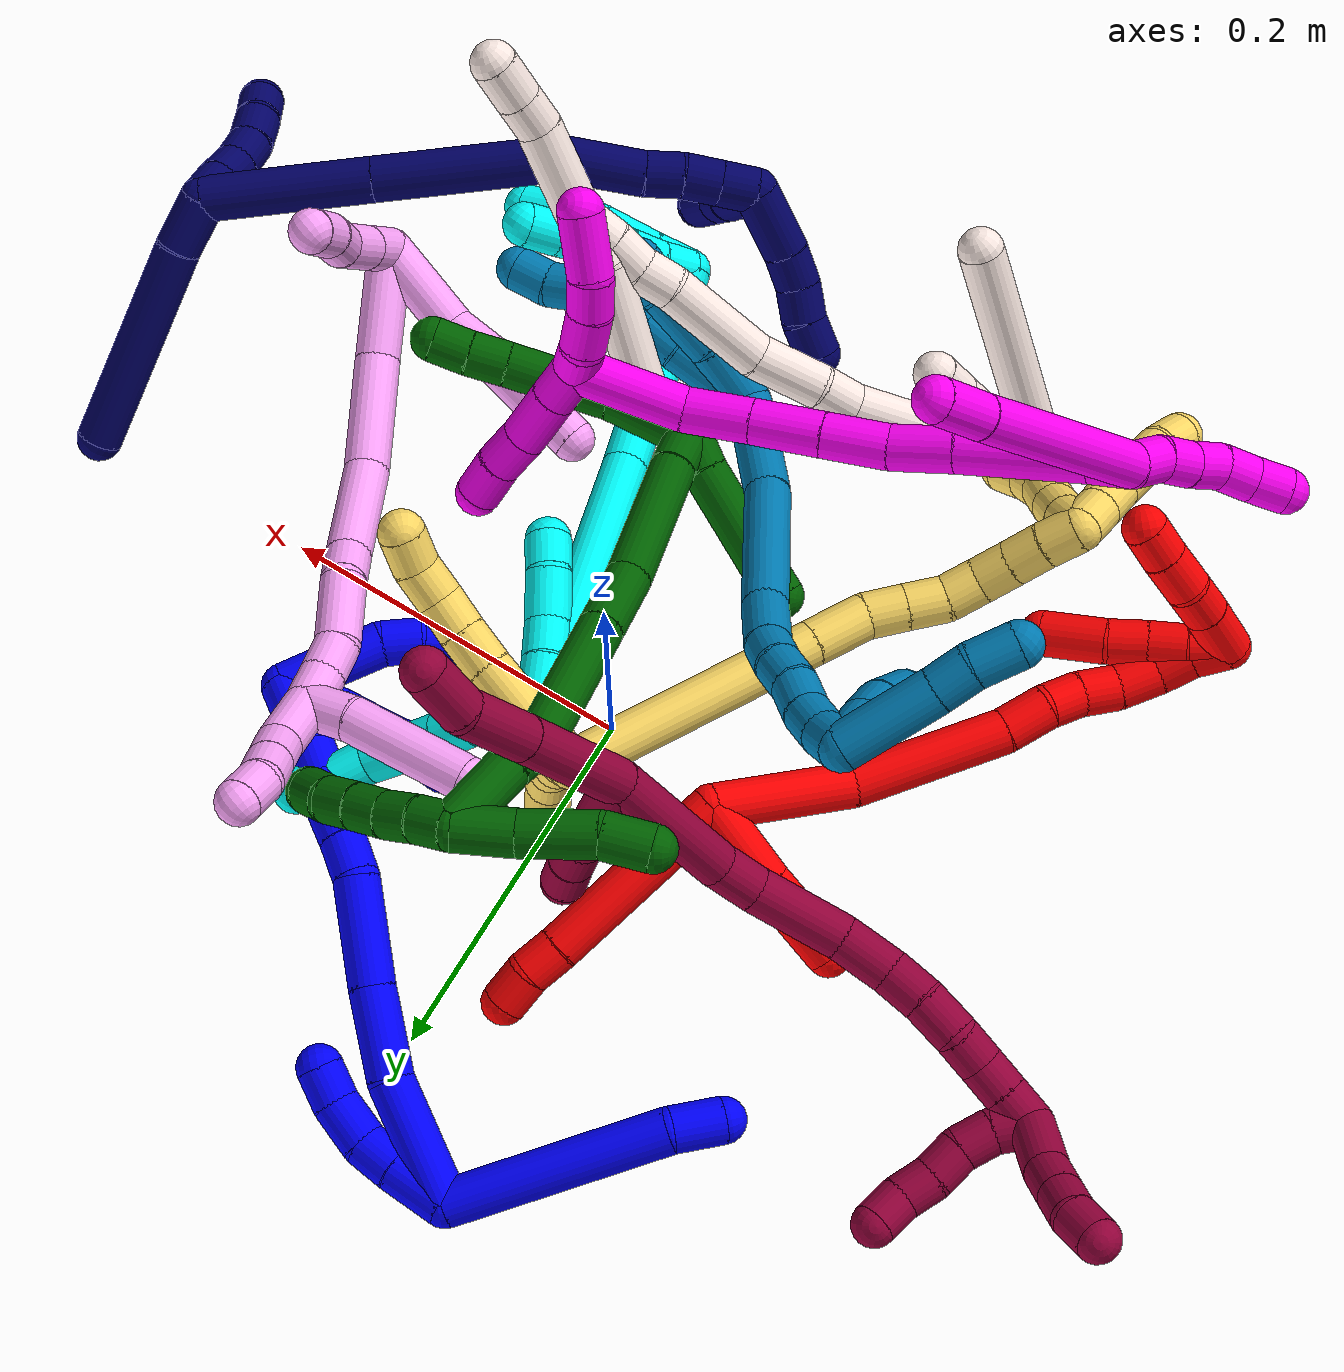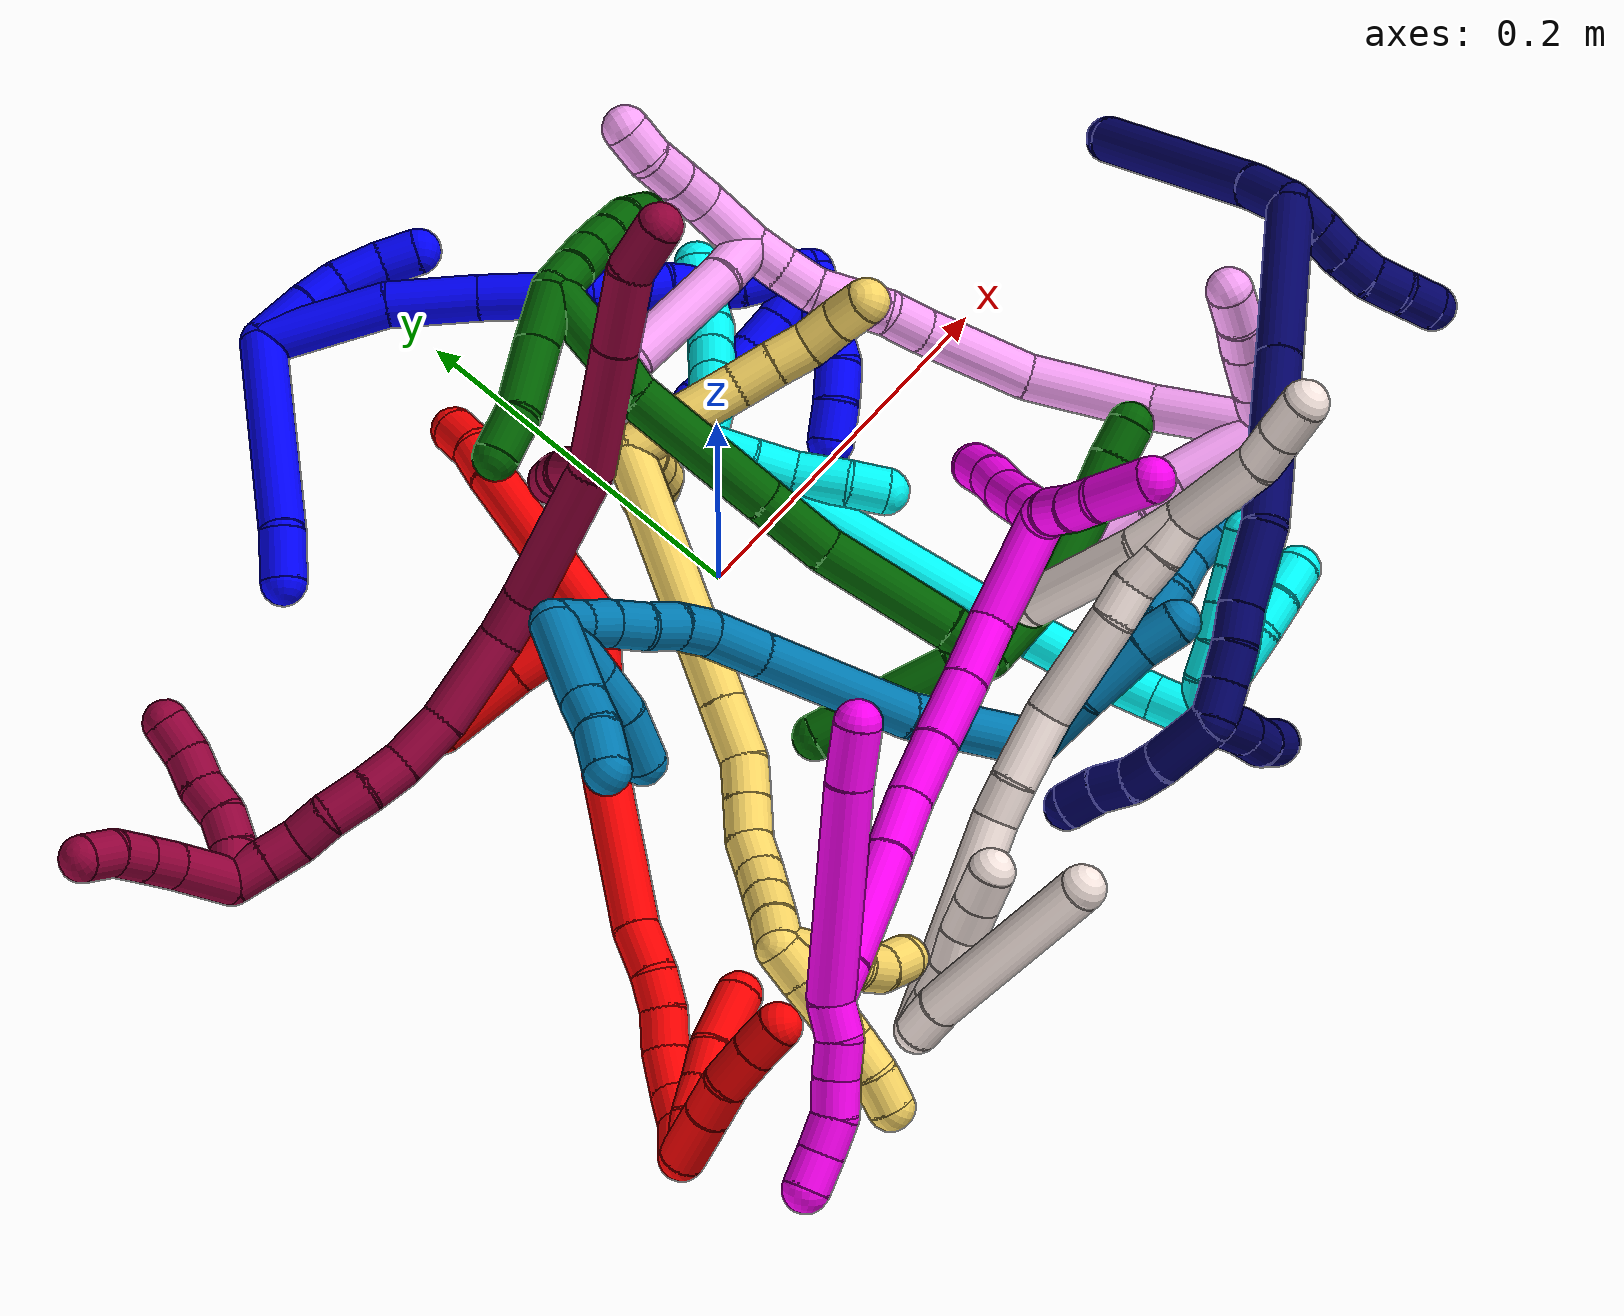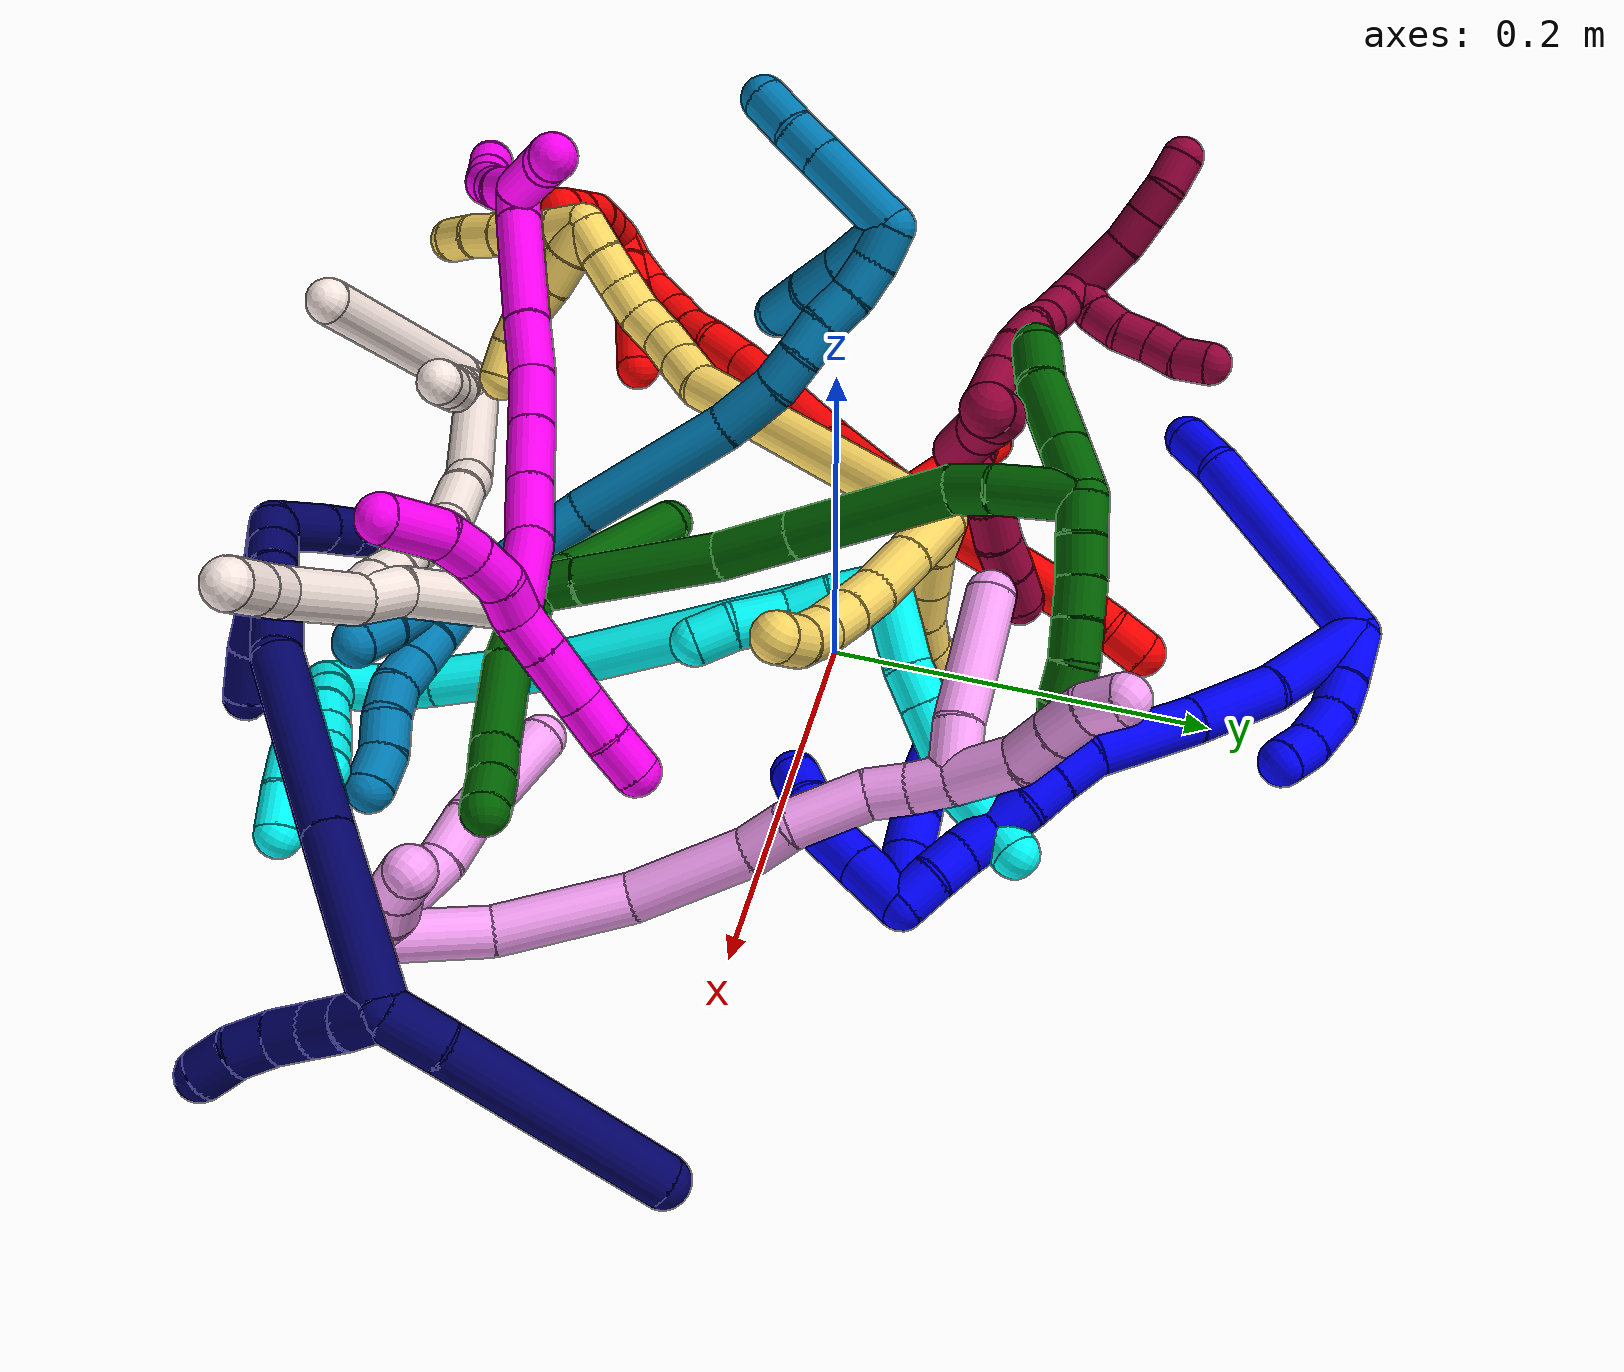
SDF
<sdf version="1.7">
 <world name="default">
  <plugin name="TubeGeneratorPlugin" filename="libtube_generator_plugin.so"/>
  <model name="photoneo_s_sensor">
   <static>1</static>
   <pose>0 0 2 1.57079 1.57079 3.14159</pose>
   <link name="link">
    <inertial><mass>0.1</mass></inertial>
    <sensor name="sensor" type="depth">
     <update_rate>30</update_rate>
     <camera>
      <horizontal_fov>1.22</horizontal_fov>
      <image><width>1920</width><height>1200</height><format>B8G8R8</format></image>
      <clip><near>0.1</near><far>4</far></clip>
      <depth_camera><output>points</output></depth_camera>
     </camera>
     <plugin name="camera_plugin" filename="libgazebo_ros_depth_camera.so">
      <baseline>0.2</baseline>
      <alwaysOn>1</alwaysOn>
      <updateRate>0.0</updateRate>
      <cameraName>camera_ir</cameraName>
      <imageTopicName>/camera/color/image_raw</imageTopicName>
      <cameraInfoTopicName>/camera/color/camera_info</cameraInfoTopicName>
      <depthImageTopicName>/camera/depth/image_raw</depthImageTopicName>
      <depthImageCameraInfoTopicName>/camera/depth/camera_info</depthImageCameraInfoTopicName>
      <pointCloudTopicName>/camera/depth/points</pointCloudTopicName>
      <frameName>fr_optical</frameName>
      <pointCloudCutoff>0.1</pointCloudCutoff>
      <pointCloudCutoffMax>2.0</pointCloudCutoffMax>
      <distortionK1>0</distortionK1>
      <distortionK2>0</distortionK2>
      <distortionK3>0</distortionK3>
      <distortionT1>0</distortionT1>
      <distortionT2>0</distortionT2>
      <CxPrime>0</CxPrime>
      <Cx>0</Cx>
      <Cy>0</Cy>
      <focalLength>0</focalLength>
      <hackBaseline>0</hackBaseline>
     </plugin>
    </sensor>
   </link>
  </model>
  <gravity>0 0 -9.8</gravity>
  <magnetic_field>6e-06 2.3e-05 -4.2e-05</magnetic_field>
  <atmosphere type="adiabatic"/>
  <physics name="default_physics" default="0" type="ode">
   <max_step_size>0.003</max_step_size>
   <real_time_factor>1</real_time_factor>
   <real_time_update_rate>1000</real_time_update_rate>
   <max_contacts>10000</max_contacts>
   <ode>
    <solver>
     <type>quick</type>
     <iters>100</iters>
     <sor>1.3</sor>
     <use_dynamic_moi_rescaling>0</use_dynamic_moi_rescaling>
    </solver>
    <constraints>
     <contact_max_correcting_vel>0</contact_max_correcting_vel>
     <contact_surface_layer>0.001</contact_surface_layer>
     <cfm>0</cfm>
     <erp>0.2</erp>
    </constraints>
   </ode>
  </physics>
  <scene><ambient>0.4 0.4 0.4 1</ambient><background>0.7 0.7 0.7 1</background><shadows>0</shadows></scene>
  <audio><device>default</device></audio>
  <spherical_coordinates>
   <surface_model>EARTH_WGS84</surface_model>
   <latitude_deg>0</latitude_deg>
   <longitude_deg>0</longitude_deg>
   <elevation>0</elevation>
   <heading_deg>0</heading_deg>
  </spherical_coordinates>
  <model name="bin">
   <static>1</static>
   <link name="bottom">
    <collision name="collision-bottom">
     <pose>0 0 -0.01 0 -0 0</pose>
     <geometry><box><size>0.8 0.6 0.02</size></box></geometry>
     <surface>
      <friction><ode><mu>100</mu><mu2>100</mu2></ode></friction>
      <contact><collide_bitmask>65535</collide_bitmask></contact>
     </surface>
    </collision>
   </link>
   <link name="west_wall">
    <collision name="collision-west_wall">
     <pose>-0.41 0 0.1 0 -0 0</pose>
     <geometry><box><size>0.02 0.6 0.2</size></box></geometry>
     <surface>
      <friction><ode><mu>100</mu><mu2>100</mu2></ode></friction>
      <contact><collide_bitmask>65535</collide_bitmask></contact>
     </surface>
    </collision>
   </link>
   <link name="east_wall">
    <collision name="collision-east_wall">
     <pose>0.41 0 0.1 0 -0 0</pose>
     <geometry><box><size>0.02 0.6 0.2</size></box></geometry>
     <surface>
      <friction><ode><mu>100</mu><mu2>100</mu2></ode></friction>
      <contact><collide_bitmask>65535</collide_bitmask></contact>
     </surface>
    </collision>
   </link>
   <link name="south_wall">
    <collision name="collision-south_wall">
     <pose>0 -0.31 0.1 0 -0 0</pose>
     <geometry><box><size>0.8 0.02 0.2</size></box></geometry>
     <surface>
      <friction><ode><mu>100</mu><mu2>100</mu2></ode></friction>
      <contact><collide_bitmask>65535</collide_bitmask></contact>
     </surface>
    </collision>
   </link>
   <link name="north_wall">
    <collision name="collision-north_wall">
     <pose>0 0.31 0.1 0 -0 0</pose>
     <geometry><box><size>0.8 0.02 0.2</size></box></geometry>
     <surface>
      <friction><ode><mu>100</mu><mu2>100</mu2></ode></friction>
      <contact><collide_bitmask>65535</collide_bitmask></contact>
     </surface>
    </collision>
   </link>
  </model>
  <model name="1">
   <static>0</static>
   <link name="1">
    <collision name="collision-cylinder-e_1_2_8">
     <pose>-0.004104 -0.012345 -0.059781 2.93795 -0.067135 -0.635069</pose>
     <geometry><cylinder><radius>0.0125</radius><length>0.12236</length></cylinder></geometry>
     <surface>
      <friction><ode><mu>1.16</mu><mu2>1.16</mu2><slip1>0</slip1><slip2>0</slip2></ode></friction>
      <contact><ode><kp>1e+06</kp><kd>1</kd><max_vel>0</max_vel><min_depth>0.001</min_depth></ode></contact>
     </surface>
    </collision>
    <visual name="visual-cylinder-e_1_2_8">
     <pose>-0.004104 -0.012345 -0.059781 2.93795 -0.067135 -0.635069</pose>
     <geometry><cylinder><radius>0.0125</radius><length>0.12236</length></cylinder></geometry>
     <material><ambient>0 0 1 1</ambient></material>
    </visual>
    <collision name="collision-cylinder-e_2_8_6">
     <pose>-0.007096 -0.023513 -0.133287 -3.05601 0.080572 -1.51048</pose>
     <geometry><cylinder><radius>0.0125</radius><length>0.02764</length></cylinder></geometry>
     <surface>
      <friction><ode><mu>1.16</mu><mu2>1.16</mu2><slip1>0</slip1><slip2>0</slip2></ode></friction>
      <contact><ode><kp>1e+06</kp><kd>1</kd><max_vel>0</max_vel><min_depth>0.001</min_depth></ode></contact>
     </surface>
    </collision>
    <visual name="visual-cylinder-e_2_8_6">
     <pose>-0.007096 -0.023513 -0.133287 -3.05601 0.080572 -1.51048</pose>
     <geometry><cylinder><radius>0.0125</radius><length>0.02764</length></cylinder></geometry>
     <material><ambient>0 0 1 1</ambient></material>
    </visual>
    <collision name="collision-cylinder-e_1_2_9">
     <pose>0.009877 -0.006652 0.010979 0.544739 0.65581 0.189467</pose>
     <geometry><cylinder><radius>0.0125</radius><length>0.032393</length></cylinder></geometry>
     <surface>
      <friction><ode><mu>1.16</mu><mu2>1.16</mu2><slip1>0</slip1><slip2>0</slip2></ode></friction>
      <contact><ode><kp>1e+06</kp><kd>1</kd><max_vel>0</max_vel><min_depth>0.001</min_depth></ode></contact>
     </surface>
    </collision>
    <visual name="visual-cylinder-e_1_2_9">
     <pose>0.009877 -0.006652 0.010979 0.544739 0.65581 0.189467</pose>
     <geometry><cylinder><radius>0.0125</radius><length>0.032393</length></cylinder></geometry>
     <material><ambient>0 0 1 1</ambient></material>
    </visual>
    <collision name="collision-cylinder-e_2_9_10">
     <pose>0.026715 -0.017657 0.028484 0.588223 0.72576 0.22901</pose>
     <geometry><cylinder><radius>0.0125</radius><length>0.020977</length></cylinder></geometry>
     <surface>
      <friction><ode><mu>1.16</mu><mu2>1.16</mu2><slip1>0</slip1><slip2>0</slip2></ode></friction>
      <contact><ode><kp>1e+06</kp><kd>1</kd><max_vel>0</max_vel><min_depth>0.001</min_depth></ode></contact>
     </surface>
    </collision>
    <visual name="visual-cylinder-e_2_9_10">
     <pose>0.026715 -0.017657 0.028484 0.588223 0.72576 0.22901</pose>
     <geometry><cylinder><radius>0.0125</radius><length>0.020977</length></cylinder></geometry>
     <material><ambient>0 0 1 1</ambient></material>
    </visual>
    <collision name="collision-cylinder-e_3_10_11">
     <pose>0.042689 -0.029679 0.040418 0.956717 0.765271 0.411478</pose>
     <geometry><cylinder><radius>0.0125</radius><length>0.026019</length></cylinder></geometry>
     <surface>
      <friction><ode><mu>1.16</mu><mu2>1.16</mu2><slip1>0</slip1><slip2>0</slip2></ode></friction>
      <contact><ode><kp>1e+06</kp><kd>1</kd><max_vel>0</max_vel><min_depth>0.001</min_depth></ode></contact>
     </surface>
    </collision>
    <visual name="visual-cylinder-e_3_10_11">
     <pose>0.042689 -0.029679 0.040418 0.956717 0.765271 0.411478</pose>
     <geometry><cylinder><radius>0.0125</radius><length>0.026019</length></cylinder></geometry>
     <material><ambient>0 0 1 1</ambient></material>
    </visual>
    <collision name="collision-cylinder-e_4_11_5">
     <pose>0.057991 -0.045135 0.048266 1.26689 0.656635 0.490278</pose>
     <geometry><cylinder><radius>0.0125</radius><length>0.02061</length></cylinder></geometry>
     <surface>
      <friction><ode><mu>1.16</mu><mu2>1.16</mu2><slip1>0</slip1><slip2>0</slip2></ode></friction>
      <contact><ode><kp>1e+06</kp><kd>1</kd><max_vel>0</max_vel><min_depth>0.001</min_depth></ode></contact>
     </surface>
    </collision>
    <visual name="visual-cylinder-e_4_11_5">
     <pose>0.057991 -0.045135 0.048266 1.26689 0.656635 0.490278</pose>
     <geometry><cylinder><radius>0.0125</radius><length>0.02061</length></cylinder></geometry>
     <material><ambient>0 0 1 1</ambient></material>
    </visual>
    <collision name="collision-cylinder-e_1_2_12">
     <pose>0.022365 -0.025089 0.007729 1.27196 0.705599 0.530873</pose>
     <geometry><cylinder><radius>0.0125</radius><length>0.068975</length></cylinder></geometry>
     <surface>
      <friction><ode><mu>1.16</mu><mu2>1.16</mu2><slip1>0</slip1><slip2>0</slip2></ode></friction>
      <contact><ode><kp>1e+06</kp><kd>1</kd><max_vel>0</max_vel><min_depth>0.001</min_depth></ode></contact>
     </surface>
    </collision>
    <visual name="visual-cylinder-e_1_2_12">
     <pose>0.022365 -0.025089 0.007729 1.27196 0.705599 0.530873</pose>
     <geometry><cylinder><radius>0.0125</radius><length>0.068975</length></cylinder></geometry>
     <material><ambient>0 0 1 1</ambient></material>
    </visual>
    <collision name="collision-cylinder-e_2_12_13">
     <pose>0.062107 -0.067505 0.01574 1.55451 0.786795 0.775327</pose>
     <geometry><cylinder><radius>0.0125</radius><length>0.049083</length></cylinder></geometry>
     <surface>
      <friction><ode><mu>1.16</mu><mu2>1.16</mu2><slip1>0</slip1><slip2>0</slip2></ode></friction>
      <contact><ode><kp>1e+06</kp><kd>1</kd><max_vel>0</max_vel><min_depth>0.001</min_depth></ode></contact>
     </surface>
    </collision>
    <visual name="visual-cylinder-e_2_12_13">
     <pose>0.062107 -0.067505 0.01574 1.55451 0.786795 0.775327</pose>
     <geometry><cylinder><radius>0.0125</radius><length>0.049083</length></cylinder></geometry>
     <material><ambient>0 0 1 1</ambient></material>
    </visual>
    <collision name="collision-cylinder-e_3_13_14">
     <pose>0.099725 -0.105926 0.014764 1.63036 0.763867 0.805982</pose>
     <geometry><cylinder><radius>0.0125</radius><length>0.058523</length></cylinder></geometry>
     <surface>
      <friction><ode><mu>1.16</mu><mu2>1.16</mu2><slip1>0</slip1><slip2>0</slip2></ode></friction>
      <contact><ode><kp>1e+06</kp><kd>1</kd><max_vel>0</max_vel><min_depth>0.001</min_depth></ode></contact>
     </surface>
    </collision>
    <visual name="visual-cylinder-e_3_13_14">
     <pose>0.099725 -0.105926 0.014764 1.63036 0.763867 0.805982</pose>
     <geometry><cylinder><radius>0.0125</radius><length>0.058523</length></cylinder></geometry>
     <material><ambient>0 0 1 1</ambient></material>
    </visual>
    <collision name="collision-cylinder-e_4_14_15">
     <pose>0.129593 -0.132763 0.015134 1.29457 1.01576 0.796503</pose>
     <geometry><cylinder><radius>0.0125</radius><length>0.022654</length></cylinder></geometry>
     <surface>
      <friction><ode><mu>1.16</mu><mu2>1.16</mu2><slip1>0</slip1><slip2>0</slip2></ode></friction>
      <contact><ode><kp>1e+06</kp><kd>1</kd><max_vel>0</max_vel><min_depth>0.001</min_depth></ode></contact>
     </surface>
    </collision>
    <visual name="visual-cylinder-e_4_14_15">
     <pose>0.129593 -0.132763 0.015134 1.29457 1.01576 0.796503</pose>
     <geometry><cylinder><radius>0.0125</radius><length>0.022654</length></cylinder></geometry>
     <material><ambient>0 0 1 1</ambient></material>
    </visual>
    <collision name="collision-cylinder-e_5_15_16">
     <pose>0.147904 -0.143077 0.018695 1.17086 1.05161 0.734514</pose>
     <geometry><cylinder><radius>0.0125</radius><length>0.020006</length></cylinder></geometry>
     <surface>
      <friction><ode><mu>1.16</mu><mu2>1.16</mu2><slip1>0</slip1><slip2>0</slip2></ode></friction>
      <contact><ode><kp>1e+06</kp><kd>1</kd><max_vel>0</max_vel><min_depth>0.001</min_depth></ode></contact>
     </surface>
    </collision>
    <visual name="visual-cylinder-e_5_15_16">
     <pose>0.147904 -0.143077 0.018695 1.17086 1.05161 0.734514</pose>
     <geometry><cylinder><radius>0.0125</radius><length>0.020006</length></cylinder></geometry>
     <material><ambient>0 0 1 1</ambient></material>
    </visual>
    <collision name="collision-cylinder-e_6_16_17">
     <pose>0.166291 -0.151173 0.020997 1.4662 1.22063 1.1241</pose>
     <geometry><cylinder><radius>0.0125</radius><length>0.020658</length></cylinder></geometry>
     <surface>
      <friction><ode><mu>1.16</mu><mu2>1.16</mu2><slip1>0</slip1><slip2>0</slip2></ode></friction>
      <contact><ode><kp>1e+06</kp><kd>1</kd><max_vel>0</max_vel><min_depth>0.001</min_depth></ode></contact>
     </surface>
    </collision>
    <visual name="visual-cylinder-e_6_16_17">
     <pose>0.166291 -0.151173 0.020997 1.4662 1.22063 1.1241</pose>
     <geometry><cylinder><radius>0.0125</radius><length>0.020658</length></cylinder></geometry>
     <material><ambient>0 0 1 1</ambient></material>
    </visual>
    <collision name="collision-cylinder-e_7_17_18">
     <pose>0.184276 -0.160149 0.022847 1.3058 0.972238 0.768115</pose>
     <geometry><cylinder><radius>0.0125</radius><length>0.020051</length></cylinder></geometry>
     <surface>
      <friction><ode><mu>1.16</mu><mu2>1.16</mu2><slip1>0</slip1><slip2>0</slip2></ode></friction>
      <contact><ode><kp>1e+06</kp><kd>1</kd><max_vel>0</max_vel><min_depth>0.001</min_depth></ode></contact>
     </surface>
    </collision>
    <visual name="visual-cylinder-e_7_17_18">
     <pose>0.184276 -0.160149 0.022847 1.3058 0.972238 0.768115</pose>
     <geometry><cylinder><radius>0.0125</radius><length>0.020051</length></cylinder></geometry>
     <material><ambient>0 0 1 1</ambient></material>
    </visual>
    <collision name="collision-cylinder-e_8_18_19">
     <pose>0.200255 -0.171466 0.026938 1.15185 0.875542 0.590133</pose>
     <geometry><cylinder><radius>0.0125</radius><length>0.020045</length></cylinder></geometry>
     <surface>
      <friction><ode><mu>1.16</mu><mu2>1.16</mu2><slip1>0</slip1><slip2>0</slip2></ode></friction>
      <contact><ode><kp>1e+06</kp><kd>1</kd><max_vel>0</max_vel><min_depth>0.001</min_depth></ode></contact>
     </surface>
    </collision>
    <visual name="visual-cylinder-e_8_18_19">
     <pose>0.200255 -0.171466 0.026938 1.15185 0.875542 0.590133</pose>
     <geometry><cylinder><radius>0.0125</radius><length>0.020045</length></cylinder></geometry>
     <material><ambient>0 0 1 1</ambient></material>
    </visual>
    <collision name="collision-cylinder-e_9_19_1">
     <pose>0.216772 -0.181644 0.031457 1.15441 1.07973 0.744088</pose>
     <geometry><cylinder><radius>0.0125</radius><length>0.020005</length></cylinder></geometry>
     <surface>
      <friction><ode><mu>1.16</mu><mu2>1.16</mu2><slip1>0</slip1><slip2>0</slip2></ode></friction>
      <contact><ode><kp>1e+06</kp><kd>1</kd><max_vel>0</max_vel><min_depth>0.001</min_depth></ode></contact>
     </surface>
    </collision>
    <visual name="visual-cylinder-e_9_19_1">
     <pose>0.216772 -0.181644 0.031457 1.15441 1.07973 0.744088</pose>
     <geometry><cylinder><radius>0.0125</radius><length>0.020005</length></cylinder></geometry>
     <material><ambient>0 0 1 1</ambient></material>
    </visual>
    <collision name="collision-cylinder-e_1_1_20">
     <pose>0.227992 -0.188341 0.018688 2.98063 0.159988 1.56469</pose>
     <geometry><cylinder><radius>0.0125</radius><length>0.030123</length></cylinder></geometry>
     <surface>
      <friction><ode><mu>1.16</mu><mu2>1.16</mu2><slip1>0</slip1><slip2>0</slip2></ode></friction>
      <contact><ode><kp>1e+06</kp><kd>1</kd><max_vel>0</max_vel><min_depth>0.001</min_depth></ode></contact>
     </surface>
    </collision>
    <visual name="visual-cylinder-e_1_1_20">
     <pose>0.227992 -0.188341 0.018688 2.98063 0.159988 1.56469</pose>
     <geometry><cylinder><radius>0.0125</radius><length>0.030123</length></cylinder></geometry>
     <material><ambient>0 0 1 1</ambient></material>
    </visual>
    <collision name="collision-cylinder-e_2_20_21">
     <pose>0.232413 -0.192822 -0.009166 2.98376 0.150412 1.52245</pose>
     <geometry><cylinder><radius>0.0125</radius><length>0.026992</length></cylinder></geometry>
     <surface>
      <friction><ode><mu>1.16</mu><mu2>1.16</mu2><slip1>0</slip1><slip2>0</slip2></ode></friction>
      <contact><ode><kp>1e+06</kp><kd>1</kd><max_vel>0</max_vel><min_depth>0.001</min_depth></ode></contact>
     </surface>
    </collision>
    <visual name="visual-cylinder-e_2_20_21">
     <pose>0.232413 -0.192822 -0.009166 2.98376 0.150412 1.52245</pose>
     <geometry><cylinder><radius>0.0125</radius><length>0.026992</length></cylinder></geometry>
     <material><ambient>0 0 1 1</ambient></material>
    </visual>
    <collision name="collision-cylinder-e_3_21_22">
     <pose>0.234047 -0.193771 -0.03304 -3.03466 -0.036112 0.650881</pose>
     <geometry><cylinder><radius>0.0125</radius><length>0.021527</length></cylinder></geometry>
     <surface>
      <friction><ode><mu>1.16</mu><mu2>1.16</mu2><slip1>0</slip1><slip2>0</slip2></ode></friction>
      <contact><ode><kp>1e+06</kp><kd>1</kd><max_vel>0</max_vel><min_depth>0.001</min_depth></ode></contact>
     </surface>
    </collision>
    <visual name="visual-cylinder-e_3_21_22">
     <pose>0.234047 -0.193771 -0.03304 -3.03466 -0.036112 0.650881</pose>
     <geometry><cylinder><radius>0.0125</radius><length>0.021527</length></cylinder></geometry>
     <material><ambient>0 0 1 1</ambient></material>
    </visual>
    <collision name="collision-cylinder-e_4_22_4">
     <pose>0.233855 -0.189467 -0.053935 -2.84149 0.018405 -0.121592</pose>
     <geometry><cylinder><radius>0.0125</radius><length>0.021358</length></cylinder></geometry>
     <surface>
      <friction><ode><mu>1.16</mu><mu2>1.16</mu2><slip1>0</slip1><slip2>0</slip2></ode></friction>
      <contact><ode><kp>1e+06</kp><kd>1</kd><max_vel>0</max_vel><min_depth>0.001</min_depth></ode></contact>
     </surface>
    </collision>
    <visual name="visual-cylinder-e_4_22_4">
     <pose>0.233855 -0.189467 -0.053935 -2.84149 0.018405 -0.121592</pose>
     <geometry><cylinder><radius>0.0125</radius><length>0.021358</length></cylinder></geometry>
     <material><ambient>0 0 1 1</ambient></material>
    </visual>
    <collision name="collision-cylinder-e_1_1_23">
     <pose>0.220174 -0.178222 0.01989 -2.62043 -0.335516 1.13168</pose>
     <geometry><cylinder><radius>0.0125</radius><length>0.032911</length></cylinder></geometry>
     <surface>
      <friction><ode><mu>1.16</mu><mu2>1.16</mu2><slip1>0</slip1><slip2>0</slip2></ode></friction>
      <contact><ode><kp>1e+06</kp><kd>1</kd><max_vel>0</max_vel><min_depth>0.001</min_depth></ode></contact>
     </surface>
    </collision>
    <visual name="visual-cylinder-e_1_1_23">
     <pose>0.220174 -0.178222 0.01989 -2.62043 -0.335516 1.13168</pose>
     <geometry><cylinder><radius>0.0125</radius><length>0.032911</length></cylinder></geometry>
     <material><ambient>0 0 1 1</ambient></material>
    </visual>
    <collision name="collision-cylinder-e_2_23_24">
     <pose>0.208881 -0.165714 -0.00237 -2.64398 -0.531304 1.63924</pose>
     <geometry><cylinder><radius>0.0125</radius><length>0.023192</length></cylinder></geometry>
     <surface>
      <friction><ode><mu>1.16</mu><mu2>1.16</mu2><slip1>0</slip1><slip2>0</slip2></ode></friction>
      <contact><ode><kp>1e+06</kp><kd>1</kd><max_vel>0</max_vel><min_depth>0.001</min_depth></ode></contact>
     </surface>
    </collision>
    <visual name="visual-cylinder-e_2_23_24">
     <pose>0.208881 -0.165714 -0.00237 -2.64398 -0.531304 1.63924</pose>
     <geometry><cylinder><radius>0.0125</radius><length>0.023192</length></cylinder></geometry>
     <material><ambient>0 0 1 1</ambient></material>
    </visual>
    <collision name="collision-cylinder-e_3_24_25">
     <pose>0.197041 -0.158034 -0.018705 -2.77391 -0.635298 2.11219</pose>
     <geometry><cylinder><radius>0.0125</radius><length>0.020102</length></cylinder></geometry>
     <surface>
      <friction><ode><mu>1.16</mu><mu2>1.16</mu2><slip1>0</slip1><slip2>0</slip2></ode></friction>
      <contact><ode><kp>1e+06</kp><kd>1</kd><max_vel>0</max_vel><min_depth>0.001</min_depth></ode></contact>
     </surface>
    </collision>
    <visual name="visual-cylinder-e_3_24_25">
     <pose>0.197041 -0.158034 -0.018705 -2.77391 -0.635298 2.11219</pose>
     <geometry><cylinder><radius>0.0125</radius><length>0.020102</length></cylinder></geometry>
     <material><ambient>0 0 1 1</ambient></material>
    </visual>
    <collision name="collision-cylinder-e_4_25_3">
     <pose>0.183343 -0.15048 -0.03401 -2.60194 -0.707585 1.85607</pose>
     <geometry><cylinder><radius>0.0125</radius><length>0.023795</length></cylinder></geometry>
     <surface>
      <friction><ode><mu>1.16</mu><mu2>1.16</mu2><slip1>0</slip1><slip2>0</slip2></ode></friction>
      <contact><ode><kp>1e+06</kp><kd>1</kd><max_vel>0</max_vel><min_depth>0.001</min_depth></ode></contact>
     </surface>
    </collision>
    <visual name="visual-cylinder-e_4_25_3">
     <pose>0.183343 -0.15048 -0.03401 -2.60194 -0.707585 1.85607</pose>
     <geometry><cylinder><radius>0.0125</radius><length>0.023795</length></cylinder></geometry>
     <material><ambient>0 0 1 1</ambient></material>
    </visual>
    <collision name="collision-sphere-3">
     <pose>0.17561 -0.145834 -0.041767 0 -0 0</pose>
     <geometry><sphere><radius>0.0125</radius></sphere></geometry>
     <surface>
      <friction><ode><mu>1.16</mu><mu2>1.16</mu2><slip1>0</slip1><slip2>0</slip2></ode></friction>
      <contact><ode><kp>1e+06</kp><kd>1</kd><max_vel>0</max_vel><min_depth>0.001</min_depth></ode></contact>
     </surface>
    </collision>
    <visual name="visual-sphere-3">
     <pose>0.17561 -0.145834 -0.041767 0 -0 0</pose>
     <geometry><sphere><radius>0.0125</radius></sphere></geometry>
     <material><ambient>0 0 1 1</ambient></material>
    </visual>
    <collision name="collision-sphere-25">
     <pose>0.191077 -0.155126 -0.026254 0 -0 0</pose>
     <geometry><sphere><radius>0.0125</radius></sphere></geometry>
     <surface>
      <friction><ode><mu>1.16</mu><mu2>1.16</mu2><slip1>0</slip1><slip2>0</slip2></ode></friction>
      <contact><ode><kp>1e+06</kp><kd>1</kd><max_vel>0</max_vel><min_depth>0.001</min_depth></ode></contact>
     </surface>
    </collision>
    <visual name="visual-sphere-25">
     <pose>0.191077 -0.155126 -0.026254 0 -0 0</pose>
     <geometry><sphere><radius>0.0125</radius></sphere></geometry>
     <material><ambient>0 0 1 1</ambient></material>
    </visual>
    <collision name="collision-sphere-24">
     <pose>0.203006 -0.160942 -0.011155 0 -0 0</pose>
     <geometry><sphere><radius>0.0125</radius></sphere></geometry>
     <surface>
      <friction><ode><mu>1.16</mu><mu2>1.16</mu2><slip1>0</slip1><slip2>0</slip2></ode></friction>
      <contact><ode><kp>1e+06</kp><kd>1</kd><max_vel>0</max_vel><min_depth>0.001</min_depth></ode></contact>
     </surface>
    </collision>
    <visual name="visual-sphere-24">
     <pose>0.203006 -0.160942 -0.011155 0 -0 0</pose>
     <geometry><sphere><radius>0.0125</radius></sphere></geometry>
     <material><ambient>0 0 1 1</ambient></material>
    </visual>
    <collision name="collision-sphere-23">
     <pose>0.214756 -0.170486 0.006415 0 -0 0</pose>
     <geometry><sphere><radius>0.0125</radius></sphere></geometry>
     <surface>
      <friction><ode><mu>1.16</mu><mu2>1.16</mu2><slip1>0</slip1><slip2>0</slip2></ode></friction>
      <contact><ode><kp>1e+06</kp><kd>1</kd><max_vel>0</max_vel><min_depth>0.001</min_depth></ode></contact>
     </surface>
    </collision>
    <visual name="visual-sphere-23">
     <pose>0.214756 -0.170486 0.006415 0 -0 0</pose>
     <geometry><sphere><radius>0.0125</radius></sphere></geometry>
     <material><ambient>0 0 1 1</ambient></material>
    </visual>
    <collision name="collision-sphere-4">
     <pose>0.234052 -0.186311 -0.064134 0 -0 0</pose>
     <geometry><sphere><radius>0.0125</radius></sphere></geometry>
     <surface>
      <friction><ode><mu>1.16</mu><mu2>1.16</mu2><slip1>0</slip1><slip2>0</slip2></ode></friction>
      <contact><ode><kp>1e+06</kp><kd>1</kd><max_vel>0</max_vel><min_depth>0.001</min_depth></ode></contact>
     </surface>
    </collision>
    <visual name="visual-sphere-4">
     <pose>0.234052 -0.186311 -0.064134 0 -0 0</pose>
     <geometry><sphere><radius>0.0125</radius></sphere></geometry>
     <material><ambient>0 0 1 1</ambient></material>
    </visual>
    <collision name="collision-sphere-22">
     <pose>0.233658 -0.192623 -0.043735 0 -0 0</pose>
     <geometry><sphere><radius>0.0125</radius></sphere></geometry>
     <surface>
      <friction><ode><mu>1.16</mu><mu2>1.16</mu2><slip1>0</slip1><slip2>0</slip2></ode></friction>
      <contact><ode><kp>1e+06</kp><kd>1</kd><max_vel>0</max_vel><min_depth>0.001</min_depth></ode></contact>
     </surface>
    </collision>
    <visual name="visual-sphere-22">
     <pose>0.233658 -0.192623 -0.043735 0 -0 0</pose>
     <geometry><sphere><radius>0.0125</radius></sphere></geometry>
     <material><ambient>0 0 1 1</ambient></material>
    </visual>
    <collision name="collision-sphere-21">
     <pose>0.234436 -0.194919 -0.022344 0 -0 0</pose>
     <geometry><sphere><radius>0.0125</radius></sphere></geometry>
     <surface>
      <friction><ode><mu>1.16</mu><mu2>1.16</mu2><slip1>0</slip1><slip2>0</slip2></ode></friction>
      <contact><ode><kp>1e+06</kp><kd>1</kd><max_vel>0</max_vel><min_depth>0.001</min_depth></ode></contact>
     </surface>
    </collision>
    <visual name="visual-sphere-21">
     <pose>0.234436 -0.194919 -0.022344 0 -0 0</pose>
     <geometry><sphere><radius>0.0125</radius></sphere></geometry>
     <material><ambient>0 0 1 1</ambient></material>
    </visual>
    <collision name="collision-sphere-20">
     <pose>0.230391 -0.190724 0.004012 0 -0 0</pose>
     <geometry><sphere><radius>0.0125</radius></sphere></geometry>
     <surface>
      <friction><ode><mu>1.16</mu><mu2>1.16</mu2><slip1>0</slip1><slip2>0</slip2></ode></friction>
      <contact><ode><kp>1e+06</kp><kd>1</kd><max_vel>0</max_vel><min_depth>0.001</min_depth></ode></contact>
     </surface>
    </collision>
    <visual name="visual-sphere-20">
     <pose>0.230391 -0.190724 0.004012 0 -0 0</pose>
     <geometry><sphere><radius>0.0125</radius></sphere></geometry>
     <material><ambient>0 0 1 1</ambient></material>
    </visual>
    <collision name="collision-sphere-11">
     <pose>0.051701 -0.037347 0.045824 0 -0 0</pose>
     <geometry><sphere><radius>0.0125</radius></sphere></geometry>
     <surface>
      <friction><ode><mu>1.16</mu><mu2>1.16</mu2><slip1>0</slip1><slip2>0</slip2></ode></friction>
      <contact><ode><kp>1e+06</kp><kd>1</kd><max_vel>0</max_vel><min_depth>0.001</min_depth></ode></contact>
     </surface>
    </collision>
    <visual name="visual-sphere-11">
     <pose>0.051701 -0.037347 0.045824 0 -0 0</pose>
     <geometry><sphere><radius>0.0125</radius></sphere></geometry>
     <material><ambient>0 0 1 1</ambient></material>
    </visual>
    <collision name="collision-sphere-10">
     <pose>0.033676 -0.022011 0.035011 0 -0 0</pose>
     <geometry><sphere><radius>0.0125</radius></sphere></geometry>
     <surface>
      <friction><ode><mu>1.16</mu><mu2>1.16</mu2><slip1>0</slip1><slip2>0</slip2></ode></friction>
      <contact><ode><kp>1e+06</kp><kd>1</kd><max_vel>0</max_vel><min_depth>0.001</min_depth></ode></contact>
     </surface>
    </collision>
    <visual name="visual-sphere-10">
     <pose>0.033676 -0.022011 0.035011 0 -0 0</pose>
     <geometry><sphere><radius>0.0125</radius></sphere></geometry>
     <material><ambient>0 0 1 1</ambient></material>
    </visual>
    <collision name="collision-sphere-6">
     <pose>-0.005984 -0.022335 -0.147011 0 -0 0</pose>
     <geometry><sphere><radius>0.0125</radius></sphere></geometry>
     <surface>
      <friction><ode><mu>1.16</mu><mu2>1.16</mu2><slip1>0</slip1><slip2>0</slip2></ode></friction>
      <contact><ode><kp>1e+06</kp><kd>1</kd><max_vel>0</max_vel><min_depth>0.001</min_depth></ode></contact>
     </surface>
    </collision>
    <visual name="visual-sphere-6">
     <pose>-0.005984 -0.022335 -0.147011 0 -0 0</pose>
     <geometry><sphere><radius>0.0125</radius></sphere></geometry>
     <material><ambient>0 0 1 1</ambient></material>
    </visual>
    <collision name="collision-sphere-9">
     <pose>0.019754 -0.013304 0.021958 0 -0 0</pose>
     <geometry><sphere><radius>0.0125</radius></sphere></geometry>
     <surface>
      <friction><ode><mu>1.16</mu><mu2>1.16</mu2><slip1>0</slip1><slip2>0</slip2></ode></friction>
      <contact><ode><kp>1e+06</kp><kd>1</kd><max_vel>0</max_vel><min_depth>0.001</min_depth></ode></contact>
     </surface>
    </collision>
    <visual name="visual-sphere-9">
     <pose>0.019754 -0.013304 0.021958 0 -0 0</pose>
     <geometry><sphere><radius>0.0125</radius></sphere></geometry>
     <material><ambient>0 0 1 1</ambient></material>
    </visual>
    <collision name="collision-sphere-2">
     <geometry><sphere><radius>0.0125</radius></sphere></geometry>
     <surface>
      <friction><ode><mu>1.16</mu><mu2>1.16</mu2><slip1>0</slip1><slip2>0</slip2></ode></friction>
      <contact><ode><kp>1e+06</kp><kd>1</kd><max_vel>0</max_vel><min_depth>0.001</min_depth></ode></contact>
     </surface>
    </collision>
    <visual name="visual-sphere-2">
     <geometry><sphere><radius>0.0125</radius></sphere></geometry>
     <material><ambient>0 0 1 1</ambient></material>
    </visual>
    <collision name="collision-sphere-19">
     <pose>0.207951 -0.17733 0.029549 0 -0 0</pose>
     <geometry><sphere><radius>0.0125</radius></sphere></geometry>
     <surface>
      <friction><ode><mu>1.16</mu><mu2>1.16</mu2><slip1>0</slip1><slip2>0</slip2></ode></friction>
      <contact><ode><kp>1e+06</kp><kd>1</kd><max_vel>0</max_vel><min_depth>0.001</min_depth></ode></contact>
     </surface>
    </collision>
    <visual name="visual-sphere-19">
     <pose>0.207951 -0.17733 0.029549 0 -0 0</pose>
     <geometry><sphere><radius>0.0125</radius></sphere></geometry>
     <material><ambient>0 0 1 1</ambient></material>
    </visual>
    <collision name="collision-sphere-8">
     <pose>-0.008208 -0.02469 -0.119562 0 -0 0</pose>
     <geometry><sphere><radius>0.0125</radius></sphere></geometry>
     <surface>
      <friction><ode><mu>1.16</mu><mu2>1.16</mu2><slip1>0</slip1><slip2>0</slip2></ode></friction>
      <contact><ode><kp>1e+06</kp><kd>1</kd><max_vel>0</max_vel><min_depth>0.001</min_depth></ode></contact>
     </surface>
    </collision>
    <visual name="visual-sphere-8">
     <pose>-0.008208 -0.02469 -0.119562 0 -0 0</pose>
     <geometry><sphere><radius>0.0125</radius></sphere></geometry>
     <material><ambient>0 0 1 1</ambient></material>
    </visual>
    <collision name="collision-sphere-5">
     <pose>0.064282 -0.052923 0.050709 0 -0 0</pose>
     <geometry><sphere><radius>0.0125</radius></sphere></geometry>
     <surface>
      <friction><ode><mu>1.16</mu><mu2>1.16</mu2><slip1>0</slip1><slip2>0</slip2></ode></friction>
      <contact><ode><kp>1e+06</kp><kd>1</kd><max_vel>0</max_vel><min_depth>0.001</min_depth></ode></contact>
     </surface>
    </collision>
    <visual name="visual-sphere-5">
     <pose>0.064282 -0.052923 0.050709 0 -0 0</pose>
     <geometry><sphere><radius>0.0125</radius></sphere></geometry>
     <material><ambient>0 0 1 1</ambient></material>
    </visual>
    <collision name="collision-sphere-12">
     <pose>0.044729 -0.050178 0.015458 0 -0 0</pose>
     <geometry><sphere><radius>0.0125</radius></sphere></geometry>
     <surface>
      <friction><ode><mu>1.16</mu><mu2>1.16</mu2><slip1>0</slip1><slip2>0</slip2></ode></friction>
      <contact><ode><kp>1e+06</kp><kd>1</kd><max_vel>0</max_vel><min_depth>0.001</min_depth></ode></contact>
     </surface>
    </collision>
    <visual name="visual-sphere-12">
     <pose>0.044729 -0.050178 0.015458 0 -0 0</pose>
     <geometry><sphere><radius>0.0125</radius></sphere></geometry>
     <material><ambient>0 0 1 1</ambient></material>
    </visual>
    <collision name="collision-sphere-13">
     <pose>0.079485 -0.084832 0.016022 0 -0 0</pose>
     <geometry><sphere><radius>0.0125</radius></sphere></geometry>
     <surface>
      <friction><ode><mu>1.16</mu><mu2>1.16</mu2><slip1>0</slip1><slip2>0</slip2></ode></friction>
      <contact><ode><kp>1e+06</kp><kd>1</kd><max_vel>0</max_vel><min_depth>0.001</min_depth></ode></contact>
     </surface>
    </collision>
    <visual name="visual-sphere-13">
     <pose>0.079485 -0.084832 0.016022 0 -0 0</pose>
     <geometry><sphere><radius>0.0125</radius></sphere></geometry>
     <material><ambient>0 0 1 1</ambient></material>
    </visual>
    <collision name="collision-sphere-14">
     <pose>0.119966 -0.12702 0.013506 0 -0 0</pose>
     <geometry><sphere><radius>0.0125</radius></sphere></geometry>
     <surface>
      <friction><ode><mu>1.16</mu><mu2>1.16</mu2><slip1>0</slip1><slip2>0</slip2></ode></friction>
      <contact><ode><kp>1e+06</kp><kd>1</kd><max_vel>0</max_vel><min_depth>0.001</min_depth></ode></contact>
     </surface>
    </collision>
    <visual name="visual-sphere-14">
     <pose>0.119966 -0.12702 0.013506 0 -0 0</pose>
     <geometry><sphere><radius>0.0125</radius></sphere></geometry>
     <material><ambient>0 0 1 1</ambient></material>
    </visual>
    <collision name="collision-sphere-15">
     <pose>0.139219 -0.138506 0.016762 0 -0 0</pose>
     <geometry><sphere><radius>0.0125</radius></sphere></geometry>
     <surface>
      <friction><ode><mu>1.16</mu><mu2>1.16</mu2><slip1>0</slip1><slip2>0</slip2></ode></friction>
      <contact><ode><kp>1e+06</kp><kd>1</kd><max_vel>0</max_vel><min_depth>0.001</min_depth></ode></contact>
     </surface>
    </collision>
    <visual name="visual-sphere-15">
     <pose>0.139219 -0.138506 0.016762 0 -0 0</pose>
     <geometry><sphere><radius>0.0125</radius></sphere></geometry>
     <material><ambient>0 0 1 1</ambient></material>
    </visual>
    <collision name="collision-sphere-16">
     <pose>0.156589 -0.147649 0.020627 0 -0 0</pose>
     <geometry><sphere><radius>0.0125</radius></sphere></geometry>
     <surface>
      <friction><ode><mu>1.16</mu><mu2>1.16</mu2><slip1>0</slip1><slip2>0</slip2></ode></friction>
      <contact><ode><kp>1e+06</kp><kd>1</kd><max_vel>0</max_vel><min_depth>0.001</min_depth></ode></contact>
     </surface>
    </collision>
    <visual name="visual-sphere-16">
     <pose>0.156589 -0.147649 0.020627 0 -0 0</pose>
     <geometry><sphere><radius>0.0125</radius></sphere></geometry>
     <material><ambient>0 0 1 1</ambient></material>
    </visual>
    <collision name="collision-sphere-17">
     <pose>0.175994 -0.154697 0.021367 0 -0 0</pose>
     <geometry><sphere><radius>0.0125</radius></sphere></geometry>
     <surface>
      <friction><ode><mu>1.16</mu><mu2>1.16</mu2><slip1>0</slip1><slip2>0</slip2></ode></friction>
      <contact><ode><kp>1e+06</kp><kd>1</kd><max_vel>0</max_vel><min_depth>0.001</min_depth></ode></contact>
     </surface>
    </collision>
    <visual name="visual-sphere-17">
     <pose>0.175994 -0.154697 0.021367 0 -0 0</pose>
     <geometry><sphere><radius>0.0125</radius></sphere></geometry>
     <material><ambient>0 0 1 1</ambient></material>
    </visual>
    <collision name="collision-sphere-18">
     <pose>0.192559 -0.165601 0.024326 0 -0 0</pose>
     <geometry><sphere><radius>0.0125</radius></sphere></geometry>
     <surface>
      <friction><ode><mu>1.16</mu><mu2>1.16</mu2><slip1>0</slip1><slip2>0</slip2></ode></friction>
      <contact><ode><kp>1e+06</kp><kd>1</kd><max_vel>0</max_vel><min_depth>0.001</min_depth></ode></contact>
     </surface>
    </collision>
    <visual name="visual-sphere-18">
     <pose>0.192559 -0.165601 0.024326 0 -0 0</pose>
     <geometry><sphere><radius>0.0125</radius></sphere></geometry>
     <material><ambient>0 0 1 1</ambient></material>
    </visual>
    <collision name="collision-sphere-1">
     <pose>0.225592 -0.185958 0.033365 0 -0 0</pose>
     <geometry><sphere><radius>0.0125</radius></sphere></geometry>
     <surface>
      <friction><ode><mu>1.16</mu><mu2>1.16</mu2><slip1>0</slip1><slip2>0</slip2></ode></friction>
      <contact><ode><kp>1e+06</kp><kd>1</kd><max_vel>0</max_vel><min_depth>0.001</min_depth></ode></contact>
     </surface>
    </collision>
    <visual name="visual-sphere-1">
     <pose>0.225592 -0.185958 0.033365 0 -0 0</pose>
     <geometry><sphere><radius>0.0125</radius></sphere></geometry>
     <material><ambient>0 0 1 1</ambient></material>
    </visual>
    <inertial>
     <pose>0.103839 -0.094039 -0.006913 0 -0 0</pose>
     <mass>0.75</mass>
     <inertia>
      <ixx>0.000146</ixx>
      <ixy>0</ixy>
      <ixz>0</ixz>
      <iyy>-0.000143</iyy>
      <iyz>0</iyz>
      <izz>2.2e-05</izz>
     </inertia>
    </inertial>
   </link>
   <pose>-0.064455 0.265506 0.022813 -1.56134 0.707092 -0.811482</pose>
  </model>
  <model name="2">
   <static>0</static>
   <link name="2">
    <collision name="collision-cylinder-e_1_2_8">
     <pose>-0.000325 0.046151 0.028275 -1.02111 -0.006 0.003361</pose>
     <geometry><cylinder><radius>0.0125</radius><length>0.108249</length></cylinder></geometry>
     <surface>
      <friction><ode><mu>1.16</mu><mu2>1.16</mu2><slip1>0</slip1><slip2>0</slip2></ode></friction>
      <contact><ode><kp>1e+06</kp><kd>1</kd><max_vel>0</max_vel><min_depth>0.001</min_depth></ode></contact>
     </surface>
    </collision>
    <visual name="visual-cylinder-e_1_2_8">
     <pose>-0.000325 0.046151 0.028275 -1.02111 -0.006 0.003361</pose>
     <geometry><cylinder><radius>0.0125</radius><length>0.108249</length></cylinder></geometry>
     <material><ambient>1 0 0 1</ambient></material>
    </visual>
    <collision name="collision-cylinder-e_2_8_9">
     <pose>-0.001404 0.101417 0.061546 -1.06952 -0.072499 0.042956</pose>
     <geometry><cylinder><radius>0.0125</radius><length>0.020844</length></cylinder></geometry>
     <surface>
      <friction><ode><mu>1.16</mu><mu2>1.16</mu2><slip1>0</slip1><slip2>0</slip2></ode></friction>
      <contact><ode><kp>1e+06</kp><kd>1</kd><max_vel>0</max_vel><min_depth>0.001</min_depth></ode></contact>
     </surface>
    </collision>
    <visual name="visual-cylinder-e_2_8_9">
     <pose>-0.001404 0.101417 0.061546 -1.06952 -0.072499 0.042956</pose>
     <geometry><cylinder><radius>0.0125</radius><length>0.020844</length></cylinder></geometry>
     <material><ambient>1 0 0 1</ambient></material>
    </visual>
    <collision name="collision-cylinder-e_3_9_6">
     <pose>-0.004724 0.118118 0.073261 -0.8458 -0.247849 0.112003</pose>
     <geometry><cylinder><radius>0.0125</radius><length>0.020906</length></cylinder></geometry>
     <surface>
      <friction><ode><mu>1.16</mu><mu2>1.16</mu2><slip1>0</slip1><slip2>0</slip2></ode></friction>
      <contact><ode><kp>1e+06</kp><kd>1</kd><max_vel>0</max_vel><min_depth>0.001</min_depth></ode></contact>
     </surface>
    </collision>
    <visual name="visual-cylinder-e_3_9_6">
     <pose>-0.004724 0.118118 0.073261 -0.8458 -0.247849 0.112003</pose>
     <geometry><cylinder><radius>0.0125</radius><length>0.020906</length></cylinder></geometry>
     <material><ambient>1 0 0 1</ambient></material>
    </visual>
    <collision name="collision-cylinder-e_1_2_10">
     <pose>0.000898 -0.010677 0.022141 0.449307 0.036518 0.008346</pose>
     <geometry><cylinder><radius>0.0125</radius><length>0.049195</length></cylinder></geometry>
     <surface>
      <friction><ode><mu>1.16</mu><mu2>1.16</mu2><slip1>0</slip1><slip2>0</slip2></ode></friction>
      <contact><ode><kp>1e+06</kp><kd>1</kd><max_vel>0</max_vel><min_depth>0.001</min_depth></ode></contact>
     </surface>
    </collision>
    <visual name="visual-cylinder-e_1_2_10">
     <pose>0.000898 -0.010677 0.022141 0.449307 0.036518 0.008346</pose>
     <geometry><cylinder><radius>0.0125</radius><length>0.049195</length></cylinder></geometry>
     <material><ambient>1 0 0 1</ambient></material>
    </visual>
    <collision name="collision-cylinder-e_2_10_5">
     <pose>0.001025 -0.033705 0.066466 0.508051 -0.030363 -0.007884</pose>
     <geometry><cylinder><radius>0.0125</radius><length>0.050805</length></cylinder></geometry>
     <surface>
      <friction><ode><mu>1.16</mu><mu2>1.16</mu2><slip1>0</slip1><slip2>0</slip2></ode></friction>
      <contact><ode><kp>1e+06</kp><kd>1</kd><max_vel>0</max_vel><min_depth>0.001</min_depth></ode></contact>
     </surface>
    </collision>
    <visual name="visual-cylinder-e_2_10_5">
     <pose>0.001025 -0.033705 0.066466 0.508051 -0.030363 -0.007884</pose>
     <geometry><cylinder><radius>0.0125</radius><length>0.050805</length></cylinder></geometry>
     <material><ambient>1 0 0 1</ambient></material>
    </visual>
    <collision name="collision-cylinder-e_1_2_11">
     <pose>-0.010078 -0.038384 0.002958 1.49387 -0.256033 -0.237243</pose>
     <geometry><cylinder><radius>0.0125</radius><length>0.07959</length></cylinder></geometry>
     <surface>
      <friction><ode><mu>1.16</mu><mu2>1.16</mu2><slip1>0</slip1><slip2>0</slip2></ode></friction>
      <contact><ode><kp>1e+06</kp><kd>1</kd><max_vel>0</max_vel><min_depth>0.001</min_depth></ode></contact>
     </surface>
    </collision>
    <visual name="visual-cylinder-e_1_2_11">
     <pose>-0.010078 -0.038384 0.002958 1.49387 -0.256033 -0.237243</pose>
     <geometry><cylinder><radius>0.0125</radius><length>0.07959</length></cylinder></geometry>
     <material><ambient>1 0 0 1</ambient></material>
    </visual>
    <collision name="collision-cylinder-e_2_11_12">
     <pose>-0.02379 -0.120197 0.000362 1.69801 -0.082824 -0.094076</pose>
     <geometry><cylinder><radius>0.0125</radius><length>0.087867</length></cylinder></geometry>
     <surface>
      <friction><ode><mu>1.16</mu><mu2>1.16</mu2><slip1>0</slip1><slip2>0</slip2></ode></friction>
      <contact><ode><kp>1e+06</kp><kd>1</kd><max_vel>0</max_vel><min_depth>0.001</min_depth></ode></contact>
     </surface>
    </collision>
    <visual name="visual-cylinder-e_2_11_12">
     <pose>-0.02379 -0.120197 0.000362 1.69801 -0.082824 -0.094076</pose>
     <geometry><cylinder><radius>0.0125</radius><length>0.087867</length></cylinder></geometry>
     <material><ambient>1 0 0 1</ambient></material>
    </visual>
    <collision name="collision-cylinder-e_3_12_13">
     <pose>-0.028466 -0.176146 -0.009202 1.88072 -0.079037 -0.108254</pose>
     <geometry><cylinder><radius>0.0125</radius><length>0.026374</length></cylinder></geometry>
     <surface>
      <friction><ode><mu>1.16</mu><mu2>1.16</mu2><slip1>0</slip1><slip2>0</slip2></ode></friction>
      <contact><ode><kp>1e+06</kp><kd>1</kd><max_vel>0</max_vel><min_depth>0.001</min_depth></ode></contact>
     </surface>
    </collision>
    <visual name="visual-cylinder-e_3_12_13">
     <pose>-0.028466 -0.176146 -0.009202 1.88072 -0.079037 -0.108254</pose>
     <geometry><cylinder><radius>0.0125</radius><length>0.026374</length></cylinder></geometry>
     <material><ambient>1 0 0 1</ambient></material>
    </visual>
    <collision name="collision-cylinder-e_4_13_14">
     <pose>-0.03204 -0.198285 -0.01451 1.70505 -0.255246 -0.291553</pose>
     <geometry><cylinder><radius>0.0125</radius><length>0.020065</length></cylinder></geometry>
     <surface>
      <friction><ode><mu>1.16</mu><mu2>1.16</mu2><slip1>0</slip1><slip2>0</slip2></ode></friction>
      <contact><ode><kp>1e+06</kp><kd>1</kd><max_vel>0</max_vel><min_depth>0.001</min_depth></ode></contact>
     </surface>
    </collision>
    <visual name="visual-cylinder-e_4_13_14">
     <pose>-0.03204 -0.198285 -0.01451 1.70505 -0.255246 -0.291553</pose>
     <geometry><cylinder><radius>0.0125</radius><length>0.020065</length></cylinder></geometry>
     <material><ambient>1 0 0 1</ambient></material>
    </visual>
    <collision name="collision-cylinder-e_5_14_15">
     <pose>-0.035959 -0.218724 -0.015374 1.53056 -0.127267 -0.122259</pose>
     <geometry><cylinder><radius>0.0125</radius><length>0.021832</length></cylinder></geometry>
     <surface>
      <friction><ode><mu>1.16</mu><mu2>1.16</mu2><slip1>0</slip1><slip2>0</slip2></ode></friction>
      <contact><ode><kp>1e+06</kp><kd>1</kd><max_vel>0</max_vel><min_depth>0.001</min_depth></ode></contact>
     </surface>
    </collision>
    <visual name="visual-cylinder-e_5_14_15">
     <pose>-0.035959 -0.218724 -0.015374 1.53056 -0.127267 -0.122259</pose>
     <geometry><cylinder><radius>0.0125</radius><length>0.021832</length></cylinder></geometry>
     <material><ambient>1 0 0 1</ambient></material>
    </visual>
    <collision name="collision-cylinder-e_6_15_16">
     <pose>-0.037527 -0.241466 -0.016911 1.73476 -0.015134 -0.017844</pose>
     <geometry><cylinder><radius>0.0125</radius><length>0.024171</length></cylinder></geometry>
     <surface>
      <friction><ode><mu>1.16</mu><mu2>1.16</mu2><slip1>0</slip1><slip2>0</slip2></ode></friction>
      <contact><ode><kp>1e+06</kp><kd>1</kd><max_vel>0</max_vel><min_depth>0.001</min_depth></ode></contact>
     </surface>
    </collision>
    <visual name="visual-cylinder-e_6_15_16">
     <pose>-0.037527 -0.241466 -0.016911 1.73476 -0.015134 -0.017844</pose>
     <geometry><cylinder><radius>0.0125</radius><length>0.024171</length></cylinder></geometry>
     <material><ambient>1 0 0 1</ambient></material>
    </visual>
    <collision name="collision-cylinder-e_7_16_17">
     <pose>-0.035011 -0.26263 -0.021712 1.8678 0.272289 0.366233</pose>
     <geometry><cylinder><radius>0.0125</radius><length>0.020071</length></cylinder></geometry>
     <surface>
      <friction><ode><mu>1.16</mu><mu2>1.16</mu2><slip1>0</slip1><slip2>0</slip2></ode></friction>
      <contact><ode><kp>1e+06</kp><kd>1</kd><max_vel>0</max_vel><min_depth>0.001</min_depth></ode></contact>
     </surface>
    </collision>
    <visual name="visual-cylinder-e_7_16_17">
     <pose>-0.035011 -0.26263 -0.021712 1.8678 0.272289 0.366233</pose>
     <geometry><cylinder><radius>0.0125</radius><length>0.020071</length></cylinder></geometry>
     <material><ambient>1 0 0 1</ambient></material>
    </visual>
    <collision name="collision-cylinder-e_8_17_1">
     <pose>-0.029745 -0.281528 -0.025232 1.64219 0.259224 0.278185</pose>
     <geometry><cylinder><radius>0.0125</radius><length>0.02003</length></cylinder></geometry>
     <surface>
      <friction><ode><mu>1.16</mu><mu2>1.16</mu2><slip1>0</slip1><slip2>0</slip2></ode></friction>
      <contact><ode><kp>1e+06</kp><kd>1</kd><max_vel>0</max_vel><min_depth>0.001</min_depth></ode></contact>
     </surface>
    </collision>
    <visual name="visual-cylinder-e_8_17_1">
     <pose>-0.029745 -0.281528 -0.025232 1.64219 0.259224 0.278185</pose>
     <geometry><cylinder><radius>0.0125</radius><length>0.02003</length></cylinder></geometry>
     <material><ambient>1 0 0 1</ambient></material>
    </visual>
    <collision name="collision-cylinder-e_1_1_18">
     <pose>-0.017063 -0.284317 -0.037611 -2.61044 0.641069 -1.76877</pose>
     <geometry><cylinder><radius>0.0125</radius><length>0.033829</length></cylinder></geometry>
     <surface>
      <friction><ode><mu>1.16</mu><mu2>1.16</mu2><slip1>0</slip1><slip2>0</slip2></ode></friction>
      <contact><ode><kp>1e+06</kp><kd>1</kd><max_vel>0</max_vel><min_depth>0.001</min_depth></ode></contact>
     </surface>
    </collision>
    <visual name="visual-cylinder-e_1_1_18">
     <pose>-0.017063 -0.284317 -0.037611 -2.61044 0.641069 -1.76877</pose>
     <geometry><cylinder><radius>0.0125</radius><length>0.033829</length></cylinder></geometry>
     <material><ambient>1 0 0 1</ambient></material>
    </visual>
    <collision name="collision-cylinder-e_2_18_19">
     <pose>-0.00072 -0.272632 -0.056892 -2.5761 0.605587 -1.64331</pose>
     <geometry><cylinder><radius>0.0125</radius><length>0.021877</length></cylinder></geometry>
     <surface>
      <friction><ode><mu>1.16</mu><mu2>1.16</mu2><slip1>0</slip1><slip2>0</slip2></ode></friction>
      <contact><ode><kp>1e+06</kp><kd>1</kd><max_vel>0</max_vel><min_depth>0.001</min_depth></ode></contact>
     </surface>
    </collision>
    <visual name="visual-cylinder-e_2_18_19">
     <pose>-0.00072 -0.272632 -0.056892 -2.5761 0.605587 -1.64331</pose>
     <geometry><cylinder><radius>0.0125</radius><length>0.021877</length></cylinder></geometry>
     <material><ambient>1 0 0 1</ambient></material>
    </visual>
    <collision name="collision-cylinder-e_3_19_20">
     <pose>0.009914 -0.26217 -0.074272 -2.61858 0.371946 -1.22548</pose>
     <geometry><cylinder><radius>0.0125</radius><length>0.024253</length></cylinder></geometry>
     <surface>
      <friction><ode><mu>1.16</mu><mu2>1.16</mu2><slip1>0</slip1><slip2>0</slip2></ode></friction>
      <contact><ode><kp>1e+06</kp><kd>1</kd><max_vel>0</max_vel><min_depth>0.001</min_depth></ode></contact>
     </surface>
    </collision>
    <visual name="visual-cylinder-e_3_19_20">
     <pose>0.009914 -0.26217 -0.074272 -2.61858 0.371946 -1.22548</pose>
     <geometry><cylinder><radius>0.0125</radius><length>0.024253</length></cylinder></geometry>
     <material><ambient>1 0 0 1</ambient></material>
    </visual>
    <collision name="collision-cylinder-e_4_20_4">
     <pose>0.017813 -0.252217 -0.092404 -2.66477 0.356012 -1.27448</pose>
     <geometry><cylinder><radius>0.0125</radius><length>0.020041</length></cylinder></geometry>
     <surface>
      <friction><ode><mu>1.16</mu><mu2>1.16</mu2><slip1>0</slip1><slip2>0</slip2></ode></friction>
      <contact><ode><kp>1e+06</kp><kd>1</kd><max_vel>0</max_vel><min_depth>0.001</min_depth></ode></contact>
     </surface>
    </collision>
    <visual name="visual-cylinder-e_4_20_4">
     <pose>0.017813 -0.252217 -0.092404 -2.66477 0.356012 -1.27448</pose>
     <geometry><cylinder><radius>0.0125</radius><length>0.020041</length></cylinder></geometry>
     <material><ambient>1 0 0 1</ambient></material>
    </visual>
    <collision name="collision-cylinder-e_1_1_21">
     <pose>-0.029084 -0.280851 -0.02779 -1.74965 -0.179519 0.214634</pose>
     <geometry><cylinder><radius>0.0125</radius><length>0.021343</length></cylinder></geometry>
     <surface>
      <friction><ode><mu>1.16</mu><mu2>1.16</mu2><slip1>0</slip1><slip2>0</slip2></ode></friction>
      <contact><ode><kp>1e+06</kp><kd>1</kd><max_vel>0</max_vel><min_depth>0.001</min_depth></ode></contact>
     </surface>
    </collision>
    <visual name="visual-cylinder-e_1_1_21">
     <pose>-0.029084 -0.280851 -0.02779 -1.74965 -0.179519 0.214634</pose>
     <geometry><cylinder><radius>0.0125</radius><length>0.021343</length></cylinder></geometry>
     <material><ambient>1 0 0 1</ambient></material>
    </visual>
    <collision name="collision-cylinder-e_2_21_22">
     <pose>-0.033873 -0.260736 -0.032362 -1.84047 -0.276827 0.362056</pose>
     <geometry><cylinder><radius>0.0125</radius><length>0.021103</length></cylinder></geometry>
     <surface>
      <friction><ode><mu>1.16</mu><mu2>1.16</mu2><slip1>0</slip1><slip2>0</slip2></ode></friction>
      <contact><ode><kp>1e+06</kp><kd>1</kd><max_vel>0</max_vel><min_depth>0.001</min_depth></ode></contact>
     </surface>
    </collision>
    <visual name="visual-cylinder-e_2_21_22">
     <pose>-0.033873 -0.260736 -0.032362 -1.84047 -0.276827 0.362056</pose>
     <geometry><cylinder><radius>0.0125</radius><length>0.021103</length></cylinder></geometry>
     <material><ambient>1 0 0 1</ambient></material>
    </visual>
    <collision name="collision-cylinder-e_3_22_23">
     <pose>-0.039095 -0.240558 -0.037445 -1.79575 -0.21584 0.270209</pose>
     <geometry><cylinder><radius>0.0125</radius><length>0.021835</length></cylinder></geometry>
     <surface>
      <friction><ode><mu>1.16</mu><mu2>1.16</mu2><slip1>0</slip1><slip2>0</slip2></ode></friction>
      <contact><ode><kp>1e+06</kp><kd>1</kd><max_vel>0</max_vel><min_depth>0.001</min_depth></ode></contact>
     </surface>
    </collision>
    <visual name="visual-cylinder-e_3_22_23">
     <pose>-0.039095 -0.240558 -0.037445 -1.79575 -0.21584 0.270209</pose>
     <geometry><cylinder><radius>0.0125</radius><length>0.021835</length></cylinder></geometry>
     <material><ambient>1 0 0 1</ambient></material>
    </visual>
    <collision name="collision-cylinder-e_4_23_3">
     <pose>-0.04834 -0.214445 -0.044744 -1.87421 -0.397121 0.534571</pose>
     <geometry><cylinder><radius>0.0125</radius><length>0.035719</length></cylinder></geometry>
     <surface>
      <friction><ode><mu>1.16</mu><mu2>1.16</mu2><slip1>0</slip1><slip2>0</slip2></ode></friction>
      <contact><ode><kp>1e+06</kp><kd>1</kd><max_vel>0</max_vel><min_depth>0.001</min_depth></ode></contact>
     </surface>
    </collision>
    <visual name="visual-cylinder-e_4_23_3">
     <pose>-0.04834 -0.214445 -0.044744 -1.87421 -0.397121 0.534571</pose>
     <geometry><cylinder><radius>0.0125</radius><length>0.035719</length></cylinder></geometry>
     <material><ambient>1 0 0 1</ambient></material>
    </visual>
    <collision name="collision-sphere-3">
     <pose>-0.055248 -0.198727 -0.049665 0 -0 0</pose>
     <geometry><sphere><radius>0.0125</radius></sphere></geometry>
     <surface>
      <friction><ode><mu>1.16</mu><mu2>1.16</mu2><slip1>0</slip1><slip2>0</slip2></ode></friction>
      <contact><ode><kp>1e+06</kp><kd>1</kd><max_vel>0</max_vel><min_depth>0.001</min_depth></ode></contact>
     </surface>
    </collision>
    <visual name="visual-sphere-3">
     <pose>-0.055248 -0.198727 -0.049665 0 -0 0</pose>
     <geometry><sphere><radius>0.0125</radius></sphere></geometry>
     <material><ambient>1 0 0 1</ambient></material>
    </visual>
    <collision name="collision-sphere-23">
     <pose>-0.041433 -0.230162 -0.039824 0 -0 0</pose>
     <geometry><sphere><radius>0.0125</radius></sphere></geometry>
     <surface>
      <friction><ode><mu>1.16</mu><mu2>1.16</mu2><slip1>0</slip1><slip2>0</slip2></ode></friction>
      <contact><ode><kp>1e+06</kp><kd>1</kd><max_vel>0</max_vel><min_depth>0.001</min_depth></ode></contact>
     </surface>
    </collision>
    <visual name="visual-sphere-23">
     <pose>-0.041433 -0.230162 -0.039824 0 -0 0</pose>
     <geometry><sphere><radius>0.0125</radius></sphere></geometry>
     <material><ambient>1 0 0 1</ambient></material>
    </visual>
    <collision name="collision-sphere-22">
     <pose>-0.036757 -0.250953 -0.035066 0 -0 0</pose>
     <geometry><sphere><radius>0.0125</radius></sphere></geometry>
     <surface>
      <friction><ode><mu>1.16</mu><mu2>1.16</mu2><slip1>0</slip1><slip2>0</slip2></ode></friction>
      <contact><ode><kp>1e+06</kp><kd>1</kd><max_vel>0</max_vel><min_depth>0.001</min_depth></ode></contact>
     </surface>
    </collision>
    <visual name="visual-sphere-22">
     <pose>-0.036757 -0.250953 -0.035066 0 -0 0</pose>
     <geometry><sphere><radius>0.0125</radius></sphere></geometry>
     <material><ambient>1 0 0 1</ambient></material>
    </visual>
    <collision name="collision-sphere-21">
     <pose>-0.030989 -0.270519 -0.029658 0 -0 0</pose>
     <geometry><sphere><radius>0.0125</radius></sphere></geometry>
     <surface>
      <friction><ode><mu>1.16</mu><mu2>1.16</mu2><slip1>0</slip1><slip2>0</slip2></ode></friction>
      <contact><ode><kp>1e+06</kp><kd>1</kd><max_vel>0</max_vel><min_depth>0.001</min_depth></ode></contact>
     </surface>
    </collision>
    <visual name="visual-sphere-21">
     <pose>-0.030989 -0.270519 -0.029658 0 -0 0</pose>
     <geometry><sphere><radius>0.0125</radius></sphere></geometry>
     <material><ambient>1 0 0 1</ambient></material>
    </visual>
    <collision name="collision-sphere-4">
     <pose>0.021306 -0.247906 -0.100749 0 -0 0</pose>
     <geometry><sphere><radius>0.0125</radius></sphere></geometry>
     <surface>
      <friction><ode><mu>1.16</mu><mu2>1.16</mu2><slip1>0</slip1><slip2>0</slip2></ode></friction>
      <contact><ode><kp>1e+06</kp><kd>1</kd><max_vel>0</max_vel><min_depth>0.001</min_depth></ode></contact>
     </surface>
    </collision>
    <visual name="visual-sphere-4">
     <pose>0.021306 -0.247906 -0.100749 0 -0 0</pose>
     <geometry><sphere><radius>0.0125</radius></sphere></geometry>
     <material><ambient>1 0 0 1</ambient></material>
    </visual>
    <collision name="collision-sphere-20">
     <pose>0.014321 -0.256527 -0.08406 0 -0 0</pose>
     <geometry><sphere><radius>0.0125</radius></sphere></geometry>
     <surface>
      <friction><ode><mu>1.16</mu><mu2>1.16</mu2><slip1>0</slip1><slip2>0</slip2></ode></friction>
      <contact><ode><kp>1e+06</kp><kd>1</kd><max_vel>0</max_vel><min_depth>0.001</min_depth></ode></contact>
     </surface>
    </collision>
    <visual name="visual-sphere-20">
     <pose>0.014321 -0.256527 -0.08406 0 -0 0</pose>
     <geometry><sphere><radius>0.0125</radius></sphere></geometry>
     <material><ambient>1 0 0 1</ambient></material>
    </visual>
    <collision name="collision-sphere-5">
     <pose>0.000254 -0.046057 0.08865 0 -0 0</pose>
     <geometry><sphere><radius>0.0125</radius></sphere></geometry>
     <surface>
      <friction><ode><mu>1.16</mu><mu2>1.16</mu2><slip1>0</slip1><slip2>0</slip2></ode></friction>
      <contact><ode><kp>1e+06</kp><kd>1</kd><max_vel>0</max_vel><min_depth>0.001</min_depth></ode></contact>
     </surface>
    </collision>
    <visual name="visual-sphere-5">
     <pose>0.000254 -0.046057 0.08865 0 -0 0</pose>
     <geometry><sphere><radius>0.0125</radius></sphere></geometry>
     <material><ambient>1 0 0 1</ambient></material>
    </visual>
    <collision name="collision-sphere-10">
     <pose>0.001796 -0.021353 0.044283 0 -0 0</pose>
     <geometry><sphere><radius>0.0125</radius></sphere></geometry>
     <surface>
      <friction><ode><mu>1.16</mu><mu2>1.16</mu2><slip1>0</slip1><slip2>0</slip2></ode></friction>
      <contact><ode><kp>1e+06</kp><kd>1</kd><max_vel>0</max_vel><min_depth>0.001</min_depth></ode></contact>
     </surface>
    </collision>
    <visual name="visual-sphere-10">
     <pose>0.001796 -0.021353 0.044283 0 -0 0</pose>
     <geometry><sphere><radius>0.0125</radius></sphere></geometry>
     <material><ambient>1 0 0 1</ambient></material>
    </visual>
    <collision name="collision-sphere-6">
     <pose>-0.007288 0.125703 0.079981 0 -0 0</pose>
     <geometry><sphere><radius>0.0125</radius></sphere></geometry>
     <surface>
      <friction><ode><mu>1.16</mu><mu2>1.16</mu2><slip1>0</slip1><slip2>0</slip2></ode></friction>
      <contact><ode><kp>1e+06</kp><kd>1</kd><max_vel>0</max_vel><min_depth>0.001</min_depth></ode></contact>
     </surface>
    </collision>
    <visual name="visual-sphere-6">
     <pose>-0.007288 0.125703 0.079981 0 -0 0</pose>
     <geometry><sphere><radius>0.0125</radius></sphere></geometry>
     <material><ambient>1 0 0 1</ambient></material>
    </visual>
    <collision name="collision-sphere-9">
     <pose>-0.002159 0.110533 0.066541 0 -0 0</pose>
     <geometry><sphere><radius>0.0125</radius></sphere></geometry>
     <surface>
      <friction><ode><mu>1.16</mu><mu2>1.16</mu2><slip1>0</slip1><slip2>0</slip2></ode></friction>
      <contact><ode><kp>1e+06</kp><kd>1</kd><max_vel>0</max_vel><min_depth>0.001</min_depth></ode></contact>
     </surface>
    </collision>
    <visual name="visual-sphere-9">
     <pose>-0.002159 0.110533 0.066541 0 -0 0</pose>
     <geometry><sphere><radius>0.0125</radius></sphere></geometry>
     <material><ambient>1 0 0 1</ambient></material>
    </visual>
    <collision name="collision-sphere-2">
     <geometry><sphere><radius>0.0125</radius></sphere></geometry>
     <surface>
      <friction><ode><mu>1.16</mu><mu2>1.16</mu2><slip1>0</slip1><slip2>0</slip2></ode></friction>
      <contact><ode><kp>1e+06</kp><kd>1</kd><max_vel>0</max_vel><min_depth>0.001</min_depth></ode></contact>
     </surface>
    </collision>
    <visual name="visual-sphere-2">
     <geometry><sphere><radius>0.0125</radius></sphere></geometry>
     <material><ambient>1 0 0 1</ambient></material>
    </visual>
    <collision name="collision-sphere-19">
     <pose>0.005506 -0.267813 -0.064485 0 -0 0</pose>
     <geometry><sphere><radius>0.0125</radius></sphere></geometry>
     <surface>
      <friction><ode><mu>1.16</mu><mu2>1.16</mu2><slip1>0</slip1><slip2>0</slip2></ode></friction>
      <contact><ode><kp>1e+06</kp><kd>1</kd><max_vel>0</max_vel><min_depth>0.001</min_depth></ode></contact>
     </surface>
    </collision>
    <visual name="visual-sphere-19">
     <pose>0.005506 -0.267813 -0.064485 0 -0 0</pose>
     <geometry><sphere><radius>0.0125</radius></sphere></geometry>
     <material><ambient>1 0 0 1</ambient></material>
    </visual>
    <collision name="collision-sphere-8">
     <pose>-0.00065 0.092301 0.056551 0 -0 0</pose>
     <geometry><sphere><radius>0.0125</radius></sphere></geometry>
     <surface>
      <friction><ode><mu>1.16</mu><mu2>1.16</mu2><slip1>0</slip1><slip2>0</slip2></ode></friction>
      <contact><ode><kp>1e+06</kp><kd>1</kd><max_vel>0</max_vel><min_depth>0.001</min_depth></ode></contact>
     </surface>
    </collision>
    <visual name="visual-sphere-8">
     <pose>-0.00065 0.092301 0.056551 0 -0 0</pose>
     <geometry><sphere><radius>0.0125</radius></sphere></geometry>
     <material><ambient>1 0 0 1</ambient></material>
    </visual>
    <collision name="collision-sphere-11">
     <pose>-0.020156 -0.076768 0.005917 0 -0 0</pose>
     <geometry><sphere><radius>0.0125</radius></sphere></geometry>
     <surface>
      <friction><ode><mu>1.16</mu><mu2>1.16</mu2><slip1>0</slip1><slip2>0</slip2></ode></friction>
      <contact><ode><kp>1e+06</kp><kd>1</kd><max_vel>0</max_vel><min_depth>0.001</min_depth></ode></contact>
     </surface>
    </collision>
    <visual name="visual-sphere-11">
     <pose>-0.020156 -0.076768 0.005917 0 -0 0</pose>
     <geometry><sphere><radius>0.0125</radius></sphere></geometry>
     <material><ambient>1 0 0 1</ambient></material>
    </visual>
    <collision name="collision-sphere-12">
     <pose>-0.027425 -0.163626 -0.005193 0 -0 0</pose>
     <geometry><sphere><radius>0.0125</radius></sphere></geometry>
     <surface>
      <friction><ode><mu>1.16</mu><mu2>1.16</mu2><slip1>0</slip1><slip2>0</slip2></ode></friction>
      <contact><ode><kp>1e+06</kp><kd>1</kd><max_vel>0</max_vel><min_depth>0.001</min_depth></ode></contact>
     </surface>
    </collision>
    <visual name="visual-sphere-12">
     <pose>-0.027425 -0.163626 -0.005193 0 -0 0</pose>
     <geometry><sphere><radius>0.0125</radius></sphere></geometry>
     <material><ambient>1 0 0 1</ambient></material>
    </visual>
    <collision name="collision-sphere-13">
     <pose>-0.029507 -0.188665 -0.013211 0 -0 0</pose>
     <geometry><sphere><radius>0.0125</radius></sphere></geometry>
     <surface>
      <friction><ode><mu>1.16</mu><mu2>1.16</mu2><slip1>0</slip1><slip2>0</slip2></ode></friction>
      <contact><ode><kp>1e+06</kp><kd>1</kd><max_vel>0</max_vel><min_depth>0.001</min_depth></ode></contact>
     </surface>
    </collision>
    <visual name="visual-sphere-13">
     <pose>-0.029507 -0.188665 -0.013211 0 -0 0</pose>
     <geometry><sphere><radius>0.0125</radius></sphere></geometry>
     <material><ambient>1 0 0 1</ambient></material>
    </visual>
    <collision name="collision-sphere-14">
     <pose>-0.034573 -0.207905 -0.01581 0 -0 0</pose>
     <geometry><sphere><radius>0.0125</radius></sphere></geometry>
     <surface>
      <friction><ode><mu>1.16</mu><mu2>1.16</mu2><slip1>0</slip1><slip2>0</slip2></ode></friction>
      <contact><ode><kp>1e+06</kp><kd>1</kd><max_vel>0</max_vel><min_depth>0.001</min_depth></ode></contact>
     </surface>
    </collision>
    <visual name="visual-sphere-14">
     <pose>-0.034573 -0.207905 -0.01581 0 -0 0</pose>
     <geometry><sphere><radius>0.0125</radius></sphere></geometry>
     <material><ambient>1 0 0 1</ambient></material>
    </visual>
    <collision name="collision-sphere-15">
     <pose>-0.037344 -0.229543 -0.014939 0 -0 0</pose>
     <geometry><sphere><radius>0.0125</radius></sphere></geometry>
     <surface>
      <friction><ode><mu>1.16</mu><mu2>1.16</mu2><slip1>0</slip1><slip2>0</slip2></ode></friction>
      <contact><ode><kp>1e+06</kp><kd>1</kd><max_vel>0</max_vel><min_depth>0.001</min_depth></ode></contact>
     </surface>
    </collision>
    <visual name="visual-sphere-15">
     <pose>-0.037344 -0.229543 -0.014939 0 -0 0</pose>
     <geometry><sphere><radius>0.0125</radius></sphere></geometry>
     <material><ambient>1 0 0 1</ambient></material>
    </visual>
    <collision name="collision-sphere-16">
     <pose>-0.03771 -0.253388 -0.018884 0 -0 0</pose>
     <geometry><sphere><radius>0.0125</radius></sphere></geometry>
     <surface>
      <friction><ode><mu>1.16</mu><mu2>1.16</mu2><slip1>0</slip1><slip2>0</slip2></ode></friction>
      <contact><ode><kp>1e+06</kp><kd>1</kd><max_vel>0</max_vel><min_depth>0.001</min_depth></ode></contact>
     </surface>
    </collision>
    <visual name="visual-sphere-16">
     <pose>-0.03771 -0.253388 -0.018884 0 -0 0</pose>
     <geometry><sphere><radius>0.0125</radius></sphere></geometry>
     <material><ambient>1 0 0 1</ambient></material>
    </visual>
    <collision name="collision-sphere-17">
     <pose>-0.032312 -0.271873 -0.024541 0 -0 0</pose>
     <geometry><sphere><radius>0.0125</radius></sphere></geometry>
     <surface>
      <friction><ode><mu>1.16</mu><mu2>1.16</mu2><slip1>0</slip1><slip2>0</slip2></ode></friction>
      <contact><ode><kp>1e+06</kp><kd>1</kd><max_vel>0</max_vel><min_depth>0.001</min_depth></ode></contact>
     </surface>
    </collision>
    <visual name="visual-sphere-17">
     <pose>-0.032312 -0.271873 -0.024541 0 -0 0</pose>
     <geometry><sphere><radius>0.0125</radius></sphere></geometry>
     <material><ambient>1 0 0 1</ambient></material>
    </visual>
    <collision name="collision-sphere-1">
     <pose>-0.027178 -0.291184 -0.025922 0 -0 0</pose>
     <geometry><sphere><radius>0.0125</radius></sphere></geometry>
     <surface>
      <friction><ode><mu>1.16</mu><mu2>1.16</mu2><slip1>0</slip1><slip2>0</slip2></ode></friction>
      <contact><ode><kp>1e+06</kp><kd>1</kd><max_vel>0</max_vel><min_depth>0.001</min_depth></ode></contact>
     </surface>
    </collision>
    <visual name="visual-sphere-1">
     <pose>-0.027178 -0.291184 -0.025922 0 -0 0</pose>
     <geometry><sphere><radius>0.0125</radius></sphere></geometry>
     <material><ambient>1 0 0 1</ambient></material>
    </visual>
    <collision name="collision-sphere-18">
     <pose>-0.006947 -0.277451 -0.049299 0 -0 0</pose>
     <geometry><sphere><radius>0.0125</radius></sphere></geometry>
     <surface>
      <friction><ode><mu>1.16</mu><mu2>1.16</mu2><slip1>0</slip1><slip2>0</slip2></ode></friction>
      <contact><ode><kp>1e+06</kp><kd>1</kd><max_vel>0</max_vel><min_depth>0.001</min_depth></ode></contact>
     </surface>
    </collision>
    <visual name="visual-sphere-18">
     <pose>-0.006947 -0.277451 -0.049299 0 -0 0</pose>
     <geometry><sphere><radius>0.0125</radius></sphere></geometry>
     <material><ambient>1 0 0 1</ambient></material>
    </visual>
    <inertial>
     <pose>-0.015007 -0.117101 -0.001964 0 -0 0</pose>
     <mass>0.75</mass>
     <inertia><ixx>0.000238</ixx><ixy>0</ixy><ixz>0</ixz><iyy>5.4e-05</iyy><iyz>0</iyz><izz>3.4e-05</izz></inertia>
    </inertial>
   </link>
   <pose>-0.074744 0.020034 0.046589 3.10194 -1.1805 2.36632</pose>
  </model>
  <model name="3">
   <static>0</static>
   <link name="3">
    <collision name="collision-cylinder-e_1_2_8">
     <pose>0.015367 0.001045 -0.013637 -3.06514 0.843506 -2.97153</pose>
     <geometry><cylinder><radius>0.0125</radius><length>0.041144</length></cylinder></geometry>
     <surface>
      <friction><ode><mu>1.16</mu><mu2>1.16</mu2><slip1>0</slip1><slip2>0</slip2></ode></friction>
      <contact><ode><kp>1e+06</kp><kd>1</kd><max_vel>0</max_vel><min_depth>0.001</min_depth></ode></contact>
     </surface>
    </collision>
    <visual name="visual-cylinder-e_1_2_8">
     <pose>0.015367 0.001045 -0.013637 -3.06514 0.843506 -2.97153</pose>
     <geometry><cylinder><radius>0.0125</radius><length>0.041144</length></cylinder></geometry>
     <material><ambient>0.003922 1 0.996078 1</ambient></material>
    </visual>
    <collision name="collision-cylinder-e_2_8_9">
     <pose>0.037078 0.002572 -0.035178 -3.08061 0.675453 -2.96833</pose>
     <geometry><cylinder><radius>0.0125</radius><length>0.020292</length></cylinder></geometry>
     <surface>
      <friction><ode><mu>1.16</mu><mu2>1.16</mu2><slip1>0</slip1><slip2>0</slip2></ode></friction>
      <contact><ode><kp>1e+06</kp><kd>1</kd><max_vel>0</max_vel><min_depth>0.001</min_depth></ode></contact>
     </surface>
    </collision>
    <visual name="visual-cylinder-e_2_8_9">
     <pose>0.037078 0.002572 -0.035178 -3.08061 0.675453 -2.96833</pose>
     <geometry><cylinder><radius>0.0125</radius><length>0.020292</length></cylinder></geometry>
     <material><ambient>0.003922 1 0.996078 1</ambient></material>
    </visual>
    <collision name="collision-cylinder-e_3_9_10">
     <pose>0.051464 0.003592 -0.05297 -3.08726 0.682102 -2.98876</pose>
     <geometry><cylinder><radius>0.0125</radius><length>0.025513</length></cylinder></geometry>
     <surface>
      <friction><ode><mu>1.16</mu><mu2>1.16</mu2><slip1>0</slip1><slip2>0</slip2></ode></friction>
      <contact><ode><kp>1e+06</kp><kd>1</kd><max_vel>0</max_vel><min_depth>0.001</min_depth></ode></contact>
     </surface>
    </collision>
    <visual name="visual-cylinder-e_3_9_10">
     <pose>0.051464 0.003592 -0.05297 -3.08726 0.682102 -2.98876</pose>
     <geometry><cylinder><radius>0.0125</radius><length>0.025513</length></cylinder></geometry>
     <material><ambient>0.003922 1 0.996078 1</ambient></material>
    </visual>
    <collision name="collision-cylinder-e_4_10_11">
     <pose>0.06602 0.005699 -0.070895 -2.94883 0.671967 -2.60143</pose>
     <geometry><cylinder><radius>0.0125</radius><length>0.020929</length></cylinder></geometry>
     <surface>
      <friction><ode><mu>1.16</mu><mu2>1.16</mu2><slip1>0</slip1><slip2>0</slip2></ode></friction>
      <contact><ode><kp>1e+06</kp><kd>1</kd><max_vel>0</max_vel><min_depth>0.001</min_depth></ode></contact>
     </surface>
    </collision>
    <visual name="visual-cylinder-e_4_10_11">
     <pose>0.06602 0.005699 -0.070895 -2.94883 0.671967 -2.60143</pose>
     <geometry><cylinder><radius>0.0125</radius><length>0.020929</length></cylinder></geometry>
     <material><ambient>0.003922 1 0.996078 1</ambient></material>
    </visual>
    <collision name="collision-cylinder-e_5_11_12">
     <pose>0.076894 0.010723 -0.088337 -2.7895 0.410383 -1.72713</pose>
     <geometry><cylinder><radius>0.0125</radius><length>0.021851</length></cylinder></geometry>
     <surface>
      <friction><ode><mu>1.16</mu><mu2>1.16</mu2><slip1>0</slip1><slip2>0</slip2></ode></friction>
      <contact><ode><kp>1e+06</kp><kd>1</kd><max_vel>0</max_vel><min_depth>0.001</min_depth></ode></contact>
     </surface>
    </collision>
    <visual name="visual-cylinder-e_5_11_12">
     <pose>0.076894 0.010723 -0.088337 -2.7895 0.410383 -1.72713</pose>
     <geometry><cylinder><radius>0.0125</radius><length>0.021851</length></cylinder></geometry>
     <material><ambient>0.003922 1 0.996078 1</ambient></material>
    </visual>
    <collision name="collision-cylinder-e_6_12_6">
     <pose>0.086 0.019118 -0.105209 -2.55721 0.487465 -1.38164</pose>
     <geometry><cylinder><radius>0.0125</radius><length>0.02027</length></cylinder></geometry>
     <surface>
      <friction><ode><mu>1.16</mu><mu2>1.16</mu2><slip1>0</slip1><slip2>0</slip2></ode></friction>
      <contact><ode><kp>1e+06</kp><kd>1</kd><max_vel>0</max_vel><min_depth>0.001</min_depth></ode></contact>
     </surface>
    </collision>
    <visual name="visual-cylinder-e_6_12_6">
     <pose>0.086 0.019118 -0.105209 -2.55721 0.487465 -1.38164</pose>
     <geometry><cylinder><radius>0.0125</radius><length>0.02027</length></cylinder></geometry>
     <material><ambient>0.003922 1 0.996078 1</ambient></material>
    </visual>
    <collision name="collision-cylinder-e_1_2_13">
     <pose>0.009075 -0.003672 0.010405 0.339272 0.688276 0.122621</pose>
     <geometry><cylinder><radius>0.0125</radius><length>0.028574</length></cylinder></geometry>
     <surface>
      <friction><ode><mu>1.16</mu><mu2>1.16</mu2><slip1>0</slip1><slip2>0</slip2></ode></friction>
      <contact><ode><kp>1e+06</kp><kd>1</kd><max_vel>0</max_vel><min_depth>0.001</min_depth></ode></contact>
     </surface>
    </collision>
    <visual name="visual-cylinder-e_1_2_13">
     <pose>0.009075 -0.003672 0.010405 0.339272 0.688276 0.122621</pose>
     <geometry><cylinder><radius>0.0125</radius><length>0.028574</length></cylinder></geometry>
     <material><ambient>0.003922 1 0.996078 1</ambient></material>
    </visual>
    <collision name="collision-cylinder-e_2_13_14">
     <pose>0.026079 -0.010838 0.027968 0.454069 0.783177 0.190205</pose>
     <geometry><cylinder><radius>0.0125</radius><length>0.022478</length></cylinder></geometry>
     <surface>
      <friction><ode><mu>1.16</mu><mu2>1.16</mu2><slip1>0</slip1><slip2>0</slip2></ode></friction>
      <contact><ode><kp>1e+06</kp><kd>1</kd><max_vel>0</max_vel><min_depth>0.001</min_depth></ode></contact>
     </surface>
    </collision>
    <visual name="visual-cylinder-e_2_13_14">
     <pose>0.026079 -0.010838 0.027968 0.454069 0.783177 0.190205</pose>
     <geometry><cylinder><radius>0.0125</radius><length>0.022478</length></cylinder></geometry>
     <material><ambient>0.003922 1 0.996078 1</ambient></material>
    </visual>
    <collision name="collision-cylinder-e_3_14_15">
     <pose>0.043429 -0.015494 0.045815 0.108333 0.719453 0.040777</pose>
     <geometry><cylinder><radius>0.0125</radius><length>0.028589</length></cylinder></geometry>
     <surface>
      <friction><ode><mu>1.16</mu><mu2>1.16</mu2><slip1>0</slip1><slip2>0</slip2></ode></friction>
      <contact><ode><kp>1e+06</kp><kd>1</kd><max_vel>0</max_vel><min_depth>0.001</min_depth></ode></contact>
     </surface>
    </collision>
    <visual name="visual-cylinder-e_3_14_15">
     <pose>0.043429 -0.015494 0.045815 0.108333 0.719453 0.040777</pose>
     <geometry><cylinder><radius>0.0125</radius><length>0.028589</length></cylinder></geometry>
     <material><ambient>0.003922 1 0.996078 1</ambient></material>
    </visual>
    <collision name="collision-cylinder-e_4_15_5">
     <pose>0.060532 -0.019086 0.062724 0.372359 0.855345 0.171292</pose>
     <geometry><cylinder><radius>0.0125</radius><length>0.020359</length></cylinder></geometry>
     <surface>
      <friction><ode><mu>1.16</mu><mu2>1.16</mu2><slip1>0</slip1><slip2>0</slip2></ode></friction>
      <contact><ode><kp>1e+06</kp><kd>1</kd><max_vel>0</max_vel><min_depth>0.001</min_depth></ode></contact>
     </surface>
    </collision>
    <visual name="visual-cylinder-e_4_15_5">
     <pose>0.060532 -0.019086 0.062724 0.372359 0.855345 0.171292</pose>
     <geometry><cylinder><radius>0.0125</radius><length>0.020359</length></cylinder></geometry>
     <material><ambient>0.003922 1 0.996078 1</ambient></material>
    </visual>
    <collision name="collision-cylinder-e_1_2_16">
     <pose>0.048148 -0.041432 0.057047 0.628137 0.599155 0.199987</pose>
     <geometry><cylinder><radius>0.0125</radius><length>0.170753</length></cylinder></geometry>
     <surface>
      <friction><ode><mu>1.16</mu><mu2>1.16</mu2><slip1>0</slip1><slip2>0</slip2></ode></friction>
      <contact><ode><kp>1e+06</kp><kd>1</kd><max_vel>0</max_vel><min_depth>0.001</min_depth></ode></contact>
     </surface>
    </collision>
    <visual name="visual-cylinder-e_1_2_16">
     <pose>0.048148 -0.041432 0.057047 0.628137 0.599155 0.199987</pose>
     <geometry><cylinder><radius>0.0125</radius><length>0.170753</length></cylinder></geometry>
     <material><ambient>0.003922 1 0.996078 1</ambient></material>
    </visual>
    <collision name="collision-cylinder-e_2_16_17">
     <pose>0.104839 -0.089145 0.125534 0.502207 0.579637 0.152698</pose>
     <geometry><cylinder><radius>0.0125</radius><length>0.031197</length></cylinder></geometry>
     <surface>
      <friction><ode><mu>1.16</mu><mu2>1.16</mu2><slip1>0</slip1><slip2>0</slip2></ode></friction>
      <contact><ode><kp>1e+06</kp><kd>1</kd><max_vel>0</max_vel><min_depth>0.001</min_depth></ode></contact>
     </surface>
    </collision>
    <visual name="visual-cylinder-e_2_16_17">
     <pose>0.104839 -0.089145 0.125534 0.502207 0.579637 0.152698</pose>
     <geometry><cylinder><radius>0.0125</radius><length>0.031197</length></cylinder></geometry>
     <material><ambient>0.003922 1 0.996078 1</ambient></material>
    </visual>
    <collision name="collision-cylinder-e_3_17_18">
     <pose>0.124562 -0.104065 0.153092 0.491917 0.548672 0.141068</pose>
     <geometry><cylinder><radius>0.0125</radius><length>0.042867</length></cylinder></geometry>
     <surface>
      <friction><ode><mu>1.16</mu><mu2>1.16</mu2><slip1>0</slip1><slip2>0</slip2></ode></friction>
      <contact><ode><kp>1e+06</kp><kd>1</kd><max_vel>0</max_vel><min_depth>0.001</min_depth></ode></contact>
     </surface>
    </collision>
    <visual name="visual-cylinder-e_3_17_18">
     <pose>0.124562 -0.104065 0.153092 0.491917 0.548672 0.141068</pose>
     <geometry><cylinder><radius>0.0125</radius><length>0.042867</length></cylinder></geometry>
     <material><ambient>0.003922 1 0.996078 1</ambient></material>
    </visual>
    <collision name="collision-cylinder-e_4_18_19">
     <pose>0.143165 -0.116901 0.18049 0.356421 0.552784 0.102095</pose>
     <geometry><cylinder><radius>0.0125</radius><length>0.028281</length></cylinder></geometry>
     <surface>
      <friction><ode><mu>1.16</mu><mu2>1.16</mu2><slip1>0</slip1><slip2>0</slip2></ode></friction>
      <contact><ode><kp>1e+06</kp><kd>1</kd><max_vel>0</max_vel><min_depth>0.001</min_depth></ode></contact>
     </surface>
    </collision>
    <visual name="visual-cylinder-e_4_18_19">
     <pose>0.143165 -0.116901 0.18049 0.356421 0.552784 0.102095</pose>
     <geometry><cylinder><radius>0.0125</radius><length>0.028281</length></cylinder></geometry>
     <material><ambient>0.003922 1 0.996078 1</ambient></material>
    </visual>
    <collision name="collision-cylinder-e_5_19_1">
     <pose>0.156114 -0.123386 0.203817 0.187467 0.423234 0.040387</pose>
     <geometry><cylinder><radius>0.0125</radius><length>0.026902</length></cylinder></geometry>
     <surface>
      <friction><ode><mu>1.16</mu><mu2>1.16</mu2><slip1>0</slip1><slip2>0</slip2></ode></friction>
      <contact><ode><kp>1e+06</kp><kd>1</kd><max_vel>0</max_vel><min_depth>0.001</min_depth></ode></contact>
     </surface>
    </collision>
    <visual name="visual-cylinder-e_5_19_1">
     <pose>0.156114 -0.123386 0.203817 0.187467 0.423234 0.040387</pose>
     <geometry><cylinder><radius>0.0125</radius><length>0.026902</length></cylinder></geometry>
     <material><ambient>0.003922 1 0.996078 1</ambient></material>
    </visual>
    <collision name="collision-cylinder-e_1_1_20">
     <pose>0.170237 -0.118617 0.214733 -1.73003 0.877457 -1.0066</pose>
     <geometry><cylinder><radius>0.0125</radius><length>0.02236</length></cylinder></geometry>
     <surface>
      <friction><ode><mu>1.16</mu><mu2>1.16</mu2><slip1>0</slip1><slip2>0</slip2></ode></friction>
      <contact><ode><kp>1e+06</kp><kd>1</kd><max_vel>0</max_vel><min_depth>0.001</min_depth></ode></contact>
     </surface>
    </collision>
    <visual name="visual-cylinder-e_1_1_20">
     <pose>0.170237 -0.118617 0.214733 -1.73003 0.877457 -1.0066</pose>
     <geometry><cylinder><radius>0.0125</radius><length>0.02236</length></cylinder></geometry>
     <material><ambient>0.003922 1 0.996078 1</ambient></material>
    </visual>
    <collision name="collision-cylinder-e_2_20_21">
     <pose>0.191719 -0.101034 0.212571 -1.66819 0.883327 -0.961025</pose>
     <geometry><cylinder><radius>0.0125</radius><length>0.03334</length></cylinder></geometry>
     <surface>
      <friction><ode><mu>1.16</mu><mu2>1.16</mu2><slip1>0</slip1><slip2>0</slip2></ode></friction>
      <contact><ode><kp>1e+06</kp><kd>1</kd><max_vel>0</max_vel><min_depth>0.001</min_depth></ode></contact>
     </surface>
    </collision>
    <visual name="visual-cylinder-e_2_20_21">
     <pose>0.191719 -0.101034 0.212571 -1.66819 0.883327 -0.961025</pose>
     <geometry><cylinder><radius>0.0125</radius><length>0.03334</length></cylinder></geometry>
     <material><ambient>0.003922 1 0.996078 1</ambient></material>
    </visual>
    <collision name="collision-cylinder-e_3_21_22">
     <pose>0.213887 -0.086253 0.208695 -2.16087 1.06705 -1.67175</pose>
     <geometry><cylinder><radius>0.0125</radius><length>0.021204</length></cylinder></geometry>
     <surface>
      <friction><ode><mu>1.16</mu><mu2>1.16</mu2><slip1>0</slip1><slip2>0</slip2></ode></friction>
      <contact><ode><kp>1e+06</kp><kd>1</kd><max_vel>0</max_vel><min_depth>0.001</min_depth></ode></contact>
     </surface>
    </collision>
    <visual name="visual-cylinder-e_3_21_22">
     <pose>0.213887 -0.086253 0.208695 -2.16087 1.06705 -1.67175</pose>
     <geometry><cylinder><radius>0.0125</radius><length>0.021204</length></cylinder></geometry>
     <material><ambient>0.003922 1 0.996078 1</ambient></material>
    </visual>
    <collision name="collision-cylinder-e_4_22_4">
     <pose>0.23352 -0.07859 0.202021 -2.41351 1.11082 -2.04031</pose>
     <geometry><cylinder><radius>0.0125</radius><length>0.023096</length></cylinder></geometry>
     <surface>
      <friction><ode><mu>1.16</mu><mu2>1.16</mu2><slip1>0</slip1><slip2>0</slip2></ode></friction>
      <contact><ode><kp>1e+06</kp><kd>1</kd><max_vel>0</max_vel><min_depth>0.001</min_depth></ode></contact>
     </surface>
    </collision>
    <visual name="visual-cylinder-e_4_22_4">
     <pose>0.23352 -0.07859 0.202021 -2.41351 1.11082 -2.04031</pose>
     <geometry><cylinder><radius>0.0125</radius><length>0.023096</length></cylinder></geometry>
     <material><ambient>0.003922 1 0.996078 1</ambient></material>
    </visual>
    <collision name="collision-cylinder-e_1_1_23">
     <pose>0.165085 -0.116483 0.213946 -1.77672 0.351849 -0.430678</pose>
     <geometry><cylinder><radius>0.0125</radius><length>0.02</length></cylinder></geometry>
     <surface>
      <friction><ode><mu>1.16</mu><mu2>1.16</mu2><slip1>0</slip1><slip2>0</slip2></ode></friction>
      <contact><ode><kp>1e+06</kp><kd>1</kd><max_vel>0</max_vel><min_depth>0.001</min_depth></ode></contact>
     </surface>
    </collision>
    <visual name="visual-cylinder-e_1_1_23">
     <pose>0.165085 -0.116483 0.213946 -1.77672 0.351849 -0.430678</pose>
     <geometry><cylinder><radius>0.0125</radius><length>0.02</length></cylinder></geometry>
     <material><ambient>0.003922 1 0.996078 1</ambient></material>
    </visual>
    <collision name="collision-cylinder-e_2_23_24">
     <pose>0.173338 -0.098595 0.210923 -1.69702 0.501519 -0.565827</pose>
     <geometry><cylinder><radius>0.0125</radius><length>0.02</length></cylinder></geometry>
     <surface>
      <friction><ode><mu>1.16</mu><mu2>1.16</mu2><slip1>0</slip1><slip2>0</slip2></ode></friction>
      <contact><ode><kp>1e+06</kp><kd>1</kd><max_vel>0</max_vel><min_depth>0.001</min_depth></ode></contact>
     </surface>
    </collision>
    <visual name="visual-cylinder-e_2_23_24">
     <pose>0.173338 -0.098595 0.210923 -1.69702 0.501519 -0.565827</pose>
     <geometry><cylinder><radius>0.0125</radius><length>0.02</length></cylinder></geometry>
     <material><ambient>0.003922 1 0.996078 1</ambient></material>
    </visual>
    <collision name="collision-cylinder-e_3_24_25">
     <pose>0.183602 -0.082111 0.206716 -1.95006 0.577062 -0.825353</pose>
     <geometry><cylinder><radius>0.0125</radius><length>0.02</length></cylinder></geometry>
     <surface>
      <friction><ode><mu>1.16</mu><mu2>1.16</mu2><slip1>0</slip1><slip2>0</slip2></ode></friction>
      <contact><ode><kp>1e+06</kp><kd>1</kd><max_vel>0</max_vel><min_depth>0.001</min_depth></ode></contact>
     </surface>
    </collision>
    <visual name="visual-cylinder-e_3_24_25">
     <pose>0.183602 -0.082111 0.206716 -1.95006 0.577062 -0.825353</pose>
     <geometry><cylinder><radius>0.0125</radius><length>0.02</length></cylinder></geometry>
     <material><ambient>0.003922 1 0.996078 1</ambient></material>
    </visual>
    <collision name="collision-cylinder-e_4_25_26">
     <pose>0.194513 -0.066336 0.201086 -1.8772 0.577078 -0.770011</pose>
     <geometry><cylinder><radius>0.0125</radius><length>0.02</length></cylinder></geometry>
     <surface>
      <friction><ode><mu>1.16</mu><mu2>1.16</mu2><slip1>0</slip1><slip2>0</slip2></ode></friction>
      <contact><ode><kp>1e+06</kp><kd>1</kd><max_vel>0</max_vel><min_depth>0.001</min_depth></ode></contact>
     </surface>
    </collision>
    <visual name="visual-cylinder-e_4_25_26">
     <pose>0.194513 -0.066336 0.201086 -1.8772 0.577078 -0.770011</pose>
     <geometry><cylinder><radius>0.0125</radius><length>0.02</length></cylinder></geometry>
     <material><ambient>0.003922 1 0.996078 1</ambient></material>
    </visual>
    <collision name="collision-cylinder-e_5_26_3">
     <pose>0.204754 -0.04982 0.196455 -1.81266 0.498945 -0.628956</pose>
     <geometry><cylinder><radius>0.0125</radius><length>0.02</length></cylinder></geometry>
     <surface>
      <friction><ode><mu>1.16</mu><mu2>1.16</mu2><slip1>0</slip1><slip2>0</slip2></ode></friction>
      <contact><ode><kp>1e+06</kp><kd>1</kd><max_vel>0</max_vel><min_depth>0.001</min_depth></ode></contact>
     </surface>
    </collision>
    <visual name="visual-cylinder-e_5_26_3">
     <pose>0.204754 -0.04982 0.196455 -1.81266 0.498945 -0.628956</pose>
     <geometry><cylinder><radius>0.0125</radius><length>0.02</length></cylinder></geometry>
     <material><ambient>0.003922 1 0.996078 1</ambient></material>
    </visual>
    <collision name="collision-sphere-3">
     <pose>0.209539 -0.041295 0.194351 0 -0 0</pose>
     <geometry><sphere><radius>0.0125</radius></sphere></geometry>
     <surface>
      <friction><ode><mu>1.16</mu><mu2>1.16</mu2><slip1>0</slip1><slip2>0</slip2></ode></friction>
      <contact><ode><kp>1e+06</kp><kd>1</kd><max_vel>0</max_vel><min_depth>0.001</min_depth></ode></contact>
     </surface>
    </collision>
    <visual name="visual-sphere-3">
     <pose>0.209539 -0.041295 0.194351 0 -0 0</pose>
     <geometry><sphere><radius>0.0125</radius></sphere></geometry>
     <material><ambient>0.003922 1 0.996078 1</ambient></material>
    </visual>
    <collision name="collision-sphere-26">
     <pose>0.199969 -0.058345 0.198558 0 -0 0</pose>
     <geometry><sphere><radius>0.0125</radius></sphere></geometry>
     <surface>
      <friction><ode><mu>1.16</mu><mu2>1.16</mu2><slip1>0</slip1><slip2>0</slip2></ode></friction>
      <contact><ode><kp>1e+06</kp><kd>1</kd><max_vel>0</max_vel><min_depth>0.001</min_depth></ode></contact>
     </surface>
    </collision>
    <visual name="visual-sphere-26">
     <pose>0.199969 -0.058345 0.198558 0 -0 0</pose>
     <geometry><sphere><radius>0.0125</radius></sphere></geometry>
     <material><ambient>0.003922 1 0.996078 1</ambient></material>
    </visual>
    <collision name="collision-sphere-25">
     <pose>0.189057 -0.074326 0.203614 0 -0 0</pose>
     <geometry><sphere><radius>0.0125</radius></sphere></geometry>
     <surface>
      <friction><ode><mu>1.16</mu><mu2>1.16</mu2><slip1>0</slip1><slip2>0</slip2></ode></friction>
      <contact><ode><kp>1e+06</kp><kd>1</kd><max_vel>0</max_vel><min_depth>0.001</min_depth></ode></contact>
     </surface>
    </collision>
    <visual name="visual-sphere-25">
     <pose>0.189057 -0.074326 0.203614 0 -0 0</pose>
     <geometry><sphere><radius>0.0125</radius></sphere></geometry>
     <material><ambient>0.003922 1 0.996078 1</ambient></material>
    </visual>
    <collision name="collision-sphere-24">
     <pose>0.178146 -0.089896 0.209819 0 -0 0</pose>
     <geometry><sphere><radius>0.0125</radius></sphere></geometry>
     <surface>
      <friction><ode><mu>1.16</mu><mu2>1.16</mu2><slip1>0</slip1><slip2>0</slip2></ode></friction>
      <contact><ode><kp>1e+06</kp><kd>1</kd><max_vel>0</max_vel><min_depth>0.001</min_depth></ode></contact>
     </surface>
    </collision>
    <visual name="visual-sphere-24">
     <pose>0.178146 -0.089896 0.209819 0 -0 0</pose>
     <geometry><sphere><radius>0.0125</radius></sphere></geometry>
     <material><ambient>0.003922 1 0.996078 1</ambient></material>
    </visual>
    <collision name="collision-sphere-23">
     <pose>0.168531 -0.107294 0.212027 0 -0 0</pose>
     <geometry><sphere><radius>0.0125</radius></sphere></geometry>
     <surface>
      <friction><ode><mu>1.16</mu><mu2>1.16</mu2><slip1>0</slip1><slip2>0</slip2></ode></friction>
      <contact><ode><kp>1e+06</kp><kd>1</kd><max_vel>0</max_vel><min_depth>0.001</min_depth></ode></contact>
     </surface>
    </collision>
    <visual name="visual-sphere-23">
     <pose>0.168531 -0.107294 0.212027 0 -0 0</pose>
     <geometry><sphere><radius>0.0125</radius></sphere></geometry>
     <material><ambient>0.003922 1 0.996078 1</ambient></material>
    </visual>
    <collision name="collision-sphere-4">
     <pose>0.243868 -0.075178 0.198194 0 -0 0</pose>
     <geometry><sphere><radius>0.0125</radius></sphere></geometry>
     <surface>
      <friction><ode><mu>1.16</mu><mu2>1.16</mu2><slip1>0</slip1><slip2>0</slip2></ode></friction>
      <contact><ode><kp>1e+06</kp><kd>1</kd><max_vel>0</max_vel><min_depth>0.001</min_depth></ode></contact>
     </surface>
    </collision>
    <visual name="visual-sphere-4">
     <pose>0.243868 -0.075178 0.198194 0 -0 0</pose>
     <geometry><sphere><radius>0.0125</radius></sphere></geometry>
     <material><ambient>0.003922 1 0.996078 1</ambient></material>
    </visual>
    <collision name="collision-sphere-22">
     <pose>0.223172 -0.082001 0.205847 0 -0 0</pose>
     <geometry><sphere><radius>0.0125</radius></sphere></geometry>
     <surface>
      <friction><ode><mu>1.16</mu><mu2>1.16</mu2><slip1>0</slip1><slip2>0</slip2></ode></friction>
      <contact><ode><kp>1e+06</kp><kd>1</kd><max_vel>0</max_vel><min_depth>0.001</min_depth></ode></contact>
     </surface>
    </collision>
    <visual name="visual-sphere-22">
     <pose>0.223172 -0.082001 0.205847 0 -0 0</pose>
     <geometry><sphere><radius>0.0125</radius></sphere></geometry>
     <material><ambient>0.003922 1 0.996078 1</ambient></material>
    </visual>
    <collision name="collision-sphere-21">
     <pose>0.204602 -0.090506 0.211543 0 -0 0</pose>
     <geometry><sphere><radius>0.0125</radius></sphere></geometry>
     <surface>
      <friction><ode><mu>1.16</mu><mu2>1.16</mu2><slip1>0</slip1><slip2>0</slip2></ode></friction>
      <contact><ode><kp>1e+06</kp><kd>1</kd><max_vel>0</max_vel><min_depth>0.001</min_depth></ode></contact>
     </surface>
    </collision>
    <visual name="visual-sphere-21">
     <pose>0.204602 -0.090506 0.211543 0 -0 0</pose>
     <geometry><sphere><radius>0.0125</radius></sphere></geometry>
     <material><ambient>0.003922 1 0.996078 1</ambient></material>
    </visual>
    <collision name="collision-sphere-20">
     <pose>0.178835 -0.111562 0.2136 0 -0 0</pose>
     <geometry><sphere><radius>0.0125</radius></sphere></geometry>
     <surface>
      <friction><ode><mu>1.16</mu><mu2>1.16</mu2><slip1>0</slip1><slip2>0</slip2></ode></friction>
      <contact><ode><kp>1e+06</kp><kd>1</kd><max_vel>0</max_vel><min_depth>0.001</min_depth></ode></contact>
     </surface>
    </collision>
    <visual name="visual-sphere-20">
     <pose>0.178835 -0.111562 0.2136 0 -0 0</pose>
     <geometry><sphere><radius>0.0125</radius></sphere></geometry>
     <material><ambient>0.003922 1 0.996078 1</ambient></material>
    </visual>
    <collision name="collision-sphere-12">
     <pose>0.081253 0.014178 -0.097741 0 -0 0</pose>
     <geometry><sphere><radius>0.0125</radius></sphere></geometry>
     <surface>
      <friction><ode><mu>1.16</mu><mu2>1.16</mu2><slip1>0</slip1><slip2>0</slip2></ode></friction>
      <contact><ode><kp>1e+06</kp><kd>1</kd><max_vel>0</max_vel><min_depth>0.001</min_depth></ode></contact>
     </surface>
    </collision>
    <visual name="visual-sphere-12">
     <pose>0.081253 0.014178 -0.097741 0 -0 0</pose>
     <geometry><sphere><radius>0.0125</radius></sphere></geometry>
     <material><ambient>0.003922 1 0.996078 1</ambient></material>
    </visual>
    <collision name="collision-sphere-11">
     <pose>0.072535 0.007268 -0.078933 0 -0 0</pose>
     <geometry><sphere><radius>0.0125</radius></sphere></geometry>
     <surface>
      <friction><ode><mu>1.16</mu><mu2>1.16</mu2><slip1>0</slip1><slip2>0</slip2></ode></friction>
      <contact><ode><kp>1e+06</kp><kd>1</kd><max_vel>0</max_vel><min_depth>0.001</min_depth></ode></contact>
     </surface>
    </collision>
    <visual name="visual-sphere-11">
     <pose>0.072535 0.007268 -0.078933 0 -0 0</pose>
     <geometry><sphere><radius>0.0125</radius></sphere></geometry>
     <material><ambient>0.003922 1 0.996078 1</ambient></material>
    </visual>
    <collision name="collision-sphere-10">
     <pose>0.059506 0.00413 -0.062857 0 -0 0</pose>
     <geometry><sphere><radius>0.0125</radius></sphere></geometry>
     <surface>
      <friction><ode><mu>1.16</mu><mu2>1.16</mu2><slip1>0</slip1><slip2>0</slip2></ode></friction>
      <contact><ode><kp>1e+06</kp><kd>1</kd><max_vel>0</max_vel><min_depth>0.001</min_depth></ode></contact>
     </surface>
    </collision>
    <visual name="visual-sphere-10">
     <pose>0.059506 0.00413 -0.062857 0 -0 0</pose>
     <geometry><sphere><radius>0.0125</radius></sphere></geometry>
     <material><ambient>0.003922 1 0.996078 1</ambient></material>
    </visual>
    <collision name="collision-sphere-9">
     <pose>0.043422 0.003054 -0.043082 0 -0 0</pose>
     <geometry><sphere><radius>0.0125</radius></sphere></geometry>
     <surface>
      <friction><ode><mu>1.16</mu><mu2>1.16</mu2><slip1>0</slip1><slip2>0</slip2></ode></friction>
      <contact><ode><kp>1e+06</kp><kd>1</kd><max_vel>0</max_vel><min_depth>0.001</min_depth></ode></contact>
     </surface>
    </collision>
    <visual name="visual-sphere-9">
     <pose>0.043422 0.003054 -0.043082 0 -0 0</pose>
     <geometry><sphere><radius>0.0125</radius></sphere></geometry>
     <material><ambient>0.003922 1 0.996078 1</ambient></material>
    </visual>
    <collision name="collision-sphere-2">
     <geometry><sphere><radius>0.0125</radius></sphere></geometry>
     <surface>
      <friction><ode><mu>1.16</mu><mu2>1.16</mu2><slip1>0</slip1><slip2>0</slip2></ode></friction>
      <contact><ode><kp>1e+06</kp><kd>1</kd><max_vel>0</max_vel><min_depth>0.001</min_depth></ode></contact>
     </surface>
    </collision>
    <visual name="visual-sphere-2">
     <geometry><sphere><radius>0.0125</radius></sphere></geometry>
     <material><ambient>0.003922 1 0.996078 1</ambient></material>
    </visual>
    <collision name="collision-sphere-19">
     <pose>0.150589 -0.1211 0.191768 0 -0 0</pose>
     <geometry><sphere><radius>0.0125</radius></sphere></geometry>
     <surface>
      <friction><ode><mu>1.16</mu><mu2>1.16</mu2><slip1>0</slip1><slip2>0</slip2></ode></friction>
      <contact><ode><kp>1e+06</kp><kd>1</kd><max_vel>0</max_vel><min_depth>0.001</min_depth></ode></contact>
     </surface>
    </collision>
    <visual name="visual-sphere-19">
     <pose>0.150589 -0.1211 0.191768 0 -0 0</pose>
     <geometry><sphere><radius>0.0125</radius></sphere></geometry>
     <material><ambient>0.003922 1 0.996078 1</ambient></material>
    </visual>
    <collision name="collision-sphere-8">
     <pose>0.030734 0.002089 -0.027275 0 -0 0</pose>
     <geometry><sphere><radius>0.0125</radius></sphere></geometry>
     <surface>
      <friction><ode><mu>1.16</mu><mu2>1.16</mu2><slip1>0</slip1><slip2>0</slip2></ode></friction>
      <contact><ode><kp>1e+06</kp><kd>1</kd><max_vel>0</max_vel><min_depth>0.001</min_depth></ode></contact>
     </surface>
    </collision>
    <visual name="visual-sphere-8">
     <pose>0.030734 0.002089 -0.027275 0 -0 0</pose>
     <geometry><sphere><radius>0.0125</radius></sphere></geometry>
     <material><ambient>0.003922 1 0.996078 1</ambient></material>
    </visual>
    <collision name="collision-sphere-6">
     <pose>0.090747 0.024058 -0.112678 0 -0 0</pose>
     <geometry><sphere><radius>0.0125</radius></sphere></geometry>
     <surface>
      <friction><ode><mu>1.16</mu><mu2>1.16</mu2><slip1>0</slip1><slip2>0</slip2></ode></friction>
      <contact><ode><kp>1e+06</kp><kd>1</kd><max_vel>0</max_vel><min_depth>0.001</min_depth></ode></contact>
     </surface>
    </collision>
    <visual name="visual-sphere-6">
     <pose>0.090747 0.024058 -0.112678 0 -0 0</pose>
     <geometry><sphere><radius>0.0125</radius></sphere></geometry>
     <material><ambient>0.003922 1 0.996078 1</ambient></material>
    </visual>
    <collision name="collision-sphere-13">
     <pose>0.01815 -0.007344 0.020811 0 -0 0</pose>
     <geometry><sphere><radius>0.0125</radius></sphere></geometry>
     <surface>
      <friction><ode><mu>1.16</mu><mu2>1.16</mu2><slip1>0</slip1><slip2>0</slip2></ode></friction>
      <contact><ode><kp>1e+06</kp><kd>1</kd><max_vel>0</max_vel><min_depth>0.001</min_depth></ode></contact>
     </surface>
    </collision>
    <visual name="visual-sphere-13">
     <pose>0.01815 -0.007344 0.020811 0 -0 0</pose>
     <geometry><sphere><radius>0.0125</radius></sphere></geometry>
     <material><ambient>0.003922 1 0.996078 1</ambient></material>
    </visual>
    <collision name="collision-sphere-14">
     <pose>0.034009 -0.014331 0.035126 0 -0 0</pose>
     <geometry><sphere><radius>0.0125</radius></sphere></geometry>
     <surface>
      <friction><ode><mu>1.16</mu><mu2>1.16</mu2><slip1>0</slip1><slip2>0</slip2></ode></friction>
      <contact><ode><kp>1e+06</kp><kd>1</kd><max_vel>0</max_vel><min_depth>0.001</min_depth></ode></contact>
     </surface>
    </collision>
    <visual name="visual-sphere-14">
     <pose>0.034009 -0.014331 0.035126 0 -0 0</pose>
     <geometry><sphere><radius>0.0125</radius></sphere></geometry>
     <material><ambient>0.003922 1 0.996078 1</ambient></material>
    </visual>
    <collision name="collision-sphere-15">
     <pose>0.052848 -0.016656 0.056504 0 -0 0</pose>
     <geometry><sphere><radius>0.0125</radius></sphere></geometry>
     <surface>
      <friction><ode><mu>1.16</mu><mu2>1.16</mu2><slip1>0</slip1><slip2>0</slip2></ode></friction>
      <contact><ode><kp>1e+06</kp><kd>1</kd><max_vel>0</max_vel><min_depth>0.001</min_depth></ode></contact>
     </surface>
    </collision>
    <visual name="visual-sphere-15">
     <pose>0.052848 -0.016656 0.056504 0 -0 0</pose>
     <geometry><sphere><radius>0.0125</radius></sphere></geometry>
     <material><ambient>0.003922 1 0.996078 1</ambient></material>
    </visual>
    <collision name="collision-sphere-5">
     <pose>0.068216 -0.021515 0.068943 0 -0 0</pose>
     <geometry><sphere><radius>0.0125</radius></sphere></geometry>
     <surface>
      <friction><ode><mu>1.16</mu><mu2>1.16</mu2><slip1>0</slip1><slip2>0</slip2></ode></friction>
      <contact><ode><kp>1e+06</kp><kd>1</kd><max_vel>0</max_vel><min_depth>0.001</min_depth></ode></contact>
     </surface>
    </collision>
    <visual name="visual-sphere-5">
     <pose>0.068216 -0.021515 0.068943 0 -0 0</pose>
     <geometry><sphere><radius>0.0125</radius></sphere></geometry>
     <material><ambient>0.003922 1 0.996078 1</ambient></material>
    </visual>
    <collision name="collision-sphere-16">
     <pose>0.096295 -0.082863 0.114095 0 -0 0</pose>
     <geometry><sphere><radius>0.0125</radius></sphere></geometry>
     <surface>
      <friction><ode><mu>1.16</mu><mu2>1.16</mu2><slip1>0</slip1><slip2>0</slip2></ode></friction>
      <contact><ode><kp>1e+06</kp><kd>1</kd><max_vel>0</max_vel><min_depth>0.001</min_depth></ode></contact>
     </surface>
    </collision>
    <visual name="visual-sphere-16">
     <pose>0.096295 -0.082863 0.114095 0 -0 0</pose>
     <geometry><sphere><radius>0.0125</radius></sphere></geometry>
     <material><ambient>0.003922 1 0.996078 1</ambient></material>
    </visual>
    <collision name="collision-sphere-17">
     <pose>0.113383 -0.095427 0.136973 0 -0 0</pose>
     <geometry><sphere><radius>0.0125</radius></sphere></geometry>
     <surface>
      <friction><ode><mu>1.16</mu><mu2>1.16</mu2><slip1>0</slip1><slip2>0</slip2></ode></friction>
      <contact><ode><kp>1e+06</kp><kd>1</kd><max_vel>0</max_vel><min_depth>0.001</min_depth></ode></contact>
     </surface>
    </collision>
    <visual name="visual-sphere-17">
     <pose>0.113383 -0.095427 0.136973 0 -0 0</pose>
     <geometry><sphere><radius>0.0125</radius></sphere></geometry>
     <material><ambient>0.003922 1 0.996078 1</ambient></material>
    </visual>
    <collision name="collision-sphere-18">
     <pose>0.13574 -0.112702 0.169212 0 -0 0</pose>
     <geometry><sphere><radius>0.0125</radius></sphere></geometry>
     <surface>
      <friction><ode><mu>1.16</mu><mu2>1.16</mu2><slip1>0</slip1><slip2>0</slip2></ode></friction>
      <contact><ode><kp>1e+06</kp><kd>1</kd><max_vel>0</max_vel><min_depth>0.001</min_depth></ode></contact>
     </surface>
    </collision>
    <visual name="visual-sphere-18">
     <pose>0.13574 -0.112702 0.169212 0 -0 0</pose>
     <geometry><sphere><radius>0.0125</radius></sphere></geometry>
     <material><ambient>0.003922 1 0.996078 1</ambient></material>
    </visual>
    <collision name="collision-sphere-1">
     <pose>0.161638 -0.125672 0.215866 0 -0 0</pose>
     <geometry><sphere><radius>0.0125</radius></sphere></geometry>
     <surface>
      <friction><ode><mu>1.16</mu><mu2>1.16</mu2><slip1>0</slip1><slip2>0</slip2></ode></friction>
      <contact><ode><kp>1e+06</kp><kd>1</kd><max_vel>0</max_vel><min_depth>0.001</min_depth></ode></contact>
     </surface>
    </collision>
    <visual name="visual-sphere-1">
     <pose>0.161638 -0.125672 0.215866 0 -0 0</pose>
     <geometry><sphere><radius>0.0125</radius></sphere></geometry>
     <material><ambient>0.003922 1 0.996078 1</ambient></material>
    </visual>
    <inertial>
     <pose>0.099274 -0.052168 0.090279 0 -0 0</pose>
     <mass>0.75</mass>
     <inertia>
      <ixx>0.000455</ixx>
      <ixy>0</ixy>
      <ixz>0</ixz>
      <iyy>0.000467</iyy>
      <iyz>0</iyz>
      <izz>-6.5e-05</izz>
     </inertia>
    </inertial>
   </link>
   <pose>0.022838 0.032287 0.086729 1.09104 0.384793 -0.252682</pose>
  </model>
  <model name="4">
   <static>0</static>
   <link name="4">
    <collision name="collision-cylinder-e_1_2_8">
     <pose>6e-06 -0.000128 0.029053 0.004414 0.000219 -0</pose>
     <geometry><cylinder><radius>0.0125</radius><length>0.058106</length></cylinder></geometry>
     <surface>
      <friction><ode><mu>1.16</mu><mu2>1.16</mu2><slip1>0</slip1><slip2>0</slip2></ode></friction>
      <contact><ode><kp>1e+06</kp><kd>1</kd><max_vel>0</max_vel><min_depth>0.001</min_depth></ode></contact>
     </surface>
    </collision>
    <visual name="visual-cylinder-e_1_2_8">
     <pose>6e-06 -0.000128 0.029053 0.004414 0.000219 -0</pose>
     <geometry><cylinder><radius>0.0125</radius><length>0.058106</length></cylinder></geometry>
     <material><ambient>1 0.65098 0.996078 1</ambient></material>
    </visual>
    <collision name="collision-cylinder-e_2_8_9">
     <pose>0.001568 0.002372 0.071074 -0.199935 0.116968 -0.011745</pose>
     <geometry><cylinder><radius>0.0125</radius><length>0.026647</length></cylinder></geometry>
     <surface>
      <friction><ode><mu>1.16</mu><mu2>1.16</mu2><slip1>0</slip1><slip2>0</slip2></ode></friction>
      <contact><ode><kp>1e+06</kp><kd>1</kd><max_vel>0</max_vel><min_depth>0.001</min_depth></ode></contact>
     </surface>
    </collision>
    <visual name="visual-cylinder-e_2_8_9">
     <pose>0.001568 0.002372 0.071074 -0.199935 0.116968 -0.011745</pose>
     <geometry><cylinder><radius>0.0125</radius><length>0.026647</length></cylinder></geometry>
     <material><ambient>1 0.65098 0.996078 1</ambient></material>
    </visual>
    <collision name="collision-cylinder-e_3_9_6">
     <pose>0.00688 0.005078 0.11645 -0.002405 0.115428 -0.000139</pose>
     <geometry><cylinder><radius>0.0125</radius><length>0.065247</length></cylinder></geometry>
     <surface>
      <friction><ode><mu>1.16</mu><mu2>1.16</mu2><slip1>0</slip1><slip2>0</slip2></ode></friction>
      <contact><ode><kp>1e+06</kp><kd>1</kd><max_vel>0</max_vel><min_depth>0.001</min_depth></ode></contact>
     </surface>
    </collision>
    <visual name="visual-cylinder-e_3_9_6">
     <pose>0.00688 0.005078 0.11645 -0.002405 0.115428 -0.000139</pose>
     <geometry><cylinder><radius>0.0125</radius><length>0.065247</length></cylinder></geometry>
     <material><ambient>1 0.65098 0.996078 1</ambient></material>
    </visual>
    <collision name="collision-cylinder-e_1_2_10">
     <pose>-0.010874 0.007692 -0.001047 -1.70605 -0.950798 1.06544</pose>
     <geometry><cylinder><radius>0.0125</radius><length>0.026722</length></cylinder></geometry>
     <surface>
      <friction><ode><mu>1.16</mu><mu2>1.16</mu2><slip1>0</slip1><slip2>0</slip2></ode></friction>
      <contact><ode><kp>1e+06</kp><kd>1</kd><max_vel>0</max_vel><min_depth>0.001</min_depth></ode></contact>
     </surface>
    </collision>
    <visual name="visual-cylinder-e_1_2_10">
     <pose>-0.010874 0.007692 -0.001047 -1.70605 -0.950798 1.06544</pose>
     <geometry><cylinder><radius>0.0125</radius><length>0.026722</length></cylinder></geometry>
     <material><ambient>1 0.65098 0.996078 1</ambient></material>
    </visual>
    <collision name="collision-cylinder-e_2_10_11">
     <pose>-0.032842 0.023261 -0.003167 -1.70621 -0.949043 1.06369</pose>
     <geometry><cylinder><radius>0.0125</radius><length>0.027296</length></cylinder></geometry>
     <surface>
      <friction><ode><mu>1.16</mu><mu2>1.16</mu2><slip1>0</slip1><slip2>0</slip2></ode></friction>
      <contact><ode><kp>1e+06</kp><kd>1</kd><max_vel>0</max_vel><min_depth>0.001</min_depth></ode></contact>
     </surface>
    </collision>
    <visual name="visual-cylinder-e_2_10_11">
     <pose>-0.032842 0.023261 -0.003167 -1.70621 -0.949043 1.06369</pose>
     <geometry><cylinder><radius>0.0125</radius><length>0.027296</length></cylinder></geometry>
     <material><ambient>1 0.65098 0.996078 1</ambient></material>
    </visual>
    <collision name="collision-cylinder-e_3_11_12">
     <pose>-0.050897 0.040416 -0.004781 -1.62905 -0.642798 0.67856</pose>
     <geometry><cylinder><radius>0.0125</radius><length>0.023223</length></cylinder></geometry>
     <surface>
      <friction><ode><mu>1.16</mu><mu2>1.16</mu2><slip1>0</slip1><slip2>0</slip2></ode></friction>
      <contact><ode><kp>1e+06</kp><kd>1</kd><max_vel>0</max_vel><min_depth>0.001</min_depth></ode></contact>
     </surface>
    </collision>
    <visual name="visual-cylinder-e_3_11_12">
     <pose>-0.050897 0.040416 -0.004781 -1.62905 -0.642798 0.67856</pose>
     <geometry><cylinder><radius>0.0125</radius><length>0.023223</length></cylinder></geometry>
     <material><ambient>1 0.65098 0.996078 1</ambient></material>
    </visual>
    <collision name="collision-cylinder-e_4_12_5">
     <pose>-0.066345 0.057265 -0.005697 -1.62019 -0.841875 0.879333</pose>
     <geometry><cylinder><radius>0.0125</radius><length>0.022759</length></cylinder></geometry>
     <surface>
      <friction><ode><mu>1.16</mu><mu2>1.16</mu2><slip1>0</slip1><slip2>0</slip2></ode></friction>
      <contact><ode><kp>1e+06</kp><kd>1</kd><max_vel>0</max_vel><min_depth>0.001</min_depth></ode></contact>
     </surface>
    </collision>
    <visual name="visual-cylinder-e_4_12_5">
     <pose>-0.066345 0.057265 -0.005697 -1.62019 -0.841875 0.879333</pose>
     <geometry><cylinder><radius>0.0125</radius><length>0.022759</length></cylinder></geometry>
     <material><ambient>1 0.65098 0.996078 1</ambient></material>
    </visual>
    <collision name="collision-cylinder-e_1_2_13">
     <pose>-0.018598 -0.011795 0.022392 0.484819 -0.633726 -0.161813</pose>
     <geometry><cylinder><radius>0.0125</radius><length>0.062814</length></cylinder></geometry>
     <surface>
      <friction><ode><mu>1.16</mu><mu2>1.16</mu2><slip1>0</slip1><slip2>0</slip2></ode></friction>
      <contact><ode><kp>1e+06</kp><kd>1</kd><max_vel>0</max_vel><min_depth>0.001</min_depth></ode></contact>
     </surface>
    </collision>
    <visual name="visual-cylinder-e_1_2_13">
     <pose>-0.018598 -0.011795 0.022392 0.484819 -0.633726 -0.161813</pose>
     <geometry><cylinder><radius>0.0125</radius><length>0.062814</length></cylinder></geometry>
     <material><ambient>1 0.65098 0.996078 1</ambient></material>
    </visual>
    <collision name="collision-cylinder-e_2_13_14">
     <pose>-0.060103 -0.027727 0.069712 0.164449 -0.736433 -0.063569</pose>
     <geometry><cylinder><radius>0.0125</radius><length>0.068213</length></cylinder></geometry>
     <surface>
      <friction><ode><mu>1.16</mu><mu2>1.16</mu2><slip1>0</slip1><slip2>0</slip2></ode></friction>
      <contact><ode><kp>1e+06</kp><kd>1</kd><max_vel>0</max_vel><min_depth>0.001</min_depth></ode></contact>
     </surface>
    </collision>
    <visual name="visual-cylinder-e_2_13_14">
     <pose>-0.060103 -0.027727 0.069712 0.164449 -0.736433 -0.063569</pose>
     <geometry><cylinder><radius>0.0125</radius><length>0.068213</length></cylinder></geometry>
     <material><ambient>1 0.65098 0.996078 1</ambient></material>
    </visual>
    <collision name="collision-cylinder-e_3_14_15">
     <pose>-0.107124 -0.027056 0.114043 -0.242845 -0.878609 0.114559</pose>
     <geometry><cylinder><radius>0.0125</radius><length>0.062645</length></cylinder></geometry>
     <surface>
      <friction><ode><mu>1.16</mu><mu2>1.16</mu2><slip1>0</slip1><slip2>0</slip2></ode></friction>
      <contact><ode><kp>1e+06</kp><kd>1</kd><max_vel>0</max_vel><min_depth>0.001</min_depth></ode></contact>
     </surface>
    </collision>
    <visual name="visual-cylinder-e_3_14_15">
     <pose>-0.107124 -0.027056 0.114043 -0.242845 -0.878609 0.114559</pose>
     <geometry><cylinder><radius>0.0125</radius><length>0.062645</length></cylinder></geometry>
     <material><ambient>1 0.65098 0.996078 1</ambient></material>
    </visual>
    <collision name="collision-cylinder-e_4_15_16">
     <pose>-0.139963 -0.017609 0.140122 -0.607536 -0.820718 0.271083</pose>
     <geometry><cylinder><radius>0.0125</radius><length>0.023849</length></cylinder></geometry>
     <surface>
      <friction><ode><mu>1.16</mu><mu2>1.16</mu2><slip1>0</slip1><slip2>0</slip2></ode></friction>
      <contact><ode><kp>1e+06</kp><kd>1</kd><max_vel>0</max_vel><min_depth>0.001</min_depth></ode></contact>
     </surface>
    </collision>
    <visual name="visual-cylinder-e_4_15_16">
     <pose>-0.139963 -0.017609 0.140122 -0.607536 -0.820718 0.271083</pose>
     <geometry><cylinder><radius>0.0125</radius><length>0.023849</length></cylinder></geometry>
     <material><ambient>1 0.65098 0.996078 1</ambient></material>
    </visual>
    <collision name="collision-cylinder-e_5_16_17">
     <pose>-0.16296 -0.011364 0.161099 -0.111745 -0.781201 0.046052</pose>
     <geometry><cylinder><radius>0.0125</radius><length>0.04054</length></cylinder></geometry>
     <surface>
      <friction><ode><mu>1.16</mu><mu2>1.16</mu2><slip1>0</slip1><slip2>0</slip2></ode></friction>
      <contact><ode><kp>1e+06</kp><kd>1</kd><max_vel>0</max_vel><min_depth>0.001</min_depth></ode></contact>
     </surface>
    </collision>
    <visual name="visual-cylinder-e_5_16_17">
     <pose>-0.16296 -0.011364 0.161099 -0.111745 -0.781201 0.046052</pose>
     <geometry><cylinder><radius>0.0125</radius><length>0.04054</length></cylinder></geometry>
     <material><ambient>1 0.65098 0.996078 1</ambient></material>
    </visual>
    <collision name="collision-cylinder-e_6_17_18">
     <pose>-0.186448 -0.009911 0.180403 0.030454 -1.0735 -0.018122</pose>
     <geometry><cylinder><radius>0.0125</radius><length>0.020972</length></cylinder></geometry>
     <surface>
      <friction><ode><mu>1.16</mu><mu2>1.16</mu2><slip1>0</slip1><slip2>0</slip2></ode></friction>
      <contact><ode><kp>1e+06</kp><kd>1</kd><max_vel>0</max_vel><min_depth>0.001</min_depth></ode></contact>
     </surface>
    </collision>
    <visual name="visual-cylinder-e_6_17_18">
     <pose>-0.186448 -0.009911 0.180403 0.030454 -1.0735 -0.018122</pose>
     <geometry><cylinder><radius>0.0125</radius><length>0.020972</length></cylinder></geometry>
     <material><ambient>1 0.65098 0.996078 1</ambient></material>
    </visual>
    <collision name="collision-cylinder-e_7_18_1">
     <pose>-0.204967 -0.008909 0.190097 -0.241095 -1.09155 0.146867</pose>
     <geometry><cylinder><radius>0.0125</radius><length>0.020966</length></cylinder></geometry>
     <surface>
      <friction><ode><mu>1.16</mu><mu2>1.16</mu2><slip1>0</slip1><slip2>0</slip2></ode></friction>
      <contact><ode><kp>1e+06</kp><kd>1</kd><max_vel>0</max_vel><min_depth>0.001</min_depth></ode></contact>
     </surface>
    </collision>
    <visual name="visual-cylinder-e_7_18_1">
     <pose>-0.204967 -0.008909 0.190097 -0.241095 -1.09155 0.146867</pose>
     <geometry><cylinder><radius>0.0125</radius><length>0.020966</length></cylinder></geometry>
     <material><ambient>1 0.65098 0.996078 1</ambient></material>
    </visual>
    <collision name="collision-cylinder-e_1_1_19">
     <pose>-0.230274 -0.00334 0.200866 -0.628475 -1.13208 0.407288</pose>
     <geometry><cylinder><radius>0.0125</radius><length>0.035358</length></cylinder></geometry>
     <surface>
      <friction><ode><mu>1.16</mu><mu2>1.16</mu2><slip1>0</slip1><slip2>0</slip2></ode></friction>
      <contact><ode><kp>1e+06</kp><kd>1</kd><max_vel>0</max_vel><min_depth>0.001</min_depth></ode></contact>
     </surface>
    </collision>
    <visual name="visual-cylinder-e_1_1_19">
     <pose>-0.230274 -0.00334 0.200866 -0.628475 -1.13208 0.407288</pose>
     <geometry><cylinder><radius>0.0125</radius><length>0.035358</length></cylinder></geometry>
     <material><ambient>1 0.65098 0.996078 1</ambient></material>
    </visual>
    <collision name="collision-cylinder-e_2_19_20">
     <pose>-0.254793 0.007275 0.211179 -0.971218 -0.848006 0.467726</pose>
     <geometry><cylinder><radius>0.0125</radius><length>0.022706</length></cylinder></geometry>
     <surface>
      <friction><ode><mu>1.16</mu><mu2>1.16</mu2><slip1>0</slip1><slip2>0</slip2></ode></friction>
      <contact><ode><kp>1e+06</kp><kd>1</kd><max_vel>0</max_vel><min_depth>0.001</min_depth></ode></contact>
     </surface>
    </collision>
    <visual name="visual-cylinder-e_2_19_20">
     <pose>-0.254793 0.007275 0.211179 -0.971218 -0.848006 0.467726</pose>
     <geometry><cylinder><radius>0.0125</radius><length>0.022706</length></cylinder></geometry>
     <material><ambient>1 0.65098 0.996078 1</ambient></material>
    </visual>
    <collision name="collision-cylinder-e_3_20_21">
     <pose>-0.271376 0.019161 0.219437 -0.955268 -0.858785 0.465423</pose>
     <geometry><cylinder><radius>0.0125</radius><length>0.021317</length></cylinder></geometry>
     <surface>
      <friction><ode><mu>1.16</mu><mu2>1.16</mu2><slip1>0</slip1><slip2>0</slip2></ode></friction>
      <contact><ode><kp>1e+06</kp><kd>1</kd><max_vel>0</max_vel><min_depth>0.001</min_depth></ode></contact>
     </surface>
    </collision>
    <visual name="visual-cylinder-e_3_20_21">
     <pose>-0.271376 0.019161 0.219437 -0.955268 -0.858785 0.465423</pose>
     <geometry><cylinder><radius>0.0125</radius><length>0.021317</length></cylinder></geometry>
     <material><ambient>1 0.65098 0.996078 1</ambient></material>
    </visual>
    <collision name="collision-cylinder-e_4_21_4">
     <pose>-0.289053 0.027844 0.225691 -0.930569 -1.19981 0.661566</pose>
     <geometry><cylinder><radius>0.0125</radius><length>0.020619</length></cylinder></geometry>
     <surface>
      <friction><ode><mu>1.16</mu><mu2>1.16</mu2><slip1>0</slip1><slip2>0</slip2></ode></friction>
      <contact><ode><kp>1e+06</kp><kd>1</kd><max_vel>0</max_vel><min_depth>0.001</min_depth></ode></contact>
     </surface>
    </collision>
    <visual name="visual-cylinder-e_4_21_4">
     <pose>-0.289053 0.027844 0.225691 -0.930569 -1.19981 0.661566</pose>
     <geometry><cylinder><radius>0.0125</radius><length>0.020619</length></cylinder></geometry>
     <material><ambient>1 0.65098 0.996078 1</ambient></material>
    </visual>
    <collision name="collision-cylinder-e_1_1_22">
     <pose>-0.210583 -0.000386 0.20617 -0.574696 0.265497 -0.078885</pose>
     <geometry><cylinder><radius>0.0125</radius><length>0.028097</length></cylinder></geometry>
     <surface>
      <friction><ode><mu>1.16</mu><mu2>1.16</mu2><slip1>0</slip1><slip2>0</slip2></ode></friction>
      <contact><ode><kp>1e+06</kp><kd>1</kd><max_vel>0</max_vel><min_depth>0.001</min_depth></ode></contact>
     </surface>
    </collision>
    <visual name="visual-cylinder-e_1_1_22">
     <pose>-0.210583 -0.000386 0.20617 -0.574696 0.265497 -0.078885</pose>
     <geometry><cylinder><radius>0.0125</radius><length>0.028097</length></cylinder></geometry>
     <material><ambient>1 0.65098 0.996078 1</ambient></material>
    </visual>
    <collision name="collision-cylinder-e_2_22_3">
     <pose>-0.199408 0.020837 0.249867 -0.404961 0.209838 -0.04323</pose>
     <geometry><cylinder><radius>0.0125</radius><length>0.071903</length></cylinder></geometry>
     <surface>
      <friction><ode><mu>1.16</mu><mu2>1.16</mu2><slip1>0</slip1><slip2>0</slip2></ode></friction>
      <contact><ode><kp>1e+06</kp><kd>1</kd><max_vel>0</max_vel><min_depth>0.001</min_depth></ode></contact>
     </surface>
    </collision>
    <visual name="visual-cylinder-e_2_22_3">
     <pose>-0.199408 0.020837 0.249867 -0.404961 0.209838 -0.04323</pose>
     <geometry><cylinder><radius>0.0125</radius><length>0.071903</length></cylinder></geometry>
     <material><ambient>1 0.65098 0.996078 1</ambient></material>
    </visual>
    <collision name="collision-sphere-3">
     <pose>-0.191919 0.03469 0.282186 0 -0 0</pose>
     <geometry><sphere><radius>0.0125</radius></sphere></geometry>
     <surface>
      <friction><ode><mu>1.16</mu><mu2>1.16</mu2><slip1>0</slip1><slip2>0</slip2></ode></friction>
      <contact><ode><kp>1e+06</kp><kd>1</kd><max_vel>0</max_vel><min_depth>0.001</min_depth></ode></contact>
     </surface>
    </collision>
    <visual name="visual-sphere-3">
     <pose>-0.191919 0.03469 0.282186 0 -0 0</pose>
     <geometry><sphere><radius>0.0125</radius></sphere></geometry>
     <material><ambient>1 0.65098 0.996078 1</ambient></material>
    </visual>
    <collision name="collision-sphere-22">
     <pose>-0.206897 0.006983 0.217549 0 -0 0</pose>
     <geometry><sphere><radius>0.0125</radius></sphere></geometry>
     <surface>
      <friction><ode><mu>1.16</mu><mu2>1.16</mu2><slip1>0</slip1><slip2>0</slip2></ode></friction>
      <contact><ode><kp>1e+06</kp><kd>1</kd><max_vel>0</max_vel><min_depth>0.001</min_depth></ode></contact>
     </surface>
    </collision>
    <visual name="visual-sphere-22">
     <pose>-0.206897 0.006983 0.217549 0 -0 0</pose>
     <geometry><sphere><radius>0.0125</radius></sphere></geometry>
     <material><ambient>1 0.65098 0.996078 1</ambient></material>
    </visual>
    <collision name="collision-sphere-4">
     <pose>-0.298661 0.030841 0.227923 0 -0 0</pose>
     <geometry><sphere><radius>0.0125</radius></sphere></geometry>
     <surface>
      <friction><ode><mu>1.16</mu><mu2>1.16</mu2><slip1>0</slip1><slip2>0</slip2></ode></friction>
      <contact><ode><kp>1e+06</kp><kd>1</kd><max_vel>0</max_vel><min_depth>0.001</min_depth></ode></contact>
     </surface>
    </collision>
    <visual name="visual-sphere-4">
     <pose>-0.298661 0.030841 0.227923 0 -0 0</pose>
     <geometry><sphere><radius>0.0125</radius></sphere></geometry>
     <material><ambient>1 0.65098 0.996078 1</ambient></material>
    </visual>
    <collision name="collision-sphere-21">
     <pose>-0.279445 0.024846 0.223458 0 -0 0</pose>
     <geometry><sphere><radius>0.0125</radius></sphere></geometry>
     <surface>
      <friction><ode><mu>1.16</mu><mu2>1.16</mu2><slip1>0</slip1><slip2>0</slip2></ode></friction>
      <contact><ode><kp>1e+06</kp><kd>1</kd><max_vel>0</max_vel><min_depth>0.001</min_depth></ode></contact>
     </surface>
    </collision>
    <visual name="visual-sphere-21">
     <pose>-0.279445 0.024846 0.223458 0 -0 0</pose>
     <geometry><sphere><radius>0.0125</radius></sphere></geometry>
     <material><ambient>1 0.65098 0.996078 1</ambient></material>
    </visual>
    <collision name="collision-sphere-20">
     <pose>-0.263307 0.013475 0.215416 0 -0 0</pose>
     <geometry><sphere><radius>0.0125</radius></sphere></geometry>
     <surface>
      <friction><ode><mu>1.16</mu><mu2>1.16</mu2><slip1>0</slip1><slip2>0</slip2></ode></friction>
      <contact><ode><kp>1e+06</kp><kd>1</kd><max_vel>0</max_vel><min_depth>0.001</min_depth></ode></contact>
     </surface>
    </collision>
    <visual name="visual-sphere-20">
     <pose>-0.263307 0.013475 0.215416 0 -0 0</pose>
     <geometry><sphere><radius>0.0125</radius></sphere></geometry>
     <material><ambient>1 0.65098 0.996078 1</ambient></material>
    </visual>
    <collision name="collision-sphere-11">
     <pose>-0.043936 0.031138 -0.00424 0 -0 0</pose>
     <geometry><sphere><radius>0.0125</radius></sphere></geometry>
     <surface>
      <friction><ode><mu>1.16</mu><mu2>1.16</mu2><slip1>0</slip1><slip2>0</slip2></ode></friction>
      <contact><ode><kp>1e+06</kp><kd>1</kd><max_vel>0</max_vel><min_depth>0.001</min_depth></ode></contact>
     </surface>
    </collision>
    <visual name="visual-sphere-11">
     <pose>-0.043936 0.031138 -0.00424 0 -0 0</pose>
     <geometry><sphere><radius>0.0125</radius></sphere></geometry>
     <material><ambient>1 0.65098 0.996078 1</ambient></material>
    </visual>
    <collision name="collision-sphere-10">
     <pose>-0.021748 0.015385 -0.002094 0 -0 0</pose>
     <geometry><sphere><radius>0.0125</radius></sphere></geometry>
     <surface>
      <friction><ode><mu>1.16</mu><mu2>1.16</mu2><slip1>0</slip1><slip2>0</slip2></ode></friction>
      <contact><ode><kp>1e+06</kp><kd>1</kd><max_vel>0</max_vel><min_depth>0.001</min_depth></ode></contact>
     </surface>
    </collision>
    <visual name="visual-sphere-10">
     <pose>-0.021748 0.015385 -0.002094 0 -0 0</pose>
     <geometry><sphere><radius>0.0125</radius></sphere></geometry>
     <material><ambient>1 0.65098 0.996078 1</ambient></material>
    </visual>
    <collision name="collision-sphere-6">
     <pose>0.010637 0.005155 0.148856 0 -0 0</pose>
     <geometry><sphere><radius>0.0125</radius></sphere></geometry>
     <surface>
      <friction><ode><mu>1.16</mu><mu2>1.16</mu2><slip1>0</slip1><slip2>0</slip2></ode></friction>
      <contact><ode><kp>1e+06</kp><kd>1</kd><max_vel>0</max_vel><min_depth>0.001</min_depth></ode></contact>
     </surface>
    </collision>
    <visual name="visual-sphere-6">
     <pose>0.010637 0.005155 0.148856 0 -0 0</pose>
     <geometry><sphere><radius>0.0125</radius></sphere></geometry>
     <material><ambient>1 0.65098 0.996078 1</ambient></material>
    </visual>
    <collision name="collision-sphere-9">
     <pose>0.003122 0.005 0.084043 0 -0 0</pose>
     <geometry><sphere><radius>0.0125</radius></sphere></geometry>
     <surface>
      <friction><ode><mu>1.16</mu><mu2>1.16</mu2><slip1>0</slip1><slip2>0</slip2></ode></friction>
      <contact><ode><kp>1e+06</kp><kd>1</kd><max_vel>0</max_vel><min_depth>0.001</min_depth></ode></contact>
     </surface>
    </collision>
    <visual name="visual-sphere-9">
     <pose>0.003122 0.005 0.084043 0 -0 0</pose>
     <geometry><sphere><radius>0.0125</radius></sphere></geometry>
     <material><ambient>1 0.65098 0.996078 1</ambient></material>
    </visual>
    <collision name="collision-sphere-2">
     <geometry><sphere><radius>0.0125</radius></sphere></geometry>
     <surface>
      <friction><ode><mu>1.16</mu><mu2>1.16</mu2><slip1>0</slip1><slip2>0</slip2></ode></friction>
      <contact><ode><kp>1e+06</kp><kd>1</kd><max_vel>0</max_vel><min_depth>0.001</min_depth></ode></contact>
     </surface>
    </collision>
    <visual name="visual-sphere-2">
     <geometry><sphere><radius>0.0125</radius></sphere></geometry>
     <material><ambient>1 0.65098 0.996078 1</ambient></material>
    </visual>
    <collision name="collision-sphere-19">
     <pose>-0.246279 0.001075 0.206941 0 -0 0</pose>
     <geometry><sphere><radius>0.0125</radius></sphere></geometry>
     <surface>
      <friction><ode><mu>1.16</mu><mu2>1.16</mu2><slip1>0</slip1><slip2>0</slip2></ode></friction>
      <contact><ode><kp>1e+06</kp><kd>1</kd><max_vel>0</max_vel><min_depth>0.001</min_depth></ode></contact>
     </surface>
    </collision>
    <visual name="visual-sphere-19">
     <pose>-0.246279 0.001075 0.206941 0 -0 0</pose>
     <geometry><sphere><radius>0.0125</radius></sphere></geometry>
     <material><ambient>1 0.65098 0.996078 1</ambient></material>
    </visual>
    <collision name="collision-sphere-8">
     <pose>1.3e-05 -0.000256 0.058106 0 -0 0</pose>
     <geometry><sphere><radius>0.0125</radius></sphere></geometry>
     <surface>
      <friction><ode><mu>1.16</mu><mu2>1.16</mu2><slip1>0</slip1><slip2>0</slip2></ode></friction>
      <contact><ode><kp>1e+06</kp><kd>1</kd><max_vel>0</max_vel><min_depth>0.001</min_depth></ode></contact>
     </surface>
    </collision>
    <visual name="visual-sphere-8">
     <pose>1.3e-05 -0.000256 0.058106 0 -0 0</pose>
     <geometry><sphere><radius>0.0125</radius></sphere></geometry>
     <material><ambient>1 0.65098 0.996078 1</ambient></material>
    </visual>
    <collision name="collision-sphere-12">
     <pose>-0.057857 0.049694 -0.005322 0 -0 0</pose>
     <geometry><sphere><radius>0.0125</radius></sphere></geometry>
     <surface>
      <friction><ode><mu>1.16</mu><mu2>1.16</mu2><slip1>0</slip1><slip2>0</slip2></ode></friction>
      <contact><ode><kp>1e+06</kp><kd>1</kd><max_vel>0</max_vel><min_depth>0.001</min_depth></ode></contact>
     </surface>
    </collision>
    <visual name="visual-sphere-12">
     <pose>-0.057857 0.049694 -0.005322 0 -0 0</pose>
     <geometry><sphere><radius>0.0125</radius></sphere></geometry>
     <material><ambient>1 0.65098 0.996078 1</ambient></material>
    </visual>
    <collision name="collision-sphere-5">
     <pose>-0.074833 0.064835 -0.006071 0 -0 0</pose>
     <geometry><sphere><radius>0.0125</radius></sphere></geometry>
     <surface>
      <friction><ode><mu>1.16</mu><mu2>1.16</mu2><slip1>0</slip1><slip2>0</slip2></ode></friction>
      <contact><ode><kp>1e+06</kp><kd>1</kd><max_vel>0</max_vel><min_depth>0.001</min_depth></ode></contact>
     </surface>
    </collision>
    <visual name="visual-sphere-5">
     <pose>-0.074833 0.064835 -0.006071 0 -0 0</pose>
     <geometry><sphere><radius>0.0125</radius></sphere></geometry>
     <material><ambient>1 0.65098 0.996078 1</ambient></material>
    </visual>
    <collision name="collision-sphere-13">
     <pose>-0.037195 -0.02359 0.044784 0 -0 0</pose>
     <geometry><sphere><radius>0.0125</radius></sphere></geometry>
     <surface>
      <friction><ode><mu>1.16</mu><mu2>1.16</mu2><slip1>0</slip1><slip2>0</slip2></ode></friction>
      <contact><ode><kp>1e+06</kp><kd>1</kd><max_vel>0</max_vel><min_depth>0.001</min_depth></ode></contact>
     </surface>
    </collision>
    <visual name="visual-sphere-13">
     <pose>-0.037195 -0.02359 0.044784 0 -0 0</pose>
     <geometry><sphere><radius>0.0125</radius></sphere></geometry>
     <material><ambient>1 0.65098 0.996078 1</ambient></material>
    </visual>
    <collision name="collision-sphere-14">
     <pose>-0.083011 -0.031863 0.094639 0 -0 0</pose>
     <geometry><sphere><radius>0.0125</radius></sphere></geometry>
     <surface>
      <friction><ode><mu>1.16</mu><mu2>1.16</mu2><slip1>0</slip1><slip2>0</slip2></ode></friction>
      <contact><ode><kp>1e+06</kp><kd>1</kd><max_vel>0</max_vel><min_depth>0.001</min_depth></ode></contact>
     </surface>
    </collision>
    <visual name="visual-sphere-14">
     <pose>-0.083011 -0.031863 0.094639 0 -0 0</pose>
     <geometry><sphere><radius>0.0125</radius></sphere></geometry>
     <material><ambient>1 0.65098 0.996078 1</ambient></material>
    </visual>
    <collision name="collision-sphere-15">
     <pose>-0.131238 -0.022249 0.133448 0 -0 0</pose>
     <geometry><sphere><radius>0.0125</radius></sphere></geometry>
     <surface>
      <friction><ode><mu>1.16</mu><mu2>1.16</mu2><slip1>0</slip1><slip2>0</slip2></ode></friction>
      <contact><ode><kp>1e+06</kp><kd>1</kd><max_vel>0</max_vel><min_depth>0.001</min_depth></ode></contact>
     </surface>
    </collision>
    <visual name="visual-sphere-15">
     <pose>-0.131238 -0.022249 0.133448 0 -0 0</pose>
     <geometry><sphere><radius>0.0125</radius></sphere></geometry>
     <material><ambient>1 0.65098 0.996078 1</ambient></material>
    </visual>
    <collision name="collision-sphere-16">
     <pose>-0.148687 -0.012969 0.146796 0 -0 0</pose>
     <geometry><sphere><radius>0.0125</radius></sphere></geometry>
     <surface>
      <friction><ode><mu>1.16</mu><mu2>1.16</mu2><slip1>0</slip1><slip2>0</slip2></ode></friction>
      <contact><ode><kp>1e+06</kp><kd>1</kd><max_vel>0</max_vel><min_depth>0.001</min_depth></ode></contact>
     </surface>
    </collision>
    <visual name="visual-sphere-16">
     <pose>-0.148687 -0.012969 0.146796 0 -0 0</pose>
     <geometry><sphere><radius>0.0125</radius></sphere></geometry>
     <material><ambient>1 0.65098 0.996078 1</ambient></material>
    </visual>
    <collision name="collision-sphere-17">
     <pose>-0.177232 -0.009759 0.175403 0 -0 0</pose>
     <geometry><sphere><radius>0.0125</radius></sphere></geometry>
     <surface>
      <friction><ode><mu>1.16</mu><mu2>1.16</mu2><slip1>0</slip1><slip2>0</slip2></ode></friction>
      <contact><ode><kp>1e+06</kp><kd>1</kd><max_vel>0</max_vel><min_depth>0.001</min_depth></ode></contact>
     </surface>
    </collision>
    <visual name="visual-sphere-17">
     <pose>-0.177232 -0.009759 0.175403 0 -0 0</pose>
     <geometry><sphere><radius>0.0125</radius></sphere></geometry>
     <material><ambient>1 0.65098 0.996078 1</ambient></material>
    </visual>
    <collision name="collision-sphere-18">
     <pose>-0.195665 -0.010063 0.185403 0 -0 0</pose>
     <geometry><sphere><radius>0.0125</radius></sphere></geometry>
     <surface>
      <friction><ode><mu>1.16</mu><mu2>1.16</mu2><slip1>0</slip1><slip2>0</slip2></ode></friction>
      <contact><ode><kp>1e+06</kp><kd>1</kd><max_vel>0</max_vel><min_depth>0.001</min_depth></ode></contact>
     </surface>
    </collision>
    <visual name="visual-sphere-18">
     <pose>-0.195665 -0.010063 0.185403 0 -0 0</pose>
     <geometry><sphere><radius>0.0125</radius></sphere></geometry>
     <material><ambient>1 0.65098 0.996078 1</ambient></material>
    </visual>
    <collision name="collision-sphere-1">
     <pose>-0.214269 -0.007755 0.194791 0 -0 0</pose>
     <geometry><sphere><radius>0.0125</radius></sphere></geometry>
     <surface>
      <friction><ode><mu>1.16</mu><mu2>1.16</mu2><slip1>0</slip1><slip2>0</slip2></ode></friction>
      <contact><ode><kp>1e+06</kp><kd>1</kd><max_vel>0</max_vel><min_depth>0.001</min_depth></ode></contact>
     </surface>
    </collision>
    <visual name="visual-sphere-1">
     <pose>-0.214269 -0.007755 0.194791 0 -0 0</pose>
     <geometry><sphere><radius>0.0125</radius></sphere></geometry>
     <material><ambient>1 0.65098 0.996078 1</ambient></material>
    </visual>
    <inertial>
     <pose>-0.105928 0.000512 0.11568 0 -0 0</pose>
     <mass>0.75</mass>
     <inertia><ixx>0.00013</ixx><ixy>0</ixy><ixz>0</ixz><iyy>0.000194</iyy><iyz>0</iyz><izz>8.3e-05</izz></inertia>
    </inertial>
   </link>
   <pose>0.24772 -0.166887 0.023195 1.65815 0.386855 -1.88345</pose>
  </model>
  <model name="5">
   <static>0</static>
   <link name="5">
    <collision name="collision-cylinder-e_1_2_8">
     <pose>0.013615 0.005097 -0.008481 -2.60042 0.942341 -2.14438</pose>
     <geometry><cylinder><radius>0.0125</radius><length>0.033662</length></cylinder></geometry>
     <surface>
      <friction><ode><mu>1.16</mu><mu2>1.16</mu2><slip1>0</slip1><slip2>0</slip2></ode></friction>
      <contact><ode><kp>1e+06</kp><kd>1</kd><max_vel>0</max_vel><min_depth>0.001</min_depth></ode></contact>
     </surface>
    </collision>
    <visual name="visual-cylinder-e_1_2_8">
     <pose>0.013615 0.005097 -0.008481 -2.60042 0.942341 -2.14438</pose>
     <geometry><cylinder><radius>0.0125</radius><length>0.033662</length></cylinder></geometry>
     <material><ambient>1 0.858824 0.4 1</ambient></material>
    </visual>
    <collision name="collision-cylinder-e_2_8_9">
     <pose>0.040364 0.01455 -0.024837 -2.63635 0.970062 -2.23068</pose>
     <geometry><cylinder><radius>0.0125</radius><length>0.031841</length></cylinder></geometry>
     <surface>
      <friction><ode><mu>1.16</mu><mu2>1.16</mu2><slip1>0</slip1><slip2>0</slip2></ode></friction>
      <contact><ode><kp>1e+06</kp><kd>1</kd><max_vel>0</max_vel><min_depth>0.001</min_depth></ode></contact>
     </surface>
    </collision>
    <visual name="visual-cylinder-e_2_8_9">
     <pose>0.040364 0.01455 -0.024837 -2.63635 0.970062 -2.23068</pose>
     <geometry><cylinder><radius>0.0125</radius><length>0.031841</length></cylinder></geometry>
     <material><ambient>1 0.858824 0.4 1</ambient></material>
    </visual>
    <collision name="collision-cylinder-e_3_9_10">
     <pose>0.063683 0.021573 -0.037156 -2.60109 1.10003 -2.29285</pose>
     <geometry><cylinder><radius>0.0125</radius><length>0.022859</length></cylinder></geometry>
     <surface>
      <friction><ode><mu>1.16</mu><mu2>1.16</mu2><slip1>0</slip1><slip2>0</slip2></ode></friction>
      <contact><ode><kp>1e+06</kp><kd>1</kd><max_vel>0</max_vel><min_depth>0.001</min_depth></ode></contact>
     </surface>
    </collision>
    <visual name="visual-cylinder-e_3_9_10">
     <pose>0.063683 0.021573 -0.037156 -2.60109 1.10003 -2.29285</pose>
     <geometry><cylinder><radius>0.0125</radius><length>0.022859</length></cylinder></geometry>
     <material><ambient>1 0.858824 0.4 1</ambient></material>
    </visual>
    <collision name="collision-cylinder-e_4_10_11">
     <pose>0.08298 0.026187 -0.045631 -2.69162 1.11422 -2.43743</pose>
     <geometry><cylinder><radius>0.0125</radius><length>0.020302</length></cylinder></geometry>
     <surface>
      <friction><ode><mu>1.16</mu><mu2>1.16</mu2><slip1>0</slip1><slip2>0</slip2></ode></friction>
      <contact><ode><kp>1e+06</kp><kd>1</kd><max_vel>0</max_vel><min_depth>0.001</min_depth></ode></contact>
     </surface>
    </collision>
    <visual name="visual-cylinder-e_4_10_11">
     <pose>0.08298 0.026187 -0.045631 -2.69162 1.11422 -2.43743</pose>
     <geometry><cylinder><radius>0.0125</radius><length>0.020302</length></cylinder></geometry>
     <material><ambient>1 0.858824 0.4 1</ambient></material>
    </visual>
    <collision name="collision-cylinder-e_5_11_12">
     <pose>0.102258 0.030407 -0.051074 -2.12698 1.31337 -1.89209</pose>
     <geometry><cylinder><radius>0.0125</radius><length>0.021027</length></cylinder></geometry>
     <surface>
      <friction><ode><mu>1.16</mu><mu2>1.16</mu2><slip1>0</slip1><slip2>0</slip2></ode></friction>
      <contact><ode><kp>1e+06</kp><kd>1</kd><max_vel>0</max_vel><min_depth>0.001</min_depth></ode></contact>
     </surface>
    </collision>
    <visual name="visual-cylinder-e_5_11_12">
     <pose>0.102258 0.030407 -0.051074 -2.12698 1.31337 -1.89209</pose>
     <geometry><cylinder><radius>0.0125</radius><length>0.021027</length></cylinder></geometry>
     <material><ambient>1 0.858824 0.4 1</ambient></material>
    </visual>
    <collision name="collision-cylinder-e_6_12_6">
     <pose>0.122509 0.032649 -0.051286 0.026008 1.45213 0.023091</pose>
     <geometry><cylinder><radius>0.0125</radius><length>0.020309</length></cylinder></geometry>
     <surface>
      <friction><ode><mu>1.16</mu><mu2>1.16</mu2><slip1>0</slip1><slip2>0</slip2></ode></friction>
      <contact><ode><kp>1e+06</kp><kd>1</kd><max_vel>0</max_vel><min_depth>0.001</min_depth></ode></contact>
     </surface>
    </collision>
    <visual name="visual-cylinder-e_6_12_6">
     <pose>0.122509 0.032649 -0.051286 0.026008 1.45213 0.023091</pose>
     <geometry><cylinder><radius>0.0125</radius><length>0.020309</length></cylinder></geometry>
     <material><ambient>1 0.858824 0.4 1</ambient></material>
    </visual>
    <collision name="collision-cylinder-e_1_2_13">
     <pose>-0.002125 0.001289 -0.009686 -3.00926 -0.214135 2.03664</pose>
     <geometry><cylinder><radius>0.0125</radius><length>0.02</length></cylinder></geometry>
     <surface>
      <friction><ode><mu>1.16</mu><mu2>1.16</mu2><slip1>0</slip1><slip2>0</slip2></ode></friction>
      <contact><ode><kp>1e+06</kp><kd>1</kd><max_vel>0</max_vel><min_depth>0.001</min_depth></ode></contact>
     </surface>
    </collision>
    <visual name="visual-cylinder-e_1_2_13">
     <pose>-0.002125 0.001289 -0.009686 -3.00926 -0.214135 2.03664</pose>
     <geometry><cylinder><radius>0.0125</radius><length>0.02</length></cylinder></geometry>
     <material><ambient>1 0.858824 0.4 1</ambient></material>
    </visual>
    <collision name="collision-cylinder-e_2_13_14">
     <pose>-0.008573 0.004261 -0.028231 -2.95391 -0.446997 2.35643</pose>
     <geometry><cylinder><radius>0.0125</radius><length>0.02</length></cylinder></geometry>
     <surface>
      <friction><ode><mu>1.16</mu><mu2>1.16</mu2><slip1>0</slip1><slip2>0</slip2></ode></friction>
      <contact><ode><kp>1e+06</kp><kd>1</kd><max_vel>0</max_vel><min_depth>0.001</min_depth></ode></contact>
     </surface>
    </collision>
    <visual name="visual-cylinder-e_2_13_14">
     <pose>-0.008573 0.004261 -0.028231 -2.95391 -0.446997 2.35643</pose>
     <geometry><cylinder><radius>0.0125</radius><length>0.02</length></cylinder></geometry>
     <material><ambient>1 0.858824 0.4 1</ambient></material>
    </visual>
    <collision name="collision-cylinder-e_3_14_15">
     <pose>-0.017219 0.007628 -0.045949 -2.95368 -0.447158 2.35581</pose>
     <geometry><cylinder><radius>0.0125</radius><length>0.02</length></cylinder></geometry>
     <surface>
      <friction><ode><mu>1.16</mu><mu2>1.16</mu2><slip1>0</slip1><slip2>0</slip2></ode></friction>
      <contact><ode><kp>1e+06</kp><kd>1</kd><max_vel>0</max_vel><min_depth>0.001</min_depth></ode></contact>
     </surface>
    </collision>
    <visual name="visual-cylinder-e_3_14_15">
     <pose>-0.017219 0.007628 -0.045949 -2.95368 -0.447158 2.35581</pose>
     <geometry><cylinder><radius>0.0125</radius><length>0.02</length></cylinder></geometry>
     <material><ambient>1 0.858824 0.4 1</ambient></material>
    </visual>
    <collision name="collision-cylinder-e_4_15_16">
     <pose>-0.028279 0.01135 -0.061911 -2.86228 -0.739054 2.4453</pose>
     <geometry><cylinder><radius>0.0125</radius><length>0.02</length></cylinder></geometry>
     <surface>
      <friction><ode><mu>1.16</mu><mu2>1.16</mu2><slip1>0</slip1><slip2>0</slip2></ode></friction>
      <contact><ode><kp>1e+06</kp><kd>1</kd><max_vel>0</max_vel><min_depth>0.001</min_depth></ode></contact>
     </surface>
    </collision>
    <visual name="visual-cylinder-e_4_15_16">
     <pose>-0.028279 0.01135 -0.061911 -2.86228 -0.739054 2.4453</pose>
     <geometry><cylinder><radius>0.0125</radius><length>0.02</length></cylinder></geometry>
     <material><ambient>1 0.858824 0.4 1</ambient></material>
    </visual>
    <collision name="collision-cylinder-e_5_16_5">
     <pose>-0.043136 0.016045 -0.074212 -2.66892 -0.947649 2.26342</pose>
     <geometry><cylinder><radius>0.0125</radius><length>0.02</length></cylinder></geometry>
     <surface>
      <friction><ode><mu>1.16</mu><mu2>1.16</mu2><slip1>0</slip1><slip2>0</slip2></ode></friction>
      <contact><ode><kp>1e+06</kp><kd>1</kd><max_vel>0</max_vel><min_depth>0.001</min_depth></ode></contact>
     </surface>
    </collision>
    <visual name="visual-cylinder-e_5_16_5">
     <pose>-0.043136 0.016045 -0.074212 -2.66892 -0.947649 2.26342</pose>
     <geometry><cylinder><radius>0.0125</radius><length>0.02</length></cylinder></geometry>
     <material><ambient>1 0.858824 0.4 1</ambient></material>
    </visual>
    <collision name="collision-cylinder-e_1_2_17">
     <pose>-0.002019 -0.069784 -0.015676 1.79177 -0.028226 -0.035268</pose>
     <geometry><cylinder><radius>0.0125</radius><length>0.143104</length></cylinder></geometry>
     <surface>
      <friction><ode><mu>1.16</mu><mu2>1.16</mu2><slip1>0</slip1><slip2>0</slip2></ode></friction>
      <contact><ode><kp>1e+06</kp><kd>1</kd><max_vel>0</max_vel><min_depth>0.001</min_depth></ode></contact>
     </surface>
    </collision>
    <visual name="visual-cylinder-e_1_2_17">
     <pose>-0.002019 -0.069784 -0.015676 1.79177 -0.028226 -0.035268</pose>
     <geometry><cylinder><radius>0.0125</radius><length>0.143104</length></cylinder></geometry>
     <material><ambient>1 0.858824 0.4 1</ambient></material>
    </visual>
    <collision name="collision-cylinder-e_2_17_18">
     <pose>-0.004447 -0.15558 -0.034984 1.79385 -0.024872 -0.031144</pose>
     <geometry><cylinder><radius>0.0125</radius><length>0.032845</length></cylinder></geometry>
     <surface>
      <friction><ode><mu>1.16</mu><mu2>1.16</mu2><slip1>0</slip1><slip2>0</slip2></ode></friction>
      <contact><ode><kp>1e+06</kp><kd>1</kd><max_vel>0</max_vel><min_depth>0.001</min_depth></ode></contact>
     </surface>
    </collision>
    <visual name="visual-cylinder-e_2_17_18">
     <pose>-0.004447 -0.15558 -0.034984 1.79385 -0.024872 -0.031144</pose>
     <geometry><cylinder><radius>0.0125</radius><length>0.032845</length></cylinder></geometry>
     <material><ambient>1 0.858824 0.4 1</ambient></material>
    </visual>
    <collision name="collision-cylinder-e_3_18_19">
     <pose>-0.006855 -0.1823 -0.038158 1.52804 -0.184376 -0.176697</pose>
     <geometry><cylinder><radius>0.0125</radius><length>0.021809</length></cylinder></geometry>
     <surface>
      <friction><ode><mu>1.16</mu><mu2>1.16</mu2><slip1>0</slip1><slip2>0</slip2></ode></friction>
      <contact><ode><kp>1e+06</kp><kd>1</kd><max_vel>0</max_vel><min_depth>0.001</min_depth></ode></contact>
     </surface>
    </collision>
    <visual name="visual-cylinder-e_3_18_19">
     <pose>-0.006855 -0.1823 -0.038158 1.52804 -0.184376 -0.176697</pose>
     <geometry><cylinder><radius>0.0125</radius><length>0.021809</length></cylinder></geometry>
     <material><ambient>1 0.858824 0.4 1</ambient></material>
    </visual>
    <collision name="collision-cylinder-e_4_19_20">
     <pose>-0.010948 -0.203792 -0.037155 1.52033 -0.191576 -0.182197</pose>
     <geometry><cylinder><radius>0.0125</radius><length>0.021994</length></cylinder></geometry>
     <surface>
      <friction><ode><mu>1.16</mu><mu2>1.16</mu2><slip1>0</slip1><slip2>0</slip2></ode></friction>
      <contact><ode><kp>1e+06</kp><kd>1</kd><max_vel>0</max_vel><min_depth>0.001</min_depth></ode></contact>
     </surface>
    </collision>
    <visual name="visual-cylinder-e_4_19_20">
     <pose>-0.010948 -0.203792 -0.037155 1.52033 -0.191576 -0.182197</pose>
     <geometry><cylinder><radius>0.0125</radius><length>0.021994</length></cylinder></geometry>
     <material><ambient>1 0.858824 0.4 1</ambient></material>
    </visual>
    <collision name="collision-cylinder-e_5_20_21">
     <pose>-0.011693 -0.224551 -0.035617 1.47153 0.133675 0.121056</pose>
     <geometry><cylinder><radius>0.0125</radius><length>0.020232</length></cylinder></geometry>
     <surface>
      <friction><ode><mu>1.16</mu><mu2>1.16</mu2><slip1>0</slip1><slip2>0</slip2></ode></friction>
      <contact><ode><kp>1e+06</kp><kd>1</kd><max_vel>0</max_vel><min_depth>0.001</min_depth></ode></contact>
     </surface>
    </collision>
    <visual name="visual-cylinder-e_5_20_21">
     <pose>-0.011693 -0.224551 -0.035617 1.47153 0.133675 0.121056</pose>
     <geometry><cylinder><radius>0.0125</radius><length>0.020232</length></cylinder></geometry>
     <material><ambient>1 0.858824 0.4 1</ambient></material>
    </visual>
    <collision name="collision-cylinder-e_6_21_22">
     <pose>-0.007988 -0.243674 -0.031322 1.22452 0.237821 0.167417</pose>
     <geometry><cylinder><radius>0.0125</radius><length>0.020012</length></cylinder></geometry>
     <surface>
      <friction><ode><mu>1.16</mu><mu2>1.16</mu2><slip1>0</slip1><slip2>0</slip2></ode></friction>
      <contact><ode><kp>1e+06</kp><kd>1</kd><max_vel>0</max_vel><min_depth>0.001</min_depth></ode></contact>
     </surface>
    </collision>
    <visual name="visual-cylinder-e_6_21_22">
     <pose>-0.007988 -0.243674 -0.031322 1.22452 0.237821 0.167417</pose>
     <geometry><cylinder><radius>0.0125</radius><length>0.020012</length></cylinder></geometry>
     <material><ambient>1 0.858824 0.4 1</ambient></material>
    </visual>
    <collision name="collision-cylinder-e_7_22_23">
     <pose>-0.003012 -0.261739 -0.02433 1.17826 0.264901 0.177606</pose>
     <geometry><cylinder><radius>0.0125</radius><length>0.020002</length></cylinder></geometry>
     <surface>
      <friction><ode><mu>1.16</mu><mu2>1.16</mu2><slip1>0</slip1><slip2>0</slip2></ode></friction>
      <contact><ode><kp>1e+06</kp><kd>1</kd><max_vel>0</max_vel><min_depth>0.001</min_depth></ode></contact>
     </surface>
    </collision>
    <visual name="visual-cylinder-e_7_22_23">
     <pose>-0.003012 -0.261739 -0.02433 1.17826 0.264901 0.177606</pose>
     <geometry><cylinder><radius>0.0125</radius><length>0.020002</length></cylinder></geometry>
     <material><ambient>1 0.858824 0.4 1</ambient></material>
    </visual>
    <collision name="collision-cylinder-e_8_23_1">
     <pose>0.001535 -0.279805 -0.017085 1.20033 0.194087 0.133051</pose>
     <geometry><cylinder><radius>0.0125</radius><length>0.020002</length></cylinder></geometry>
     <surface>
      <friction><ode><mu>1.16</mu><mu2>1.16</mu2><slip1>0</slip1><slip2>0</slip2></ode></friction>
      <contact><ode><kp>1e+06</kp><kd>1</kd><max_vel>0</max_vel><min_depth>0.001</min_depth></ode></contact>
     </surface>
    </collision>
    <visual name="visual-cylinder-e_8_23_1">
     <pose>0.001535 -0.279805 -0.017085 1.20033 0.194087 0.133051</pose>
     <geometry><cylinder><radius>0.0125</radius><length>0.020002</length></cylinder></geometry>
     <material><ambient>1 0.858824 0.4 1</ambient></material>
    </visual>
    <collision name="collision-cylinder-e_1_1_24">
     <pose>0.003704 -0.296478 -0.020113 2.28932 0.024041 0.052949</pose>
     <geometry><cylinder><radius>0.0125</radius><length>0.02</length></cylinder></geometry>
     <surface>
      <friction><ode><mu>1.16</mu><mu2>1.16</mu2><slip1>0</slip1><slip2>0</slip2></ode></friction>
      <contact><ode><kp>1e+06</kp><kd>1</kd><max_vel>0</max_vel><min_depth>0.001</min_depth></ode></contact>
     </surface>
    </collision>
    <visual name="visual-cylinder-e_1_1_24">
     <pose>0.003704 -0.296478 -0.020113 2.28932 0.024041 0.052949</pose>
     <geometry><cylinder><radius>0.0125</radius><length>0.02</length></cylinder></geometry>
     <material><ambient>1 0.858824 0.4 1</ambient></material>
    </visual>
    <collision name="collision-cylinder-e_2_24_25">
     <pose>0.004573 -0.311657 -0.033099 2.26772 0.062838 0.134387</pose>
     <geometry><cylinder><radius>0.0125</radius><length>0.02</length></cylinder></geometry>
     <surface>
      <friction><ode><mu>1.16</mu><mu2>1.16</mu2><slip1>0</slip1><slip2>0</slip2></ode></friction>
      <contact><ode><kp>1e+06</kp><kd>1</kd><max_vel>0</max_vel><min_depth>0.001</min_depth></ode></contact>
     </surface>
    </collision>
    <visual name="visual-cylinder-e_2_24_25">
     <pose>0.004573 -0.311657 -0.033099 2.26772 0.062838 0.134387</pose>
     <geometry><cylinder><radius>0.0125</radius><length>0.02</length></cylinder></geometry>
     <material><ambient>1 0.858824 0.4 1</ambient></material>
    </visual>
    <collision name="collision-cylinder-e_3_25_26">
     <pose>0.005847 -0.32752 -0.045177 2.1753 0.064704 0.123221</pose>
     <geometry><cylinder><radius>0.0125</radius><length>0.02</length></cylinder></geometry>
     <surface>
      <friction><ode><mu>1.16</mu><mu2>1.16</mu2><slip1>0</slip1><slip2>0</slip2></ode></friction>
      <contact><ode><kp>1e+06</kp><kd>1</kd><max_vel>0</max_vel><min_depth>0.001</min_depth></ode></contact>
     </surface>
    </collision>
    <visual name="visual-cylinder-e_3_25_26">
     <pose>0.005847 -0.32752 -0.045177 2.1753 0.064704 0.123221</pose>
     <geometry><cylinder><radius>0.0125</radius><length>0.02</length></cylinder></geometry>
     <material><ambient>1 0.858824 0.4 1</ambient></material>
    </visual>
    <collision name="collision-cylinder-e_4_26_27">
     <pose>0.006812 -0.343879 -0.056637 2.18843 0.031833 0.061645</pose>
     <geometry><cylinder><radius>0.0125</radius><length>0.02</length></cylinder></geometry>
     <surface>
      <friction><ode><mu>1.16</mu><mu2>1.16</mu2><slip1>0</slip1><slip2>0</slip2></ode></friction>
      <contact><ode><kp>1e+06</kp><kd>1</kd><max_vel>0</max_vel><min_depth>0.001</min_depth></ode></contact>
     </surface>
    </collision>
    <visual name="visual-cylinder-e_4_26_27">
     <pose>0.006812 -0.343879 -0.056637 2.18843 0.031833 0.061645</pose>
     <geometry><cylinder><radius>0.0125</radius><length>0.02</length></cylinder></geometry>
     <material><ambient>1 0.858824 0.4 1</ambient></material>
    </visual>
    <collision name="collision-cylinder-e_5_27_4">
     <pose>0.005548 -0.359716 -0.06862 2.24903 -0.158884 -0.32974</pose>
     <geometry><cylinder><radius>0.0125</radius><length>0.02</length></cylinder></geometry>
     <surface>
      <friction><ode><mu>1.16</mu><mu2>1.16</mu2><slip1>0</slip1><slip2>0</slip2></ode></friction>
      <contact><ode><kp>1e+06</kp><kd>1</kd><max_vel>0</max_vel><min_depth>0.001</min_depth></ode></contact>
     </surface>
    </collision>
    <visual name="visual-cylinder-e_5_27_4">
     <pose>0.005548 -0.359716 -0.06862 2.24903 -0.158884 -0.32974</pose>
     <geometry><cylinder><radius>0.0125</radius><length>0.02</length></cylinder></geometry>
     <material><ambient>1 0.858824 0.4 1</ambient></material>
    </visual>
    <collision name="collision-cylinder-e_1_1_28">
     <pose>0.003535 -0.28842 -0.023517 -3.0883 0.007093 -0.264572</pose>
     <geometry><cylinder><radius>0.0125</radius><length>0.02</length></cylinder></geometry>
     <surface>
      <friction><ode><mu>1.16</mu><mu2>1.16</mu2><slip1>0</slip1><slip2>0</slip2></ode></friction>
      <contact><ode><kp>1e+06</kp><kd>1</kd><max_vel>0</max_vel><min_depth>0.001</min_depth></ode></contact>
     </surface>
    </collision>
    <visual name="visual-cylinder-e_1_1_28">
     <pose>0.003535 -0.28842 -0.023517 -3.0883 0.007093 -0.264572</pose>
     <geometry><cylinder><radius>0.0125</radius><length>0.02</length></cylinder></geometry>
     <material><ambient>1 0.858824 0.4 1</ambient></material>
    </visual>
    <collision name="collision-cylinder-e_2_28_29">
     <pose>0.003981 -0.28801 -0.043495 3.12929 0.03751 2.50796</pose>
     <geometry><cylinder><radius>0.0125</radius><length>0.02</length></cylinder></geometry>
     <surface>
      <friction><ode><mu>1.16</mu><mu2>1.16</mu2><slip1>0</slip1><slip2>0</slip2></ode></friction>
      <contact><ode><kp>1e+06</kp><kd>1</kd><max_vel>0</max_vel><min_depth>0.001</min_depth></ode></contact>
     </surface>
    </collision>
    <visual name="visual-cylinder-e_2_28_29">
     <pose>0.003981 -0.28801 -0.043495 3.12929 0.03751 2.50796</pose>
     <geometry><cylinder><radius>0.0125</radius><length>0.02</length></cylinder></geometry>
     <material><ambient>1 0.858824 0.4 1</ambient></material>
    </visual>
    <collision name="collision-cylinder-e_3_29_30">
     <pose>0.005874 -0.288787 -0.06335 3.07531 0.152408 2.32229</pose>
     <geometry><cylinder><radius>0.0125</radius><length>0.02</length></cylinder></geometry>
     <surface>
      <friction><ode><mu>1.16</mu><mu2>1.16</mu2><slip1>0</slip1><slip2>0</slip2></ode></friction>
      <contact><ode><kp>1e+06</kp><kd>1</kd><max_vel>0</max_vel><min_depth>0.001</min_depth></ode></contact>
     </surface>
    </collision>
    <visual name="visual-cylinder-e_3_29_30">
     <pose>0.005874 -0.288787 -0.06335 3.07531 0.152408 2.32229</pose>
     <geometry><cylinder><radius>0.0125</radius><length>0.02</length></cylinder></geometry>
     <material><ambient>1 0.858824 0.4 1</ambient></material>
    </visual>
    <collision name="collision-cylinder-e_4_30_31">
     <pose>0.007693 -0.288231 -0.083134 -3.0201 0.030048 -0.484396</pose>
     <geometry><cylinder><radius>0.0125</radius><length>0.02</length></cylinder></geometry>
     <surface>
      <friction><ode><mu>1.16</mu><mu2>1.16</mu2><slip1>0</slip1><slip2>0</slip2></ode></friction>
      <contact><ode><kp>1e+06</kp><kd>1</kd><max_vel>0</max_vel><min_depth>0.001</min_depth></ode></contact>
     </surface>
    </collision>
    <visual name="visual-cylinder-e_4_30_31">
     <pose>0.007693 -0.288231 -0.083134 -3.0201 0.030048 -0.484396</pose>
     <geometry><cylinder><radius>0.0125</radius><length>0.02</length></cylinder></geometry>
     <material><ambient>1 0.858824 0.4 1</ambient></material>
    </visual>
    <collision name="collision-cylinder-e_5_31_3">
     <pose>0.009794 -0.283016 -0.102041 -2.72244 0.181116 -0.807003</pose>
     <geometry><cylinder><radius>0.0125</radius><length>0.02</length></cylinder></geometry>
     <surface>
      <friction><ode><mu>1.16</mu><mu2>1.16</mu2><slip1>0</slip1><slip2>0</slip2></ode></friction>
      <contact><ode><kp>1e+06</kp><kd>1</kd><max_vel>0</max_vel><min_depth>0.001</min_depth></ode></contact>
     </surface>
    </collision>
    <visual name="visual-cylinder-e_5_31_3">
     <pose>0.009794 -0.283016 -0.102041 -2.72244 0.181116 -0.807003</pose>
     <geometry><cylinder><radius>0.0125</radius><length>0.02</length></cylinder></geometry>
     <material><ambient>1 0.858824 0.4 1</ambient></material>
    </visual>
    <collision name="collision-sphere-3">
     <pose>0.011596 -0.279013 -0.111026 0 -0 0</pose>
     <geometry><sphere><radius>0.0125</radius></sphere></geometry>
     <surface>
      <friction><ode><mu>1.16</mu><mu2>1.16</mu2><slip1>0</slip1><slip2>0</slip2></ode></friction>
      <contact><ode><kp>1e+06</kp><kd>1</kd><max_vel>0</max_vel><min_depth>0.001</min_depth></ode></contact>
     </surface>
    </collision>
    <visual name="visual-sphere-3">
     <pose>0.011596 -0.279013 -0.111026 0 -0 0</pose>
     <geometry><sphere><radius>0.0125</radius></sphere></geometry>
     <material><ambient>1 0.858824 0.4 1</ambient></material>
    </visual>
    <collision name="collision-sphere-31">
     <pose>0.007993 -0.287019 -0.093056 0 -0 0</pose>
     <geometry><sphere><radius>0.0125</radius></sphere></geometry>
     <surface>
      <friction><ode><mu>1.16</mu><mu2>1.16</mu2><slip1>0</slip1><slip2>0</slip2></ode></friction>
      <contact><ode><kp>1e+06</kp><kd>1</kd><max_vel>0</max_vel><min_depth>0.001</min_depth></ode></contact>
     </surface>
    </collision>
    <visual name="visual-sphere-31">
     <pose>0.007993 -0.287019 -0.093056 0 -0 0</pose>
     <geometry><sphere><radius>0.0125</radius></sphere></geometry>
     <material><ambient>1 0.858824 0.4 1</ambient></material>
    </visual>
    <collision name="collision-sphere-30">
     <pose>0.007392 -0.289442 -0.073212 0 -0 0</pose>
     <geometry><sphere><radius>0.0125</radius></sphere></geometry>
     <surface>
      <friction><ode><mu>1.16</mu><mu2>1.16</mu2><slip1>0</slip1><slip2>0</slip2></ode></friction>
      <contact><ode><kp>1e+06</kp><kd>1</kd><max_vel>0</max_vel><min_depth>0.001</min_depth></ode></contact>
     </surface>
    </collision>
    <visual name="visual-sphere-30">
     <pose>0.007392 -0.289442 -0.073212 0 -0 0</pose>
     <geometry><sphere><radius>0.0125</radius></sphere></geometry>
     <material><ambient>1 0.858824 0.4 1</ambient></material>
    </visual>
    <collision name="collision-sphere-29">
     <pose>0.004356 -0.288133 -0.053487 0 -0 0</pose>
     <geometry><sphere><radius>0.0125</radius></sphere></geometry>
     <surface>
      <friction><ode><mu>1.16</mu><mu2>1.16</mu2><slip1>0</slip1><slip2>0</slip2></ode></friction>
      <contact><ode><kp>1e+06</kp><kd>1</kd><max_vel>0</max_vel><min_depth>0.001</min_depth></ode></contact>
     </surface>
    </collision>
    <visual name="visual-sphere-29">
     <pose>0.004356 -0.288133 -0.053487 0 -0 0</pose>
     <geometry><sphere><radius>0.0125</radius></sphere></geometry>
     <material><ambient>1 0.858824 0.4 1</ambient></material>
    </visual>
    <collision name="collision-sphere-28">
     <pose>0.003606 -0.287887 -0.033503 0 -0 0</pose>
     <geometry><sphere><radius>0.0125</radius></sphere></geometry>
     <surface>
      <friction><ode><mu>1.16</mu><mu2>1.16</mu2><slip1>0</slip1><slip2>0</slip2></ode></friction>
      <contact><ode><kp>1e+06</kp><kd>1</kd><max_vel>0</max_vel><min_depth>0.001</min_depth></ode></contact>
     </surface>
    </collision>
    <visual name="visual-sphere-28">
     <pose>0.003606 -0.287887 -0.033503 0 -0 0</pose>
     <geometry><sphere><radius>0.0125</radius></sphere></geometry>
     <material><ambient>1 0.858824 0.4 1</ambient></material>
    </visual>
    <collision name="collision-sphere-4">
     <pose>0.003966 -0.367405 -0.074815 0 -0 0</pose>
     <geometry><sphere><radius>0.0125</radius></sphere></geometry>
     <surface>
      <friction><ode><mu>1.16</mu><mu2>1.16</mu2><slip1>0</slip1><slip2>0</slip2></ode></friction>
      <contact><ode><kp>1e+06</kp><kd>1</kd><max_vel>0</max_vel><min_depth>0.001</min_depth></ode></contact>
     </surface>
    </collision>
    <visual name="visual-sphere-4">
     <pose>0.003966 -0.367405 -0.074815 0 -0 0</pose>
     <geometry><sphere><radius>0.0125</radius></sphere></geometry>
     <material><ambient>1 0.858824 0.4 1</ambient></material>
    </visual>
    <collision name="collision-sphere-27">
     <pose>0.00713 -0.352028 -0.062425 0 -0 0</pose>
     <geometry><sphere><radius>0.0125</radius></sphere></geometry>
     <surface>
      <friction><ode><mu>1.16</mu><mu2>1.16</mu2><slip1>0</slip1><slip2>0</slip2></ode></friction>
      <contact><ode><kp>1e+06</kp><kd>1</kd><max_vel>0</max_vel><min_depth>0.001</min_depth></ode></contact>
     </surface>
    </collision>
    <visual name="visual-sphere-27">
     <pose>0.00713 -0.352028 -0.062425 0 -0 0</pose>
     <geometry><sphere><radius>0.0125</radius></sphere></geometry>
     <material><ambient>1 0.858824 0.4 1</ambient></material>
    </visual>
    <collision name="collision-sphere-26">
     <pose>0.006494 -0.335731 -0.050849 0 -0 0</pose>
     <geometry><sphere><radius>0.0125</radius></sphere></geometry>
     <surface>
      <friction><ode><mu>1.16</mu><mu2>1.16</mu2><slip1>0</slip1><slip2>0</slip2></ode></friction>
      <contact><ode><kp>1e+06</kp><kd>1</kd><max_vel>0</max_vel><min_depth>0.001</min_depth></ode></contact>
     </surface>
    </collision>
    <visual name="visual-sphere-26">
     <pose>0.006494 -0.335731 -0.050849 0 -0 0</pose>
     <geometry><sphere><radius>0.0125</radius></sphere></geometry>
     <material><ambient>1 0.858824 0.4 1</ambient></material>
    </visual>
    <collision name="collision-sphere-25">
     <pose>0.005201 -0.31931 -0.039505 0 -0 0</pose>
     <geometry><sphere><radius>0.0125</radius></sphere></geometry>
     <surface>
      <friction><ode><mu>1.16</mu><mu2>1.16</mu2><slip1>0</slip1><slip2>0</slip2></ode></friction>
      <contact><ode><kp>1e+06</kp><kd>1</kd><max_vel>0</max_vel><min_depth>0.001</min_depth></ode></contact>
     </surface>
    </collision>
    <visual name="visual-sphere-25">
     <pose>0.005201 -0.31931 -0.039505 0 -0 0</pose>
     <geometry><sphere><radius>0.0125</radius></sphere></geometry>
     <material><ambient>1 0.858824 0.4 1</ambient></material>
    </visual>
    <collision name="collision-sphere-24">
     <pose>0.003945 -0.304003 -0.026693 0 -0 0</pose>
     <geometry><sphere><radius>0.0125</radius></sphere></geometry>
     <surface>
      <friction><ode><mu>1.16</mu><mu2>1.16</mu2><slip1>0</slip1><slip2>0</slip2></ode></friction>
      <contact><ode><kp>1e+06</kp><kd>1</kd><max_vel>0</max_vel><min_depth>0.001</min_depth></ode></contact>
     </surface>
    </collision>
    <visual name="visual-sphere-24">
     <pose>0.003945 -0.304003 -0.026693 0 -0 0</pose>
     <geometry><sphere><radius>0.0125</radius></sphere></geometry>
     <material><ambient>1 0.858824 0.4 1</ambient></material>
    </visual>
    <collision name="collision-sphere-1">
     <pose>0.003464 -0.288952 -0.013532 0 -0 0</pose>
     <geometry><sphere><radius>0.0125</radius></sphere></geometry>
     <surface>
      <friction><ode><mu>1.16</mu><mu2>1.16</mu2><slip1>0</slip1><slip2>0</slip2></ode></friction>
      <contact><ode><kp>1e+06</kp><kd>1</kd><max_vel>0</max_vel><min_depth>0.001</min_depth></ode></contact>
     </surface>
    </collision>
    <visual name="visual-sphere-1">
     <pose>0.003464 -0.288952 -0.013532 0 -0 0</pose>
     <geometry><sphere><radius>0.0125</radius></sphere></geometry>
     <material><ambient>1 0.858824 0.4 1</ambient></material>
    </visual>
    <collision name="collision-sphere-23">
     <pose>-0.000394 -0.270657 -0.020637 0 -0 0</pose>
     <geometry><sphere><radius>0.0125</radius></sphere></geometry>
     <surface>
      <friction><ode><mu>1.16</mu><mu2>1.16</mu2><slip1>0</slip1><slip2>0</slip2></ode></friction>
      <contact><ode><kp>1e+06</kp><kd>1</kd><max_vel>0</max_vel><min_depth>0.001</min_depth></ode></contact>
     </surface>
    </collision>
    <visual name="visual-sphere-23">
     <pose>-0.000394 -0.270657 -0.020637 0 -0 0</pose>
     <geometry><sphere><radius>0.0125</radius></sphere></geometry>
     <material><ambient>1 0.858824 0.4 1</ambient></material>
    </visual>
    <collision name="collision-sphere-22">
     <pose>-0.005631 -0.252821 -0.028022 0 -0 0</pose>
     <geometry><sphere><radius>0.0125</radius></sphere></geometry>
     <surface>
      <friction><ode><mu>1.16</mu><mu2>1.16</mu2><slip1>0</slip1><slip2>0</slip2></ode></friction>
      <contact><ode><kp>1e+06</kp><kd>1</kd><max_vel>0</max_vel><min_depth>0.001</min_depth></ode></contact>
     </surface>
    </collision>
    <visual name="visual-sphere-22">
     <pose>-0.005631 -0.252821 -0.028022 0 -0 0</pose>
     <geometry><sphere><radius>0.0125</radius></sphere></geometry>
     <material><ambient>1 0.858824 0.4 1</ambient></material>
    </visual>
    <collision name="collision-sphere-21">
     <pose>-0.010345 -0.234527 -0.034623 0 -0 0</pose>
     <geometry><sphere><radius>0.0125</radius></sphere></geometry>
     <surface>
      <friction><ode><mu>1.16</mu><mu2>1.16</mu2><slip1>0</slip1><slip2>0</slip2></ode></friction>
      <contact><ode><kp>1e+06</kp><kd>1</kd><max_vel>0</max_vel><min_depth>0.001</min_depth></ode></contact>
     </surface>
    </collision>
    <visual name="visual-sphere-21">
     <pose>-0.010345 -0.234527 -0.034623 0 -0 0</pose>
     <geometry><sphere><radius>0.0125</radius></sphere></geometry>
     <material><ambient>1 0.858824 0.4 1</ambient></material>
    </visual>
    <collision name="collision-sphere-12">
     <pose>0.112425 0.03268 -0.052488 0 -0 0</pose>
     <geometry><sphere><radius>0.0125</radius></sphere></geometry>
     <surface>
      <friction><ode><mu>1.16</mu><mu2>1.16</mu2><slip1>0</slip1><slip2>0</slip2></ode></friction>
      <contact><ode><kp>1e+06</kp><kd>1</kd><max_vel>0</max_vel><min_depth>0.001</min_depth></ode></contact>
     </surface>
    </collision>
    <visual name="visual-sphere-12">
     <pose>0.112425 0.03268 -0.052488 0 -0 0</pose>
     <geometry><sphere><radius>0.0125</radius></sphere></geometry>
     <material><ambient>1 0.858824 0.4 1</ambient></material>
    </visual>
    <collision name="collision-sphere-11">
     <pose>0.092092 0.028134 -0.049661 0 -0 0</pose>
     <geometry><sphere><radius>0.0125</radius></sphere></geometry>
     <surface>
      <friction><ode><mu>1.16</mu><mu2>1.16</mu2><slip1>0</slip1><slip2>0</slip2></ode></friction>
      <contact><ode><kp>1e+06</kp><kd>1</kd><max_vel>0</max_vel><min_depth>0.001</min_depth></ode></contact>
     </surface>
    </collision>
    <visual name="visual-sphere-11">
     <pose>0.092092 0.028134 -0.049661 0 -0 0</pose>
     <geometry><sphere><radius>0.0125</radius></sphere></geometry>
     <material><ambient>1 0.858824 0.4 1</ambient></material>
    </visual>
    <collision name="collision-sphere-10">
     <pose>0.073869 0.024241 -0.041601 0 -0 0</pose>
     <geometry><sphere><radius>0.0125</radius></sphere></geometry>
     <surface>
      <friction><ode><mu>1.16</mu><mu2>1.16</mu2><slip1>0</slip1><slip2>0</slip2></ode></friction>
      <contact><ode><kp>1e+06</kp><kd>1</kd><max_vel>0</max_vel><min_depth>0.001</min_depth></ode></contact>
     </surface>
    </collision>
    <visual name="visual-sphere-10">
     <pose>0.073869 0.024241 -0.041601 0 -0 0</pose>
     <geometry><sphere><radius>0.0125</radius></sphere></geometry>
     <material><ambient>1 0.858824 0.4 1</ambient></material>
    </visual>
    <collision name="collision-sphere-9">
     <pose>0.053497 0.018906 -0.032711 0 -0 0</pose>
     <geometry><sphere><radius>0.0125</radius></sphere></geometry>
     <surface>
      <friction><ode><mu>1.16</mu><mu2>1.16</mu2><slip1>0</slip1><slip2>0</slip2></ode></friction>
      <contact><ode><kp>1e+06</kp><kd>1</kd><max_vel>0</max_vel><min_depth>0.001</min_depth></ode></contact>
     </surface>
    </collision>
    <visual name="visual-sphere-9">
     <pose>0.053497 0.018906 -0.032711 0 -0 0</pose>
     <geometry><sphere><radius>0.0125</radius></sphere></geometry>
     <material><ambient>1 0.858824 0.4 1</ambient></material>
    </visual>
    <collision name="collision-sphere-2">
     <geometry><sphere><radius>0.0125</radius></sphere></geometry>
     <surface>
      <friction><ode><mu>1.16</mu><mu2>1.16</mu2><slip1>0</slip1><slip2>0</slip2></ode></friction>
      <contact><ode><kp>1e+06</kp><kd>1</kd><max_vel>0</max_vel><min_depth>0.001</min_depth></ode></contact>
     </surface>
    </collision>
    <visual name="visual-sphere-2">
     <geometry><sphere><radius>0.0125</radius></sphere></geometry>
     <material><ambient>1 0.858824 0.4 1</ambient></material>
    </visual>
    <collision name="collision-sphere-19">
     <pose>-0.008854 -0.19301 -0.037699 0 -0 0</pose>
     <geometry><sphere><radius>0.0125</radius></sphere></geometry>
     <surface>
      <friction><ode><mu>1.16</mu><mu2>1.16</mu2><slip1>0</slip1><slip2>0</slip2></ode></friction>
      <contact><ode><kp>1e+06</kp><kd>1</kd><max_vel>0</max_vel><min_depth>0.001</min_depth></ode></contact>
     </surface>
    </collision>
    <visual name="visual-sphere-19">
     <pose>-0.008854 -0.19301 -0.037699 0 -0 0</pose>
     <geometry><sphere><radius>0.0125</radius></sphere></geometry>
     <material><ambient>1 0.858824 0.4 1</ambient></material>
    </visual>
    <collision name="collision-sphere-8">
     <pose>0.027231 0.010194 -0.016962 0 -0 0</pose>
     <geometry><sphere><radius>0.0125</radius></sphere></geometry>
     <surface>
      <friction><ode><mu>1.16</mu><mu2>1.16</mu2><slip1>0</slip1><slip2>0</slip2></ode></friction>
      <contact><ode><kp>1e+06</kp><kd>1</kd><max_vel>0</max_vel><min_depth>0.001</min_depth></ode></contact>
     </surface>
    </collision>
    <visual name="visual-sphere-8">
     <pose>0.027231 0.010194 -0.016962 0 -0 0</pose>
     <geometry><sphere><radius>0.0125</radius></sphere></geometry>
     <material><ambient>1 0.858824 0.4 1</ambient></material>
    </visual>
    <collision name="collision-sphere-6">
     <pose>0.132592 0.032618 -0.050084 0 -0 0</pose>
     <geometry><sphere><radius>0.0125</radius></sphere></geometry>
     <surface>
      <friction><ode><mu>1.16</mu><mu2>1.16</mu2><slip1>0</slip1><slip2>0</slip2></ode></friction>
      <contact><ode><kp>1e+06</kp><kd>1</kd><max_vel>0</max_vel><min_depth>0.001</min_depth></ode></contact>
     </surface>
    </collision>
    <visual name="visual-sphere-6">
     <pose>0.132592 0.032618 -0.050084 0 -0 0</pose>
     <geometry><sphere><radius>0.0125</radius></sphere></geometry>
     <material><ambient>1 0.858824 0.4 1</ambient></material>
    </visual>
    <collision name="collision-sphere-13">
     <pose>-0.00425 0.002579 -0.019372 0 -0 0</pose>
     <geometry><sphere><radius>0.0125</radius></sphere></geometry>
     <surface>
      <friction><ode><mu>1.16</mu><mu2>1.16</mu2><slip1>0</slip1><slip2>0</slip2></ode></friction>
      <contact><ode><kp>1e+06</kp><kd>1</kd><max_vel>0</max_vel><min_depth>0.001</min_depth></ode></contact>
     </surface>
    </collision>
    <visual name="visual-sphere-13">
     <pose>-0.00425 0.002579 -0.019372 0 -0 0</pose>
     <geometry><sphere><radius>0.0125</radius></sphere></geometry>
     <material><ambient>1 0.858824 0.4 1</ambient></material>
    </visual>
    <collision name="collision-sphere-14">
     <pose>-0.012895 0.005944 -0.037091 0 -0 0</pose>
     <geometry><sphere><radius>0.0125</radius></sphere></geometry>
     <surface>
      <friction><ode><mu>1.16</mu><mu2>1.16</mu2><slip1>0</slip1><slip2>0</slip2></ode></friction>
      <contact><ode><kp>1e+06</kp><kd>1</kd><max_vel>0</max_vel><min_depth>0.001</min_depth></ode></contact>
     </surface>
    </collision>
    <visual name="visual-sphere-14">
     <pose>-0.012895 0.005944 -0.037091 0 -0 0</pose>
     <geometry><sphere><radius>0.0125</radius></sphere></geometry>
     <material><ambient>1 0.858824 0.4 1</ambient></material>
    </visual>
    <collision name="collision-sphere-15">
     <pose>-0.021543 0.009313 -0.054807 0 -0 0</pose>
     <geometry><sphere><radius>0.0125</radius></sphere></geometry>
     <surface>
      <friction><ode><mu>1.16</mu><mu2>1.16</mu2><slip1>0</slip1><slip2>0</slip2></ode></friction>
      <contact><ode><kp>1e+06</kp><kd>1</kd><max_vel>0</max_vel><min_depth>0.001</min_depth></ode></contact>
     </surface>
    </collision>
    <visual name="visual-sphere-15">
     <pose>-0.021543 0.009313 -0.054807 0 -0 0</pose>
     <geometry><sphere><radius>0.0125</radius></sphere></geometry>
     <material><ambient>1 0.858824 0.4 1</ambient></material>
    </visual>
    <collision name="collision-sphere-16">
     <pose>-0.035015 0.013388 -0.069016 0 -0 0</pose>
     <geometry><sphere><radius>0.0125</radius></sphere></geometry>
     <surface>
      <friction><ode><mu>1.16</mu><mu2>1.16</mu2><slip1>0</slip1><slip2>0</slip2></ode></friction>
      <contact><ode><kp>1e+06</kp><kd>1</kd><max_vel>0</max_vel><min_depth>0.001</min_depth></ode></contact>
     </surface>
    </collision>
    <visual name="visual-sphere-16">
     <pose>-0.035015 0.013388 -0.069016 0 -0 0</pose>
     <geometry><sphere><radius>0.0125</radius></sphere></geometry>
     <material><ambient>1 0.858824 0.4 1</ambient></material>
    </visual>
    <collision name="collision-sphere-5">
     <pose>-0.051256 0.018702 -0.079408 0 -0 0</pose>
     <geometry><sphere><radius>0.0125</radius></sphere></geometry>
     <surface>
      <friction><ode><mu>1.16</mu><mu2>1.16</mu2><slip1>0</slip1><slip2>0</slip2></ode></friction>
      <contact><ode><kp>1e+06</kp><kd>1</kd><max_vel>0</max_vel><min_depth>0.001</min_depth></ode></contact>
     </surface>
    </collision>
    <visual name="visual-sphere-5">
     <pose>-0.051256 0.018702 -0.079408 0 -0 0</pose>
     <geometry><sphere><radius>0.0125</radius></sphere></geometry>
     <material><ambient>1 0.858824 0.4 1</ambient></material>
    </visual>
    <collision name="collision-sphere-17">
     <pose>-0.004039 -0.139569 -0.031352 0 -0 0</pose>
     <geometry><sphere><radius>0.0125</radius></sphere></geometry>
     <surface>
      <friction><ode><mu>1.16</mu><mu2>1.16</mu2><slip1>0</slip1><slip2>0</slip2></ode></friction>
      <contact><ode><kp>1e+06</kp><kd>1</kd><max_vel>0</max_vel><min_depth>0.001</min_depth></ode></contact>
     </surface>
    </collision>
    <visual name="visual-sphere-17">
     <pose>-0.004039 -0.139569 -0.031352 0 -0 0</pose>
     <geometry><sphere><radius>0.0125</radius></sphere></geometry>
     <material><ambient>1 0.858824 0.4 1</ambient></material>
    </visual>
    <collision name="collision-sphere-18">
     <pose>-0.004855 -0.17159 -0.038616 0 -0 0</pose>
     <geometry><sphere><radius>0.0125</radius></sphere></geometry>
     <surface>
      <friction><ode><mu>1.16</mu><mu2>1.16</mu2><slip1>0</slip1><slip2>0</slip2></ode></friction>
      <contact><ode><kp>1e+06</kp><kd>1</kd><max_vel>0</max_vel><min_depth>0.001</min_depth></ode></contact>
     </surface>
    </collision>
    <visual name="visual-sphere-18">
     <pose>-0.004855 -0.17159 -0.038616 0 -0 0</pose>
     <geometry><sphere><radius>0.0125</radius></sphere></geometry>
     <material><ambient>1 0.858824 0.4 1</ambient></material>
    </visual>
    <collision name="collision-sphere-20">
     <pose>-0.013042 -0.214574 -0.03661 0 -0 0</pose>
     <geometry><sphere><radius>0.0125</radius></sphere></geometry>
     <surface>
      <friction><ode><mu>1.16</mu><mu2>1.16</mu2><slip1>0</slip1><slip2>0</slip2></ode></friction>
      <contact><ode><kp>1e+06</kp><kd>1</kd><max_vel>0</max_vel><min_depth>0.001</min_depth></ode></contact>
     </surface>
    </collision>
    <visual name="visual-sphere-20">
     <pose>-0.013042 -0.214574 -0.03661 0 -0 0</pose>
     <geometry><sphere><radius>0.0125</radius></sphere></geometry>
     <material><ambient>1 0.858824 0.4 1</ambient></material>
    </visual>
    <inertial>
     <pose>0.009909 -0.135395 -0.036491 0 -0 0</pose>
     <mass>0.75</mass>
     <inertia>
      <ixx>0.000261</ixx>
      <ixy>0</ixy>
      <ixz>0</ixz>
      <iyy>-7.4e-05</iyy>
      <iyz>0</iyz>
      <izz>0.00023</izz>
     </inertia>
    </inertial>
   </link>
   <pose>-0.010552 0.052486 0.106497 -0.080909 -0.674129 -0.568119</pose>
  </model>
  <model name="6">
   <static>0</static>
   <link name="6">
    <collision name="collision-cylinder-e_1_2_8">
     <pose>0.006693 -0.003443 -0.022748 2.99137 0.283094 2.16987</pose>
     <geometry><cylinder><radius>0.0125</radius><length>0.047922</length></cylinder></geometry>
     <surface>
      <friction><ode><mu>1.16</mu><mu2>1.16</mu2><slip1>0</slip1><slip2>0</slip2></ode></friction>
      <contact><ode><kp>1e+06</kp><kd>1</kd><max_vel>0</max_vel><min_depth>0.001</min_depth></ode></contact>
     </surface>
    </collision>
    <visual name="visual-cylinder-e_1_2_8">
     <pose>0.006693 -0.003443 -0.022748 2.99137 0.283094 2.16987</pose>
     <geometry><cylinder><radius>0.0125</radius><length>0.047922</length></cylinder></geometry>
     <material><ambient>0 0.392157 0.003922 1</ambient></material>
    </visual>
    <collision name="collision-cylinder-e_2_8_9">
     <pose>0.021248 -0.002167 -0.073855 -2.97668 0.266931 -2.03809</pose>
     <geometry><cylinder><radius>0.0125</radius><length>0.059608</length></cylinder></geometry>
     <surface>
      <friction><ode><mu>1.16</mu><mu2>1.16</mu2><slip1>0</slip1><slip2>0</slip2></ode></friction>
      <contact><ode><kp>1e+06</kp><kd>1</kd><max_vel>0</max_vel><min_depth>0.001</min_depth></ode></contact>
     </surface>
    </collision>
    <visual name="visual-cylinder-e_2_8_9">
     <pose>0.021248 -0.002167 -0.073855 -2.97668 0.266931 -2.03809</pose>
     <geometry><cylinder><radius>0.0125</radius><length>0.059608</length></cylinder></geometry>
     <material><ambient>0 0.392157 0.003922 1</ambient></material>
    </visual>
    <collision name="collision-cylinder-e_3_9_10">
     <pose>0.031934 0.005125 -0.112426 -2.89486 0.26207 -1.63172</pose>
     <geometry><cylinder><radius>0.0125</radius><length>0.021807</length></cylinder></geometry>
     <surface>
      <friction><ode><mu>1.16</mu><mu2>1.16</mu2><slip1>0</slip1><slip2>0</slip2></ode></friction>
      <contact><ode><kp>1e+06</kp><kd>1</kd><max_vel>0</max_vel><min_depth>0.001</min_depth></ode></contact>
     </surface>
    </collision>
    <visual name="visual-cylinder-e_3_9_10">
     <pose>0.031934 0.005125 -0.112426 -2.89486 0.26207 -1.63172</pose>
     <geometry><cylinder><radius>0.0125</radius><length>0.021807</length></cylinder></geometry>
     <material><ambient>0 0.392157 0.003922 1</ambient></material>
    </visual>
    <collision name="collision-cylinder-e_4_10_6">
     <pose>0.038196 0.009683 -0.132176 -2.93632 0.339128 -2.05841</pose>
     <geometry><cylinder><radius>0.0125</radius><length>0.020663</length></cylinder></geometry>
     <surface>
      <friction><ode><mu>1.16</mu><mu2>1.16</mu2><slip1>0</slip1><slip2>0</slip2></ode></friction>
      <contact><ode><kp>1e+06</kp><kd>1</kd><max_vel>0</max_vel><min_depth>0.001</min_depth></ode></contact>
     </surface>
    </collision>
    <visual name="visual-cylinder-e_4_10_6">
     <pose>0.038196 0.009683 -0.132176 -2.93632 0.339128 -2.05841</pose>
     <geometry><cylinder><radius>0.0125</radius><length>0.020663</length></cylinder></geometry>
     <material><ambient>0 0.392157 0.003922 1</ambient></material>
    </visual>
    <collision name="collision-cylinder-e_1_2_11">
     <pose>-0.008485 0.002896 0.005422 -0.49057 -0.94383 0.254144</pose>
     <geometry><cylinder><radius>0.0125</radius><length>0.020955</length></cylinder></geometry>
     <surface>
      <friction><ode><mu>1.16</mu><mu2>1.16</mu2><slip1>0</slip1><slip2>0</slip2></ode></friction>
      <contact><ode><kp>1e+06</kp><kd>1</kd><max_vel>0</max_vel><min_depth>0.001</min_depth></ode></contact>
     </surface>
    </collision>
    <visual name="visual-cylinder-e_1_2_11">
     <pose>-0.008485 0.002896 0.005422 -0.49057 -0.94383 0.254144</pose>
     <geometry><cylinder><radius>0.0125</radius><length>0.020955</length></cylinder></geometry>
     <material><ambient>0 0.392157 0.003922 1</ambient></material>
    </visual>
    <collision name="collision-cylinder-e_2_11_5">
     <pose>-0.047817 0.011849 0.034798 -0.247685 -0.895465 0.119423</pose>
     <geometry><cylinder><radius>0.0125</radius><length>0.079045</length></cylinder></geometry>
     <surface>
      <friction><ode><mu>1.16</mu><mu2>1.16</mu2><slip1>0</slip1><slip2>0</slip2></ode></friction>
      <contact><ode><kp>1e+06</kp><kd>1</kd><max_vel>0</max_vel><min_depth>0.001</min_depth></ode></contact>
     </surface>
    </collision>
    <visual name="visual-cylinder-e_2_11_5">
     <pose>-0.047817 0.011849 0.034798 -0.247685 -0.895465 0.119423</pose>
     <geometry><cylinder><radius>0.0125</radius><length>0.079045</length></cylinder></geometry>
     <material><ambient>0 0.392157 0.003922 1</ambient></material>
    </visual>
    <collision name="collision-cylinder-e_1_2_12">
     <pose>-0.005791 0.011104 -0.001176 -1.67635 -0.478448 0.529475</pose>
     <geometry><cylinder><radius>0.0125</radius><length>0.025157</length></cylinder></geometry>
     <surface>
      <friction><ode><mu>1.16</mu><mu2>1.16</mu2><slip1>0</slip1><slip2>0</slip2></ode></friction>
      <contact><ode><kp>1e+06</kp><kd>1</kd><max_vel>0</max_vel><min_depth>0.001</min_depth></ode></contact>
     </surface>
    </collision>
    <visual name="visual-cylinder-e_1_2_12">
     <pose>-0.005791 0.011104 -0.001176 -1.67635 -0.478448 0.529475</pose>
     <geometry><cylinder><radius>0.0125</radius><length>0.025157</length></cylinder></geometry>
     <material><ambient>0 0.392157 0.003922 1</ambient></material>
    </visual>
    <collision name="collision-cylinder-e_2_12_13">
     <pose>-0.031545 0.05475 -0.004604 -1.63986 -0.54918 0.586338</pose>
     <geometry><cylinder><radius>0.0125</radius><length>0.076487</length></cylinder></geometry>
     <surface>
      <friction><ode><mu>1.16</mu><mu2>1.16</mu2><slip1>0</slip1><slip2>0</slip2></ode></friction>
      <contact><ode><kp>1e+06</kp><kd>1</kd><max_vel>0</max_vel><min_depth>0.001</min_depth></ode></contact>
     </surface>
    </collision>
    <visual name="visual-cylinder-e_2_12_13">
     <pose>-0.031545 0.05475 -0.004604 -1.63986 -0.54918 0.586338</pose>
     <geometry><cylinder><radius>0.0125</radius><length>0.076487</length></cylinder></geometry>
     <material><ambient>0 0.392157 0.003922 1</ambient></material>
    </visual>
    <collision name="collision-cylinder-e_3_13_14">
     <pose>-0.058694 0.10725 -0.008319 -1.64399 -0.344777 0.370408</pose>
     <geometry><cylinder><radius>0.0125</radius><length>0.042525</length></cylinder></geometry>
     <surface>
      <friction><ode><mu>1.16</mu><mu2>1.16</mu2><slip1>0</slip1><slip2>0</slip2></ode></friction>
      <contact><ode><kp>1e+06</kp><kd>1</kd><max_vel>0</max_vel><min_depth>0.001</min_depth></ode></contact>
     </surface>
    </collision>
    <visual name="visual-cylinder-e_3_13_14">
     <pose>-0.058694 0.10725 -0.008319 -1.64399 -0.344777 0.370408</pose>
     <geometry><cylinder><radius>0.0125</radius><length>0.042525</length></cylinder></geometry>
     <material><ambient>0 0.392157 0.003922 1</ambient></material>
    </visual>
    <collision name="collision-cylinder-e_4_14_15">
     <pose>-0.080831 0.168428 -0.012849 -1.64505 -0.347055 0.373238</pose>
     <geometry><cylinder><radius>0.0125</radius><length>0.087911</length></cylinder></geometry>
     <surface>
      <friction><ode><mu>1.16</mu><mu2>1.16</mu2><slip1>0</slip1><slip2>0</slip2></ode></friction>
      <contact><ode><kp>1e+06</kp><kd>1</kd><max_vel>0</max_vel><min_depth>0.001</min_depth></ode></contact>
     </surface>
    </collision>
    <visual name="visual-cylinder-e_4_14_15">
     <pose>-0.080831 0.168428 -0.012849 -1.64505 -0.347055 0.373238</pose>
     <geometry><cylinder><radius>0.0125</radius><length>0.087911</length></cylinder></geometry>
     <material><ambient>0 0.392157 0.003922 1</ambient></material>
    </visual>
    <collision name="collision-cylinder-e_5_15_16">
     <pose>-0.098812 0.21981 -0.020276 -1.97616 -0.267509 0.402798</pose>
     <geometry><cylinder><radius>0.0125</radius><length>0.022931</length></cylinder></geometry>
     <surface>
      <friction><ode><mu>1.16</mu><mu2>1.16</mu2><slip1>0</slip1><slip2>0</slip2></ode></friction>
      <contact><ode><kp>1e+06</kp><kd>1</kd><max_vel>0</max_vel><min_depth>0.001</min_depth></ode></contact>
     </surface>
    </collision>
    <visual name="visual-cylinder-e_5_15_16">
     <pose>-0.098812 0.21981 -0.020276 -1.97616 -0.267509 0.402798</pose>
     <geometry><cylinder><radius>0.0125</radius><length>0.022931</length></cylinder></geometry>
     <material><ambient>0 0.392157 0.003922 1</ambient></material>
    </visual>
    <collision name="collision-cylinder-e_6_16_1">
     <pose>-0.111364 0.248478 -0.033174 -2.00303 -0.437023 0.667978</pose>
     <geometry><cylinder><radius>0.0125</radius><length>0.044989</length></cylinder></geometry>
     <surface>
      <friction><ode><mu>1.16</mu><mu2>1.16</mu2><slip1>0</slip1><slip2>0</slip2></ode></friction>
      <contact><ode><kp>1e+06</kp><kd>1</kd><max_vel>0</max_vel><min_depth>0.001</min_depth></ode></contact>
     </surface>
    </collision>
    <visual name="visual-cylinder-e_6_16_1">
     <pose>-0.111364 0.248478 -0.033174 -2.00303 -0.437023 0.667978</pose>
     <geometry><cylinder><radius>0.0125</radius><length>0.044989</length></cylinder></geometry>
     <material><ambient>0 0.392157 0.003922 1</ambient></material>
    </visual>
    <collision name="collision-cylinder-e_1_1_17">
     <pose>-0.121464 0.264184 -0.051294 2.85723 -0.057945 -0.399511</pose>
     <geometry><cylinder><radius>0.0125</radius><length>0.02</length></cylinder></geometry>
     <surface>
      <friction><ode><mu>1.16</mu><mu2>1.16</mu2><slip1>0</slip1><slip2>0</slip2></ode></friction>
      <contact><ode><kp>1e+06</kp><kd>1</kd><max_vel>0</max_vel><min_depth>0.001</min_depth></ode></contact>
     </surface>
    </collision>
    <visual name="visual-cylinder-e_1_1_17">
     <pose>-0.121464 0.264184 -0.051294 2.85723 -0.057945 -0.399511</pose>
     <geometry><cylinder><radius>0.0125</radius><length>0.02</length></cylinder></geometry>
     <material><ambient>0 0.392157 0.003922 1</ambient></material>
    </visual>
    <collision name="collision-cylinder-e_2_17_18">
     <pose>-0.123679 0.258072 -0.070169 2.79933 -0.164371 -0.88955</pose>
     <geometry><cylinder><radius>0.0125</radius><length>0.02</length></cylinder></geometry>
     <surface>
      <friction><ode><mu>1.16</mu><mu2>1.16</mu2><slip1>0</slip1><slip2>0</slip2></ode></friction>
      <contact><ode><kp>1e+06</kp><kd>1</kd><max_vel>0</max_vel><min_depth>0.001</min_depth></ode></contact>
     </surface>
    </collision>
    <visual name="visual-cylinder-e_2_17_18">
     <pose>-0.123679 0.258072 -0.070169 2.79933 -0.164371 -0.88955</pose>
     <geometry><cylinder><radius>0.0125</radius><length>0.02</length></cylinder></geometry>
     <material><ambient>0 0.392157 0.003922 1</ambient></material>
    </visual>
    <collision name="collision-cylinder-e_3_18_19">
     <pose>-0.126054 0.251138 -0.088754 2.76982 -0.073948 -0.388438</pose>
     <geometry><cylinder><radius>0.0125</radius><length>0.02</length></cylinder></geometry>
     <surface>
      <friction><ode><mu>1.16</mu><mu2>1.16</mu2><slip1>0</slip1><slip2>0</slip2></ode></friction>
      <contact><ode><kp>1e+06</kp><kd>1</kd><max_vel>0</max_vel><min_depth>0.001</min_depth></ode></contact>
     </surface>
    </collision>
    <visual name="visual-cylinder-e_3_18_19">
     <pose>-0.126054 0.251138 -0.088754 2.76982 -0.073948 -0.388438</pose>
     <geometry><cylinder><radius>0.0125</radius><length>0.02</length></cylinder></geometry>
     <material><ambient>0 0.392157 0.003922 1</ambient></material>
    </visual>
    <collision name="collision-cylinder-e_4_19_20">
     <pose>-0.127995 0.243471 -0.107111 2.72198 -0.120536 -0.552264</pose>
     <geometry><cylinder><radius>0.0125</radius><length>0.02</length></cylinder></geometry>
     <surface>
      <friction><ode><mu>1.16</mu><mu2>1.16</mu2><slip1>0</slip1><slip2>0</slip2></ode></friction>
      <contact><ode><kp>1e+06</kp><kd>1</kd><max_vel>0</max_vel><min_depth>0.001</min_depth></ode></contact>
     </surface>
    </collision>
    <visual name="visual-cylinder-e_4_19_20">
     <pose>-0.127995 0.243471 -0.107111 2.72198 -0.120536 -0.552264</pose>
     <geometry><cylinder><radius>0.0125</radius><length>0.02</length></cylinder></geometry>
     <material><ambient>0 0.392157 0.003922 1</ambient></material>
    </visual>
    <collision name="collision-cylinder-e_5_20_4">
     <pose>-0.130675 0.233063 -0.123749 2.44271 -0.14827 -0.402131</pose>
     <geometry><cylinder><radius>0.0125</radius><length>0.02</length></cylinder></geometry>
     <surface>
      <friction><ode><mu>1.16</mu><mu2>1.16</mu2><slip1>0</slip1><slip2>0</slip2></ode></friction>
      <contact><ode><kp>1e+06</kp><kd>1</kd><max_vel>0</max_vel><min_depth>0.001</min_depth></ode></contact>
     </surface>
    </collision>
    <visual name="visual-cylinder-e_5_20_4">
     <pose>-0.130675 0.233063 -0.123749 2.44271 -0.14827 -0.402131</pose>
     <geometry><cylinder><radius>0.0125</radius><length>0.02</length></cylinder></geometry>
     <material><ambient>0 0.392157 0.003922 1</ambient></material>
    </visual>
    <collision name="collision-cylinder-e_1_1_21">
     <pose>-0.121611 0.263524 -0.026011 0.216955 -0.045151 -0.004918</pose>
     <geometry><cylinder><radius>0.0125</radius><length>0.032187</length></cylinder></geometry>
     <surface>
      <friction><ode><mu>1.16</mu><mu2>1.16</mu2><slip1>0</slip1><slip2>0</slip2></ode></friction>
      <contact><ode><kp>1e+06</kp><kd>1</kd><max_vel>0</max_vel><min_depth>0.001</min_depth></ode></contact>
     </surface>
    </collision>
    <visual name="visual-cylinder-e_1_1_21">
     <pose>-0.121611 0.263524 -0.026011 0.216955 -0.045151 -0.004918</pose>
     <geometry><cylinder><radius>0.0125</radius><length>0.032187</length></cylinder></geometry>
     <material><ambient>0 0.392157 0.003922 1</ambient></material>
    </visual>
    <collision name="collision-cylinder-e_2_21_22">
     <pose>-0.121119 0.256741 0.010117 0.161222 0.058795 0.004751</pose>
     <geometry><cylinder><radius>0.0125</radius><length>0.041465</length></cylinder></geometry>
     <surface>
      <friction><ode><mu>1.16</mu><mu2>1.16</mu2><slip1>0</slip1><slip2>0</slip2></ode></friction>
      <contact><ode><kp>1e+06</kp><kd>1</kd><max_vel>0</max_vel><min_depth>0.001</min_depth></ode></contact>
     </surface>
    </collision>
    <visual name="visual-cylinder-e_2_21_22">
     <pose>-0.121119 0.256741 0.010117 0.161222 0.058795 0.004751</pose>
     <geometry><cylinder><radius>0.0125</radius><length>0.041465</length></cylinder></geometry>
     <material><ambient>0 0.392157 0.003922 1</ambient></material>
    </visual>
    <collision name="collision-cylinder-e_3_22_3">
     <pose>-0.122229 0.251974 0.043431 0.111622 -0.177704 -0.009954</pose>
     <geometry><cylinder><radius>0.0125</radius><length>0.026348</length></cylinder></geometry>
     <surface>
      <friction><ode><mu>1.16</mu><mu2>1.16</mu2><slip1>0</slip1><slip2>0</slip2></ode></friction>
      <contact><ode><kp>1e+06</kp><kd>1</kd><max_vel>0</max_vel><min_depth>0.001</min_depth></ode></contact>
     </surface>
    </collision>
    <visual name="visual-cylinder-e_3_22_3">
     <pose>-0.122229 0.251974 0.043431 0.111622 -0.177704 -0.009954</pose>
     <geometry><cylinder><radius>0.0125</radius><length>0.026348</length></cylinder></geometry>
     <material><ambient>0 0.392157 0.003922 1</ambient></material>
    </visual>
    <collision name="collision-sphere-3">
     <pose>-0.124558 0.25053 0.056317 0 -0 0</pose>
     <geometry><sphere><radius>0.0125</radius></sphere></geometry>
     <surface>
      <friction><ode><mu>1.16</mu><mu2>1.16</mu2><slip1>0</slip1><slip2>0</slip2></ode></friction>
      <contact><ode><kp>1e+06</kp><kd>1</kd><max_vel>0</max_vel><min_depth>0.001</min_depth></ode></contact>
     </surface>
    </collision>
    <visual name="visual-sphere-3">
     <pose>-0.124558 0.25053 0.056317 0 -0 0</pose>
     <geometry><sphere><radius>0.0125</radius></sphere></geometry>
     <material><ambient>0 0.392157 0.003922 1</ambient></material>
    </visual>
    <collision name="collision-sphere-22">
     <pose>-0.119901 0.253418 0.030545 0 -0 0</pose>
     <geometry><sphere><radius>0.0125</radius></sphere></geometry>
     <surface>
      <friction><ode><mu>1.16</mu><mu2>1.16</mu2><slip1>0</slip1><slip2>0</slip2></ode></friction>
      <contact><ode><kp>1e+06</kp><kd>1</kd><max_vel>0</max_vel><min_depth>0.001</min_depth></ode></contact>
     </surface>
    </collision>
    <visual name="visual-sphere-22">
     <pose>-0.119901 0.253418 0.030545 0 -0 0</pose>
     <geometry><sphere><radius>0.0125</radius></sphere></geometry>
     <material><ambient>0 0.392157 0.003922 1</ambient></material>
    </visual>
    <collision name="collision-sphere-21">
     <pose>-0.122337 0.260063 -0.010311 0 -0 0</pose>
     <geometry><sphere><radius>0.0125</radius></sphere></geometry>
     <surface>
      <friction><ode><mu>1.16</mu><mu2>1.16</mu2><slip1>0</slip1><slip2>0</slip2></ode></friction>
      <contact><ode><kp>1e+06</kp><kd>1</kd><max_vel>0</max_vel><min_depth>0.001</min_depth></ode></contact>
     </surface>
    </collision>
    <visual name="visual-sphere-21">
     <pose>-0.122337 0.260063 -0.010311 0 -0 0</pose>
     <geometry><sphere><radius>0.0125</radius></sphere></geometry>
     <material><ambient>0 0.392157 0.003922 1</ambient></material>
    </visual>
    <collision name="collision-sphere-4">
     <pose>-0.132152 0.2267 -0.131321 0 -0 0</pose>
     <geometry><sphere><radius>0.0125</radius></sphere></geometry>
     <surface>
      <friction><ode><mu>1.16</mu><mu2>1.16</mu2><slip1>0</slip1><slip2>0</slip2></ode></friction>
      <contact><ode><kp>1e+06</kp><kd>1</kd><max_vel>0</max_vel><min_depth>0.001</min_depth></ode></contact>
     </surface>
    </collision>
    <visual name="visual-sphere-4">
     <pose>-0.132152 0.2267 -0.131321 0 -0 0</pose>
     <geometry><sphere><radius>0.0125</radius></sphere></geometry>
     <material><ambient>0 0.392157 0.003922 1</ambient></material>
    </visual>
    <collision name="collision-sphere-20">
     <pose>-0.129198 0.239426 -0.116177 0 -0 0</pose>
     <geometry><sphere><radius>0.0125</radius></sphere></geometry>
     <surface>
      <friction><ode><mu>1.16</mu><mu2>1.16</mu2><slip1>0</slip1><slip2>0</slip2></ode></friction>
      <contact><ode><kp>1e+06</kp><kd>1</kd><max_vel>0</max_vel><min_depth>0.001</min_depth></ode></contact>
     </surface>
    </collision>
    <visual name="visual-sphere-20">
     <pose>-0.129198 0.239426 -0.116177 0 -0 0</pose>
     <geometry><sphere><radius>0.0125</radius></sphere></geometry>
     <material><ambient>0 0.392157 0.003922 1</ambient></material>
    </visual>
    <collision name="collision-sphere-11">
     <pose>-0.016969 0.005792 0.010844 0 -0 0</pose>
     <geometry><sphere><radius>0.0125</radius></sphere></geometry>
     <surface>
      <friction><ode><mu>1.16</mu><mu2>1.16</mu2><slip1>0</slip1><slip2>0</slip2></ode></friction>
      <contact><ode><kp>1e+06</kp><kd>1</kd><max_vel>0</max_vel><min_depth>0.001</min_depth></ode></contact>
     </surface>
    </collision>
    <visual name="visual-sphere-11">
     <pose>-0.016969 0.005792 0.010844 0 -0 0</pose>
     <geometry><sphere><radius>0.0125</radius></sphere></geometry>
     <material><ambient>0 0.392157 0.003922 1</ambient></material>
    </visual>
    <collision name="collision-sphere-6">
     <pose>0.041633 0.011669 -0.141715 0 -0 0</pose>
     <geometry><sphere><radius>0.0125</radius></sphere></geometry>
     <surface>
      <friction><ode><mu>1.16</mu><mu2>1.16</mu2><slip1>0</slip1><slip2>0</slip2></ode></friction>
      <contact><ode><kp>1e+06</kp><kd>1</kd><max_vel>0</max_vel><min_depth>0.001</min_depth></ode></contact>
     </surface>
    </collision>
    <visual name="visual-sphere-6">
     <pose>0.041633 0.011669 -0.141715 0 -0 0</pose>
     <geometry><sphere><radius>0.0125</radius></sphere></geometry>
     <material><ambient>0 0.392157 0.003922 1</ambient></material>
    </visual>
    <collision name="collision-sphere-10">
     <pose>0.034759 0.007697 -0.122638 0 -0 0</pose>
     <geometry><sphere><radius>0.0125</radius></sphere></geometry>
     <surface>
      <friction><ode><mu>1.16</mu><mu2>1.16</mu2><slip1>0</slip1><slip2>0</slip2></ode></friction>
      <contact><ode><kp>1e+06</kp><kd>1</kd><max_vel>0</max_vel><min_depth>0.001</min_depth></ode></contact>
     </surface>
    </collision>
    <visual name="visual-sphere-10">
     <pose>0.034759 0.007697 -0.122638 0 -0 0</pose>
     <geometry><sphere><radius>0.0125</radius></sphere></geometry>
     <material><ambient>0 0.392157 0.003922 1</ambient></material>
    </visual>
    <collision name="collision-sphere-9">
     <pose>0.029109 0.002553 -0.102213 0 -0 0</pose>
     <geometry><sphere><radius>0.0125</radius></sphere></geometry>
     <surface>
      <friction><ode><mu>1.16</mu><mu2>1.16</mu2><slip1>0</slip1><slip2>0</slip2></ode></friction>
      <contact><ode><kp>1e+06</kp><kd>1</kd><max_vel>0</max_vel><min_depth>0.001</min_depth></ode></contact>
     </surface>
    </collision>
    <visual name="visual-sphere-9">
     <pose>0.029109 0.002553 -0.102213 0 -0 0</pose>
     <geometry><sphere><radius>0.0125</radius></sphere></geometry>
     <material><ambient>0 0.392157 0.003922 1</ambient></material>
    </visual>
    <collision name="collision-sphere-2">
     <geometry><sphere><radius>0.0125</radius></sphere></geometry>
     <surface>
      <friction><ode><mu>1.16</mu><mu2>1.16</mu2><slip1>0</slip1><slip2>0</slip2></ode></friction>
      <contact><ode><kp>1e+06</kp><kd>1</kd><max_vel>0</max_vel><min_depth>0.001</min_depth></ode></contact>
     </surface>
    </collision>
    <visual name="visual-sphere-2">
     <geometry><sphere><radius>0.0125</radius></sphere></geometry>
     <material><ambient>0 0.392157 0.003922 1</ambient></material>
    </visual>
    <collision name="collision-sphere-19">
     <pose>-0.126793 0.247515 -0.098045 0 -0 0</pose>
     <geometry><sphere><radius>0.0125</radius></sphere></geometry>
     <surface>
      <friction><ode><mu>1.16</mu><mu2>1.16</mu2><slip1>0</slip1><slip2>0</slip2></ode></friction>
      <contact><ode><kp>1e+06</kp><kd>1</kd><max_vel>0</max_vel><min_depth>0.001</min_depth></ode></contact>
     </surface>
    </collision>
    <visual name="visual-sphere-19">
     <pose>-0.126793 0.247515 -0.098045 0 -0 0</pose>
     <geometry><sphere><radius>0.0125</radius></sphere></geometry>
     <material><ambient>0 0.392157 0.003922 1</ambient></material>
    </visual>
    <collision name="collision-sphere-8">
     <pose>0.013386 -0.006886 -0.045496 0 -0 0</pose>
     <geometry><sphere><radius>0.0125</radius></sphere></geometry>
     <surface>
      <friction><ode><mu>1.16</mu><mu2>1.16</mu2><slip1>0</slip1><slip2>0</slip2></ode></friction>
      <contact><ode><kp>1e+06</kp><kd>1</kd><max_vel>0</max_vel><min_depth>0.001</min_depth></ode></contact>
     </surface>
    </collision>
    <visual name="visual-sphere-8">
     <pose>0.013386 -0.006886 -0.045496 0 -0 0</pose>
     <geometry><sphere><radius>0.0125</radius></sphere></geometry>
     <material><ambient>0 0.392157 0.003922 1</ambient></material>
    </visual>
    <collision name="collision-sphere-5">
     <pose>-0.078664 0.017907 0.058752 0 -0 0</pose>
     <geometry><sphere><radius>0.0125</radius></sphere></geometry>
     <surface>
      <friction><ode><mu>1.16</mu><mu2>1.16</mu2><slip1>0</slip1><slip2>0</slip2></ode></friction>
      <contact><ode><kp>1e+06</kp><kd>1</kd><max_vel>0</max_vel><min_depth>0.001</min_depth></ode></contact>
     </surface>
    </collision>
    <visual name="visual-sphere-5">
     <pose>-0.078664 0.017907 0.058752 0 -0 0</pose>
     <geometry><sphere><radius>0.0125</radius></sphere></geometry>
     <material><ambient>0 0.392157 0.003922 1</ambient></material>
    </visual>
    <collision name="collision-sphere-12">
     <pose>-0.011582 0.022208 -0.002353 0 -0 0</pose>
     <geometry><sphere><radius>0.0125</radius></sphere></geometry>
     <surface>
      <friction><ode><mu>1.16</mu><mu2>1.16</mu2><slip1>0</slip1><slip2>0</slip2></ode></friction>
      <contact><ode><kp>1e+06</kp><kd>1</kd><max_vel>0</max_vel><min_depth>0.001</min_depth></ode></contact>
     </surface>
    </collision>
    <visual name="visual-sphere-12">
     <pose>-0.011582 0.022208 -0.002353 0 -0 0</pose>
     <geometry><sphere><radius>0.0125</radius></sphere></geometry>
     <material><ambient>0 0.392157 0.003922 1</ambient></material>
    </visual>
    <collision name="collision-sphere-13">
     <pose>-0.051507 0.087292 -0.006855 0 -0 0</pose>
     <geometry><sphere><radius>0.0125</radius></sphere></geometry>
     <surface>
      <friction><ode><mu>1.16</mu><mu2>1.16</mu2><slip1>0</slip1><slip2>0</slip2></ode></friction>
      <contact><ode><kp>1e+06</kp><kd>1</kd><max_vel>0</max_vel><min_depth>0.001</min_depth></ode></contact>
     </surface>
    </collision>
    <visual name="visual-sphere-13">
     <pose>-0.051507 0.087292 -0.006855 0 -0 0</pose>
     <geometry><sphere><radius>0.0125</radius></sphere></geometry>
     <material><ambient>0 0.392157 0.003922 1</ambient></material>
    </visual>
    <collision name="collision-sphere-14">
     <pose>-0.06588 0.127207 -0.009782 0 -0 0</pose>
     <geometry><sphere><radius>0.0125</radius></sphere></geometry>
     <surface>
      <friction><ode><mu>1.16</mu><mu2>1.16</mu2><slip1>0</slip1><slip2>0</slip2></ode></friction>
      <contact><ode><kp>1e+06</kp><kd>1</kd><max_vel>0</max_vel><min_depth>0.001</min_depth></ode></contact>
     </surface>
    </collision>
    <visual name="visual-sphere-14">
     <pose>-0.06588 0.127207 -0.009782 0 -0 0</pose>
     <geometry><sphere><radius>0.0125</radius></sphere></geometry>
     <material><ambient>0 0.392157 0.003922 1</ambient></material>
    </visual>
    <collision name="collision-sphere-15">
     <pose>-0.095782 0.209649 -0.015915 0 -0 0</pose>
     <geometry><sphere><radius>0.0125</radius></sphere></geometry>
     <surface>
      <friction><ode><mu>1.16</mu><mu2>1.16</mu2><slip1>0</slip1><slip2>0</slip2></ode></friction>
      <contact><ode><kp>1e+06</kp><kd>1</kd><max_vel>0</max_vel><min_depth>0.001</min_depth></ode></contact>
     </surface>
    </collision>
    <visual name="visual-sphere-15">
     <pose>-0.095782 0.209649 -0.015915 0 -0 0</pose>
     <geometry><sphere><radius>0.0125</radius></sphere></geometry>
     <material><ambient>0 0.392157 0.003922 1</ambient></material>
    </visual>
    <collision name="collision-sphere-16">
     <pose>-0.101843 0.229972 -0.024637 0 -0 0</pose>
     <geometry><sphere><radius>0.0125</radius></sphere></geometry>
     <surface>
      <friction><ode><mu>1.16</mu><mu2>1.16</mu2><slip1>0</slip1><slip2>0</slip2></ode></friction>
      <contact><ode><kp>1e+06</kp><kd>1</kd><max_vel>0</max_vel><min_depth>0.001</min_depth></ode></contact>
     </surface>
    </collision>
    <visual name="visual-sphere-16">
     <pose>-0.101843 0.229972 -0.024637 0 -0 0</pose>
     <geometry><sphere><radius>0.0125</radius></sphere></geometry>
     <material><ambient>0 0.392157 0.003922 1</ambient></material>
    </visual>
    <collision name="collision-sphere-1">
     <pose>-0.120884 0.266984 -0.041711 0 -0 0</pose>
     <geometry><sphere><radius>0.0125</radius></sphere></geometry>
     <surface>
      <friction><ode><mu>1.16</mu><mu2>1.16</mu2><slip1>0</slip1><slip2>0</slip2></ode></friction>
      <contact><ode><kp>1e+06</kp><kd>1</kd><max_vel>0</max_vel><min_depth>0.001</min_depth></ode></contact>
     </surface>
    </collision>
    <visual name="visual-sphere-1">
     <pose>-0.120884 0.266984 -0.041711 0 -0 0</pose>
     <geometry><sphere><radius>0.0125</radius></sphere></geometry>
     <material><ambient>0 0.392157 0.003922 1</ambient></material>
    </visual>
    <collision name="collision-sphere-18">
     <pose>-0.125315 0.254761 -0.079462 0 -0 0</pose>
     <geometry><sphere><radius>0.0125</radius></sphere></geometry>
     <surface>
      <friction><ode><mu>1.16</mu><mu2>1.16</mu2><slip1>0</slip1><slip2>0</slip2></ode></friction>
      <contact><ode><kp>1e+06</kp><kd>1</kd><max_vel>0</max_vel><min_depth>0.001</min_depth></ode></contact>
     </surface>
    </collision>
    <visual name="visual-sphere-18">
     <pose>-0.125315 0.254761 -0.079462 0 -0 0</pose>
     <geometry><sphere><radius>0.0125</radius></sphere></geometry>
     <material><ambient>0 0.392157 0.003922 1</ambient></material>
    </visual>
    <collision name="collision-sphere-17">
     <pose>-0.122043 0.261383 -0.060876 0 -0 0</pose>
     <geometry><sphere><radius>0.0125</radius></sphere></geometry>
     <surface>
      <friction><ode><mu>1.16</mu><mu2>1.16</mu2><slip1>0</slip1><slip2>0</slip2></ode></friction>
      <contact><ode><kp>1e+06</kp><kd>1</kd><max_vel>0</max_vel><min_depth>0.001</min_depth></ode></contact>
     </surface>
    </collision>
    <visual name="visual-sphere-17">
     <pose>-0.122043 0.261383 -0.060876 0 -0 0</pose>
     <geometry><sphere><radius>0.0125</radius></sphere></geometry>
     <material><ambient>0 0.392157 0.003922 1</ambient></material>
    </visual>
    <inertial>
     <pose>-0.0601 0.122445 -0.026305 0 -0 0</pose>
     <mass>0.75</mass>
     <inertia>
      <ixx>0.000156</ixx>
      <ixy>0</ixy>
      <ixz>0</ixz>
      <iyy>0.00014</iyy>
      <iyz>0</iyz>
      <izz>-4.6e-05</izz>
     </inertia>
    </inertial>
   </link>
   <pose>0.042241 -0.149375 0.053303 1.31335 -0.698745 -1.05576</pose>
  </model>
  <model name="7">
   <static>0</static>
   <link name="7">
    <collision name="collision-cylinder-e_1_2_8">
     <pose>0.010526 0.010833 -0.000975 -1.66057 0.768999 -0.833534</pose>
     <geometry><cylinder><radius>0.0125</radius><length>0.030271</length></cylinder></geometry>
     <surface>
      <friction><ode><mu>1.16</mu><mu2>1.16</mu2><slip1>0</slip1><slip2>0</slip2></ode></friction>
      <contact><ode><kp>1e+06</kp><kd>1</kd><max_vel>0</max_vel><min_depth>0.001</min_depth></ode></contact>
     </surface>
    </collision>
    <visual name="visual-cylinder-e_1_2_8">
     <pose>0.010526 0.010833 -0.000975 -1.66057 0.768999 -0.833534</pose>
     <geometry><cylinder><radius>0.0125</radius><length>0.030271</length></cylinder></geometry>
     <material><ambient>0.003922 0 0.403922 1</ambient></material>
    </visual>
    <collision name="collision-cylinder-e_2_8_6">
     <pose>0.06527 0.061019 -0.010878 -1.79387 0.831075 -1.00957</pose>
     <geometry><cylinder><radius>0.0125</radius><length>0.119729</length></cylinder></geometry>
     <surface>
      <friction><ode><mu>1.16</mu><mu2>1.16</mu2><slip1>0</slip1><slip2>0</slip2></ode></friction>
      <contact><ode><kp>1e+06</kp><kd>1</kd><max_vel>0</max_vel><min_depth>0.001</min_depth></ode></contact>
     </surface>
    </collision>
    <visual name="visual-cylinder-e_2_8_6">
     <pose>0.06527 0.061019 -0.010878 -1.79387 0.831075 -1.00957</pose>
     <geometry><cylinder><radius>0.0125</radius><length>0.119729</length></cylinder></geometry>
     <material><ambient>0.003922 0 0.403922 1</ambient></material>
    </visual>
    <collision name="collision-cylinder-e_1_2_9">
     <pose>0.003189 -0.00903 -0.00288 1.87951 0.324517 0.440774</pose>
     <geometry><cylinder><radius>0.0125</radius><length>0.02</length></cylinder></geometry>
     <surface>
      <friction><ode><mu>1.16</mu><mu2>1.16</mu2><slip1>0</slip1><slip2>0</slip2></ode></friction>
      <contact><ode><kp>1e+06</kp><kd>1</kd><max_vel>0</max_vel><min_depth>0.001</min_depth></ode></contact>
     </surface>
    </collision>
    <visual name="visual-cylinder-e_1_2_9">
     <pose>0.003189 -0.00903 -0.00288 1.87951 0.324517 0.440774</pose>
     <geometry><cylinder><radius>0.0125</radius><length>0.02</length></cylinder></geometry>
     <material><ambient>0.003922 0 0.403922 1</ambient></material>
    </visual>
    <collision name="collision-cylinder-e_2_9_10">
     <pose>0.009032 -0.026985 -0.009406 1.95871 0.26868 0.397154</pose>
     <geometry><cylinder><radius>0.0125</radius><length>0.02</length></cylinder></geometry>
     <surface>
      <friction><ode><mu>1.16</mu><mu2>1.16</mu2><slip1>0</slip1><slip2>0</slip2></ode></friction>
      <contact><ode><kp>1e+06</kp><kd>1</kd><max_vel>0</max_vel><min_depth>0.001</min_depth></ode></contact>
     </surface>
    </collision>
    <visual name="visual-cylinder-e_2_9_10">
     <pose>0.009032 -0.026985 -0.009406 1.95871 0.26868 0.397154</pose>
     <geometry><cylinder><radius>0.0125</radius><length>0.02</length></cylinder></geometry>
     <material><ambient>0.003922 0 0.403922 1</ambient></material>
    </visual>
    <collision name="collision-cylinder-e_3_10_11">
     <pose>0.013692 -0.045421 -0.015399 1.8126 0.201951 0.257261</pose>
     <geometry><cylinder><radius>0.0125</radius><length>0.02</length></cylinder></geometry>
     <surface>
      <friction><ode><mu>1.16</mu><mu2>1.16</mu2><slip1>0</slip1><slip2>0</slip2></ode></friction>
      <contact><ode><kp>1e+06</kp><kd>1</kd><max_vel>0</max_vel><min_depth>0.001</min_depth></ode></contact>
     </surface>
    </collision>
    <visual name="visual-cylinder-e_3_10_11">
     <pose>0.013692 -0.045421 -0.015399 1.8126 0.201951 0.257261</pose>
     <geometry><cylinder><radius>0.0125</radius><length>0.02</length></cylinder></geometry>
     <material><ambient>0.003922 0 0.403922 1</ambient></material>
    </visual>
    <collision name="collision-cylinder-e_4_11_12">
     <pose>0.018188 -0.064615 -0.017979 1.5949 0.251654 0.257727</pose>
     <geometry><cylinder><radius>0.0125</radius><length>0.02</length></cylinder></geometry>
     <surface>
      <friction><ode><mu>1.16</mu><mu2>1.16</mu2><slip1>0</slip1><slip2>0</slip2></ode></friction>
      <contact><ode><kp>1e+06</kp><kd>1</kd><max_vel>0</max_vel><min_depth>0.001</min_depth></ode></contact>
     </surface>
    </collision>
    <visual name="visual-cylinder-e_4_11_12">
     <pose>0.018188 -0.064615 -0.017979 1.5949 0.251654 0.257727</pose>
     <geometry><cylinder><radius>0.0125</radius><length>0.02</length></cylinder></geometry>
     <material><ambient>0.003922 0 0.403922 1</ambient></material>
    </visual>
    <collision name="collision-cylinder-e_5_12_5">
     <pose>0.025305 -0.083156 -0.018559 1.60999 0.481026 0.499482</pose>
     <geometry><cylinder><radius>0.0125</radius><length>0.02</length></cylinder></geometry>
     <surface>
      <friction><ode><mu>1.16</mu><mu2>1.16</mu2><slip1>0</slip1><slip2>0</slip2></ode></friction>
      <contact><ode><kp>1e+06</kp><kd>1</kd><max_vel>0</max_vel><min_depth>0.001</min_depth></ode></contact>
     </surface>
    </collision>
    <visual name="visual-cylinder-e_5_12_5">
     <pose>0.025305 -0.083156 -0.018559 1.60999 0.481026 0.499482</pose>
     <geometry><cylinder><radius>0.0125</radius><length>0.02</length></cylinder></geometry>
     <material><ambient>0.003922 0 0.403922 1</ambient></material>
    </visual>
    <collision name="collision-cylinder-e_1_2_13">
     <pose>-0.027234 -0.014138 -0.03481 2.75581 -0.627223 -2.05743</pose>
     <geometry><cylinder><radius>0.0125</radius><length>0.092807</length></cylinder></geometry>
     <surface>
      <friction><ode><mu>1.16</mu><mu2>1.16</mu2><slip1>0</slip1><slip2>0</slip2></ode></friction>
      <contact><ode><kp>1e+06</kp><kd>1</kd><max_vel>0</max_vel><min_depth>0.001</min_depth></ode></contact>
     </surface>
    </collision>
    <visual name="visual-cylinder-e_1_2_13">
     <pose>-0.027234 -0.014138 -0.03481 2.75581 -0.627223 -2.05743</pose>
     <geometry><cylinder><radius>0.0125</radius><length>0.092807</length></cylinder></geometry>
     <material><ambient>0.003922 0 0.403922 1</ambient></material>
    </visual>
    <collision name="collision-cylinder-e_2_13_14">
     <pose>-0.084612 -0.043175 -0.107476 2.76662 -0.637671 -2.09835</pose>
     <geometry><cylinder><radius>0.0125</radius><length>0.101267</length></cylinder></geometry>
     <surface>
      <friction><ode><mu>1.16</mu><mu2>1.16</mu2><slip1>0</slip1><slip2>0</slip2></ode></friction>
      <contact><ode><kp>1e+06</kp><kd>1</kd><max_vel>0</max_vel><min_depth>0.001</min_depth></ode></contact>
     </surface>
    </collision>
    <visual name="visual-cylinder-e_2_13_14">
     <pose>-0.084612 -0.043175 -0.107476 2.76662 -0.637671 -2.09835</pose>
     <geometry><cylinder><radius>0.0125</radius><length>0.101267</length></cylinder></geometry>
     <material><ambient>0.003922 0 0.403922 1</ambient></material>
    </visual>
    <collision name="collision-cylinder-e_3_14_15">
     <pose>-0.122449 -0.061589 -0.166128 2.97418 -0.349789 -2.25498</pose>
     <geometry><cylinder><radius>0.0125</radius><length>0.0449</length></cylinder></geometry>
     <surface>
      <friction><ode><mu>1.16</mu><mu2>1.16</mu2><slip1>0</slip1><slip2>0</slip2></ode></friction>
      <contact><ode><kp>1e+06</kp><kd>1</kd><max_vel>0</max_vel><min_depth>0.001</min_depth></ode></contact>
     </surface>
    </collision>
    <visual name="visual-cylinder-e_3_14_15">
     <pose>-0.122449 -0.061589 -0.166128 2.97418 -0.349789 -2.25498</pose>
     <geometry><cylinder><radius>0.0125</radius><length>0.0449</length></cylinder></geometry>
     <material><ambient>0.003922 0 0.403922 1</ambient></material>
    </visual>
    <collision name="collision-cylinder-e_4_15_16">
     <pose>-0.13435 -0.067811 -0.195919 2.8492 -0.421113 -1.93503</pose>
     <geometry><cylinder><radius>0.0125</radius><length>0.020587</length></cylinder></geometry>
     <surface>
      <friction><ode><mu>1.16</mu><mu2>1.16</mu2><slip1>0</slip1><slip2>0</slip2></ode></friction>
      <contact><ode><kp>1e+06</kp><kd>1</kd><max_vel>0</max_vel><min_depth>0.001</min_depth></ode></contact>
     </surface>
    </collision>
    <visual name="visual-cylinder-e_4_15_16">
     <pose>-0.13435 -0.067811 -0.195919 2.8492 -0.421113 -1.93503</pose>
     <geometry><cylinder><radius>0.0125</radius><length>0.020587</length></cylinder></geometry>
     <material><ambient>0.003922 0 0.403922 1</ambient></material>
    </visual>
    <collision name="collision-cylinder-e_5_16_17">
     <pose>-0.141457 -0.072243 -0.2145 2.96363 -0.289327 -2.04261</pose>
     <geometry><cylinder><radius>0.0125</radius><length>0.020324</length></cylinder></geometry>
     <surface>
      <friction><ode><mu>1.16</mu><mu2>1.16</mu2><slip1>0</slip1><slip2>0</slip2></ode></friction>
      <contact><ode><kp>1e+06</kp><kd>1</kd><max_vel>0</max_vel><min_depth>0.001</min_depth></ode></contact>
     </surface>
    </collision>
    <visual name="visual-cylinder-e_5_16_17">
     <pose>-0.141457 -0.072243 -0.2145 2.96363 -0.289327 -2.04261</pose>
     <geometry><cylinder><radius>0.0125</radius><length>0.020324</length></cylinder></geometry>
     <material><ambient>0.003922 0 0.403922 1</ambient></material>
    </visual>
    <collision name="collision-cylinder-e_6_17_1">
     <pose>-0.14742 -0.075529 -0.233537 2.97781 -0.309578 -2.17314</pose>
     <geometry><cylinder><radius>0.0125</radius><length>0.020116</length></cylinder></geometry>
     <surface>
      <friction><ode><mu>1.16</mu><mu2>1.16</mu2><slip1>0</slip1><slip2>0</slip2></ode></friction>
      <contact><ode><kp>1e+06</kp><kd>1</kd><max_vel>0</max_vel><min_depth>0.001</min_depth></ode></contact>
     </surface>
    </collision>
    <visual name="visual-cylinder-e_6_17_1">
     <pose>-0.14742 -0.075529 -0.233537 2.97781 -0.309578 -2.17314</pose>
     <geometry><cylinder><radius>0.0125</radius><length>0.020116</length></cylinder></geometry>
     <material><ambient>0.003922 0 0.403922 1</ambient></material>
    </visual>
    <collision name="collision-cylinder-e_1_1_18">
     <pose>-0.130248 -0.085257 -0.245291 1.84556 1.17382 1.44161</pose>
     <geometry><cylinder><radius>0.0125</radius><length>0.043885</length></cylinder></geometry>
     <surface>
      <friction><ode><mu>1.16</mu><mu2>1.16</mu2><slip1>0</slip1><slip2>0</slip2></ode></friction>
      <contact><ode><kp>1e+06</kp><kd>1</kd><max_vel>0</max_vel><min_depth>0.001</min_depth></ode></contact>
     </surface>
    </collision>
    <visual name="visual-cylinder-e_1_1_18">
     <pose>-0.130248 -0.085257 -0.245291 1.84556 1.17382 1.44161</pose>
     <geometry><cylinder><radius>0.0125</radius><length>0.043885</length></cylinder></geometry>
     <material><ambient>0.003922 0 0.403922 1</ambient></material>
    </visual>
    <collision name="collision-cylinder-e_2_18_19">
     <pose>-0.097331 -0.099916 -0.249943 1.91806 1.07214 1.40531</pose>
     <geometry><cylinder><radius>0.0125</radius><length>0.028878</length></cylinder></geometry>
     <surface>
      <friction><ode><mu>1.16</mu><mu2>1.16</mu2><slip1>0</slip1><slip2>0</slip2></ode></friction>
      <contact><ode><kp>1e+06</kp><kd>1</kd><max_vel>0</max_vel><min_depth>0.001</min_depth></ode></contact>
     </surface>
    </collision>
    <visual name="visual-cylinder-e_2_18_19">
     <pose>-0.097331 -0.099916 -0.249943 1.91806 1.07214 1.40531</pose>
     <geometry><cylinder><radius>0.0125</radius><length>0.028878</length></cylinder></geometry>
     <material><ambient>0.003922 0 0.403922 1</ambient></material>
    </visual>
    <collision name="collision-cylinder-e_3_19_4">
     <pose>-0.071735 -0.110724 -0.252131 1.53345 1.24816 1.21295</pose>
     <geometry><cylinder><radius>0.0125</radius><length>0.027237</length></cylinder></geometry>
     <surface>
      <friction><ode><mu>1.16</mu><mu2>1.16</mu2><slip1>0</slip1><slip2>0</slip2></ode></friction>
      <contact><ode><kp>1e+06</kp><kd>1</kd><max_vel>0</max_vel><min_depth>0.001</min_depth></ode></contact>
     </surface>
    </collision>
    <visual name="visual-cylinder-e_3_19_4">
     <pose>-0.071735 -0.110724 -0.252131 1.53345 1.24816 1.21295</pose>
     <geometry><cylinder><radius>0.0125</radius><length>0.027237</length></cylinder></geometry>
     <material><ambient>0.003922 0 0.403922 1</ambient></material>
    </visual>
    <collision name="collision-cylinder-e_1_1_20">
     <pose>-0.143293 -0.070088 -0.259462 -2.73958 0.381998 -1.51841</pose>
     <geometry><cylinder><radius>0.0125</radius><length>0.038581</length></cylinder></geometry>
     <surface>
      <friction><ode><mu>1.16</mu><mu2>1.16</mu2><slip1>0</slip1><slip2>0</slip2></ode></friction>
      <contact><ode><kp>1e+06</kp><kd>1</kd><max_vel>0</max_vel><min_depth>0.001</min_depth></ode></contact>
     </surface>
    </collision>
    <visual name="visual-cylinder-e_1_1_20">
     <pose>-0.143293 -0.070088 -0.259462 -2.73958 0.381998 -1.51841</pose>
     <geometry><cylinder><radius>0.0125</radius><length>0.038581</length></cylinder></geometry>
     <material><ambient>0.003922 0 0.403922 1</ambient></material>
    </visual>
    <collision name="collision-cylinder-e_2_20_21">
     <pose>-0.13171 -0.058518 -0.28422 -2.63795 0.434687 -1.41862</pose>
     <geometry><cylinder><radius>0.0125</radius><length>0.02086</length></cylinder></geometry>
     <surface>
      <friction><ode><mu>1.16</mu><mu2>1.16</mu2><slip1>0</slip1><slip2>0</slip2></ode></friction>
      <contact><ode><kp>1e+06</kp><kd>1</kd><max_vel>0</max_vel><min_depth>0.001</min_depth></ode></contact>
     </surface>
    </collision>
    <visual name="visual-cylinder-e_2_20_21">
     <pose>-0.13171 -0.058518 -0.28422 -2.63795 0.434687 -1.41862</pose>
     <geometry><cylinder><radius>0.0125</radius><length>0.02086</length></cylinder></geometry>
     <material><ambient>0.003922 0 0.403922 1</ambient></material>
    </visual>
    <collision name="collision-cylinder-e_3_21_22">
     <pose>-0.123454 -0.04726 -0.299032 -2.34362 0.391915 -0.880097</pose>
     <geometry><cylinder><radius>0.0125</radius><length>0.02023</length></cylinder></geometry>
     <surface>
      <friction><ode><mu>1.16</mu><mu2>1.16</mu2><slip1>0</slip1><slip2>0</slip2></ode></friction>
      <contact><ode><kp>1e+06</kp><kd>1</kd><max_vel>0</max_vel><min_depth>0.001</min_depth></ode></contact>
     </surface>
    </collision>
    <visual name="visual-cylinder-e_3_21_22">
     <pose>-0.123454 -0.04726 -0.299032 -2.34362 0.391915 -0.880097</pose>
     <geometry><cylinder><radius>0.0125</radius><length>0.02023</length></cylinder></geometry>
     <material><ambient>0.003922 0 0.403922 1</ambient></material>
    </visual>
    <collision name="collision-cylinder-e_4_22_3">
     <pose>-0.116544 -0.035243 -0.313663 -2.56033 0.304409 -0.947735</pose>
     <geometry><cylinder><radius>0.0125</radius><length>0.020329</length></cylinder></geometry>
     <surface>
      <friction><ode><mu>1.16</mu><mu2>1.16</mu2><slip1>0</slip1><slip2>0</slip2></ode></friction>
      <contact><ode><kp>1e+06</kp><kd>1</kd><max_vel>0</max_vel><min_depth>0.001</min_depth></ode></contact>
     </surface>
    </collision>
    <visual name="visual-cylinder-e_4_22_3">
     <pose>-0.116544 -0.035243 -0.313663 -2.56033 0.304409 -0.947735</pose>
     <geometry><cylinder><radius>0.0125</radius><length>0.020329</length></cylinder></geometry>
     <material><ambient>0.003922 0 0.403922 1</ambient></material>
    </visual>
    <collision name="collision-sphere-3">
     <pose>-0.113497 -0.029918 -0.321768 0 -0 0</pose>
     <geometry><sphere><radius>0.0125</radius></sphere></geometry>
     <surface>
      <friction><ode><mu>1.16</mu><mu2>1.16</mu2><slip1>0</slip1><slip2>0</slip2></ode></friction>
      <contact><ode><kp>1e+06</kp><kd>1</kd><max_vel>0</max_vel><min_depth>0.001</min_depth></ode></contact>
     </surface>
    </collision>
    <visual name="visual-sphere-3">
     <pose>-0.113497 -0.029918 -0.321768 0 -0 0</pose>
     <geometry><sphere><radius>0.0125</radius></sphere></geometry>
     <material><ambient>0.003922 0 0.403922 1</ambient></material>
    </visual>
    <collision name="collision-sphere-22">
     <pose>-0.119591 -0.040567 -0.305558 0 -0 0</pose>
     <geometry><sphere><radius>0.0125</radius></sphere></geometry>
     <surface>
      <friction><ode><mu>1.16</mu><mu2>1.16</mu2><slip1>0</slip1><slip2>0</slip2></ode></friction>
      <contact><ode><kp>1e+06</kp><kd>1</kd><max_vel>0</max_vel><min_depth>0.001</min_depth></ode></contact>
     </surface>
    </collision>
    <visual name="visual-sphere-22">
     <pose>-0.119591 -0.040567 -0.305558 0 -0 0</pose>
     <geometry><sphere><radius>0.0125</radius></sphere></geometry>
     <material><ambient>0.003922 0 0.403922 1</ambient></material>
    </visual>
    <collision name="collision-sphere-21">
     <pose>-0.127318 -0.053953 -0.292506 0 -0 0</pose>
     <geometry><sphere><radius>0.0125</radius></sphere></geometry>
     <surface>
      <friction><ode><mu>1.16</mu><mu2>1.16</mu2><slip1>0</slip1><slip2>0</slip2></ode></friction>
      <contact><ode><kp>1e+06</kp><kd>1</kd><max_vel>0</max_vel><min_depth>0.001</min_depth></ode></contact>
     </surface>
    </collision>
    <visual name="visual-sphere-21">
     <pose>-0.127318 -0.053953 -0.292506 0 -0 0</pose>
     <geometry><sphere><radius>0.0125</radius></sphere></geometry>
     <material><ambient>0.003922 0 0.403922 1</ambient></material>
    </visual>
    <collision name="collision-sphere-20">
     <pose>-0.136102 -0.063084 -0.275935 0 -0 0</pose>
     <geometry><sphere><radius>0.0125</radius></sphere></geometry>
     <surface>
      <friction><ode><mu>1.16</mu><mu2>1.16</mu2><slip1>0</slip1><slip2>0</slip2></ode></friction>
      <contact><ode><kp>1e+06</kp><kd>1</kd><max_vel>0</max_vel><min_depth>0.001</min_depth></ode></contact>
     </surface>
    </collision>
    <visual name="visual-sphere-20">
     <pose>-0.136102 -0.063084 -0.275935 0 -0 0</pose>
     <geometry><sphere><radius>0.0125</radius></sphere></geometry>
     <material><ambient>0.003922 0 0.403922 1</ambient></material>
    </visual>
    <collision name="collision-sphere-4">
     <pose>-0.058819 -0.115039 -0.25197 0 -0 0</pose>
     <geometry><sphere><radius>0.0125</radius></sphere></geometry>
     <surface>
      <friction><ode><mu>1.16</mu><mu2>1.16</mu2><slip1>0</slip1><slip2>0</slip2></ode></friction>
      <contact><ode><kp>1e+06</kp><kd>1</kd><max_vel>0</max_vel><min_depth>0.001</min_depth></ode></contact>
     </surface>
    </collision>
    <visual name="visual-sphere-4">
     <pose>-0.058819 -0.115039 -0.25197 0 -0 0</pose>
     <geometry><sphere><radius>0.0125</radius></sphere></geometry>
     <material><ambient>0.003922 0 0.403922 1</ambient></material>
    </visual>
    <collision name="collision-sphere-11">
     <pose>0.015698 -0.054933 -0.017745 0 -0 0</pose>
     <geometry><sphere><radius>0.0125</radius></sphere></geometry>
     <surface>
      <friction><ode><mu>1.16</mu><mu2>1.16</mu2><slip1>0</slip1><slip2>0</slip2></ode></friction>
      <contact><ode><kp>1e+06</kp><kd>1</kd><max_vel>0</max_vel><min_depth>0.001</min_depth></ode></contact>
     </surface>
    </collision>
    <visual name="visual-sphere-11">
     <pose>0.015698 -0.054933 -0.017745 0 -0 0</pose>
     <geometry><sphere><radius>0.0125</radius></sphere></geometry>
     <material><ambient>0.003922 0 0.403922 1</ambient></material>
    </visual>
    <collision name="collision-sphere-10">
     <pose>0.011686 -0.03591 -0.013053 0 -0 0</pose>
     <geometry><sphere><radius>0.0125</radius></sphere></geometry>
     <surface>
      <friction><ode><mu>1.16</mu><mu2>1.16</mu2><slip1>0</slip1><slip2>0</slip2></ode></friction>
      <contact><ode><kp>1e+06</kp><kd>1</kd><max_vel>0</max_vel><min_depth>0.001</min_depth></ode></contact>
     </surface>
    </collision>
    <visual name="visual-sphere-10">
     <pose>0.011686 -0.03591 -0.013053 0 -0 0</pose>
     <geometry><sphere><radius>0.0125</radius></sphere></geometry>
     <material><ambient>0.003922 0 0.403922 1</ambient></material>
    </visual>
    <collision name="collision-sphere-6">
     <pose>0.10949 0.100373 -0.019805 0 -0 0</pose>
     <geometry><sphere><radius>0.0125</radius></sphere></geometry>
     <surface>
      <friction><ode><mu>1.16</mu><mu2>1.16</mu2><slip1>0</slip1><slip2>0</slip2></ode></friction>
      <contact><ode><kp>1e+06</kp><kd>1</kd><max_vel>0</max_vel><min_depth>0.001</min_depth></ode></contact>
     </surface>
    </collision>
    <visual name="visual-sphere-6">
     <pose>0.10949 0.100373 -0.019805 0 -0 0</pose>
     <geometry><sphere><radius>0.0125</radius></sphere></geometry>
     <material><ambient>0.003922 0 0.403922 1</ambient></material>
    </visual>
    <collision name="collision-sphere-9">
     <pose>0.006377 -0.01806 -0.00576 0 -0 0</pose>
     <geometry><sphere><radius>0.0125</radius></sphere></geometry>
     <surface>
      <friction><ode><mu>1.16</mu><mu2>1.16</mu2><slip1>0</slip1><slip2>0</slip2></ode></friction>
      <contact><ode><kp>1e+06</kp><kd>1</kd><max_vel>0</max_vel><min_depth>0.001</min_depth></ode></contact>
     </surface>
    </collision>
    <visual name="visual-sphere-9">
     <pose>0.006377 -0.01806 -0.00576 0 -0 0</pose>
     <geometry><sphere><radius>0.0125</radius></sphere></geometry>
     <material><ambient>0.003922 0 0.403922 1</ambient></material>
    </visual>
    <collision name="collision-sphere-2">
     <geometry><sphere><radius>0.0125</radius></sphere></geometry>
     <surface>
      <friction><ode><mu>1.16</mu><mu2>1.16</mu2><slip1>0</slip1><slip2>0</slip2></ode></friction>
      <contact><ode><kp>1e+06</kp><kd>1</kd><max_vel>0</max_vel><min_depth>0.001</min_depth></ode></contact>
     </surface>
    </collision>
    <visual name="visual-sphere-2">
     <geometry><sphere><radius>0.0125</radius></sphere></geometry>
     <material><ambient>0.003922 0 0.403922 1</ambient></material>
    </visual>
    <collision name="collision-sphere-19">
     <pose>-0.084651 -0.106409 -0.252293 0 -0 0</pose>
     <geometry><sphere><radius>0.0125</radius></sphere></geometry>
     <surface>
      <friction><ode><mu>1.16</mu><mu2>1.16</mu2><slip1>0</slip1><slip2>0</slip2></ode></friction>
      <contact><ode><kp>1e+06</kp><kd>1</kd><max_vel>0</max_vel><min_depth>0.001</min_depth></ode></contact>
     </surface>
    </collision>
    <visual name="visual-sphere-19">
     <pose>-0.084651 -0.106409 -0.252293 0 -0 0</pose>
     <geometry><sphere><radius>0.0125</radius></sphere></geometry>
     <material><ambient>0.003922 0 0.403922 1</ambient></material>
    </visual>
    <collision name="collision-sphere-8">
     <pose>0.021051 0.021665 -0.00195 0 -0 0</pose>
     <geometry><sphere><radius>0.0125</radius></sphere></geometry>
     <surface>
      <friction><ode><mu>1.16</mu><mu2>1.16</mu2><slip1>0</slip1><slip2>0</slip2></ode></friction>
      <contact><ode><kp>1e+06</kp><kd>1</kd><max_vel>0</max_vel><min_depth>0.001</min_depth></ode></contact>
     </surface>
    </collision>
    <visual name="visual-sphere-8">
     <pose>0.021051 0.021665 -0.00195 0 -0 0</pose>
     <geometry><sphere><radius>0.0125</radius></sphere></geometry>
     <material><ambient>0.003922 0 0.403922 1</ambient></material>
    </visual>
    <collision name="collision-sphere-12">
     <pose>0.020678 -0.074298 -0.018212 0 -0 0</pose>
     <geometry><sphere><radius>0.0125</radius></sphere></geometry>
     <surface>
      <friction><ode><mu>1.16</mu><mu2>1.16</mu2><slip1>0</slip1><slip2>0</slip2></ode></friction>
      <contact><ode><kp>1e+06</kp><kd>1</kd><max_vel>0</max_vel><min_depth>0.001</min_depth></ode></contact>
     </surface>
    </collision>
    <visual name="visual-sphere-12">
     <pose>0.020678 -0.074298 -0.018212 0 -0 0</pose>
     <geometry><sphere><radius>0.0125</radius></sphere></geometry>
     <material><ambient>0.003922 0 0.403922 1</ambient></material>
    </visual>
    <collision name="collision-sphere-5">
     <pose>0.029932 -0.092014 -0.018907 0 -0 0</pose>
     <geometry><sphere><radius>0.0125</radius></sphere></geometry>
     <surface>
      <friction><ode><mu>1.16</mu><mu2>1.16</mu2><slip1>0</slip1><slip2>0</slip2></ode></friction>
      <contact><ode><kp>1e+06</kp><kd>1</kd><max_vel>0</max_vel><min_depth>0.001</min_depth></ode></contact>
     </surface>
    </collision>
    <visual name="visual-sphere-5">
     <pose>0.029932 -0.092014 -0.018907 0 -0 0</pose>
     <geometry><sphere><radius>0.0125</radius></sphere></geometry>
     <material><ambient>0.003922 0 0.403922 1</ambient></material>
    </visual>
    <collision name="collision-sphere-13">
     <pose>-0.054468 -0.028275 -0.069619 0 -0 0</pose>
     <geometry><sphere><radius>0.0125</radius></sphere></geometry>
     <surface>
      <friction><ode><mu>1.16</mu><mu2>1.16</mu2><slip1>0</slip1><slip2>0</slip2></ode></friction>
      <contact><ode><kp>1e+06</kp><kd>1</kd><max_vel>0</max_vel><min_depth>0.001</min_depth></ode></contact>
     </surface>
    </collision>
    <visual name="visual-sphere-13">
     <pose>-0.054468 -0.028275 -0.069619 0 -0 0</pose>
     <geometry><sphere><radius>0.0125</radius></sphere></geometry>
     <material><ambient>0.003922 0 0.403922 1</ambient></material>
    </visual>
    <collision name="collision-sphere-14">
     <pose>-0.114755 -0.058075 -0.145332 0 -0 0</pose>
     <geometry><sphere><radius>0.0125</radius></sphere></geometry>
     <surface>
      <friction><ode><mu>1.16</mu><mu2>1.16</mu2><slip1>0</slip1><slip2>0</slip2></ode></friction>
      <contact><ode><kp>1e+06</kp><kd>1</kd><max_vel>0</max_vel><min_depth>0.001</min_depth></ode></contact>
     </surface>
    </collision>
    <visual name="visual-sphere-14">
     <pose>-0.114755 -0.058075 -0.145332 0 -0 0</pose>
     <geometry><sphere><radius>0.0125</radius></sphere></geometry>
     <material><ambient>0.003922 0 0.403922 1</ambient></material>
    </visual>
    <collision name="collision-sphere-15">
     <pose>-0.130142 -0.065104 -0.186923 0 -0 0</pose>
     <geometry><sphere><radius>0.0125</radius></sphere></geometry>
     <surface>
      <friction><ode><mu>1.16</mu><mu2>1.16</mu2><slip1>0</slip1><slip2>0</slip2></ode></friction>
      <contact><ode><kp>1e+06</kp><kd>1</kd><max_vel>0</max_vel><min_depth>0.001</min_depth></ode></contact>
     </surface>
    </collision>
    <visual name="visual-sphere-15">
     <pose>-0.130142 -0.065104 -0.186923 0 -0 0</pose>
     <geometry><sphere><radius>0.0125</radius></sphere></geometry>
     <material><ambient>0.003922 0 0.403922 1</ambient></material>
    </visual>
    <collision name="collision-sphere-16">
     <pose>-0.138557 -0.070519 -0.204914 0 -0 0</pose>
     <geometry><sphere><radius>0.0125</radius></sphere></geometry>
     <surface>
      <friction><ode><mu>1.16</mu><mu2>1.16</mu2><slip1>0</slip1><slip2>0</slip2></ode></friction>
      <contact><ode><kp>1e+06</kp><kd>1</kd><max_vel>0</max_vel><min_depth>0.001</min_depth></ode></contact>
     </surface>
    </collision>
    <visual name="visual-sphere-16">
     <pose>-0.138557 -0.070519 -0.204914 0 -0 0</pose>
     <geometry><sphere><radius>0.0125</radius></sphere></geometry>
     <material><ambient>0.003922 0 0.403922 1</ambient></material>
    </visual>
    <collision name="collision-sphere-17">
     <pose>-0.144356 -0.073967 -0.224086 0 -0 0</pose>
     <geometry><sphere><radius>0.0125</radius></sphere></geometry>
     <surface>
      <friction><ode><mu>1.16</mu><mu2>1.16</mu2><slip1>0</slip1><slip2>0</slip2></ode></friction>
      <contact><ode><kp>1e+06</kp><kd>1</kd><max_vel>0</max_vel><min_depth>0.001</min_depth></ode></contact>
     </surface>
    </collision>
    <visual name="visual-sphere-17">
     <pose>-0.144356 -0.073967 -0.224086 0 -0 0</pose>
     <geometry><sphere><radius>0.0125</radius></sphere></geometry>
     <material><ambient>0.003922 0 0.403922 1</ambient></material>
    </visual>
    <collision name="collision-sphere-1">
     <pose>-0.150484 -0.077091 -0.242989 0 -0 0</pose>
     <geometry><sphere><radius>0.0125</radius></sphere></geometry>
     <surface>
      <friction><ode><mu>1.16</mu><mu2>1.16</mu2><slip1>0</slip1><slip2>0</slip2></ode></friction>
      <contact><ode><kp>1e+06</kp><kd>1</kd><max_vel>0</max_vel><min_depth>0.001</min_depth></ode></contact>
     </surface>
    </collision>
    <visual name="visual-sphere-1">
     <pose>-0.150484 -0.077091 -0.242989 0 -0 0</pose>
     <geometry><sphere><radius>0.0125</radius></sphere></geometry>
     <material><ambient>0.003922 0 0.403922 1</ambient></material>
    </visual>
    <collision name="collision-sphere-18">
     <pose>-0.110012 -0.093423 -0.247592 0 -0 0</pose>
     <geometry><sphere><radius>0.0125</radius></sphere></geometry>
     <surface>
      <friction><ode><mu>1.16</mu><mu2>1.16</mu2><slip1>0</slip1><slip2>0</slip2></ode></friction>
      <contact><ode><kp>1e+06</kp><kd>1</kd><max_vel>0</max_vel><min_depth>0.001</min_depth></ode></contact>
     </surface>
    </collision>
    <visual name="visual-sphere-18">
     <pose>-0.110012 -0.093423 -0.247592 0 -0 0</pose>
     <geometry><sphere><radius>0.0125</radius></sphere></geometry>
     <material><ambient>0.003922 0 0.403922 1</ambient></material>
    </visual>
    <inertial>
     <pose>-0.052402 -0.033365 -0.12066 0 -0 0</pose>
     <mass>0.75</mass>
     <inertia>
      <ixx>-0.000208</ixx>
      <ixy>0</ixy>
      <ixz>0</ixz>
      <iyy>-1.8e-05</iyy>
      <iyz>0</iyz>
      <izz>-0.000102</izz>
     </inertia>
    </inertial>
   </link>
   <pose>0.325377 -0.113498 0.100711 0.313974 1.04034 0.56909</pose>
  </model>
  <model name="8">
   <static>0</static>
   <link name="8">
    <collision name="collision-cylinder-e_1_2_8">
     <pose>0.025029 0.007074 0.026776 -0.258289 0.734877 -0.099894</pose>
     <geometry><cylinder><radius>0.0125</radius><length>0.074658</length></cylinder></geometry>
     <surface>
      <friction><ode><mu>1.16</mu><mu2>1.16</mu2><slip1>0</slip1><slip2>0</slip2></ode></friction>
      <contact><ode><kp>1e+06</kp><kd>1</kd><max_vel>0</max_vel><min_depth>0.001</min_depth></ode></contact>
     </surface>
    </collision>
    <visual name="visual-cylinder-e_1_2_8">
     <pose>0.025029 0.007074 0.026776 -0.258289 0.734877 -0.099894</pose>
     <geometry><cylinder><radius>0.0125</radius><length>0.074658</length></cylinder></geometry>
     <material><ambient>0.584314 0 0.227451 1</ambient></material>
    </visual>
    <collision name="collision-cylinder-e_2_8_9">
     <pose>0.065113 0.01872 0.069102 -0.285939 0.74854 -0.112963</pose>
     <geometry><cylinder><radius>0.0125</radius><length>0.044243</length></cylinder></geometry>
     <surface>
      <friction><ode><mu>1.16</mu><mu2>1.16</mu2><slip1>0</slip1><slip2>0</slip2></ode></friction>
      <contact><ode><kp>1e+06</kp><kd>1</kd><max_vel>0</max_vel><min_depth>0.001</min_depth></ode></contact>
     </surface>
    </collision>
    <visual name="visual-cylinder-e_2_8_9">
     <pose>0.065113 0.01872 0.069102 -0.285939 0.74854 -0.112963</pose>
     <geometry><cylinder><radius>0.0125</radius><length>0.044243</length></cylinder></geometry>
     <material><ambient>0.584314 0 0.227451 1</ambient></material>
    </visual>
    <collision name="collision-cylinder-e_3_9_6">
     <pose>0.092815 0.021995 0.093606 0.143812 0.949808 0.074035</pose>
     <geometry><cylinder><radius>0.0125</radius><length>0.031099</length></cylinder></geometry>
     <surface>
      <friction><ode><mu>1.16</mu><mu2>1.16</mu2><slip1>0</slip1><slip2>0</slip2></ode></friction>
      <contact><ode><kp>1e+06</kp><kd>1</kd><max_vel>0</max_vel><min_depth>0.001</min_depth></ode></contact>
     </surface>
    </collision>
    <visual name="visual-cylinder-e_3_9_6">
     <pose>0.092815 0.021995 0.093606 0.143812 0.949808 0.074035</pose>
     <geometry><cylinder><radius>0.0125</radius><length>0.031099</length></cylinder></geometry>
     <material><ambient>0.584314 0 0.227451 1</ambient></material>
    </visual>
    <collision name="collision-cylinder-e_1_2_10">
     <pose>-0.003145 0.012063 -0.013169 -2.4 -0.174312 0.442146</pose>
     <geometry><cylinder><radius>0.0125</radius><length>0.036267</length></cylinder></geometry>
     <surface>
      <friction><ode><mu>1.16</mu><mu2>1.16</mu2><slip1>0</slip1><slip2>0</slip2></ode></friction>
      <contact><ode><kp>1e+06</kp><kd>1</kd><max_vel>0</max_vel><min_depth>0.001</min_depth></ode></contact>
     </surface>
    </collision>
    <visual name="visual-cylinder-e_1_2_10">
     <pose>-0.003145 0.012063 -0.013169 -2.4 -0.174312 0.442146</pose>
     <geometry><cylinder><radius>0.0125</radius><length>0.036267</length></cylinder></geometry>
     <material><ambient>0.584314 0 0.227451 1</ambient></material>
    </visual>
    <collision name="collision-cylinder-e_2_10_11">
     <pose>-0.006627 0.029631 -0.035831 -2.61613 -0.030739 0.114176</pose>
     <geometry><cylinder><radius>0.0125</radius><length>0.021959</length></cylinder></geometry>
     <surface>
      <friction><ode><mu>1.16</mu><mu2>1.16</mu2><slip1>0</slip1><slip2>0</slip2></ode></friction>
      <contact><ode><kp>1e+06</kp><kd>1</kd><max_vel>0</max_vel><min_depth>0.001</min_depth></ode></contact>
     </surface>
    </collision>
    <visual name="visual-cylinder-e_2_10_11">
     <pose>-0.006627 0.029631 -0.035831 -2.61613 -0.030739 0.114176</pose>
     <geometry><cylinder><radius>0.0125</radius><length>0.021959</length></cylinder></geometry>
     <material><ambient>0.584314 0 0.227451 1</ambient></material>
    </visual>
    <collision name="collision-cylinder-e_3_11_12">
     <pose>-0.008557 0.040738 -0.053494 -2.54044 -0.159356 0.504237</pose>
     <geometry><cylinder><radius>0.0125</radius><length>0.020065</length></cylinder></geometry>
     <surface>
      <friction><ode><mu>1.16</mu><mu2>1.16</mu2><slip1>0</slip1><slip2>0</slip2></ode></friction>
      <contact><ode><kp>1e+06</kp><kd>1</kd><max_vel>0</max_vel><min_depth>0.001</min_depth></ode></contact>
     </surface>
    </collision>
    <visual name="visual-cylinder-e_3_11_12">
     <pose>-0.008557 0.040738 -0.053494 -2.54044 -0.159356 0.504237</pose>
     <geometry><cylinder><radius>0.0125</radius><length>0.020065</length></cylinder></geometry>
     <material><ambient>0.584314 0 0.227451 1</ambient></material>
    </visual>
    <collision name="collision-cylinder-e_4_12_5">
     <pose>-0.012191 0.051697 -0.07088 -2.61518 -0.189323 0.67754</pose>
     <geometry><cylinder><radius>0.0125</radius><length>0.021709</length></cylinder></geometry>
     <surface>
      <friction><ode><mu>1.16</mu><mu2>1.16</mu2><slip1>0</slip1><slip2>0</slip2></ode></friction>
      <contact><ode><kp>1e+06</kp><kd>1</kd><max_vel>0</max_vel><min_depth>0.001</min_depth></ode></contact>
     </surface>
    </collision>
    <visual name="visual-cylinder-e_4_12_5">
     <pose>-0.012191 0.051697 -0.07088 -2.61518 -0.189323 0.67754</pose>
     <geometry><cylinder><radius>0.0125</radius><length>0.021709</length></cylinder></geometry>
     <material><ambient>0.584314 0 0.227451 1</ambient></material>
    </visual>
    <collision name="collision-cylinder-e_1_2_13">
     <pose>-0.033774 -0.000775 -0.024431 3.10989 -0.944331 -3.07954</pose>
     <geometry><cylinder><radius>0.0125</radius><length>0.083382</length></cylinder></geometry>
     <surface>
      <friction><ode><mu>1.16</mu><mu2>1.16</mu2><slip1>0</slip1><slip2>0</slip2></ode></friction>
      <contact><ode><kp>1e+06</kp><kd>1</kd><max_vel>0</max_vel><min_depth>0.001</min_depth></ode></contact>
     </surface>
    </collision>
    <visual name="visual-cylinder-e_1_2_13">
     <pose>-0.033774 -0.000775 -0.024431 3.10989 -0.944331 -3.07954</pose>
     <geometry><cylinder><radius>0.0125</radius><length>0.083382</length></cylinder></geometry>
     <material><ambient>0.584314 0 0.227451 1</ambient></material>
    </visual>
    <collision name="collision-cylinder-e_2_13_14">
     <pose>-0.079268 -0.003082 -0.053541 2.82509 -1.17298 -2.67019</pose>
     <geometry><cylinder><radius>0.0125</radius><length>0.025425</length></cylinder></geometry>
     <surface>
      <friction><ode><mu>1.16</mu><mu2>1.16</mu2><slip1>0</slip1><slip2>0</slip2></ode></friction>
      <contact><ode><kp>1e+06</kp><kd>1</kd><max_vel>0</max_vel><min_depth>0.001</min_depth></ode></contact>
     </surface>
    </collision>
    <visual name="visual-cylinder-e_2_13_14">
     <pose>-0.079268 -0.003082 -0.053541 2.82509 -1.17298 -2.67019</pose>
     <geometry><cylinder><radius>0.0125</radius><length>0.025425</length></cylinder></geometry>
     <material><ambient>0.584314 0 0.227451 1</ambient></material>
    </visual>
    <collision name="collision-cylinder-e_3_14_15">
     <pose>-0.116579 -0.00988 -0.060913 2.0434 -1.34374 -1.83005</pose>
     <geometry><cylinder><radius>0.0125</radius><length>0.052531</length></cylinder></geometry>
     <surface>
      <friction><ode><mu>1.16</mu><mu2>1.16</mu2><slip1>0</slip1><slip2>0</slip2></ode></friction>
      <contact><ode><kp>1e+06</kp><kd>1</kd><max_vel>0</max_vel><min_depth>0.001</min_depth></ode></contact>
     </surface>
    </collision>
    <visual name="visual-cylinder-e_3_14_15">
     <pose>-0.116579 -0.00988 -0.060913 2.0434 -1.34374 -1.83005</pose>
     <geometry><cylinder><radius>0.0125</radius><length>0.052531</length></cylinder></geometry>
     <material><ambient>0.584314 0 0.227451 1</ambient></material>
    </visual>
    <collision name="collision-cylinder-e_4_15_16">
     <pose>-0.157374 -0.016571 -0.062889 1.10579 -1.46618 -1.0144</pose>
     <geometry><cylinder><radius>0.0125</radius><length>0.030573</length></cylinder></geometry>
     <surface>
      <friction><ode><mu>1.16</mu><mu2>1.16</mu2><slip1>0</slip1><slip2>0</slip2></ode></friction>
      <contact><ode><kp>1e+06</kp><kd>1</kd><max_vel>0</max_vel><min_depth>0.001</min_depth></ode></contact>
     </surface>
    </collision>
    <visual name="visual-cylinder-e_4_15_16">
     <pose>-0.157374 -0.016571 -0.062889 1.10579 -1.46618 -1.0144</pose>
     <geometry><cylinder><radius>0.0125</radius><length>0.030573</length></cylinder></geometry>
     <material><ambient>0.584314 0 0.227451 1</ambient></material>
    </visual>
    <collision name="collision-cylinder-e_5_16_17">
     <pose>-0.183822 -0.018072 -0.059794 0.031143 -1.36224 -0.025243</pose>
     <geometry><cylinder><radius>0.0125</radius><length>0.022989</length></cylinder></geometry>
     <surface>
      <friction><ode><mu>1.16</mu><mu2>1.16</mu2><slip1>0</slip1><slip2>0</slip2></ode></friction>
      <contact><ode><kp>1e+06</kp><kd>1</kd><max_vel>0</max_vel><min_depth>0.001</min_depth></ode></contact>
     </surface>
    </collision>
    <visual name="visual-cylinder-e_5_16_17">
     <pose>-0.183822 -0.018072 -0.059794 0.031143 -1.36224 -0.025243</pose>
     <geometry><cylinder><radius>0.0125</radius><length>0.022989</length></cylinder></geometry>
     <material><ambient>0.584314 0 0.227451 1</ambient></material>
    </visual>
    <collision name="collision-cylinder-e_6_17_18">
     <pose>-0.207039 -0.016827 -0.05589 -0.713021 -1.40382 0.610152</pose>
     <geometry><cylinder><radius>0.0125</radius><length>0.02428</length></cylinder></geometry>
     <surface>
      <friction><ode><mu>1.16</mu><mu2>1.16</mu2><slip1>0</slip1><slip2>0</slip2></ode></friction>
      <contact><ode><kp>1e+06</kp><kd>1</kd><max_vel>0</max_vel><min_depth>0.001</min_depth></ode></contact>
     </surface>
    </collision>
    <visual name="visual-cylinder-e_6_17_18">
     <pose>-0.207039 -0.016827 -0.05589 -0.713021 -1.40382 0.610152</pose>
     <geometry><cylinder><radius>0.0125</radius><length>0.02428</length></cylinder></geometry>
     <material><ambient>0.584314 0 0.227451 1</ambient></material>
    </visual>
    <collision name="collision-cylinder-e_7_18_19">
     <pose>-0.228972 -0.014015 -0.056394 -2.50797 -1.32305 2.34445</pose>
     <geometry><cylinder><radius>0.0125</radius><length>0.020551</length></cylinder></geometry>
     <surface>
      <friction><ode><mu>1.16</mu><mu2>1.16</mu2><slip1>0</slip1><slip2>0</slip2></ode></friction>
      <contact><ode><kp>1e+06</kp><kd>1</kd><max_vel>0</max_vel><min_depth>0.001</min_depth></ode></contact>
     </surface>
    </collision>
    <visual name="visual-cylinder-e_7_18_19">
     <pose>-0.228972 -0.014015 -0.056394 -2.50797 -1.32305 2.34445</pose>
     <geometry><cylinder><radius>0.0125</radius><length>0.020551</length></cylinder></geometry>
     <material><ambient>0.584314 0 0.227451 1</ambient></material>
    </visual>
    <collision name="collision-cylinder-e_8_19_20">
     <pose>-0.248844 -0.010881 -0.057522 -1.06787 -1.38396 0.911107</pose>
     <geometry><cylinder><radius>0.0125</radius><length>0.020173</length></cylinder></geometry>
     <surface>
      <friction><ode><mu>1.16</mu><mu2>1.16</mu2><slip1>0</slip1><slip2>0</slip2></ode></friction>
      <contact><ode><kp>1e+06</kp><kd>1</kd><max_vel>0</max_vel><min_depth>0.001</min_depth></ode></contact>
     </surface>
    </collision>
    <visual name="visual-cylinder-e_8_19_20">
     <pose>-0.248844 -0.010881 -0.057522 -1.06787 -1.38396 0.911107</pose>
     <geometry><cylinder><radius>0.0125</radius><length>0.020173</length></cylinder></geometry>
     <material><ambient>0.584314 0 0.227451 1</ambient></material>
    </visual>
    <collision name="collision-cylinder-e_9_20_1">
     <pose>-0.268631 -0.007651 -0.05567 -1.03267 -1.38552 0.880668</pose>
     <geometry><cylinder><radius>0.0125</radius><length>0.020096</length></cylinder></geometry>
     <surface>
      <friction><ode><mu>1.16</mu><mu2>1.16</mu2><slip1>0</slip1><slip2>0</slip2></ode></friction>
      <contact><ode><kp>1e+06</kp><kd>1</kd><max_vel>0</max_vel><min_depth>0.001</min_depth></ode></contact>
     </surface>
    </collision>
    <visual name="visual-cylinder-e_9_20_1">
     <pose>-0.268631 -0.007651 -0.05567 -1.03267 -1.38552 0.880668</pose>
     <geometry><cylinder><radius>0.0125</radius><length>0.020096</length></cylinder></geometry>
     <material><ambient>0.584314 0 0.227451 1</ambient></material>
    </visual>
    <collision name="collision-cylinder-e_1_1_21">
     <pose>-0.28677 0.000554 -0.039206 -0.403018 -0.455551 0.094634</pose>
     <geometry><cylinder><radius>0.0125</radius><length>0.037564</length></cylinder></geometry>
     <surface>
      <friction><ode><mu>1.16</mu><mu2>1.16</mu2><slip1>0</slip1><slip2>0</slip2></ode></friction>
      <contact><ode><kp>1e+06</kp><kd>1</kd><max_vel>0</max_vel><min_depth>0.001</min_depth></ode></contact>
     </surface>
    </collision>
    <visual name="visual-cylinder-e_1_1_21">
     <pose>-0.28677 0.000554 -0.039206 -0.403018 -0.455551 0.094634</pose>
     <geometry><cylinder><radius>0.0125</radius><length>0.037564</length></cylinder></geometry>
     <material><ambient>0.584314 0 0.227451 1</ambient></material>
    </visual>
    <collision name="collision-cylinder-e_2_21_22">
     <pose>-0.299635 0.0094 -0.014002 -0.226319 -0.433457 0.050036</pose>
     <geometry><cylinder><radius>0.0125</radius><length>0.02191</length></cylinder></geometry>
     <surface>
      <friction><ode><mu>1.16</mu><mu2>1.16</mu2><slip1>0</slip1><slip2>0</slip2></ode></friction>
      <contact><ode><kp>1e+06</kp><kd>1</kd><max_vel>0</max_vel><min_depth>0.001</min_depth></ode></contact>
     </surface>
    </collision>
    <visual name="visual-cylinder-e_2_21_22">
     <pose>-0.299635 0.0094 -0.014002 -0.226319 -0.433457 0.050036</pose>
     <geometry><cylinder><radius>0.0125</radius><length>0.02191</length></cylinder></geometry>
     <material><ambient>0.584314 0 0.227451 1</ambient></material>
    </visual>
    <collision name="collision-cylinder-e_3_22_23">
     <pose>-0.308533 0.013606 0.004525 -0.219819 -0.442956 0.049687</pose>
     <geometry><cylinder><radius>0.0125</radius><length>0.020049</length></cylinder></geometry>
     <surface>
      <friction><ode><mu>1.16</mu><mu2>1.16</mu2><slip1>0</slip1><slip2>0</slip2></ode></friction>
      <contact><ode><kp>1e+06</kp><kd>1</kd><max_vel>0</max_vel><min_depth>0.001</min_depth></ode></contact>
     </surface>
    </collision>
    <visual name="visual-cylinder-e_3_22_23">
     <pose>-0.308533 0.013606 0.004525 -0.219819 -0.442956 0.049687</pose>
     <geometry><cylinder><radius>0.0125</radius><length>0.020049</length></cylinder></geometry>
     <material><ambient>0.584314 0 0.227451 1</ambient></material>
    </visual>
    <collision name="collision-cylinder-e_4_23_4">
     <pose>-0.319623 0.016132 0.021004 -0.072065 -0.725635 0.027368</pose>
     <geometry><cylinder><radius>0.0125</radius><length>0.020477</length></cylinder></geometry>
     <surface>
      <friction><ode><mu>1.16</mu><mu2>1.16</mu2><slip1>0</slip1><slip2>0</slip2></ode></friction>
      <contact><ode><kp>1e+06</kp><kd>1</kd><max_vel>0</max_vel><min_depth>0.001</min_depth></ode></contact>
     </surface>
    </collision>
    <visual name="visual-cylinder-e_4_23_4">
     <pose>-0.319623 0.016132 0.021004 -0.072065 -0.725635 0.027368</pose>
     <geometry><cylinder><radius>0.0125</radius><length>0.020477</length></cylinder></geometry>
     <material><ambient>0.584314 0 0.227451 1</ambient></material>
    </visual>
    <collision name="collision-cylinder-e_1_1_24">
     <pose>-0.272418 0.001798 -0.055795 -1.70664 0.654672 -0.742182</pose>
     <geometry><cylinder><radius>0.0125</radius><length>0.02</length></cylinder></geometry>
     <surface>
      <friction><ode><mu>1.16</mu><mu2>1.16</mu2><slip1>0</slip1><slip2>0</slip2></ode></friction>
      <contact><ode><kp>1e+06</kp><kd>1</kd><max_vel>0</max_vel><min_depth>0.001</min_depth></ode></contact>
     </surface>
    </collision>
    <visual name="visual-cylinder-e_1_1_24">
     <pose>-0.272418 0.001798 -0.055795 -1.70664 0.654672 -0.742182</pose>
     <geometry><cylinder><radius>0.0125</radius><length>0.02</length></cylinder></geometry>
     <material><ambient>0.584314 0 0.227451 1</ambient></material>
    </visual>
    <collision name="collision-cylinder-e_2_24_25">
     <pose>-0.262692 0.01897 -0.056618 -1.54377 0.37219 -0.362483</pose>
     <geometry><cylinder><radius>0.0125</radius><length>0.02</length></cylinder></geometry>
     <surface>
      <friction><ode><mu>1.16</mu><mu2>1.16</mu2><slip1>0</slip1><slip2>0</slip2></ode></friction>
      <contact><ode><kp>1e+06</kp><kd>1</kd><max_vel>0</max_vel><min_depth>0.001</min_depth></ode></contact>
     </surface>
    </collision>
    <visual name="visual-cylinder-e_2_24_25">
     <pose>-0.262692 0.01897 -0.056618 -1.54377 0.37219 -0.362483</pose>
     <geometry><cylinder><radius>0.0125</radius><length>0.02</length></cylinder></geometry>
     <material><ambient>0.584314 0 0.227451 1</ambient></material>
    </visual>
    <collision name="collision-cylinder-e_3_25_26">
     <pose>-0.258338 0.038204 -0.055347 -1.46847 0.071878 -0.064881</pose>
     <geometry><cylinder><radius>0.0125</radius><length>0.02</length></cylinder></geometry>
     <surface>
      <friction><ode><mu>1.16</mu><mu2>1.16</mu2><slip1>0</slip1><slip2>0</slip2></ode></friction>
      <contact><ode><kp>1e+06</kp><kd>1</kd><max_vel>0</max_vel><min_depth>0.001</min_depth></ode></contact>
     </surface>
    </collision>
    <visual name="visual-cylinder-e_3_25_26">
     <pose>-0.258338 0.038204 -0.055347 -1.46847 0.071878 -0.064881</pose>
     <geometry><cylinder><radius>0.0125</radius><length>0.02</length></cylinder></geometry>
     <material><ambient>0.584314 0 0.227451 1</ambient></material>
    </visual>
    <collision name="collision-cylinder-e_4_26_27">
     <pose>-0.254625 0.0576 -0.053207 -1.45295 0.304154 -0.270706</pose>
     <geometry><cylinder><radius>0.0125</radius><length>0.02</length></cylinder></geometry>
     <surface>
      <friction><ode><mu>1.16</mu><mu2>1.16</mu2><slip1>0</slip1><slip2>0</slip2></ode></friction>
      <contact><ode><kp>1e+06</kp><kd>1</kd><max_vel>0</max_vel><min_depth>0.001</min_depth></ode></contact>
     </surface>
    </collision>
    <visual name="visual-cylinder-e_4_26_27">
     <pose>-0.254625 0.0576 -0.053207 -1.45295 0.304154 -0.270706</pose>
     <geometry><cylinder><radius>0.0125</radius><length>0.02</length></cylinder></geometry>
     <material><ambient>0.584314 0 0.227451 1</ambient></material>
    </visual>
    <collision name="collision-cylinder-e_5_27_3">
     <pose>-0.250258 0.076278 -0.04842 -1.19184 0.13759 -0.093388</pose>
     <geometry><cylinder><radius>0.0125</radius><length>0.02</length></cylinder></geometry>
     <surface>
      <friction><ode><mu>1.16</mu><mu2>1.16</mu2><slip1>0</slip1><slip2>0</slip2></ode></friction>
      <contact><ode><kp>1e+06</kp><kd>1</kd><max_vel>0</max_vel><min_depth>0.001</min_depth></ode></contact>
     </surface>
    </collision>
    <visual name="visual-cylinder-e_5_27_3">
     <pose>-0.250258 0.076278 -0.04842 -1.19184 0.13759 -0.093388</pose>
     <geometry><cylinder><radius>0.0125</radius><length>0.02</length></cylinder></geometry>
     <material><ambient>0.584314 0 0.227451 1</ambient></material>
    </visual>
    <collision name="collision-sphere-3">
     <pose>-0.248887 0.085481 -0.044756 0 -0 0</pose>
     <geometry><sphere><radius>0.0125</radius></sphere></geometry>
     <surface>
      <friction><ode><mu>1.16</mu><mu2>1.16</mu2><slip1>0</slip1><slip2>0</slip2></ode></friction>
      <contact><ode><kp>1e+06</kp><kd>1</kd><max_vel>0</max_vel><min_depth>0.001</min_depth></ode></contact>
     </surface>
    </collision>
    <visual name="visual-sphere-3">
     <pose>-0.248887 0.085481 -0.044756 0 -0 0</pose>
     <geometry><sphere><radius>0.0125</radius></sphere></geometry>
     <material><ambient>0.584314 0 0.227451 1</ambient></material>
    </visual>
    <collision name="collision-sphere-27">
     <pose>-0.25163 0.067075 -0.052085 0 -0 0</pose>
     <geometry><sphere><radius>0.0125</radius></sphere></geometry>
     <surface>
      <friction><ode><mu>1.16</mu><mu2>1.16</mu2><slip1>0</slip1><slip2>0</slip2></ode></friction>
      <contact><ode><kp>1e+06</kp><kd>1</kd><max_vel>0</max_vel><min_depth>0.001</min_depth></ode></contact>
     </surface>
    </collision>
    <visual name="visual-sphere-27">
     <pose>-0.25163 0.067075 -0.052085 0 -0 0</pose>
     <geometry><sphere><radius>0.0125</radius></sphere></geometry>
     <material><ambient>0.584314 0 0.227451 1</ambient></material>
    </visual>
    <collision name="collision-sphere-26">
     <pose>-0.257619 0.048126 -0.054328 0 -0 0</pose>
     <geometry><sphere><radius>0.0125</radius></sphere></geometry>
     <surface>
      <friction><ode><mu>1.16</mu><mu2>1.16</mu2><slip1>0</slip1><slip2>0</slip2></ode></friction>
      <contact><ode><kp>1e+06</kp><kd>1</kd><max_vel>0</max_vel><min_depth>0.001</min_depth></ode></contact>
     </surface>
    </collision>
    <visual name="visual-sphere-26">
     <pose>-0.257619 0.048126 -0.054328 0 -0 0</pose>
     <geometry><sphere><radius>0.0125</radius></sphere></geometry>
     <material><ambient>0.584314 0 0.227451 1</ambient></material>
    </visual>
    <collision name="collision-sphere-25">
     <pose>-0.259056 0.028282 -0.056366 0 -0 0</pose>
     <geometry><sphere><radius>0.0125</radius></sphere></geometry>
     <surface>
      <friction><ode><mu>1.16</mu><mu2>1.16</mu2><slip1>0</slip1><slip2>0</slip2></ode></friction>
      <contact><ode><kp>1e+06</kp><kd>1</kd><max_vel>0</max_vel><min_depth>0.001</min_depth></ode></contact>
     </surface>
    </collision>
    <visual name="visual-sphere-25">
     <pose>-0.259056 0.028282 -0.056366 0 -0 0</pose>
     <geometry><sphere><radius>0.0125</radius></sphere></geometry>
     <material><ambient>0.584314 0 0.227451 1</ambient></material>
    </visual>
    <collision name="collision-sphere-24">
     <pose>-0.266329 0.009658 -0.05687 0 -0 0</pose>
     <geometry><sphere><radius>0.0125</radius></sphere></geometry>
     <surface>
      <friction><ode><mu>1.16</mu><mu2>1.16</mu2><slip1>0</slip1><slip2>0</slip2></ode></friction>
      <contact><ode><kp>1e+06</kp><kd>1</kd><max_vel>0</max_vel><min_depth>0.001</min_depth></ode></contact>
     </surface>
    </collision>
    <visual name="visual-sphere-24">
     <pose>-0.266329 0.009658 -0.05687 0 -0 0</pose>
     <geometry><sphere><radius>0.0125</radius></sphere></geometry>
     <material><ambient>0.584314 0 0.227451 1</ambient></material>
    </visual>
    <collision name="collision-sphere-4">
     <pose>-0.326418 0.016683 0.028643 0 -0 0</pose>
     <geometry><sphere><radius>0.0125</radius></sphere></geometry>
     <surface>
      <friction><ode><mu>1.16</mu><mu2>1.16</mu2><slip1>0</slip1><slip2>0</slip2></ode></friction>
      <contact><ode><kp>1e+06</kp><kd>1</kd><max_vel>0</max_vel><min_depth>0.001</min_depth></ode></contact>
     </surface>
    </collision>
    <visual name="visual-sphere-4">
     <pose>-0.326418 0.016683 0.028643 0 -0 0</pose>
     <geometry><sphere><radius>0.0125</radius></sphere></geometry>
     <material><ambient>0.584314 0 0.227451 1</ambient></material>
    </visual>
    <collision name="collision-sphere-23">
     <pose>-0.312829 0.01558 0.013364 0 -0 0</pose>
     <geometry><sphere><radius>0.0125</radius></sphere></geometry>
     <surface>
      <friction><ode><mu>1.16</mu><mu2>1.16</mu2><slip1>0</slip1><slip2>0</slip2></ode></friction>
      <contact><ode><kp>1e+06</kp><kd>1</kd><max_vel>0</max_vel><min_depth>0.001</min_depth></ode></contact>
     </surface>
    </collision>
    <visual name="visual-sphere-23">
     <pose>-0.312829 0.01558 0.013364 0 -0 0</pose>
     <geometry><sphere><radius>0.0125</radius></sphere></geometry>
     <material><ambient>0.584314 0 0.227451 1</ambient></material>
    </visual>
    <collision name="collision-sphere-22">
     <pose>-0.304236 0.011631 -0.004314 0 -0 0</pose>
     <geometry><sphere><radius>0.0125</radius></sphere></geometry>
     <surface>
      <friction><ode><mu>1.16</mu><mu2>1.16</mu2><slip1>0</slip1><slip2>0</slip2></ode></friction>
      <contact><ode><kp>1e+06</kp><kd>1</kd><max_vel>0</max_vel><min_depth>0.001</min_depth></ode></contact>
     </surface>
    </collision>
    <visual name="visual-sphere-22">
     <pose>-0.304236 0.011631 -0.004314 0 -0 0</pose>
     <geometry><sphere><radius>0.0125</radius></sphere></geometry>
     <material><ambient>0.584314 0 0.227451 1</ambient></material>
    </visual>
    <collision name="collision-sphere-21">
     <pose>-0.295033 0.007169 -0.023691 0 -0 0</pose>
     <geometry><sphere><radius>0.0125</radius></sphere></geometry>
     <surface>
      <friction><ode><mu>1.16</mu><mu2>1.16</mu2><slip1>0</slip1><slip2>0</slip2></ode></friction>
      <contact><ode><kp>1e+06</kp><kd>1</kd><max_vel>0</max_vel><min_depth>0.001</min_depth></ode></contact>
     </surface>
    </collision>
    <visual name="visual-sphere-21">
     <pose>-0.295033 0.007169 -0.023691 0 -0 0</pose>
     <geometry><sphere><radius>0.0125</radius></sphere></geometry>
     <material><ambient>0.584314 0 0.227451 1</ambient></material>
    </visual>
    <collision name="collision-sphere-1">
     <pose>-0.278507 -0.006061 -0.054721 0 -0 0</pose>
     <geometry><sphere><radius>0.0125</radius></sphere></geometry>
     <surface>
      <friction><ode><mu>1.16</mu><mu2>1.16</mu2><slip1>0</slip1><slip2>0</slip2></ode></friction>
      <contact><ode><kp>1e+06</kp><kd>1</kd><max_vel>0</max_vel><min_depth>0.001</min_depth></ode></contact>
     </surface>
    </collision>
    <visual name="visual-sphere-1">
     <pose>-0.278507 -0.006061 -0.054721 0 -0 0</pose>
     <geometry><sphere><radius>0.0125</radius></sphere></geometry>
     <material><ambient>0.584314 0 0.227451 1</ambient></material>
    </visual>
    <collision name="collision-sphere-11">
     <pose>-0.006965 0.035136 -0.045325 0 -0 0</pose>
     <geometry><sphere><radius>0.0125</radius></sphere></geometry>
     <surface>
      <friction><ode><mu>1.16</mu><mu2>1.16</mu2><slip1>0</slip1><slip2>0</slip2></ode></friction>
      <contact><ode><kp>1e+06</kp><kd>1</kd><max_vel>0</max_vel><min_depth>0.001</min_depth></ode></contact>
     </surface>
    </collision>
    <visual name="visual-sphere-11">
     <pose>-0.006965 0.035136 -0.045325 0 -0 0</pose>
     <geometry><sphere><radius>0.0125</radius></sphere></geometry>
     <material><ambient>0.584314 0 0.227451 1</ambient></material>
    </visual>
    <collision name="collision-sphere-10">
     <pose>-0.00629 0.024126 -0.026338 0 -0 0</pose>
     <geometry><sphere><radius>0.0125</radius></sphere></geometry>
     <surface>
      <friction><ode><mu>1.16</mu><mu2>1.16</mu2><slip1>0</slip1><slip2>0</slip2></ode></friction>
      <contact><ode><kp>1e+06</kp><kd>1</kd><max_vel>0</max_vel><min_depth>0.001</min_depth></ode></contact>
     </surface>
    </collision>
    <visual name="visual-sphere-10">
     <pose>-0.00629 0.024126 -0.026338 0 -0 0</pose>
     <geometry><sphere><radius>0.0125</radius></sphere></geometry>
     <material><ambient>0.584314 0 0.227451 1</ambient></material>
    </visual>
    <collision name="collision-sphere-6">
     <pose>0.105461 0.020698 0.10256 0 -0 0</pose>
     <geometry><sphere><radius>0.0125</radius></sphere></geometry>
     <surface>
      <friction><ode><mu>1.16</mu><mu2>1.16</mu2><slip1>0</slip1><slip2>0</slip2></ode></friction>
      <contact><ode><kp>1e+06</kp><kd>1</kd><max_vel>0</max_vel><min_depth>0.001</min_depth></ode></contact>
     </surface>
    </collision>
    <visual name="visual-sphere-6">
     <pose>0.105461 0.020698 0.10256 0 -0 0</pose>
     <geometry><sphere><radius>0.0125</radius></sphere></geometry>
     <material><ambient>0.584314 0 0.227451 1</ambient></material>
    </visual>
    <collision name="collision-sphere-9">
     <pose>0.080168 0.023291 0.084652 0 -0 0</pose>
     <geometry><sphere><radius>0.0125</radius></sphere></geometry>
     <surface>
      <friction><ode><mu>1.16</mu><mu2>1.16</mu2><slip1>0</slip1><slip2>0</slip2></ode></friction>
      <contact><ode><kp>1e+06</kp><kd>1</kd><max_vel>0</max_vel><min_depth>0.001</min_depth></ode></contact>
     </surface>
    </collision>
    <visual name="visual-sphere-9">
     <pose>0.080168 0.023291 0.084652 0 -0 0</pose>
     <geometry><sphere><radius>0.0125</radius></sphere></geometry>
     <material><ambient>0.584314 0 0.227451 1</ambient></material>
    </visual>
    <collision name="collision-sphere-2">
     <geometry><sphere><radius>0.0125</radius></sphere></geometry>
     <surface>
      <friction><ode><mu>1.16</mu><mu2>1.16</mu2><slip1>0</slip1><slip2>0</slip2></ode></friction>
      <contact><ode><kp>1e+06</kp><kd>1</kd><max_vel>0</max_vel><min_depth>0.001</min_depth></ode></contact>
     </surface>
    </collision>
    <visual name="visual-sphere-2">
     <geometry><sphere><radius>0.0125</radius></sphere></geometry>
     <material><ambient>0.584314 0 0.227451 1</ambient></material>
    </visual>
    <collision name="collision-sphere-19">
     <pose>-0.238934 -0.012523 -0.058425 0 -0 0</pose>
     <geometry><sphere><radius>0.0125</radius></sphere></geometry>
     <surface>
      <friction><ode><mu>1.16</mu><mu2>1.16</mu2><slip1>0</slip1><slip2>0</slip2></ode></friction>
      <contact><ode><kp>1e+06</kp><kd>1</kd><max_vel>0</max_vel><min_depth>0.001</min_depth></ode></contact>
     </surface>
    </collision>
    <visual name="visual-sphere-19">
     <pose>-0.238934 -0.012523 -0.058425 0 -0 0</pose>
     <geometry><sphere><radius>0.0125</radius></sphere></geometry>
     <material><ambient>0.584314 0 0.227451 1</ambient></material>
    </visual>
    <collision name="collision-sphere-8">
     <pose>0.050058 0.014148 0.053552 0 -0 0</pose>
     <geometry><sphere><radius>0.0125</radius></sphere></geometry>
     <surface>
      <friction><ode><mu>1.16</mu><mu2>1.16</mu2><slip1>0</slip1><slip2>0</slip2></ode></friction>
      <contact><ode><kp>1e+06</kp><kd>1</kd><max_vel>0</max_vel><min_depth>0.001</min_depth></ode></contact>
     </surface>
    </collision>
    <visual name="visual-sphere-8">
     <pose>0.050058 0.014148 0.053552 0 -0 0</pose>
     <geometry><sphere><radius>0.0125</radius></sphere></geometry>
     <material><ambient>0.584314 0 0.227451 1</ambient></material>
    </visual>
    <collision name="collision-sphere-12">
     <pose>-0.010149 0.04634 -0.061663 0 -0 0</pose>
     <geometry><sphere><radius>0.0125</radius></sphere></geometry>
     <surface>
      <friction><ode><mu>1.16</mu><mu2>1.16</mu2><slip1>0</slip1><slip2>0</slip2></ode></friction>
      <contact><ode><kp>1e+06</kp><kd>1</kd><max_vel>0</max_vel><min_depth>0.001</min_depth></ode></contact>
     </surface>
    </collision>
    <visual name="visual-sphere-12">
     <pose>-0.010149 0.04634 -0.061663 0 -0 0</pose>
     <geometry><sphere><radius>0.0125</radius></sphere></geometry>
     <material><ambient>0.584314 0 0.227451 1</ambient></material>
    </visual>
    <collision name="collision-sphere-5">
     <pose>-0.014234 0.057053 -0.080097 0 -0 0</pose>
     <geometry><sphere><radius>0.0125</radius></sphere></geometry>
     <surface>
      <friction><ode><mu>1.16</mu><mu2>1.16</mu2><slip1>0</slip1><slip2>0</slip2></ode></friction>
      <contact><ode><kp>1e+06</kp><kd>1</kd><max_vel>0</max_vel><min_depth>0.001</min_depth></ode></contact>
     </surface>
    </collision>
    <visual name="visual-sphere-5">
     <pose>-0.014234 0.057053 -0.080097 0 -0 0</pose>
     <geometry><sphere><radius>0.0125</radius></sphere></geometry>
     <material><ambient>0.584314 0 0.227451 1</ambient></material>
    </visual>
    <collision name="collision-sphere-13">
     <pose>-0.067548 -0.001549 -0.048861 0 -0 0</pose>
     <geometry><sphere><radius>0.0125</radius></sphere></geometry>
     <surface>
      <friction><ode><mu>1.16</mu><mu2>1.16</mu2><slip1>0</slip1><slip2>0</slip2></ode></friction>
      <contact><ode><kp>1e+06</kp><kd>1</kd><max_vel>0</max_vel><min_depth>0.001</min_depth></ode></contact>
     </surface>
    </collision>
    <visual name="visual-sphere-13">
     <pose>-0.067548 -0.001549 -0.048861 0 -0 0</pose>
     <geometry><sphere><radius>0.0125</radius></sphere></geometry>
     <material><ambient>0.584314 0 0.227451 1</ambient></material>
    </visual>
    <collision name="collision-sphere-14">
     <pose>-0.090988 -0.004615 -0.058222 0 -0 0</pose>
     <geometry><sphere><radius>0.0125</radius></sphere></geometry>
     <surface>
      <friction><ode><mu>1.16</mu><mu2>1.16</mu2><slip1>0</slip1><slip2>0</slip2></ode></friction>
      <contact><ode><kp>1e+06</kp><kd>1</kd><max_vel>0</max_vel><min_depth>0.001</min_depth></ode></contact>
     </surface>
    </collision>
    <visual name="visual-sphere-14">
     <pose>-0.090988 -0.004615 -0.058222 0 -0 0</pose>
     <geometry><sphere><radius>0.0125</radius></sphere></geometry>
     <material><ambient>0.584314 0 0.227451 1</ambient></material>
    </visual>
    <collision name="collision-sphere-15">
     <pose>-0.142171 -0.015144 -0.063605 0 -0 0</pose>
     <geometry><sphere><radius>0.0125</radius></sphere></geometry>
     <surface>
      <friction><ode><mu>1.16</mu><mu2>1.16</mu2><slip1>0</slip1><slip2>0</slip2></ode></friction>
      <contact><ode><kp>1e+06</kp><kd>1</kd><max_vel>0</max_vel><min_depth>0.001</min_depth></ode></contact>
     </surface>
    </collision>
    <visual name="visual-sphere-15">
     <pose>-0.142171 -0.015144 -0.063605 0 -0 0</pose>
     <geometry><sphere><radius>0.0125</radius></sphere></geometry>
     <material><ambient>0.584314 0 0.227451 1</ambient></material>
    </visual>
    <collision name="collision-sphere-16">
     <pose>-0.172577 -0.017998 -0.062173 0 -0 0</pose>
     <geometry><sphere><radius>0.0125</radius></sphere></geometry>
     <surface>
      <friction><ode><mu>1.16</mu><mu2>1.16</mu2><slip1>0</slip1><slip2>0</slip2></ode></friction>
      <contact><ode><kp>1e+06</kp><kd>1</kd><max_vel>0</max_vel><min_depth>0.001</min_depth></ode></contact>
     </surface>
    </collision>
    <visual name="visual-sphere-16">
     <pose>-0.172577 -0.017998 -0.062173 0 -0 0</pose>
     <geometry><sphere><radius>0.0125</radius></sphere></geometry>
     <material><ambient>0.584314 0 0.227451 1</ambient></material>
    </visual>
    <collision name="collision-sphere-17">
     <pose>-0.195068 -0.018146 -0.057416 0 -0 0</pose>
     <geometry><sphere><radius>0.0125</radius></sphere></geometry>
     <surface>
      <friction><ode><mu>1.16</mu><mu2>1.16</mu2><slip1>0</slip1><slip2>0</slip2></ode></friction>
      <contact><ode><kp>1e+06</kp><kd>1</kd><max_vel>0</max_vel><min_depth>0.001</min_depth></ode></contact>
     </surface>
    </collision>
    <visual name="visual-sphere-17">
     <pose>-0.195068 -0.018146 -0.057416 0 -0 0</pose>
     <geometry><sphere><radius>0.0125</radius></sphere></geometry>
     <material><ambient>0.584314 0 0.227451 1</ambient></material>
    </visual>
    <collision name="collision-sphere-18">
     <pose>-0.21901 -0.015507 -0.054363 0 -0 0</pose>
     <geometry><sphere><radius>0.0125</radius></sphere></geometry>
     <surface>
      <friction><ode><mu>1.16</mu><mu2>1.16</mu2><slip1>0</slip1><slip2>0</slip2></ode></friction>
      <contact><ode><kp>1e+06</kp><kd>1</kd><max_vel>0</max_vel><min_depth>0.001</min_depth></ode></contact>
     </surface>
    </collision>
    <visual name="visual-sphere-18">
     <pose>-0.21901 -0.015507 -0.054363 0 -0 0</pose>
     <geometry><sphere><radius>0.0125</radius></sphere></geometry>
     <material><ambient>0.584314 0 0.227451 1</ambient></material>
    </visual>
    <collision name="collision-sphere-20">
     <pose>-0.258755 -0.00924 -0.056618 0 -0 0</pose>
     <geometry><sphere><radius>0.0125</radius></sphere></geometry>
     <surface>
      <friction><ode><mu>1.16</mu><mu2>1.16</mu2><slip1>0</slip1><slip2>0</slip2></ode></friction>
      <contact><ode><kp>1e+06</kp><kd>1</kd><max_vel>0</max_vel><min_depth>0.001</min_depth></ode></contact>
     </surface>
    </collision>
    <visual name="visual-sphere-20">
     <pose>-0.258755 -0.00924 -0.056618 0 -0 0</pose>
     <geometry><sphere><radius>0.0125</radius></sphere></geometry>
     <material><ambient>0.584314 0 0.227451 1</ambient></material>
    </visual>
    <inertial>
     <pose>-0.118984 0.009468 -0.022995 0 -0 0</pose>
     <mass>0.75</mass>
     <inertia><ixx>9e-06</ixx><ixy>0</ixy><ixz>0</ixz><iyy>0.000143</iyy><iyz>0</iyz><izz>2.4e-05</izz></inertia>
    </inertial>
   </link>
   <pose>-0.038986 0.052603 0.127986 -0.192373 -0.21316 -0.137399</pose>
  </model>
  <model name="9">
   <static>0</static>
   <link name="9">
    <collision name="collision-cylinder-e_1_2_8">
     <pose>0.009639 0.001444 0.022558 -0.063905 0.403093 -0.013061</pose>
     <geometry><cylinder><radius>0.0125</radius><length>0.049147</length></cylinder></geometry>
     <surface>
      <friction><ode><mu>1.16</mu><mu2>1.16</mu2><slip1>0</slip1><slip2>0</slip2></ode></friction>
      <contact><ode><kp>1e+06</kp><kd>1</kd><max_vel>0</max_vel><min_depth>0.001</min_depth></ode></contact>
     </surface>
    </collision>
    <visual name="visual-cylinder-e_1_2_8">
     <pose>0.009639 0.001444 0.022558 -0.063905 0.403093 -0.013061</pose>
     <geometry><cylinder><radius>0.0125</radius><length>0.049147</length></cylinder></geometry>
     <material><ambient>0 0.490196 0.709804 1</ambient></material>
    </visual>
    <collision name="collision-cylinder-e_2_8_9">
     <pose>0.024267 0.002597 0.054194 0.031956 0.502179 0.008197</pose>
     <geometry><cylinder><radius>0.0125</radius><length>0.020724</length></cylinder></geometry>
     <surface>
      <friction><ode><mu>1.16</mu><mu2>1.16</mu2><slip1>0</slip1><slip2>0</slip2></ode></friction>
      <contact><ode><kp>1e+06</kp><kd>1</kd><max_vel>0</max_vel><min_depth>0.001</min_depth></ode></contact>
     </surface>
    </collision>
    <visual name="visual-cylinder-e_2_8_9">
     <pose>0.024267 0.002597 0.054194 0.031956 0.502179 0.008197</pose>
     <geometry><cylinder><radius>0.0125</radius><length>0.020724</length></cylinder></geometry>
     <material><ambient>0 0.490196 0.709804 1</ambient></material>
    </visual>
    <collision name="collision-cylinder-e_3_9_10">
     <pose>0.034044 0.002079 0.07205 0.025905 0.499361 0.006606</pose>
     <geometry><cylinder><radius>0.0125</radius><length>0.020005</length></cylinder></geometry>
     <surface>
      <friction><ode><mu>1.16</mu><mu2>1.16</mu2><slip1>0</slip1><slip2>0</slip2></ode></friction>
      <contact><ode><kp>1e+06</kp><kd>1</kd><max_vel>0</max_vel><min_depth>0.001</min_depth></ode></contact>
     </surface>
    </collision>
    <visual name="visual-cylinder-e_3_9_10">
     <pose>0.034044 0.002079 0.07205 0.025905 0.499361 0.006606</pose>
     <geometry><cylinder><radius>0.0125</radius><length>0.020005</length></cylinder></geometry>
     <material><ambient>0 0.490196 0.709804 1</ambient></material>
    </visual>
    <collision name="collision-cylinder-e_4_10_11">
     <pose>0.044795 0.004277 0.088561 -0.303929 0.634231 -0.100437</pose>
     <geometry><cylinder><radius>0.0125</radius><length>0.020121</length></cylinder></geometry>
     <surface>
      <friction><ode><mu>1.16</mu><mu2>1.16</mu2><slip1>0</slip1><slip2>0</slip2></ode></friction>
      <contact><ode><kp>1e+06</kp><kd>1</kd><max_vel>0</max_vel><min_depth>0.001</min_depth></ode></contact>
     </surface>
    </collision>
    <visual name="visual-cylinder-e_4_10_11">
     <pose>0.044795 0.004277 0.088561 -0.303929 0.634231 -0.100437</pose>
     <geometry><cylinder><radius>0.0125</radius><length>0.020121</length></cylinder></geometry>
     <material><ambient>0 0.490196 0.709804 1</ambient></material>
    </visual>
    <collision name="collision-cylinder-e_5_11_12">
     <pose>0.058427 0.009759 0.101935 -0.496466 0.874187 -0.235753</pose>
     <geometry><cylinder><radius>0.0125</radius><length>0.02</length></cylinder></geometry>
     <surface>
      <friction><ode><mu>1.16</mu><mu2>1.16</mu2><slip1>0</slip1><slip2>0</slip2></ode></friction>
      <contact><ode><kp>1e+06</kp><kd>1</kd><max_vel>0</max_vel><min_depth>0.001</min_depth></ode></contact>
     </surface>
    </collision>
    <visual name="visual-cylinder-e_5_11_12">
     <pose>0.058427 0.009759 0.101935 -0.496466 0.874187 -0.235753</pose>
     <geometry><cylinder><radius>0.0125</radius><length>0.02</length></cylinder></geometry>
     <material><ambient>0 0.490196 0.709804 1</ambient></material>
    </visual>
    <collision name="collision-cylinder-e_6_12_6">
     <pose>0.072924 0.013534 0.11485 -0.098515 0.751365 -0.038882</pose>
     <geometry><cylinder><radius>0.0125</radius><length>0.020002</length></cylinder></geometry>
     <surface>
      <friction><ode><mu>1.16</mu><mu2>1.16</mu2><slip1>0</slip1><slip2>0</slip2></ode></friction>
      <contact><ode><kp>1e+06</kp><kd>1</kd><max_vel>0</max_vel><min_depth>0.001</min_depth></ode></contact>
     </surface>
    </collision>
    <visual name="visual-cylinder-e_6_12_6">
     <pose>0.072924 0.013534 0.11485 -0.098515 0.751365 -0.038882</pose>
     <geometry><cylinder><radius>0.0125</radius><length>0.020002</length></cylinder></geometry>
     <material><ambient>0 0.490196 0.709804 1</ambient></material>
    </visual>
    <collision name="collision-cylinder-e_1_2_13">
     <pose>0.000162 -0.001787 0.019089 0.09335 0.00843 0.000394</pose>
     <geometry><cylinder><radius>0.0125</radius><length>0.038346</length></cylinder></geometry>
     <surface>
      <friction><ode><mu>1.16</mu><mu2>1.16</mu2><slip1>0</slip1><slip2>0</slip2></ode></friction>
      <contact><ode><kp>1e+06</kp><kd>1</kd><max_vel>0</max_vel><min_depth>0.001</min_depth></ode></contact>
     </surface>
    </collision>
    <visual name="visual-cylinder-e_1_2_13">
     <pose>0.000162 -0.001787 0.019089 0.09335 0.00843 0.000394</pose>
     <geometry><cylinder><radius>0.0125</radius><length>0.038346</length></cylinder></geometry>
     <material><ambient>0 0.490196 0.709804 1</ambient></material>
    </visual>
    <collision name="collision-cylinder-e_2_13_14">
     <pose>0.005028 -0.00543 0.057057 0.097962 0.243104 0.011976</pose>
     <geometry><cylinder><radius>0.0125</radius><length>0.039091</length></cylinder></geometry>
     <surface>
      <friction><ode><mu>1.16</mu><mu2>1.16</mu2><slip1>0</slip1><slip2>0</slip2></ode></friction>
      <contact><ode><kp>1e+06</kp><kd>1</kd><max_vel>0</max_vel><min_depth>0.001</min_depth></ode></contact>
     </surface>
    </collision>
    <visual name="visual-cylinder-e_2_13_14">
     <pose>0.005028 -0.00543 0.057057 0.097962 0.243104 0.011976</pose>
     <geometry><cylinder><radius>0.0125</radius><length>0.039091</length></cylinder></geometry>
     <material><ambient>0 0.490196 0.709804 1</ambient></material>
    </visual>
    <collision name="collision-cylinder-e_3_14_5">
     <pose>0.012694 -0.01005 0.086466 0.256758 0.265529 0.034476</pose>
     <geometry><cylinder><radius>0.0125</radius><length>0.022564</length></cylinder></geometry>
     <surface>
      <friction><ode><mu>1.16</mu><mu2>1.16</mu2><slip1>0</slip1><slip2>0</slip2></ode></friction>
      <contact><ode><kp>1e+06</kp><kd>1</kd><max_vel>0</max_vel><min_depth>0.001</min_depth></ode></contact>
     </surface>
    </collision>
    <visual name="visual-cylinder-e_3_14_5">
     <pose>0.012694 -0.01005 0.086466 0.256758 0.265529 0.034476</pose>
     <geometry><cylinder><radius>0.0125</radius><length>0.022564</length></cylinder></geometry>
     <material><ambient>0 0.490196 0.709804 1</ambient></material>
    </visual>
    <collision name="collision-cylinder-e_1_2_15">
     <pose>-0.024384 0.026046 -0.009161 -1.90902 -0.723429 0.981215</pose>
     <geometry><cylinder><radius>0.0125</radius><length>0.073671</length></cylinder></geometry>
     <surface>
      <friction><ode><mu>1.16</mu><mu2>1.16</mu2><slip1>0</slip1><slip2>0</slip2></ode></friction>
      <contact><ode><kp>1e+06</kp><kd>1</kd><max_vel>0</max_vel><min_depth>0.001</min_depth></ode></contact>
     </surface>
    </collision>
    <visual name="visual-cylinder-e_1_2_15">
     <pose>-0.024384 0.026046 -0.009161 -1.90902 -0.723429 0.981215</pose>
     <geometry><cylinder><radius>0.0125</radius><length>0.073671</length></cylinder></geometry>
     <material><ambient>0 0.490196 0.709804 1</ambient></material>
    </visual>
    <collision name="collision-cylinder-e_2_15_16">
     <pose>-0.076321 0.087482 -0.023586 -1.71845 -0.65622 0.752017</pose>
     <geometry><cylinder><radius>0.0125</radius><length>0.09032</length></cylinder></geometry>
     <surface>
      <friction><ode><mu>1.16</mu><mu2>1.16</mu2><slip1>0</slip1><slip2>0</slip2></ode></friction>
      <contact><ode><kp>1e+06</kp><kd>1</kd><max_vel>0</max_vel><min_depth>0.001</min_depth></ode></contact>
     </surface>
    </collision>
    <visual name="visual-cylinder-e_2_15_16">
     <pose>-0.076321 0.087482 -0.023586 -1.71845 -0.65622 0.752017</pose>
     <geometry><cylinder><radius>0.0125</radius><length>0.09032</length></cylinder></geometry>
     <material><ambient>0 0.490196 0.709804 1</ambient></material>
    </visual>
    <collision name="collision-cylinder-e_3_16_17">
     <pose>-0.11571 0.134725 -0.029678 -1.64054 -0.783541 0.83402</pose>
     <geometry><cylinder><radius>0.0125</radius><length>0.03354</length></cylinder></geometry>
     <surface>
      <friction><ode><mu>1.16</mu><mu2>1.16</mu2><slip1>0</slip1><slip2>0</slip2></ode></friction>
      <contact><ode><kp>1e+06</kp><kd>1</kd><max_vel>0</max_vel><min_depth>0.001</min_depth></ode></contact>
     </surface>
    </collision>
    <visual name="visual-cylinder-e_3_16_17">
     <pose>-0.11571 0.134725 -0.029678 -1.64054 -0.783541 0.83402</pose>
     <geometry><cylinder><radius>0.0125</radius><length>0.03354</length></cylinder></geometry>
     <material><ambient>0 0.490196 0.709804 1</ambient></material>
    </visual>
    <collision name="collision-cylinder-e_4_17_18">
     <pose>-0.136288 0.151974 -0.031399 -1.73471 -1.01152 1.15685</pose>
     <geometry><cylinder><radius>0.0125</radius><length>0.020626</length></cylinder></geometry>
     <surface>
      <friction><ode><mu>1.16</mu><mu2>1.16</mu2><slip1>0</slip1><slip2>0</slip2></ode></friction>
      <contact><ode><kp>1e+06</kp><kd>1</kd><max_vel>0</max_vel><min_depth>0.001</min_depth></ode></contact>
     </surface>
    </collision>
    <visual name="visual-cylinder-e_4_17_18">
     <pose>-0.136288 0.151974 -0.031399 -1.73471 -1.01152 1.15685</pose>
     <geometry><cylinder><radius>0.0125</radius><length>0.020626</length></cylinder></geometry>
     <material><ambient>0 0.490196 0.709804 1</ambient></material>
    </visual>
    <collision name="collision-cylinder-e_5_18_19">
     <pose>-0.15389 0.161848 -0.034702 -2.06483 -1.05 1.54018</pose>
     <geometry><cylinder><radius>0.0125</radius><length>0.020429</length></cylinder></geometry>
     <surface>
      <friction><ode><mu>1.16</mu><mu2>1.16</mu2><slip1>0</slip1><slip2>0</slip2></ode></friction>
      <contact><ode><kp>1e+06</kp><kd>1</kd><max_vel>0</max_vel><min_depth>0.001</min_depth></ode></contact>
     </surface>
    </collision>
    <visual name="visual-cylinder-e_5_18_19">
     <pose>-0.15389 0.161848 -0.034702 -2.06483 -1.05 1.54018</pose>
     <geometry><cylinder><radius>0.0125</radius><length>0.020429</length></cylinder></geometry>
     <material><ambient>0 0.490196 0.709804 1</ambient></material>
    </visual>
    <collision name="collision-cylinder-e_6_19_20">
     <pose>-0.17067 0.172348 -0.039964 -2.01283 -0.871121 1.26779</pose>
     <geometry><cylinder><radius>0.0125</radius><length>0.020704</length></cylinder></geometry>
     <surface>
      <friction><ode><mu>1.16</mu><mu2>1.16</mu2><slip1>0</slip1><slip2>0</slip2></ode></friction>
      <contact><ode><kp>1e+06</kp><kd>1</kd><max_vel>0</max_vel><min_depth>0.001</min_depth></ode></contact>
     </surface>
    </collision>
    <visual name="visual-cylinder-e_6_19_20">
     <pose>-0.17067 0.172348 -0.039964 -2.01283 -0.871121 1.26779</pose>
     <geometry><cylinder><radius>0.0125</radius><length>0.020704</length></cylinder></geometry>
     <material><ambient>0 0.490196 0.709804 1</ambient></material>
    </visual>
    <collision name="collision-cylinder-e_7_20_21">
     <pose>-0.187696 0.182715 -0.044985 -2.03422 -1.08113 1.54126</pose>
     <geometry><cylinder><radius>0.0125</radius><length>0.020638</length></cylinder></geometry>
     <surface>
      <friction><ode><mu>1.16</mu><mu2>1.16</mu2><slip1>0</slip1><slip2>0</slip2></ode></friction>
      <contact><ode><kp>1e+06</kp><kd>1</kd><max_vel>0</max_vel><min_depth>0.001</min_depth></ode></contact>
     </surface>
    </collision>
    <visual name="visual-cylinder-e_7_20_21">
     <pose>-0.187696 0.182715 -0.044985 -2.03422 -1.08113 1.54126</pose>
     <geometry><cylinder><radius>0.0125</radius><length>0.020638</length></cylinder></geometry>
     <material><ambient>0 0.490196 0.709804 1</ambient></material>
    </visual>
    <collision name="collision-cylinder-e_8_21_1">
     <pose>-0.206288 0.190277 -0.047776 -1.76143 -1.23791 1.42391</pose>
     <geometry><cylinder><radius>0.0125</radius><length>0.020071</length></cylinder></geometry>
     <surface>
      <friction><ode><mu>1.16</mu><mu2>1.16</mu2><slip1>0</slip1><slip2>0</slip2></ode></friction>
      <contact><ode><kp>1e+06</kp><kd>1</kd><max_vel>0</max_vel><min_depth>0.001</min_depth></ode></contact>
     </surface>
    </collision>
    <visual name="visual-cylinder-e_8_21_1">
     <pose>-0.206288 0.190277 -0.047776 -1.76143 -1.23791 1.42391</pose>
     <geometry><cylinder><radius>0.0125</radius><length>0.020071</length></cylinder></geometry>
     <material><ambient>0 0.490196 0.709804 1</ambient></material>
    </visual>
    <collision name="collision-cylinder-e_1_1_22">
     <pose>-0.231248 0.17155 -0.051204 1.698 -0.610341 -0.687326</pose>
     <geometry><cylinder><radius>0.0125</radius><length>0.054001</length></cylinder></geometry>
     <surface>
      <friction><ode><mu>1.16</mu><mu2>1.16</mu2><slip1>0</slip1><slip2>0</slip2></ode></friction>
      <contact><ode><kp>1e+06</kp><kd>1</kd><max_vel>0</max_vel><min_depth>0.001</min_depth></ode></contact>
     </surface>
    </collision>
    <visual name="visual-cylinder-e_1_1_22">
     <pose>-0.231248 0.17155 -0.051204 1.698 -0.610341 -0.687326</pose>
     <geometry><cylinder><radius>0.0125</radius><length>0.054001</length></cylinder></geometry>
     <material><ambient>0 0.490196 0.709804 1</ambient></material>
    </visual>
    <collision name="collision-cylinder-e_2_22_23">
     <pose>-0.252877 0.141148 -0.054362 1.61234 -0.628722 -0.653575</pose>
     <geometry><cylinder><radius>0.0125</radius><length>0.020927</length></cylinder></geometry>
     <surface>
      <friction><ode><mu>1.16</mu><mu2>1.16</mu2><slip1>0</slip1><slip2>0</slip2></ode></friction>
      <contact><ode><kp>1e+06</kp><kd>1</kd><max_vel>0</max_vel><min_depth>0.001</min_depth></ode></contact>
     </surface>
    </collision>
    <visual name="visual-cylinder-e_2_22_23">
     <pose>-0.252877 0.141148 -0.054362 1.61234 -0.628722 -0.653575</pose>
     <geometry><cylinder><radius>0.0125</radius><length>0.020927</length></cylinder></geometry>
     <material><ambient>0 0.490196 0.709804 1</ambient></material>
    </visual>
    <collision name="collision-cylinder-e_3_23_4">
     <pose>-0.266188 0.122825 -0.057638 1.8589 -0.607714 -0.795212</pose>
     <geometry><cylinder><radius>0.0125</radius><length>0.025072</length></cylinder></geometry>
     <surface>
      <friction><ode><mu>1.16</mu><mu2>1.16</mu2><slip1>0</slip1><slip2>0</slip2></ode></friction>
      <contact><ode><kp>1e+06</kp><kd>1</kd><max_vel>0</max_vel><min_depth>0.001</min_depth></ode></contact>
     </surface>
    </collision>
    <visual name="visual-cylinder-e_3_23_4">
     <pose>-0.266188 0.122825 -0.057638 1.8589 -0.607714 -0.795212</pose>
     <geometry><cylinder><radius>0.0125</radius><length>0.025072</length></cylinder></geometry>
     <material><ambient>0 0.490196 0.709804 1</ambient></material>
    </visual>
    <collision name="collision-cylinder-e_1_1_24">
     <pose>-0.203845 0.179312 -0.056049 2.06551 0.637113 1.00971</pose>
     <geometry><cylinder><radius>0.0125</radius><length>0.040102</length></cylinder></geometry>
     <surface>
      <friction><ode><mu>1.16</mu><mu2>1.16</mu2><slip1>0</slip1><slip2>0</slip2></ode></friction>
      <contact><ode><kp>1e+06</kp><kd>1</kd><max_vel>0</max_vel><min_depth>0.001</min_depth></ode></contact>
     </surface>
    </collision>
    <visual name="visual-cylinder-e_1_1_24">
     <pose>-0.203845 0.179312 -0.056049 2.06551 0.637113 1.00971</pose>
     <geometry><cylinder><radius>0.0125</radius><length>0.040102</length></cylinder></geometry>
     <material><ambient>0 0.490196 0.709804 1</ambient></material>
    </visual>
    <collision name="collision-cylinder-e_2_24_25">
     <pose>-0.184226 0.154781 -0.06905 2.04792 0.583608 0.916752</pose>
     <geometry><cylinder><radius>0.0125</radius><length>0.027914</length></cylinder></geometry>
     <surface>
      <friction><ode><mu>1.16</mu><mu2>1.16</mu2><slip1>0</slip1><slip2>0</slip2></ode></friction>
      <contact><ode><kp>1e+06</kp><kd>1</kd><max_vel>0</max_vel><min_depth>0.001</min_depth></ode></contact>
     </surface>
    </collision>
    <visual name="visual-cylinder-e_2_24_25">
     <pose>-0.184226 0.154781 -0.06905 2.04792 0.583608 0.916752</pose>
     <geometry><cylinder><radius>0.0125</radius><length>0.027914</length></cylinder></geometry>
     <material><ambient>0 0.490196 0.709804 1</ambient></material>
    </visual>
    <collision name="collision-cylinder-e_3_25_3">
     <pose>-0.168979 0.133511 -0.083306 2.25484 0.492089 0.972845</pose>
     <geometry><cylinder><radius>0.0125</radius><length>0.031984</length></cylinder></geometry>
     <surface>
      <friction><ode><mu>1.16</mu><mu2>1.16</mu2><slip1>0</slip1><slip2>0</slip2></ode></friction>
      <contact><ode><kp>1e+06</kp><kd>1</kd><max_vel>0</max_vel><min_depth>0.001</min_depth></ode></contact>
     </surface>
    </collision>
    <visual name="visual-cylinder-e_3_25_3">
     <pose>-0.168979 0.133511 -0.083306 2.25484 0.492089 0.972845</pose>
     <geometry><cylinder><radius>0.0125</radius><length>0.031984</length></cylinder></geometry>
     <material><ambient>0 0.490196 0.709804 1</ambient></material>
    </visual>
    <collision name="collision-sphere-3">
     <pose>-0.161424 0.122588 -0.092212 0 -0 0</pose>
     <geometry><sphere><radius>0.0125</radius></sphere></geometry>
     <surface>
      <friction><ode><mu>1.16</mu><mu2>1.16</mu2><slip1>0</slip1><slip2>0</slip2></ode></friction>
      <contact><ode><kp>1e+06</kp><kd>1</kd><max_vel>0</max_vel><min_depth>0.001</min_depth></ode></contact>
     </surface>
    </collision>
    <visual name="visual-sphere-3">
     <pose>-0.161424 0.122588 -0.092212 0 -0 0</pose>
     <geometry><sphere><radius>0.0125</radius></sphere></geometry>
     <material><ambient>0 0.490196 0.709804 1</ambient></material>
    </visual>
    <collision name="collision-sphere-25">
     <pose>-0.176535 0.144435 -0.074399 0 -0 0</pose>
     <geometry><sphere><radius>0.0125</radius></sphere></geometry>
     <surface>
      <friction><ode><mu>1.16</mu><mu2>1.16</mu2><slip1>0</slip1><slip2>0</slip2></ode></friction>
      <contact><ode><kp>1e+06</kp><kd>1</kd><max_vel>0</max_vel><min_depth>0.001</min_depth></ode></contact>
     </surface>
    </collision>
    <visual name="visual-sphere-25">
     <pose>-0.176535 0.144435 -0.074399 0 -0 0</pose>
     <geometry><sphere><radius>0.0125</radius></sphere></geometry>
     <material><ambient>0 0.490196 0.709804 1</ambient></material>
    </visual>
    <collision name="collision-sphere-24">
     <pose>-0.191917 0.165127 -0.063702 0 -0 0</pose>
     <geometry><sphere><radius>0.0125</radius></sphere></geometry>
     <surface>
      <friction><ode><mu>1.16</mu><mu2>1.16</mu2><slip1>0</slip1><slip2>0</slip2></ode></friction>
      <contact><ode><kp>1e+06</kp><kd>1</kd><max_vel>0</max_vel><min_depth>0.001</min_depth></ode></contact>
     </surface>
    </collision>
    <visual name="visual-sphere-24">
     <pose>-0.191917 0.165127 -0.063702 0 -0 0</pose>
     <geometry><sphere><radius>0.0125</radius></sphere></geometry>
     <material><ambient>0 0.490196 0.709804 1</ambient></material>
    </visual>
    <collision name="collision-sphere-4">
     <pose>-0.273346 0.112958 -0.060562 0 -0 0</pose>
     <geometry><sphere><radius>0.0125</radius></sphere></geometry>
     <surface>
      <friction><ode><mu>1.16</mu><mu2>1.16</mu2><slip1>0</slip1><slip2>0</slip2></ode></friction>
      <contact><ode><kp>1e+06</kp><kd>1</kd><max_vel>0</max_vel><min_depth>0.001</min_depth></ode></contact>
     </surface>
    </collision>
    <visual name="visual-sphere-4">
     <pose>-0.273346 0.112958 -0.060562 0 -0 0</pose>
     <geometry><sphere><radius>0.0125</radius></sphere></geometry>
     <material><ambient>0 0.490196 0.709804 1</ambient></material>
    </visual>
    <collision name="collision-sphere-23">
     <pose>-0.25903 0.132692 -0.054714 0 -0 0</pose>
     <geometry><sphere><radius>0.0125</radius></sphere></geometry>
     <surface>
      <friction><ode><mu>1.16</mu><mu2>1.16</mu2><slip1>0</slip1><slip2>0</slip2></ode></friction>
      <contact><ode><kp>1e+06</kp><kd>1</kd><max_vel>0</max_vel><min_depth>0.001</min_depth></ode></contact>
     </surface>
    </collision>
    <visual name="visual-sphere-23">
     <pose>-0.25903 0.132692 -0.054714 0 -0 0</pose>
     <geometry><sphere><radius>0.0125</radius></sphere></geometry>
     <material><ambient>0 0.490196 0.709804 1</ambient></material>
    </visual>
    <collision name="collision-sphere-22">
     <pose>-0.246723 0.149603 -0.054011 0 -0 0</pose>
     <geometry><sphere><radius>0.0125</radius></sphere></geometry>
     <surface>
      <friction><ode><mu>1.16</mu><mu2>1.16</mu2><slip1>0</slip1><slip2>0</slip2></ode></friction>
      <contact><ode><kp>1e+06</kp><kd>1</kd><max_vel>0</max_vel><min_depth>0.001</min_depth></ode></contact>
     </surface>
    </collision>
    <visual name="visual-sphere-22">
     <pose>-0.246723 0.149603 -0.054011 0 -0 0</pose>
     <geometry><sphere><radius>0.0125</radius></sphere></geometry>
     <material><ambient>0 0.490196 0.709804 1</ambient></material>
    </visual>
    <collision name="collision-sphere-1">
     <pose>-0.215772 0.193497 -0.048397 0 -0 0</pose>
     <geometry><sphere><radius>0.0125</radius></sphere></geometry>
     <surface>
      <friction><ode><mu>1.16</mu><mu2>1.16</mu2><slip1>0</slip1><slip2>0</slip2></ode></friction>
      <contact><ode><kp>1e+06</kp><kd>1</kd><max_vel>0</max_vel><min_depth>0.001</min_depth></ode></contact>
     </surface>
    </collision>
    <visual name="visual-sphere-1">
     <pose>-0.215772 0.193497 -0.048397 0 -0 0</pose>
     <geometry><sphere><radius>0.0125</radius></sphere></geometry>
     <material><ambient>0 0.490196 0.709804 1</ambient></material>
    </visual>
    <collision name="collision-sphere-21">
     <pose>-0.196803 0.187057 -0.047155 0 -0 0</pose>
     <geometry><sphere><radius>0.0125</radius></sphere></geometry>
     <surface>
      <friction><ode><mu>1.16</mu><mu2>1.16</mu2><slip1>0</slip1><slip2>0</slip2></ode></friction>
      <contact><ode><kp>1e+06</kp><kd>1</kd><max_vel>0</max_vel><min_depth>0.001</min_depth></ode></contact>
     </surface>
    </collision>
    <visual name="visual-sphere-21">
     <pose>-0.196803 0.187057 -0.047155 0 -0 0</pose>
     <geometry><sphere><radius>0.0125</radius></sphere></geometry>
     <material><ambient>0 0.490196 0.709804 1</ambient></material>
    </visual>
    <collision name="collision-sphere-12">
     <pose>0.066097 0.012815 0.107577 0 -0 0</pose>
     <geometry><sphere><radius>0.0125</radius></sphere></geometry>
     <surface>
      <friction><ode><mu>1.16</mu><mu2>1.16</mu2><slip1>0</slip1><slip2>0</slip2></ode></friction>
      <contact><ode><kp>1e+06</kp><kd>1</kd><max_vel>0</max_vel><min_depth>0.001</min_depth></ode></contact>
     </surface>
    </collision>
    <visual name="visual-sphere-12">
     <pose>0.066097 0.012815 0.107577 0 -0 0</pose>
     <geometry><sphere><radius>0.0125</radius></sphere></geometry>
     <material><ambient>0 0.490196 0.709804 1</ambient></material>
    </visual>
    <collision name="collision-sphere-11">
     <pose>0.050757 0.006702 0.096294 0 -0 0</pose>
     <geometry><sphere><radius>0.0125</radius></sphere></geometry>
     <surface>
      <friction><ode><mu>1.16</mu><mu2>1.16</mu2><slip1>0</slip1><slip2>0</slip2></ode></friction>
      <contact><ode><kp>1e+06</kp><kd>1</kd><max_vel>0</max_vel><min_depth>0.001</min_depth></ode></contact>
     </surface>
    </collision>
    <visual name="visual-sphere-11">
     <pose>0.050757 0.006702 0.096294 0 -0 0</pose>
     <geometry><sphere><radius>0.0125</radius></sphere></geometry>
     <material><ambient>0 0.490196 0.709804 1</ambient></material>
    </visual>
    <collision name="collision-sphere-10">
     <pose>0.038834 0.001852 0.080828 0 -0 0</pose>
     <geometry><sphere><radius>0.0125</radius></sphere></geometry>
     <surface>
      <friction><ode><mu>1.16</mu><mu2>1.16</mu2><slip1>0</slip1><slip2>0</slip2></ode></friction>
      <contact><ode><kp>1e+06</kp><kd>1</kd><max_vel>0</max_vel><min_depth>0.001</min_depth></ode></contact>
     </surface>
    </collision>
    <visual name="visual-sphere-10">
     <pose>0.038834 0.001852 0.080828 0 -0 0</pose>
     <geometry><sphere><radius>0.0125</radius></sphere></geometry>
     <material><ambient>0 0.490196 0.709804 1</ambient></material>
    </visual>
    <collision name="collision-sphere-9">
     <pose>0.029254 0.002307 0.063272 0 -0 0</pose>
     <geometry><sphere><radius>0.0125</radius></sphere></geometry>
     <surface>
      <friction><ode><mu>1.16</mu><mu2>1.16</mu2><slip1>0</slip1><slip2>0</slip2></ode></friction>
      <contact><ode><kp>1e+06</kp><kd>1</kd><max_vel>0</max_vel><min_depth>0.001</min_depth></ode></contact>
     </surface>
    </collision>
    <visual name="visual-sphere-9">
     <pose>0.029254 0.002307 0.063272 0 -0 0</pose>
     <geometry><sphere><radius>0.0125</radius></sphere></geometry>
     <material><ambient>0 0.490196 0.709804 1</ambient></material>
    </visual>
    <collision name="collision-sphere-2">
     <geometry><sphere><radius>0.0125</radius></sphere></geometry>
     <surface>
      <friction><ode><mu>1.16</mu><mu2>1.16</mu2><slip1>0</slip1><slip2>0</slip2></ode></friction>
      <contact><ode><kp>1e+06</kp><kd>1</kd><max_vel>0</max_vel><min_depth>0.001</min_depth></ode></contact>
     </surface>
    </collision>
    <visual name="visual-sphere-2">
     <geometry><sphere><radius>0.0125</radius></sphere></geometry>
     <material><ambient>0 0.490196 0.709804 1</ambient></material>
    </visual>
    <collision name="collision-sphere-19">
     <pose>-0.16275 0.166323 -0.037112 0 -0 0</pose>
     <geometry><sphere><radius>0.0125</radius></sphere></geometry>
     <surface>
      <friction><ode><mu>1.16</mu><mu2>1.16</mu2><slip1>0</slip1><slip2>0</slip2></ode></friction>
      <contact><ode><kp>1e+06</kp><kd>1</kd><max_vel>0</max_vel><min_depth>0.001</min_depth></ode></contact>
     </surface>
    </collision>
    <visual name="visual-sphere-19">
     <pose>-0.16275 0.166323 -0.037112 0 -0 0</pose>
     <geometry><sphere><radius>0.0125</radius></sphere></geometry>
     <material><ambient>0 0.490196 0.709804 1</ambient></material>
    </visual>
    <collision name="collision-sphere-8">
     <pose>0.019279 0.002887 0.045116 0 -0 0</pose>
     <geometry><sphere><radius>0.0125</radius></sphere></geometry>
     <surface>
      <friction><ode><mu>1.16</mu><mu2>1.16</mu2><slip1>0</slip1><slip2>0</slip2></ode></friction>
      <contact><ode><kp>1e+06</kp><kd>1</kd><max_vel>0</max_vel><min_depth>0.001</min_depth></ode></contact>
     </surface>
    </collision>
    <visual name="visual-sphere-8">
     <pose>0.019279 0.002887 0.045116 0 -0 0</pose>
     <geometry><sphere><radius>0.0125</radius></sphere></geometry>
     <material><ambient>0 0.490196 0.709804 1</ambient></material>
    </visual>
    <collision name="collision-sphere-6">
     <pose>0.079752 0.014252 0.122123 0 -0 0</pose>
     <geometry><sphere><radius>0.0125</radius></sphere></geometry>
     <surface>
      <friction><ode><mu>1.16</mu><mu2>1.16</mu2><slip1>0</slip1><slip2>0</slip2></ode></friction>
      <contact><ode><kp>1e+06</kp><kd>1</kd><max_vel>0</max_vel><min_depth>0.001</min_depth></ode></contact>
     </surface>
    </collision>
    <visual name="visual-sphere-6">
     <pose>0.079752 0.014252 0.122123 0 -0 0</pose>
     <geometry><sphere><radius>0.0125</radius></sphere></geometry>
     <material><ambient>0 0.490196 0.709804 1</ambient></material>
    </visual>
    <collision name="collision-sphere-13">
     <pose>0.000323 -0.003574 0.038177 0 -0 0</pose>
     <geometry><sphere><radius>0.0125</radius></sphere></geometry>
     <surface>
      <friction><ode><mu>1.16</mu><mu2>1.16</mu2><slip1>0</slip1><slip2>0</slip2></ode></friction>
      <contact><ode><kp>1e+06</kp><kd>1</kd><max_vel>0</max_vel><min_depth>0.001</min_depth></ode></contact>
     </surface>
    </collision>
    <visual name="visual-sphere-13">
     <pose>0.000323 -0.003574 0.038177 0 -0 0</pose>
     <geometry><sphere><radius>0.0125</radius></sphere></geometry>
     <material><ambient>0 0.490196 0.709804 1</ambient></material>
    </visual>
    <collision name="collision-sphere-14">
     <pose>0.009733 -0.007285 0.075937 0 -0 0</pose>
     <geometry><sphere><radius>0.0125</radius></sphere></geometry>
     <surface>
      <friction><ode><mu>1.16</mu><mu2>1.16</mu2><slip1>0</slip1><slip2>0</slip2></ode></friction>
      <contact><ode><kp>1e+06</kp><kd>1</kd><max_vel>0</max_vel><min_depth>0.001</min_depth></ode></contact>
     </surface>
    </collision>
    <visual name="visual-sphere-14">
     <pose>0.009733 -0.007285 0.075937 0 -0 0</pose>
     <geometry><sphere><radius>0.0125</radius></sphere></geometry>
     <material><ambient>0 0.490196 0.709804 1</ambient></material>
    </visual>
    <collision name="collision-sphere-5">
     <pose>0.015654 -0.012814 0.096996 0 -0 0</pose>
     <geometry><sphere><radius>0.0125</radius></sphere></geometry>
     <surface>
      <friction><ode><mu>1.16</mu><mu2>1.16</mu2><slip1>0</slip1><slip2>0</slip2></ode></friction>
      <contact><ode><kp>1e+06</kp><kd>1</kd><max_vel>0</max_vel><min_depth>0.001</min_depth></ode></contact>
     </surface>
    </collision>
    <visual name="visual-sphere-5">
     <pose>0.015654 -0.012814 0.096996 0 -0 0</pose>
     <geometry><sphere><radius>0.0125</radius></sphere></geometry>
     <material><ambient>0 0.490196 0.709804 1</ambient></material>
    </visual>
    <collision name="collision-sphere-15">
     <pose>-0.048767 0.052091 -0.018322 0 -0 0</pose>
     <geometry><sphere><radius>0.0125</radius></sphere></geometry>
     <surface>
      <friction><ode><mu>1.16</mu><mu2>1.16</mu2><slip1>0</slip1><slip2>0</slip2></ode></friction>
      <contact><ode><kp>1e+06</kp><kd>1</kd><max_vel>0</max_vel><min_depth>0.001</min_depth></ode></contact>
     </surface>
    </collision>
    <visual name="visual-sphere-15">
     <pose>-0.048767 0.052091 -0.018322 0 -0 0</pose>
     <geometry><sphere><radius>0.0125</radius></sphere></geometry>
     <material><ambient>0 0.490196 0.709804 1</ambient></material>
    </visual>
    <collision name="collision-sphere-16">
     <pose>-0.103874 0.122874 -0.02885 0 -0 0</pose>
     <geometry><sphere><radius>0.0125</radius></sphere></geometry>
     <surface>
      <friction><ode><mu>1.16</mu><mu2>1.16</mu2><slip1>0</slip1><slip2>0</slip2></ode></friction>
      <contact><ode><kp>1e+06</kp><kd>1</kd><max_vel>0</max_vel><min_depth>0.001</min_depth></ode></contact>
     </surface>
    </collision>
    <visual name="visual-sphere-16">
     <pose>-0.103874 0.122874 -0.02885 0 -0 0</pose>
     <geometry><sphere><radius>0.0125</radius></sphere></geometry>
     <material><ambient>0 0.490196 0.709804 1</ambient></material>
    </visual>
    <collision name="collision-sphere-17">
     <pose>-0.127546 0.146576 -0.030506 0 -0 0</pose>
     <geometry><sphere><radius>0.0125</radius></sphere></geometry>
     <surface>
      <friction><ode><mu>1.16</mu><mu2>1.16</mu2><slip1>0</slip1><slip2>0</slip2></ode></friction>
      <contact><ode><kp>1e+06</kp><kd>1</kd><max_vel>0</max_vel><min_depth>0.001</min_depth></ode></contact>
     </surface>
    </collision>
    <visual name="visual-sphere-17">
     <pose>-0.127546 0.146576 -0.030506 0 -0 0</pose>
     <geometry><sphere><radius>0.0125</radius></sphere></geometry>
     <material><ambient>0 0.490196 0.709804 1</ambient></material>
    </visual>
    <collision name="collision-sphere-18">
     <pose>-0.14503 0.157373 -0.032292 0 -0 0</pose>
     <geometry><sphere><radius>0.0125</radius></sphere></geometry>
     <surface>
      <friction><ode><mu>1.16</mu><mu2>1.16</mu2><slip1>0</slip1><slip2>0</slip2></ode></friction>
      <contact><ode><kp>1e+06</kp><kd>1</kd><max_vel>0</max_vel><min_depth>0.001</min_depth></ode></contact>
     </surface>
    </collision>
    <visual name="visual-sphere-18">
     <pose>-0.14503 0.157373 -0.032292 0 -0 0</pose>
     <geometry><sphere><radius>0.0125</radius></sphere></geometry>
     <material><ambient>0 0.490196 0.709804 1</ambient></material>
    </visual>
    <collision name="collision-sphere-20">
     <pose>-0.17859 0.178374 -0.042816 0 -0 0</pose>
     <geometry><sphere><radius>0.0125</radius></sphere></geometry>
     <surface>
      <friction><ode><mu>1.16</mu><mu2>1.16</mu2><slip1>0</slip1><slip2>0</slip2></ode></friction>
      <contact><ode><kp>1e+06</kp><kd>1</kd><max_vel>0</max_vel><min_depth>0.001</min_depth></ode></contact>
     </surface>
    </collision>
    <visual name="visual-sphere-20">
     <pose>-0.17859 0.178374 -0.042816 0 -0 0</pose>
     <geometry><sphere><radius>0.0125</radius></sphere></geometry>
     <material><ambient>0 0.490196 0.709804 1</ambient></material>
    </visual>
    <inertial>
     <pose>-0.090097 0.084304 -0.00714 0 -0 0</pose>
     <mass>0.75</mass>
     <inertia>
      <ixx>0.000158</ixx>
      <ixy>0</ixy>
      <ixz>0</ixz>
      <iyy>0.000146</iyy>
      <iyz>0</iyz>
      <izz>1.7e-05</izz>
     </inertia>
    </inertial>
   </link>
   <pose>0.029874 -0.192494 0.025618 0.17647 0.890809 0.07918</pose>
  </model>
  <model name="10">
   <static>0</static>
   <link name="10">
    <collision name="collision-cylinder-e_1_2_8">
     <pose>0.000528 -0.00213 -0.059016 3.10552 0.008933 0.485471</pose>
     <geometry><cylinder><radius>0.0125</radius><length>0.118114</length></cylinder></geometry>
     <surface>
      <friction><ode><mu>1.16</mu><mu2>1.16</mu2><slip1>0</slip1><slip2>0</slip2></ode></friction>
      <contact><ode><kp>1e+06</kp><kd>1</kd><max_vel>0</max_vel><min_depth>0.001</min_depth></ode></contact>
     </surface>
    </collision>
    <visual name="visual-cylinder-e_1_2_8">
     <pose>0.000528 -0.00213 -0.059016 3.10552 0.008933 0.485471</pose>
     <geometry><cylinder><radius>0.0125</radius><length>0.118114</length></cylinder></geometry>
     <material><ambient>1 0 0.964706 1</ambient></material>
    </visual>
    <collision name="collision-cylinder-e_2_8_6">
     <pose>0.001541 -0.003828 -0.133962 -3.11453 0.030501 -1.69025</pose>
     <geometry><cylinder><radius>0.0125</radius><length>0.031886</length></cylinder></geometry>
     <surface>
      <friction><ode><mu>1.16</mu><mu2>1.16</mu2><slip1>0</slip1><slip2>0</slip2></ode></friction>
      <contact><ode><kp>1e+06</kp><kd>1</kd><max_vel>0</max_vel><min_depth>0.001</min_depth></ode></contact>
     </surface>
    </collision>
    <visual name="visual-cylinder-e_2_8_6">
     <pose>0.001541 -0.003828 -0.133962 -3.11453 0.030501 -1.69025</pose>
     <geometry><cylinder><radius>0.0125</radius><length>0.031886</length></cylinder></geometry>
     <material><ambient>1 0 0.964706 1</ambient></material>
    </visual>
    <collision name="collision-cylinder-e_1_2_9">
     <pose>-0.002971 0.002964 0.009077 -0.315676 -0.301603 0.048361</pose>
     <geometry><cylinder><radius>0.0125</radius><length>0.02</length></cylinder></geometry>
     <surface>
      <friction><ode><mu>1.16</mu><mu2>1.16</mu2><slip1>0</slip1><slip2>0</slip2></ode></friction>
      <contact><ode><kp>1e+06</kp><kd>1</kd><max_vel>0</max_vel><min_depth>0.001</min_depth></ode></contact>
     </surface>
    </collision>
    <visual name="visual-cylinder-e_1_2_9">
     <pose>-0.002971 0.002964 0.009077 -0.315676 -0.301603 0.048361</pose>
     <geometry><cylinder><radius>0.0125</radius><length>0.02</length></cylinder></geometry>
     <material><ambient>1 0 0.964706 1</ambient></material>
    </visual>
    <collision name="collision-cylinder-e_2_9_10">
     <pose>-0.007734 0.005843 0.027991 0.008758 -0.180226 -0.000791</pose>
     <geometry><cylinder><radius>0.0125</radius><length>0.02</length></cylinder></geometry>
     <surface>
      <friction><ode><mu>1.16</mu><mu2>1.16</mu2><slip1>0</slip1><slip2>0</slip2></ode></friction>
      <contact><ode><kp>1e+06</kp><kd>1</kd><max_vel>0</max_vel><min_depth>0.001</min_depth></ode></contact>
     </surface>
    </collision>
    <visual name="visual-cylinder-e_2_9_10">
     <pose>-0.007734 0.005843 0.027991 0.008758 -0.180226 -0.000791</pose>
     <geometry><cylinder><radius>0.0125</radius><length>0.02</length></cylinder></geometry>
     <material><ambient>1 0 0.964706 1</ambient></material>
    </visual>
    <collision name="collision-cylinder-e_3_10_11">
     <pose>-0.012327 0.006242 0.047416 -0.050612 -0.283901 0.007235</pose>
     <geometry><cylinder><radius>0.0125</radius><length>0.02</length></cylinder></geometry>
     <surface>
      <friction><ode><mu>1.16</mu><mu2>1.16</mu2><slip1>0</slip1><slip2>0</slip2></ode></friction>
      <contact><ode><kp>1e+06</kp><kd>1</kd><max_vel>0</max_vel><min_depth>0.001</min_depth></ode></contact>
     </surface>
    </collision>
    <visual name="visual-cylinder-e_3_10_11">
     <pose>-0.012327 0.006242 0.047416 -0.050612 -0.283901 0.007235</pose>
     <geometry><cylinder><radius>0.0125</radius><length>0.02</length></cylinder></geometry>
     <material><ambient>1 0 0.964706 1</ambient></material>
    </visual>
    <collision name="collision-cylinder-e_4_11_12">
     <pose>-0.01773 0.003818 0.066211 0.306088 -0.263203 -0.04083</pose>
     <geometry><cylinder><radius>0.0125</radius><length>0.02</length></cylinder></geometry>
     <surface>
      <friction><ode><mu>1.16</mu><mu2>1.16</mu2><slip1>0</slip1><slip2>0</slip2></ode></friction>
      <contact><ode><kp>1e+06</kp><kd>1</kd><max_vel>0</max_vel><min_depth>0.001</min_depth></ode></contact>
     </surface>
    </collision>
    <visual name="visual-cylinder-e_4_11_12">
     <pose>-0.01773 0.003818 0.066211 0.306088 -0.263203 -0.04083</pose>
     <geometry><cylinder><radius>0.0125</radius><length>0.02</length></cylinder></geometry>
     <material><ambient>1 0 0.964706 1</ambient></material>
    </visual>
    <collision name="collision-cylinder-e_5_12_5">
     <pose>-0.024077 -0.002555 0.084018 0.382891 -0.383856 -0.07529</pose>
     <geometry><cylinder><radius>0.0125</radius><length>0.02</length></cylinder></geometry>
     <surface>
      <friction><ode><mu>1.16</mu><mu2>1.16</mu2><slip1>0</slip1><slip2>0</slip2></ode></friction>
      <contact><ode><kp>1e+06</kp><kd>1</kd><max_vel>0</max_vel><min_depth>0.001</min_depth></ode></contact>
     </surface>
    </collision>
    <visual name="visual-cylinder-e_5_12_5">
     <pose>-0.024077 -0.002555 0.084018 0.382891 -0.383856 -0.07529</pose>
     <geometry><cylinder><radius>0.0125</radius><length>0.02</length></cylinder></geometry>
     <material><ambient>1 0 0.964706 1</ambient></material>
    </visual>
    <collision name="collision-cylinder-e_1_2_13">
     <pose>0.008031 0.004537 -0.006404 -2.52521 0.796925 -1.84672</pose>
     <geometry><cylinder><radius>0.0125</radius><length>0.022457</length></cylinder></geometry>
     <surface>
      <friction><ode><mu>1.16</mu><mu2>1.16</mu2><slip1>0</slip1><slip2>0</slip2></ode></friction>
      <contact><ode><kp>1e+06</kp><kd>1</kd><max_vel>0</max_vel><min_depth>0.001</min_depth></ode></contact>
     </surface>
    </collision>
    <visual name="visual-cylinder-e_1_2_13">
     <pose>0.008031 0.004537 -0.006404 -2.52521 0.796925 -1.84672</pose>
     <geometry><cylinder><radius>0.0125</radius><length>0.022457</length></cylinder></geometry>
     <material><ambient>1 0 0.964706 1</ambient></material>
    </visual>
    <collision name="collision-cylinder-e_2_13_14">
     <pose>0.0421 0.022037 -0.032037 -2.54842 0.843162 -1.94529</pose>
     <geometry><cylinder><radius>0.0125</radius><length>0.069738</length></cylinder></geometry>
     <surface>
      <friction><ode><mu>1.16</mu><mu2>1.16</mu2><slip1>0</slip1><slip2>0</slip2></ode></friction>
      <contact><ode><kp>1e+06</kp><kd>1</kd><max_vel>0</max_vel><min_depth>0.001</min_depth></ode></contact>
     </surface>
    </collision>
    <visual name="visual-cylinder-e_2_13_14">
     <pose>0.0421 0.022037 -0.032037 -2.54842 0.843162 -1.94529</pose>
     <geometry><cylinder><radius>0.0125</radius><length>0.069738</length></cylinder></geometry>
     <material><ambient>1 0 0.964706 1</ambient></material>
    </visual>
    <collision name="collision-cylinder-e_3_14_15">
     <pose>0.081829 0.041377 -0.060304 -2.52719 0.891281 -1.96912</pose>
     <geometry><cylinder><radius>0.0125</radius><length>0.0352</length></cylinder></geometry>
     <surface>
      <friction><ode><mu>1.16</mu><mu2>1.16</mu2><slip1>0</slip1><slip2>0</slip2></ode></friction>
      <contact><ode><kp>1e+06</kp><kd>1</kd><max_vel>0</max_vel><min_depth>0.001</min_depth></ode></contact>
     </surface>
    </collision>
    <visual name="visual-cylinder-e_3_14_15">
     <pose>0.081829 0.041377 -0.060304 -2.52719 0.891281 -1.96912</pose>
     <geometry><cylinder><radius>0.0125</radius><length>0.0352</length></cylinder></geometry>
     <material><ambient>1 0 0.964706 1</ambient></material>
    </visual>
    <collision name="collision-cylinder-e_4_15_16">
     <pose>0.107139 0.055259 -0.080925 -2.56666 0.699732 -1.77962</pose>
     <geometry><cylinder><radius>0.0125</radius><length>0.036086</length></cylinder></geometry>
     <surface>
      <friction><ode><mu>1.16</mu><mu2>1.16</mu2><slip1>0</slip1><slip2>0</slip2></ode></friction>
      <contact><ode><kp>1e+06</kp><kd>1</kd><max_vel>0</max_vel><min_depth>0.001</min_depth></ode></contact>
     </surface>
    </collision>
    <visual name="visual-cylinder-e_4_15_16">
     <pose>0.107139 0.055259 -0.080925 -2.56666 0.699732 -1.77962</pose>
     <geometry><cylinder><radius>0.0125</radius><length>0.036086</length></cylinder></geometry>
     <material><ambient>1 0 0.964706 1</ambient></material>
    </visual>
    <collision name="collision-cylinder-e_5_16_17">
     <pose>0.131213 0.07099 -0.104347 -2.53434 0.712526 -1.74202</pose>
     <geometry><cylinder><radius>0.0125</radius><length>0.0381</length></cylinder></geometry>
     <surface>
      <friction><ode><mu>1.16</mu><mu2>1.16</mu2><slip1>0</slip1><slip2>0</slip2></ode></friction>
      <contact><ode><kp>1e+06</kp><kd>1</kd><max_vel>0</max_vel><min_depth>0.001</min_depth></ode></contact>
     </surface>
    </collision>
    <visual name="visual-cylinder-e_5_16_17">
     <pose>0.131213 0.07099 -0.104347 -2.53434 0.712526 -1.74202</pose>
     <geometry><cylinder><radius>0.0125</radius><length>0.0381</length></cylinder></geometry>
     <material><ambient>1 0 0.964706 1</ambient></material>
    </visual>
    <collision name="collision-cylinder-e_6_17_18">
     <pose>0.155876 0.086883 -0.127813 -2.55864 0.719725 -1.79528</pose>
     <geometry><cylinder><radius>0.0125</radius><length>0.037042</length></cylinder></geometry>
     <surface>
      <friction><ode><mu>1.16</mu><mu2>1.16</mu2><slip1>0</slip1><slip2>0</slip2></ode></friction>
      <contact><ode><kp>1e+06</kp><kd>1</kd><max_vel>0</max_vel><min_depth>0.001</min_depth></ode></contact>
     </surface>
    </collision>
    <visual name="visual-cylinder-e_6_17_18">
     <pose>0.155876 0.086883 -0.127813 -2.55864 0.719725 -1.79528</pose>
     <geometry><cylinder><radius>0.0125</radius><length>0.037042</length></cylinder></geometry>
     <material><ambient>1 0 0.964706 1</ambient></material>
    </visual>
    <collision name="collision-cylinder-e_7_18_1">
     <pose>0.180376 0.107157 -0.164576 -2.6767 0.412073 -1.44657</pose>
     <geometry><cylinder><radius>0.0125</radius><length>0.061377</length></cylinder></geometry>
     <surface>
      <friction><ode><mu>1.16</mu><mu2>1.16</mu2><slip1>0</slip1><slip2>0</slip2></ode></friction>
      <contact><ode><kp>1e+06</kp><kd>1</kd><max_vel>0</max_vel><min_depth>0.001</min_depth></ode></contact>
     </surface>
    </collision>
    <visual name="visual-cylinder-e_7_18_1">
     <pose>0.180376 0.107157 -0.164576 -2.6767 0.412073 -1.44657</pose>
     <geometry><cylinder><radius>0.0125</radius><length>0.061377</length></cylinder></geometry>
     <material><ambient>1 0 0.964706 1</ambient></material>
    </visual>
    <collision name="collision-cylinder-e_1_1_19">
     <pose>0.183765 0.119663 -0.194978 3.1225 -1.03642 -3.1081</pose>
     <geometry><cylinder><radius>0.0125</radius><length>0.020687</length></cylinder></geometry>
     <surface>
      <friction><ode><mu>1.16</mu><mu2>1.16</mu2><slip1>0</slip1><slip2>0</slip2></ode></friction>
      <contact><ode><kp>1e+06</kp><kd>1</kd><max_vel>0</max_vel><min_depth>0.001</min_depth></ode></contact>
     </surface>
    </collision>
    <visual name="visual-cylinder-e_1_1_19">
     <pose>0.183765 0.119663 -0.194978 3.1225 -1.03642 -3.1081</pose>
     <geometry><cylinder><radius>0.0125</radius><length>0.020687</length></cylinder></geometry>
     <material><ambient>1 0 0.964706 1</ambient></material>
    </visual>
    <collision name="collision-cylinder-e_2_19_20">
     <pose>0.165474 0.123013 -0.205141 -2.52755 -1.00294 2.09294</pose>
     <geometry><cylinder><radius>0.0125</radius><length>0.022275</length></cylinder></geometry>
     <surface>
      <friction><ode><mu>1.16</mu><mu2>1.16</mu2><slip1>0</slip1><slip2>0</slip2></ode></friction>
      <contact><ode><kp>1e+06</kp><kd>1</kd><max_vel>0</max_vel><min_depth>0.001</min_depth></ode></contact>
     </surface>
    </collision>
    <visual name="visual-cylinder-e_2_19_20">
     <pose>0.165474 0.123013 -0.205141 -2.52755 -1.00294 2.09294</pose>
     <geometry><cylinder><radius>0.0125</radius><length>0.022275</length></cylinder></geometry>
     <material><ambient>1 0 0.964706 1</ambient></material>
    </visual>
    <collision name="collision-cylinder-e_3_20_21">
     <pose>0.148103 0.130728 -0.215975 -2.519 -0.829231 1.87907</pose>
     <geometry><cylinder><radius>0.0125</radius><length>0.021645</length></cylinder></geometry>
     <surface>
      <friction><ode><mu>1.16</mu><mu2>1.16</mu2><slip1>0</slip1><slip2>0</slip2></ode></friction>
      <contact><ode><kp>1e+06</kp><kd>1</kd><max_vel>0</max_vel><min_depth>0.001</min_depth></ode></contact>
     </surface>
    </collision>
    <visual name="visual-cylinder-e_3_20_21">
     <pose>0.148103 0.130728 -0.215975 -2.519 -0.829231 1.87907</pose>
     <geometry><cylinder><radius>0.0125</radius><length>0.021645</length></cylinder></geometry>
     <material><ambient>1 0 0.964706 1</ambient></material>
    </visual>
    <collision name="collision-cylinder-e_4_21_4">
     <pose>0.130168 0.145828 -0.231742 -2.30738 -0.597463 1.21469</pose>
     <geometry><cylinder><radius>0.0125</radius><length>0.035392</length></cylinder></geometry>
     <surface>
      <friction><ode><mu>1.16</mu><mu2>1.16</mu2><slip1>0</slip1><slip2>0</slip2></ode></friction>
      <contact><ode><kp>1e+06</kp><kd>1</kd><max_vel>0</max_vel><min_depth>0.001</min_depth></ode></contact>
     </surface>
    </collision>
    <visual name="visual-cylinder-e_4_21_4">
     <pose>0.130168 0.145828 -0.231742 -2.30738 -0.597463 1.21469</pose>
     <geometry><cylinder><radius>0.0125</radius><length>0.035392</length></cylinder></geometry>
     <material><ambient>1 0 0.964706 1</ambient></material>
    </visual>
    <collision name="collision-cylinder-e_1_1_22">
     <pose>0.203484 0.117946 -0.188212 0.881276 1.35638 0.726158</pose>
     <geometry><cylinder><radius>0.0125</radius><length>0.022141</length></cylinder></geometry>
     <surface>
      <friction><ode><mu>1.16</mu><mu2>1.16</mu2><slip1>0</slip1><slip2>0</slip2></ode></friction>
      <contact><ode><kp>1e+06</kp><kd>1</kd><max_vel>0</max_vel><min_depth>0.001</min_depth></ode></contact>
     </surface>
    </collision>
    <visual name="visual-cylinder-e_1_1_22">
     <pose>0.203484 0.117946 -0.188212 0.881276 1.35638 0.726158</pose>
     <geometry><cylinder><radius>0.0125</radius><length>0.022141</length></cylinder></geometry>
     <material><ambient>1 0 0.964706 1</ambient></material>
    </visual>
    <collision name="collision-cylinder-e_2_22_23">
     <pose>0.229793 0.113566 -0.184384 0.832873 1.35088 0.681091</pose>
     <geometry><cylinder><radius>0.0125</radius><length>0.031749</length></cylinder></geometry>
     <surface>
      <friction><ode><mu>1.16</mu><mu2>1.16</mu2><slip1>0</slip1><slip2>0</slip2></ode></friction>
      <contact><ode><kp>1e+06</kp><kd>1</kd><max_vel>0</max_vel><min_depth>0.001</min_depth></ode></contact>
     </surface>
    </collision>
    <visual name="visual-cylinder-e_2_22_23">
     <pose>0.229793 0.113566 -0.184384 0.832873 1.35088 0.681091</pose>
     <geometry><cylinder><radius>0.0125</radius><length>0.031749</length></cylinder></geometry>
     <material><ambient>1 0 0.964706 1</ambient></material>
    </visual>
    <collision name="collision-cylinder-e_3_23_24">
     <pose>0.256663 0.109149 -0.181724 1.39471 1.4067 1.23542</pose>
     <geometry><cylinder><radius>0.0125</radius><length>0.023064</length></cylinder></geometry>
     <surface>
      <friction><ode><mu>1.16</mu><mu2>1.16</mu2><slip1>0</slip1><slip2>0</slip2></ode></friction>
      <contact><ode><kp>1e+06</kp><kd>1</kd><max_vel>0</max_vel><min_depth>0.001</min_depth></ode></contact>
     </surface>
    </collision>
    <visual name="visual-cylinder-e_3_23_24">
     <pose>0.256663 0.109149 -0.181724 1.39471 1.4067 1.23542</pose>
     <geometry><cylinder><radius>0.0125</radius><length>0.023064</length></cylinder></geometry>
     <material><ambient>1 0 0.964706 1</ambient></material>
    </visual>
    <collision name="collision-cylinder-e_4_24_3">
     <pose>0.279178 0.104767 -0.179871 1.02838 1.31179 0.820108</pose>
     <geometry><cylinder><radius>0.0125</radius><length>0.023046</length></cylinder></geometry>
     <surface>
      <friction><ode><mu>1.16</mu><mu2>1.16</mu2><slip1>0</slip1><slip2>0</slip2></ode></friction>
      <contact><ode><kp>1e+06</kp><kd>1</kd><max_vel>0</max_vel><min_depth>0.001</min_depth></ode></contact>
     </surface>
    </collision>
    <visual name="visual-cylinder-e_4_24_3">
     <pose>0.279178 0.104767 -0.179871 1.02838 1.31179 0.820108</pose>
     <geometry><cylinder><radius>0.0125</radius><length>0.023046</length></cylinder></geometry>
     <material><ambient>1 0 0.964706 1</ambient></material>
    </visual>
    <collision name="collision-sphere-3">
     <pose>0.290316 0.102239 -0.178347 0 -0 0</pose>
     <geometry><sphere><radius>0.0125</radius></sphere></geometry>
     <surface>
      <friction><ode><mu>1.16</mu><mu2>1.16</mu2><slip1>0</slip1><slip2>0</slip2></ode></friction>
      <contact><ode><kp>1e+06</kp><kd>1</kd><max_vel>0</max_vel><min_depth>0.001</min_depth></ode></contact>
     </surface>
    </collision>
    <visual name="visual-sphere-3">
     <pose>0.290316 0.102239 -0.178347 0 -0 0</pose>
     <geometry><sphere><radius>0.0125</radius></sphere></geometry>
     <material><ambient>1 0 0.964706 1</ambient></material>
    </visual>
    <collision name="collision-sphere-24">
     <pose>0.268039 0.107294 -0.181394 0 -0 0</pose>
     <geometry><sphere><radius>0.0125</radius></sphere></geometry>
     <surface>
      <friction><ode><mu>1.16</mu><mu2>1.16</mu2><slip1>0</slip1><slip2>0</slip2></ode></friction>
      <contact><ode><kp>1e+06</kp><kd>1</kd><max_vel>0</max_vel><min_depth>0.001</min_depth></ode></contact>
     </surface>
    </collision>
    <visual name="visual-sphere-24">
     <pose>0.268039 0.107294 -0.181394 0 -0 0</pose>
     <geometry><sphere><radius>0.0125</radius></sphere></geometry>
     <material><ambient>1 0 0.964706 1</ambient></material>
    </visual>
    <collision name="collision-sphere-23">
     <pose>0.245286 0.111004 -0.182054 0 -0 0</pose>
     <geometry><sphere><radius>0.0125</radius></sphere></geometry>
     <surface>
      <friction><ode><mu>1.16</mu><mu2>1.16</mu2><slip1>0</slip1><slip2>0</slip2></ode></friction>
      <contact><ode><kp>1e+06</kp><kd>1</kd><max_vel>0</max_vel><min_depth>0.001</min_depth></ode></contact>
     </surface>
    </collision>
    <visual name="visual-sphere-23">
     <pose>0.245286 0.111004 -0.182054 0 -0 0</pose>
     <geometry><sphere><radius>0.0125</radius></sphere></geometry>
     <material><ambient>1 0 0.964706 1</ambient></material>
    </visual>
    <collision name="collision-sphere-22">
     <pose>0.214301 0.116128 -0.186714 0 -0 0</pose>
     <geometry><sphere><radius>0.0125</radius></sphere></geometry>
     <surface>
      <friction><ode><mu>1.16</mu><mu2>1.16</mu2><slip1>0</slip1><slip2>0</slip2></ode></friction>
      <contact><ode><kp>1e+06</kp><kd>1</kd><max_vel>0</max_vel><min_depth>0.001</min_depth></ode></contact>
     </surface>
    </collision>
    <visual name="visual-sphere-22">
     <pose>0.214301 0.116128 -0.186714 0 -0 0</pose>
     <geometry><sphere><radius>0.0125</radius></sphere></geometry>
     <material><ambient>1 0 0.964706 1</ambient></material>
    </visual>
    <collision name="collision-sphere-4">
     <pose>0.120213 0.156666 -0.24157 0 -0 0</pose>
     <geometry><sphere><radius>0.0125</radius></sphere></geometry>
     <surface>
      <friction><ode><mu>1.16</mu><mu2>1.16</mu2><slip1>0</slip1><slip2>0</slip2></ode></friction>
      <contact><ode><kp>1e+06</kp><kd>1</kd><max_vel>0</max_vel><min_depth>0.001</min_depth></ode></contact>
     </surface>
    </collision>
    <visual name="visual-sphere-4">
     <pose>0.120213 0.156666 -0.24157 0 -0 0</pose>
     <geometry><sphere><radius>0.0125</radius></sphere></geometry>
     <material><ambient>1 0 0.964706 1</ambient></material>
    </visual>
    <collision name="collision-sphere-21">
     <pose>0.140123 0.13499 -0.221914 0 -0 0</pose>
     <geometry><sphere><radius>0.0125</radius></sphere></geometry>
     <surface>
      <friction><ode><mu>1.16</mu><mu2>1.16</mu2><slip1>0</slip1><slip2>0</slip2></ode></friction>
      <contact><ode><kp>1e+06</kp><kd>1</kd><max_vel>0</max_vel><min_depth>0.001</min_depth></ode></contact>
     </surface>
    </collision>
    <visual name="visual-sphere-21">
     <pose>0.140123 0.13499 -0.221914 0 -0 0</pose>
     <geometry><sphere><radius>0.0125</radius></sphere></geometry>
     <material><ambient>1 0 0.964706 1</ambient></material>
    </visual>
    <collision name="collision-sphere-20">
     <pose>0.156084 0.126465 -0.210037 0 -0 0</pose>
     <geometry><sphere><radius>0.0125</radius></sphere></geometry>
     <surface>
      <friction><ode><mu>1.16</mu><mu2>1.16</mu2><slip1>0</slip1><slip2>0</slip2></ode></friction>
      <contact><ode><kp>1e+06</kp><kd>1</kd><max_vel>0</max_vel><min_depth>0.001</min_depth></ode></contact>
     </surface>
    </collision>
    <visual name="visual-sphere-20">
     <pose>0.156084 0.126465 -0.210037 0 -0 0</pose>
     <geometry><sphere><radius>0.0125</radius></sphere></geometry>
     <material><ambient>1 0 0.964706 1</ambient></material>
    </visual>
    <collision name="collision-sphere-11">
     <pose>-0.015128 0.006728 0.057004 0 -0 0</pose>
     <geometry><sphere><radius>0.0125</radius></sphere></geometry>
     <surface>
      <friction><ode><mu>1.16</mu><mu2>1.16</mu2><slip1>0</slip1><slip2>0</slip2></ode></friction>
      <contact><ode><kp>1e+06</kp><kd>1</kd><max_vel>0</max_vel><min_depth>0.001</min_depth></ode></contact>
     </surface>
    </collision>
    <visual name="visual-sphere-11">
     <pose>-0.015128 0.006728 0.057004 0 -0 0</pose>
     <geometry><sphere><radius>0.0125</radius></sphere></geometry>
     <material><ambient>1 0 0.964706 1</ambient></material>
    </visual>
    <collision name="collision-sphere-10">
     <pose>-0.009526 0.005757 0.037829 0 -0 0</pose>
     <geometry><sphere><radius>0.0125</radius></sphere></geometry>
     <surface>
      <friction><ode><mu>1.16</mu><mu2>1.16</mu2><slip1>0</slip1><slip2>0</slip2></ode></friction>
      <contact><ode><kp>1e+06</kp><kd>1</kd><max_vel>0</max_vel><min_depth>0.001</min_depth></ode></contact>
     </surface>
    </collision>
    <visual name="visual-sphere-10">
     <pose>-0.009526 0.005757 0.037829 0 -0 0</pose>
     <geometry><sphere><radius>0.0125</radius></sphere></geometry>
     <material><ambient>1 0 0.964706 1</ambient></material>
    </visual>
    <collision name="collision-sphere-6">
     <pose>0.002027 -0.003397 -0.149892 0 -0 0</pose>
     <geometry><sphere><radius>0.0125</radius></sphere></geometry>
     <surface>
      <friction><ode><mu>1.16</mu><mu2>1.16</mu2><slip1>0</slip1><slip2>0</slip2></ode></friction>
      <contact><ode><kp>1e+06</kp><kd>1</kd><max_vel>0</max_vel><min_depth>0.001</min_depth></ode></contact>
     </surface>
    </collision>
    <visual name="visual-sphere-6">
     <pose>0.002027 -0.003397 -0.149892 0 -0 0</pose>
     <geometry><sphere><radius>0.0125</radius></sphere></geometry>
     <material><ambient>1 0 0.964706 1</ambient></material>
    </visual>
    <collision name="collision-sphere-9">
     <pose>-0.005941 0.005929 0.018154 0 -0 0</pose>
     <geometry><sphere><radius>0.0125</radius></sphere></geometry>
     <surface>
      <friction><ode><mu>1.16</mu><mu2>1.16</mu2><slip1>0</slip1><slip2>0</slip2></ode></friction>
      <contact><ode><kp>1e+06</kp><kd>1</kd><max_vel>0</max_vel><min_depth>0.001</min_depth></ode></contact>
     </surface>
    </collision>
    <visual name="visual-sphere-9">
     <pose>-0.005941 0.005929 0.018154 0 -0 0</pose>
     <geometry><sphere><radius>0.0125</radius></sphere></geometry>
     <material><ambient>1 0 0.964706 1</ambient></material>
    </visual>
    <collision name="collision-sphere-2">
     <geometry><sphere><radius>0.0125</radius></sphere></geometry>
     <surface>
      <friction><ode><mu>1.16</mu><mu2>1.16</mu2><slip1>0</slip1><slip2>0</slip2></ode></friction>
      <contact><ode><kp>1e+06</kp><kd>1</kd><max_vel>0</max_vel><min_depth>0.001</min_depth></ode></contact>
     </surface>
    </collision>
    <visual name="visual-sphere-2">
     <geometry><sphere><radius>0.0125</radius></sphere></geometry>
     <material><ambient>1 0 0.964706 1</ambient></material>
    </visual>
    <collision name="collision-sphere-19">
     <pose>0.174863 0.119562 -0.200245 0 -0 0</pose>
     <geometry><sphere><radius>0.0125</radius></sphere></geometry>
     <surface>
      <friction><ode><mu>1.16</mu><mu2>1.16</mu2><slip1>0</slip1><slip2>0</slip2></ode></friction>
      <contact><ode><kp>1e+06</kp><kd>1</kd><max_vel>0</max_vel><min_depth>0.001</min_depth></ode></contact>
     </surface>
    </collision>
    <visual name="visual-sphere-19">
     <pose>0.174863 0.119562 -0.200245 0 -0 0</pose>
     <geometry><sphere><radius>0.0125</radius></sphere></geometry>
     <material><ambient>1 0 0.964706 1</ambient></material>
    </visual>
    <collision name="collision-sphere-8">
     <pose>0.001055 -0.00426 -0.118033 0 -0 0</pose>
     <geometry><sphere><radius>0.0125</radius></sphere></geometry>
     <surface>
      <friction><ode><mu>1.16</mu><mu2>1.16</mu2><slip1>0</slip1><slip2>0</slip2></ode></friction>
      <contact><ode><kp>1e+06</kp><kd>1</kd><max_vel>0</max_vel><min_depth>0.001</min_depth></ode></contact>
     </surface>
    </collision>
    <visual name="visual-sphere-8">
     <pose>0.001055 -0.00426 -0.118033 0 -0 0</pose>
     <geometry><sphere><radius>0.0125</radius></sphere></geometry>
     <material><ambient>1 0 0.964706 1</ambient></material>
    </visual>
    <collision name="collision-sphere-12">
     <pose>-0.020332 0.000909 0.075417 0 -0 0</pose>
     <geometry><sphere><radius>0.0125</radius></sphere></geometry>
     <surface>
      <friction><ode><mu>1.16</mu><mu2>1.16</mu2><slip1>0</slip1><slip2>0</slip2></ode></friction>
      <contact><ode><kp>1e+06</kp><kd>1</kd><max_vel>0</max_vel><min_depth>0.001</min_depth></ode></contact>
     </surface>
    </collision>
    <visual name="visual-sphere-12">
     <pose>-0.020332 0.000909 0.075417 0 -0 0</pose>
     <geometry><sphere><radius>0.0125</radius></sphere></geometry>
     <material><ambient>1 0 0.964706 1</ambient></material>
    </visual>
    <collision name="collision-sphere-5">
     <pose>-0.027822 -0.00602 0.092619 0 -0 0</pose>
     <geometry><sphere><radius>0.0125</radius></sphere></geometry>
     <surface>
      <friction><ode><mu>1.16</mu><mu2>1.16</mu2><slip1>0</slip1><slip2>0</slip2></ode></friction>
      <contact><ode><kp>1e+06</kp><kd>1</kd><max_vel>0</max_vel><min_depth>0.001</min_depth></ode></contact>
     </surface>
    </collision>
    <visual name="visual-sphere-5">
     <pose>-0.027822 -0.00602 0.092619 0 -0 0</pose>
     <geometry><sphere><radius>0.0125</radius></sphere></geometry>
     <material><ambient>1 0 0.964706 1</ambient></material>
    </visual>
    <collision name="collision-sphere-13">
     <pose>0.016061 0.009073 -0.012807 0 -0 0</pose>
     <geometry><sphere><radius>0.0125</radius></sphere></geometry>
     <surface>
      <friction><ode><mu>1.16</mu><mu2>1.16</mu2><slip1>0</slip1><slip2>0</slip2></ode></friction>
      <contact><ode><kp>1e+06</kp><kd>1</kd><max_vel>0</max_vel><min_depth>0.001</min_depth></ode></contact>
     </surface>
    </collision>
    <visual name="visual-sphere-13">
     <pose>0.016061 0.009073 -0.012807 0 -0 0</pose>
     <geometry><sphere><radius>0.0125</radius></sphere></geometry>
     <material><ambient>1 0 0.964706 1</ambient></material>
    </visual>
    <collision name="collision-sphere-14">
     <pose>0.068138 0.035001 -0.051267 0 -0 0</pose>
     <geometry><sphere><radius>0.0125</radius></sphere></geometry>
     <surface>
      <friction><ode><mu>1.16</mu><mu2>1.16</mu2><slip1>0</slip1><slip2>0</slip2></ode></friction>
      <contact><ode><kp>1e+06</kp><kd>1</kd><max_vel>0</max_vel><min_depth>0.001</min_depth></ode></contact>
     </surface>
    </collision>
    <visual name="visual-sphere-14">
     <pose>0.068138 0.035001 -0.051267 0 -0 0</pose>
     <geometry><sphere><radius>0.0125</radius></sphere></geometry>
     <material><ambient>1 0 0.964706 1</ambient></material>
    </visual>
    <collision name="collision-sphere-15">
     <pose>0.09552 0.047753 -0.069342 0 -0 0</pose>
     <geometry><sphere><radius>0.0125</radius></sphere></geometry>
     <surface>
      <friction><ode><mu>1.16</mu><mu2>1.16</mu2><slip1>0</slip1><slip2>0</slip2></ode></friction>
      <contact><ode><kp>1e+06</kp><kd>1</kd><max_vel>0</max_vel><min_depth>0.001</min_depth></ode></contact>
     </surface>
    </collision>
    <visual name="visual-sphere-15">
     <pose>0.09552 0.047753 -0.069342 0 -0 0</pose>
     <geometry><sphere><radius>0.0125</radius></sphere></geometry>
     <material><ambient>1 0 0.964706 1</ambient></material>
    </visual>
    <collision name="collision-sphere-16">
     <pose>0.118759 0.062765 -0.092509 0 -0 0</pose>
     <geometry><sphere><radius>0.0125</radius></sphere></geometry>
     <surface>
      <friction><ode><mu>1.16</mu><mu2>1.16</mu2><slip1>0</slip1><slip2>0</slip2></ode></friction>
      <contact><ode><kp>1e+06</kp><kd>1</kd><max_vel>0</max_vel><min_depth>0.001</min_depth></ode></contact>
     </surface>
    </collision>
    <visual name="visual-sphere-16">
     <pose>0.118759 0.062765 -0.092509 0 -0 0</pose>
     <geometry><sphere><radius>0.0125</radius></sphere></geometry>
     <material><ambient>1 0 0.964706 1</ambient></material>
    </visual>
    <collision name="collision-sphere-17">
     <pose>0.143667 0.079216 -0.116186 0 -0 0</pose>
     <geometry><sphere><radius>0.0125</radius></sphere></geometry>
     <surface>
      <friction><ode><mu>1.16</mu><mu2>1.16</mu2><slip1>0</slip1><slip2>0</slip2></ode></friction>
      <contact><ode><kp>1e+06</kp><kd>1</kd><max_vel>0</max_vel><min_depth>0.001</min_depth></ode></contact>
     </surface>
    </collision>
    <visual name="visual-sphere-17">
     <pose>0.143667 0.079216 -0.116186 0 -0 0</pose>
     <geometry><sphere><radius>0.0125</radius></sphere></geometry>
     <material><ambient>1 0 0.964706 1</ambient></material>
    </visual>
    <collision name="collision-sphere-18">
     <pose>0.168085 0.09455 -0.13944 0 -0 0</pose>
     <geometry><sphere><radius>0.0125</radius></sphere></geometry>
     <surface>
      <friction><ode><mu>1.16</mu><mu2>1.16</mu2><slip1>0</slip1><slip2>0</slip2></ode></friction>
      <contact><ode><kp>1e+06</kp><kd>1</kd><max_vel>0</max_vel><min_depth>0.001</min_depth></ode></contact>
     </surface>
    </collision>
    <visual name="visual-sphere-18">
     <pose>0.168085 0.09455 -0.13944 0 -0 0</pose>
     <geometry><sphere><radius>0.0125</radius></sphere></geometry>
     <material><ambient>1 0 0.964706 1</ambient></material>
    </visual>
    <collision name="collision-sphere-1">
     <pose>0.192667 0.119763 -0.189711 0 -0 0</pose>
     <geometry><sphere><radius>0.0125</radius></sphere></geometry>
     <surface>
      <friction><ode><mu>1.16</mu><mu2>1.16</mu2><slip1>0</slip1><slip2>0</slip2></ode></friction>
      <contact><ode><kp>1e+06</kp><kd>1</kd><max_vel>0</max_vel><min_depth>0.001</min_depth></ode></contact>
     </surface>
    </collision>
    <visual name="visual-sphere-1">
     <pose>0.192667 0.119763 -0.189711 0 -0 0</pose>
     <geometry><sphere><radius>0.0125</radius></sphere></geometry>
     <material><ambient>1 0 0.964706 1</ambient></material>
    </visual>
    <inertial>
     <pose>0.093302 0.055863 -0.096824 0 -0 0</pose>
     <mass>0.75</mass>
     <inertia>
      <ixx>0.000153</ixx>
      <ixy>0</ixy>
      <ixz>0</ixz>
      <iyy>-4.3e-05</iyy>
      <iyz>0</iyz>
      <izz>-0.0001</izz>
     </inertia>
    </inertial>
   </link>
   <pose>-0.175979 -0.229559 0.127081 -2.88356 0.764077 0.92463</pose>
  </model>
  <model name="11">
   <static>0</static>
   <link name="11">
    <collision name="collision-cylinder-e_1_2_8">
     <pose>-0.000309 -0.000933 0.011935 0.078005 -0.025832 -0.001008</pose>
     <geometry><cylinder><radius>0.0125</radius><length>0.02395</length></cylinder></geometry>
     <surface>
      <friction><ode><mu>1.16</mu><mu2>1.16</mu2><slip1>0</slip1><slip2>0</slip2></ode></friction>
      <contact><ode><kp>1e+06</kp><kd>1</kd><max_vel>0</max_vel><min_depth>0.001</min_depth></ode></contact>
     </surface>
    </collision>
    <visual name="visual-cylinder-e_1_2_8">
     <pose>-0.000309 -0.000933 0.011935 0.078005 -0.025832 -0.001008</pose>
     <geometry><cylinder><radius>0.0125</radius><length>0.02395</length></cylinder></geometry>
     <material><ambient>1 0.933333 0.909804 1</ambient></material>
    </visual>
    <collision name="collision-cylinder-e_2_8_6">
     <pose>0.001106 -0.012046 0.086043 0.162295 0.027367 0.002226</pose>
     <geometry><cylinder><radius>0.0125</radius><length>0.12605</length></cylinder></geometry>
     <surface>
      <friction><ode><mu>1.16</mu><mu2>1.16</mu2><slip1>0</slip1><slip2>0</slip2></ode></friction>
      <contact><ode><kp>1e+06</kp><kd>1</kd><max_vel>0</max_vel><min_depth>0.001</min_depth></ode></contact>
     </surface>
    </collision>
    <visual name="visual-cylinder-e_2_8_6">
     <pose>0.001106 -0.012046 0.086043 0.162295 0.027367 0.002226</pose>
     <geometry><cylinder><radius>0.0125</radius><length>0.12605</length></cylinder></geometry>
     <material><ambient>1 0.933333 0.909804 1</ambient></material>
    </visual>
    <collision name="collision-cylinder-e_1_2_9">
     <pose>0.001828 0.002357 0.009545 -0.242098 0.183864 -0.022428</pose>
     <geometry><cylinder><radius>0.0125</radius><length>0.02</length></cylinder></geometry>
     <surface>
      <friction><ode><mu>1.16</mu><mu2>1.16</mu2><slip1>0</slip1><slip2>0</slip2></ode></friction>
      <contact><ode><kp>1e+06</kp><kd>1</kd><max_vel>0</max_vel><min_depth>0.001</min_depth></ode></contact>
     </surface>
    </collision>
    <visual name="visual-cylinder-e_1_2_9">
     <pose>0.001828 0.002357 0.009545 -0.242098 0.183864 -0.022428</pose>
     <geometry><cylinder><radius>0.0125</radius><length>0.02</length></cylinder></geometry>
     <material><ambient>1 0.933333 0.909804 1</ambient></material>
    </visual>
    <collision name="collision-cylinder-e_2_9_10">
     <pose>0.004744 0.007045 0.028753 -0.236694 0.109001 -0.012973</pose>
     <geometry><cylinder><radius>0.0125</radius><length>0.02</length></cylinder></geometry>
     <surface>
      <friction><ode><mu>1.16</mu><mu2>1.16</mu2><slip1>0</slip1><slip2>0</slip2></ode></friction>
      <contact><ode><kp>1e+06</kp><kd>1</kd><max_vel>0</max_vel><min_depth>0.001</min_depth></ode></contact>
     </surface>
    </collision>
    <visual name="visual-cylinder-e_2_9_10">
     <pose>0.004744 0.007045 0.028753 -0.236694 0.109001 -0.012973</pose>
     <geometry><cylinder><radius>0.0125</radius><length>0.02</length></cylinder></geometry>
     <material><ambient>1 0.933333 0.909804 1</ambient></material>
    </visual>
    <collision name="collision-cylinder-e_3_10_11">
     <pose>0.006937 0.013965 0.047233 -0.479911 0.110692 -0.027109</pose>
     <geometry><cylinder><radius>0.0125</radius><length>0.02</length></cylinder></geometry>
     <surface>
      <friction><ode><mu>1.16</mu><mu2>1.16</mu2><slip1>0</slip1><slip2>0</slip2></ode></friction>
      <contact><ode><kp>1e+06</kp><kd>1</kd><max_vel>0</max_vel><min_depth>0.001</min_depth></ode></contact>
     </surface>
    </collision>
    <visual name="visual-cylinder-e_3_10_11">
     <pose>0.006937 0.013965 0.047233 -0.479911 0.110692 -0.027109</pose>
     <geometry><cylinder><radius>0.0125</radius><length>0.02</length></cylinder></geometry>
     <material><ambient>1 0.933333 0.909804 1</ambient></material>
    </visual>
    <collision name="collision-cylinder-e_4_11_12">
     <pose>0.008304 0.021104 0.065714 -0.258022 0.026265 -0.003408</pose>
     <geometry><cylinder><radius>0.0125</radius><length>0.02</length></cylinder></geometry>
     <surface>
      <friction><ode><mu>1.16</mu><mu2>1.16</mu2><slip1>0</slip1><slip2>0</slip2></ode></friction>
      <contact><ode><kp>1e+06</kp><kd>1</kd><max_vel>0</max_vel><min_depth>0.001</min_depth></ode></contact>
     </surface>
    </collision>
    <visual name="visual-cylinder-e_4_11_12">
     <pose>0.008304 0.021104 0.065714 -0.258022 0.026265 -0.003408</pose>
     <geometry><cylinder><radius>0.0125</radius><length>0.02</length></cylinder></geometry>
     <material><ambient>1 0.933333 0.909804 1</ambient></material>
    </visual>
    <collision name="collision-cylinder-e_5_12_5">
     <pose>0.008812 0.026121 0.085068 -0.24922 0.024546 -0.003075</pose>
     <geometry><cylinder><radius>0.0125</radius><length>0.02</length></cylinder></geometry>
     <surface>
      <friction><ode><mu>1.16</mu><mu2>1.16</mu2><slip1>0</slip1><slip2>0</slip2></ode></friction>
      <contact><ode><kp>1e+06</kp><kd>1</kd><max_vel>0</max_vel><min_depth>0.001</min_depth></ode></contact>
     </surface>
    </collision>
    <visual name="visual-cylinder-e_5_12_5">
     <pose>0.008812 0.026121 0.085068 -0.24922 0.024546 -0.003075</pose>
     <geometry><cylinder><radius>0.0125</radius><length>0.02</length></cylinder></geometry>
     <material><ambient>1 0.933333 0.909804 1</ambient></material>
    </visual>
    <collision name="collision-cylinder-e_1_2_13">
     <pose>0.023207 0.033672 0.040784 -0.690162 0.413497 -0.150507</pose>
     <geometry><cylinder><radius>0.0125</radius><length>0.115511</length></cylinder></geometry>
     <surface>
      <friction><ode><mu>1.16</mu><mu2>1.16</mu2><slip1>0</slip1><slip2>0</slip2></ode></friction>
      <contact><ode><kp>1e+06</kp><kd>1</kd><max_vel>0</max_vel><min_depth>0.001</min_depth></ode></contact>
     </surface>
    </collision>
    <visual name="visual-cylinder-e_1_2_13">
     <pose>0.023207 0.033672 0.040784 -0.690162 0.413497 -0.150507</pose>
     <geometry><cylinder><radius>0.0125</radius><length>0.115511</length></cylinder></geometry>
     <material><ambient>1 0.933333 0.909804 1</ambient></material>
    </visual>
    <collision name="collision-cylinder-e_2_13_14">
     <pose>0.049761 0.071945 0.091054 -0.45164 0.307433 -0.071161</pose>
     <geometry><cylinder><radius>0.0125</radius><length>0.022122</length></cylinder></geometry>
     <surface>
      <friction><ode><mu>1.16</mu><mu2>1.16</mu2><slip1>0</slip1><slip2>0</slip2></ode></friction>
      <contact><ode><kp>1e+06</kp><kd>1</kd><max_vel>0</max_vel><min_depth>0.001</min_depth></ode></contact>
     </surface>
    </collision>
    <visual name="visual-cylinder-e_2_13_14">
     <pose>0.049761 0.071945 0.091054 -0.45164 0.307433 -0.071161</pose>
     <geometry><cylinder><radius>0.0125</radius><length>0.022122</length></cylinder></geometry>
     <material><ambient>1 0.933333 0.909804 1</ambient></material>
    </visual>
    <collision name="collision-cylinder-e_3_14_15">
     <pose>0.061944 0.085693 0.11548 -0.549358 0.46713 -0.133885</pose>
     <geometry><cylinder><radius>0.0125</radius><length>0.039241</length></cylinder></geometry>
     <surface>
      <friction><ode><mu>1.16</mu><mu2>1.16</mu2><slip1>0</slip1><slip2>0</slip2></ode></friction>
      <contact><ode><kp>1e+06</kp><kd>1</kd><max_vel>0</max_vel><min_depth>0.001</min_depth></ode></contact>
     </surface>
    </collision>
    <visual name="visual-cylinder-e_3_14_15">
     <pose>0.061944 0.085693 0.11548 -0.549358 0.46713 -0.133885</pose>
     <geometry><cylinder><radius>0.0125</radius><length>0.039241</length></cylinder></geometry>
     <material><ambient>1 0.933333 0.909804 1</ambient></material>
    </visual>
    <collision name="collision-cylinder-e_4_15_16">
     <pose>0.081086 0.102974 0.157608 -0.290706 0.348372 -0.051507</pose>
     <geometry><cylinder><radius>0.0125</radius><length>0.060384</length></cylinder></geometry>
     <surface>
      <friction><ode><mu>1.16</mu><mu2>1.16</mu2><slip1>0</slip1><slip2>0</slip2></ode></friction>
      <contact><ode><kp>1e+06</kp><kd>1</kd><max_vel>0</max_vel><min_depth>0.001</min_depth></ode></contact>
     </surface>
    </collision>
    <visual name="visual-cylinder-e_4_15_16">
     <pose>0.081086 0.102974 0.157608 -0.290706 0.348372 -0.051507</pose>
     <geometry><cylinder><radius>0.0125</radius><length>0.060384</length></cylinder></geometry>
     <material><ambient>1 0.933333 0.909804 1</ambient></material>
    </visual>
    <collision name="collision-cylinder-e_5_16_17">
     <pose>0.095835 0.11504 0.193076 -0.443279 0.451306 -0.103368</pose>
     <geometry><cylinder><radius>0.0125</radius><length>0.020372</length></cylinder></geometry>
     <surface>
      <friction><ode><mu>1.16</mu><mu2>1.16</mu2><slip1>0</slip1><slip2>0</slip2></ode></friction>
      <contact><ode><kp>1e+06</kp><kd>1</kd><max_vel>0</max_vel><min_depth>0.001</min_depth></ode></contact>
     </surface>
    </collision>
    <visual name="visual-cylinder-e_5_16_17">
     <pose>0.095835 0.11504 0.193076 -0.443279 0.451306 -0.103368</pose>
     <geometry><cylinder><radius>0.0125</radius><length>0.020372</length></cylinder></geometry>
     <material><ambient>1 0.933333 0.909804 1</ambient></material>
    </visual>
    <collision name="collision-cylinder-e_6_17_18">
     <pose>0.104573 0.120825 0.210811 -0.193655 0.419348 -0.041334</pose>
     <geometry><cylinder><radius>0.0125</radius><length>0.021097</length></cylinder></geometry>
     <surface>
      <friction><ode><mu>1.16</mu><mu2>1.16</mu2><slip1>0</slip1><slip2>0</slip2></ode></friction>
      <contact><ode><kp>1e+06</kp><kd>1</kd><max_vel>0</max_vel><min_depth>0.001</min_depth></ode></contact>
     </surface>
    </collision>
    <visual name="visual-cylinder-e_6_17_18">
     <pose>0.104573 0.120825 0.210811 -0.193655 0.419348 -0.041334</pose>
     <geometry><cylinder><radius>0.0125</radius><length>0.021097</length></cylinder></geometry>
     <material><ambient>1 0.933333 0.909804 1</ambient></material>
    </visual>
    <collision name="collision-cylinder-e_7_18_1">
     <pose>0.113064 0.125869 0.229504 -0.33248 0.405511 -0.068961</pose>
     <geometry><cylinder><radius>0.0125</radius><length>0.021273</length></cylinder></geometry>
     <surface>
      <friction><ode><mu>1.16</mu><mu2>1.16</mu2><slip1>0</slip1><slip2>0</slip2></ode></friction>
      <contact><ode><kp>1e+06</kp><kd>1</kd><max_vel>0</max_vel><min_depth>0.001</min_depth></ode></contact>
     </surface>
    </collision>
    <visual name="visual-cylinder-e_7_18_1">
     <pose>0.113064 0.125869 0.229504 -0.33248 0.405511 -0.068961</pose>
     <geometry><cylinder><radius>0.0125</radius><length>0.021273</length></cylinder></geometry>
     <material><ambient>1 0.933333 0.909804 1</ambient></material>
    </visual>
    <collision name="collision-cylinder-e_1_1_19">
     <pose>0.11124 0.130999 0.225672 -2.99425 -0.4275 2.48611</pose>
     <geometry><cylinder><radius>0.0125</radius><length>0.02904</length></cylinder></geometry>
     <surface>
      <friction><ode><mu>1.16</mu><mu2>1.16</mu2><slip1>0</slip1><slip2>0</slip2></ode></friction>
      <contact><ode><kp>1e+06</kp><kd>1</kd><max_vel>0</max_vel><min_depth>0.001</min_depth></ode></contact>
     </surface>
    </collision>
    <visual name="visual-cylinder-e_1_1_19">
     <pose>0.11124 0.130999 0.225672 -2.99425 -0.4275 2.48611</pose>
     <geometry><cylinder><radius>0.0125</radius><length>0.02904</length></cylinder></geometry>
     <material><ambient>1 0.933333 0.909804 1</ambient></material>
    </visual>
    <collision name="collision-cylinder-e_2_19_4">
     <pose>0.096836 0.142826 0.179575 -2.85072 -0.238565 1.37157</pose>
     <geometry><cylinder><radius>0.0125</radius><length>0.07096</length></cylinder></geometry>
     <surface>
      <friction><ode><mu>1.16</mu><mu2>1.16</mu2><slip1>0</slip1><slip2>0</slip2></ode></friction>
      <contact><ode><kp>1e+06</kp><kd>1</kd><max_vel>0</max_vel><min_depth>0.001</min_depth></ode></contact>
     </surface>
    </collision>
    <visual name="visual-cylinder-e_2_19_4">
     <pose>0.096836 0.142826 0.179575 -2.85072 -0.238565 1.37157</pose>
     <geometry><cylinder><radius>0.0125</radius><length>0.07096</length></cylinder></geometry>
     <material><ambient>1 0.933333 0.909804 1</ambient></material>
    </visual>
    <collision name="collision-cylinder-e_1_1_20">
     <pose>0.122897 0.125104 0.265441 0.147063 0.20589 0.01522</pose>
     <geometry><cylinder><radius>0.0125</radius><length>0.055145</length></cylinder></geometry>
     <surface>
      <friction><ode><mu>1.16</mu><mu2>1.16</mu2><slip1>0</slip1><slip2>0</slip2></ode></friction>
      <contact><ode><kp>1e+06</kp><kd>1</kd><max_vel>0</max_vel><min_depth>0.001</min_depth></ode></contact>
     </surface>
    </collision>
    <visual name="visual-cylinder-e_1_1_20">
     <pose>0.122897 0.125104 0.265441 0.147063 0.20589 0.01522</pose>
     <geometry><cylinder><radius>0.0125</radius><length>0.055145</length></cylinder></geometry>
     <material><ambient>1 0.933333 0.909804 1</ambient></material>
    </visual>
    <collision name="collision-cylinder-e_2_20_21">
     <pose>0.129377 0.121766 0.302541 -0.059202 0.080778 -0.002393</pose>
     <geometry><cylinder><radius>0.0125</radius><length>0.020906</length></cylinder></geometry>
     <surface>
      <friction><ode><mu>1.16</mu><mu2>1.16</mu2><slip1>0</slip1><slip2>0</slip2></ode></friction>
      <contact><ode><kp>1e+06</kp><kd>1</kd><max_vel>0</max_vel><min_depth>0.001</min_depth></ode></contact>
     </surface>
    </collision>
    <visual name="visual-cylinder-e_2_20_21">
     <pose>0.129377 0.121766 0.302541 -0.059202 0.080778 -0.002393</pose>
     <geometry><cylinder><radius>0.0125</radius><length>0.020906</length></cylinder></geometry>
     <material><ambient>1 0.933333 0.909804 1</ambient></material>
    </visual>
    <collision name="collision-cylinder-e_3_21_3">
     <pose>0.131093 0.122994 0.324868 -0.051274 0.072925 -0.001871</pose>
     <geometry><cylinder><radius>0.0125</radius><length>0.023949</length></cylinder></geometry>
     <surface>
      <friction><ode><mu>1.16</mu><mu2>1.16</mu2><slip1>0</slip1><slip2>0</slip2></ode></friction>
      <contact><ode><kp>1e+06</kp><kd>1</kd><max_vel>0</max_vel><min_depth>0.001</min_depth></ode></contact>
     </surface>
    </collision>
    <visual name="visual-cylinder-e_3_21_3">
     <pose>0.131093 0.122994 0.324868 -0.051274 0.072925 -0.001871</pose>
     <geometry><cylinder><radius>0.0125</radius><length>0.023949</length></cylinder></geometry>
     <material><ambient>1 0.933333 0.909804 1</ambient></material>
    </visual>
    <collision name="collision-sphere-3">
     <pose>0.131965 0.123607 0.336795 0 -0 0</pose>
     <geometry><sphere><radius>0.0125</radius></sphere></geometry>
     <surface>
      <friction><ode><mu>1.16</mu><mu2>1.16</mu2><slip1>0</slip1><slip2>0</slip2></ode></friction>
      <contact><ode><kp>1e+06</kp><kd>1</kd><max_vel>0</max_vel><min_depth>0.001</min_depth></ode></contact>
     </surface>
    </collision>
    <visual name="visual-sphere-3">
     <pose>0.131965 0.123607 0.336795 0 -0 0</pose>
     <geometry><sphere><radius>0.0125</radius></sphere></geometry>
     <material><ambient>1 0.933333 0.909804 1</ambient></material>
    </visual>
    <collision name="collision-sphere-21">
     <pose>0.13022 0.122382 0.312942 0 -0 0</pose>
     <geometry><sphere><radius>0.0125</radius></sphere></geometry>
     <surface>
      <friction><ode><mu>1.16</mu><mu2>1.16</mu2><slip1>0</slip1><slip2>0</slip2></ode></friction>
      <contact><ode><kp>1e+06</kp><kd>1</kd><max_vel>0</max_vel><min_depth>0.001</min_depth></ode></contact>
     </surface>
    </collision>
    <visual name="visual-sphere-21">
     <pose>0.13022 0.122382 0.312942 0 -0 0</pose>
     <geometry><sphere><radius>0.0125</radius></sphere></geometry>
     <material><ambient>1 0.933333 0.909804 1</ambient></material>
    </visual>
    <collision name="collision-sphere-20">
     <pose>0.128534 0.121149 0.29214 0 -0 0</pose>
     <geometry><sphere><radius>0.0125</radius></sphere></geometry>
     <surface>
      <friction><ode><mu>1.16</mu><mu2>1.16</mu2><slip1>0</slip1><slip2>0</slip2></ode></friction>
      <contact><ode><kp>1e+06</kp><kd>1</kd><max_vel>0</max_vel><min_depth>0.001</min_depth></ode></contact>
     </surface>
    </collision>
    <visual name="visual-sphere-20">
     <pose>0.128534 0.121149 0.29214 0 -0 0</pose>
     <geometry><sphere><radius>0.0125</radius></sphere></geometry>
     <material><ambient>1 0.933333 0.909804 1</ambient></material>
    </visual>
    <collision name="collision-sphere-4">
     <pose>0.088451 0.152713 0.146548 0 -0 0</pose>
     <geometry><sphere><radius>0.0125</radius></sphere></geometry>
     <surface>
      <friction><ode><mu>1.16</mu><mu2>1.16</mu2><slip1>0</slip1><slip2>0</slip2></ode></friction>
      <contact><ode><kp>1e+06</kp><kd>1</kd><max_vel>0</max_vel><min_depth>0.001</min_depth></ode></contact>
     </surface>
    </collision>
    <visual name="visual-sphere-4">
     <pose>0.088451 0.152713 0.146548 0 -0 0</pose>
     <geometry><sphere><radius>0.0125</radius></sphere></geometry>
     <material><ambient>1 0.933333 0.909804 1</ambient></material>
    </visual>
    <collision name="collision-sphere-11">
     <pose>0.008042 0.018553 0.056049 0 -0 0</pose>
     <geometry><sphere><radius>0.0125</radius></sphere></geometry>
     <surface>
      <friction><ode><mu>1.16</mu><mu2>1.16</mu2><slip1>0</slip1><slip2>0</slip2></ode></friction>
      <contact><ode><kp>1e+06</kp><kd>1</kd><max_vel>0</max_vel><min_depth>0.001</min_depth></ode></contact>
     </surface>
    </collision>
    <visual name="visual-sphere-11">
     <pose>0.008042 0.018553 0.056049 0 -0 0</pose>
     <geometry><sphere><radius>0.0125</radius></sphere></geometry>
     <material><ambient>1 0.933333 0.909804 1</ambient></material>
    </visual>
    <collision name="collision-sphere-10">
     <pose>0.005832 0.009376 0.038416 0 -0 0</pose>
     <geometry><sphere><radius>0.0125</radius></sphere></geometry>
     <surface>
      <friction><ode><mu>1.16</mu><mu2>1.16</mu2><slip1>0</slip1><slip2>0</slip2></ode></friction>
      <contact><ode><kp>1e+06</kp><kd>1</kd><max_vel>0</max_vel><min_depth>0.001</min_depth></ode></contact>
     </surface>
    </collision>
    <visual name="visual-sphere-10">
     <pose>0.005832 0.009376 0.038416 0 -0 0</pose>
     <geometry><sphere><radius>0.0125</radius></sphere></geometry>
     <material><ambient>1 0.933333 0.909804 1</ambient></material>
    </visual>
    <collision name="collision-sphere-6">
     <pose>0.002831 -0.022226 0.148216 0 -0 0</pose>
     <geometry><sphere><radius>0.0125</radius></sphere></geometry>
     <surface>
      <friction><ode><mu>1.16</mu><mu2>1.16</mu2><slip1>0</slip1><slip2>0</slip2></ode></friction>
      <contact><ode><kp>1e+06</kp><kd>1</kd><max_vel>0</max_vel><min_depth>0.001</min_depth></ode></contact>
     </surface>
    </collision>
    <visual name="visual-sphere-6">
     <pose>0.002831 -0.022226 0.148216 0 -0 0</pose>
     <geometry><sphere><radius>0.0125</radius></sphere></geometry>
     <material><ambient>1 0.933333 0.909804 1</ambient></material>
    </visual>
    <collision name="collision-sphere-9">
     <pose>0.003657 0.004714 0.019089 0 -0 0</pose>
     <geometry><sphere><radius>0.0125</radius></sphere></geometry>
     <surface>
      <friction><ode><mu>1.16</mu><mu2>1.16</mu2><slip1>0</slip1><slip2>0</slip2></ode></friction>
      <contact><ode><kp>1e+06</kp><kd>1</kd><max_vel>0</max_vel><min_depth>0.001</min_depth></ode></contact>
     </surface>
    </collision>
    <visual name="visual-sphere-9">
     <pose>0.003657 0.004714 0.019089 0 -0 0</pose>
     <geometry><sphere><radius>0.0125</radius></sphere></geometry>
     <material><ambient>1 0.933333 0.909804 1</ambient></material>
    </visual>
    <collision name="collision-sphere-2">
     <geometry><sphere><radius>0.0125</radius></sphere></geometry>
     <surface>
      <friction><ode><mu>1.16</mu><mu2>1.16</mu2><slip1>0</slip1><slip2>0</slip2></ode></friction>
      <contact><ode><kp>1e+06</kp><kd>1</kd><max_vel>0</max_vel><min_depth>0.001</min_depth></ode></contact>
     </surface>
    </collision>
    <visual name="visual-sphere-2">
     <geometry><sphere><radius>0.0125</radius></sphere></geometry>
     <material><ambient>1 0.933333 0.909804 1</ambient></material>
    </visual>
    <collision name="collision-sphere-19">
     <pose>0.10522 0.132939 0.212602 0 -0 0</pose>
     <geometry><sphere><radius>0.0125</radius></sphere></geometry>
     <surface>
      <friction><ode><mu>1.16</mu><mu2>1.16</mu2><slip1>0</slip1><slip2>0</slip2></ode></friction>
      <contact><ode><kp>1e+06</kp><kd>1</kd><max_vel>0</max_vel><min_depth>0.001</min_depth></ode></contact>
     </surface>
    </collision>
    <visual name="visual-sphere-19">
     <pose>0.10522 0.132939 0.212602 0 -0 0</pose>
     <geometry><sphere><radius>0.0125</radius></sphere></geometry>
     <material><ambient>1 0.933333 0.909804 1</ambient></material>
    </visual>
    <collision name="collision-sphere-8">
     <pose>-0.000619 -0.001866 0.023869 0 -0 0</pose>
     <geometry><sphere><radius>0.0125</radius></sphere></geometry>
     <surface>
      <friction><ode><mu>1.16</mu><mu2>1.16</mu2><slip1>0</slip1><slip2>0</slip2></ode></friction>
      <contact><ode><kp>1e+06</kp><kd>1</kd><max_vel>0</max_vel><min_depth>0.001</min_depth></ode></contact>
     </surface>
    </collision>
    <visual name="visual-sphere-8">
     <pose>-0.000619 -0.001866 0.023869 0 -0 0</pose>
     <geometry><sphere><radius>0.0125</radius></sphere></geometry>
     <material><ambient>1 0.933333 0.909804 1</ambient></material>
    </visual>
    <collision name="collision-sphere-12">
     <pose>0.008567 0.023655 0.07538 0 -0 0</pose>
     <geometry><sphere><radius>0.0125</radius></sphere></geometry>
     <surface>
      <friction><ode><mu>1.16</mu><mu2>1.16</mu2><slip1>0</slip1><slip2>0</slip2></ode></friction>
      <contact><ode><kp>1e+06</kp><kd>1</kd><max_vel>0</max_vel><min_depth>0.001</min_depth></ode></contact>
     </surface>
    </collision>
    <visual name="visual-sphere-12">
     <pose>0.008567 0.023655 0.07538 0 -0 0</pose>
     <geometry><sphere><radius>0.0125</radius></sphere></geometry>
     <material><ambient>1 0.933333 0.909804 1</ambient></material>
    </visual>
    <collision name="collision-sphere-5">
     <pose>0.009058 0.028587 0.094756 0 -0 0</pose>
     <geometry><sphere><radius>0.0125</radius></sphere></geometry>
     <surface>
      <friction><ode><mu>1.16</mu><mu2>1.16</mu2><slip1>0</slip1><slip2>0</slip2></ode></friction>
      <contact><ode><kp>1e+06</kp><kd>1</kd><max_vel>0</max_vel><min_depth>0.001</min_depth></ode></contact>
     </surface>
    </collision>
    <visual name="visual-sphere-5">
     <pose>0.009058 0.028587 0.094756 0 -0 0</pose>
     <geometry><sphere><radius>0.0125</radius></sphere></geometry>
     <material><ambient>1 0.933333 0.909804 1</ambient></material>
    </visual>
    <collision name="collision-sphere-13">
     <pose>0.046414 0.067344 0.081569 0 -0 0</pose>
     <geometry><sphere><radius>0.0125</radius></sphere></geometry>
     <surface>
      <friction><ode><mu>1.16</mu><mu2>1.16</mu2><slip1>0</slip1><slip2>0</slip2></ode></friction>
      <contact><ode><kp>1e+06</kp><kd>1</kd><max_vel>0</max_vel><min_depth>0.001</min_depth></ode></contact>
     </surface>
    </collision>
    <visual name="visual-sphere-13">
     <pose>0.046414 0.067344 0.081569 0 -0 0</pose>
     <geometry><sphere><radius>0.0125</radius></sphere></geometry>
     <material><ambient>1 0.933333 0.909804 1</ambient></material>
    </visual>
    <collision name="collision-sphere-14">
     <pose>0.053108 0.076546 0.100539 0 -0 0</pose>
     <geometry><sphere><radius>0.0125</radius></sphere></geometry>
     <surface>
      <friction><ode><mu>1.16</mu><mu2>1.16</mu2><slip1>0</slip1><slip2>0</slip2></ode></friction>
      <contact><ode><kp>1e+06</kp><kd>1</kd><max_vel>0</max_vel><min_depth>0.001</min_depth></ode></contact>
     </surface>
    </collision>
    <visual name="visual-sphere-14">
     <pose>0.053108 0.076546 0.100539 0 -0 0</pose>
     <geometry><sphere><radius>0.0125</radius></sphere></geometry>
     <material><ambient>1 0.933333 0.909804 1</ambient></material>
    </visual>
    <collision name="collision-sphere-15">
     <pose>0.07078 0.09484 0.130421 0 -0 0</pose>
     <geometry><sphere><radius>0.0125</radius></sphere></geometry>
     <surface>
      <friction><ode><mu>1.16</mu><mu2>1.16</mu2><slip1>0</slip1><slip2>0</slip2></ode></friction>
      <contact><ode><kp>1e+06</kp><kd>1</kd><max_vel>0</max_vel><min_depth>0.001</min_depth></ode></contact>
     </surface>
    </collision>
    <visual name="visual-sphere-15">
     <pose>0.07078 0.09484 0.130421 0 -0 0</pose>
     <geometry><sphere><radius>0.0125</radius></sphere></geometry>
     <material><ambient>1 0.933333 0.909804 1</ambient></material>
    </visual>
    <collision name="collision-sphere-16">
     <pose>0.091393 0.111108 0.184796 0 -0 0</pose>
     <geometry><sphere><radius>0.0125</radius></sphere></geometry>
     <surface>
      <friction><ode><mu>1.16</mu><mu2>1.16</mu2><slip1>0</slip1><slip2>0</slip2></ode></friction>
      <contact><ode><kp>1e+06</kp><kd>1</kd><max_vel>0</max_vel><min_depth>0.001</min_depth></ode></contact>
     </surface>
    </collision>
    <visual name="visual-sphere-16">
     <pose>0.091393 0.111108 0.184796 0 -0 0</pose>
     <geometry><sphere><radius>0.0125</radius></sphere></geometry>
     <material><ambient>1 0.933333 0.909804 1</ambient></material>
    </visual>
    <collision name="collision-sphere-17">
     <pose>0.100278 0.118971 0.201356 0 -0 0</pose>
     <geometry><sphere><radius>0.0125</radius></sphere></geometry>
     <surface>
      <friction><ode><mu>1.16</mu><mu2>1.16</mu2><slip1>0</slip1><slip2>0</slip2></ode></friction>
      <contact><ode><kp>1e+06</kp><kd>1</kd><max_vel>0</max_vel><min_depth>0.001</min_depth></ode></contact>
     </surface>
    </collision>
    <visual name="visual-sphere-17">
     <pose>0.100278 0.118971 0.201356 0 -0 0</pose>
     <geometry><sphere><radius>0.0125</radius></sphere></geometry>
     <material><ambient>1 0.933333 0.909804 1</ambient></material>
    </visual>
    <collision name="collision-sphere-18">
     <pose>0.108868 0.122679 0.220265 0 -0 0</pose>
     <geometry><sphere><radius>0.0125</radius></sphere></geometry>
     <surface>
      <friction><ode><mu>1.16</mu><mu2>1.16</mu2><slip1>0</slip1><slip2>0</slip2></ode></friction>
      <contact><ode><kp>1e+06</kp><kd>1</kd><max_vel>0</max_vel><min_depth>0.001</min_depth></ode></contact>
     </surface>
    </collision>
    <visual name="visual-sphere-18">
     <pose>0.108868 0.122679 0.220265 0 -0 0</pose>
     <geometry><sphere><radius>0.0125</radius></sphere></geometry>
     <material><ambient>1 0.933333 0.909804 1</ambient></material>
    </visual>
    <collision name="collision-sphere-1">
     <pose>0.11726 0.129059 0.238742 0 -0 0</pose>
     <geometry><sphere><radius>0.0125</radius></sphere></geometry>
     <surface>
      <friction><ode><mu>1.16</mu><mu2>1.16</mu2><slip1>0</slip1><slip2>0</slip2></ode></friction>
      <contact><ode><kp>1e+06</kp><kd>1</kd><max_vel>0</max_vel><min_depth>0.001</min_depth></ode></contact>
     </surface>
    </collision>
    <visual name="visual-sphere-1">
     <pose>0.11726 0.129059 0.238742 0 -0 0</pose>
     <geometry><sphere><radius>0.0125</radius></sphere></geometry>
     <material><ambient>1 0.933333 0.909804 1</ambient></material>
    </visual>
    <inertial>
     <pose>0.054853 0.06511 0.130578 0 -0 0</pose>
     <mass>0.75</mass>
     <inertia>
      <ixx>0.000378</ixx>
      <ixy>0</ixy>
      <ixz>0</ixz>
      <iyy>0.00036</iyy>
      <iyz>0</iyz>
      <izz>-9.7e-05</izz>
     </inertia>
    </inertial>
   </link>
   <pose>-0.127661 -0.247868 0.016323 -0.104451 0.596373 -0.411321</pose>
  </model>
 </world>
</sdf>
